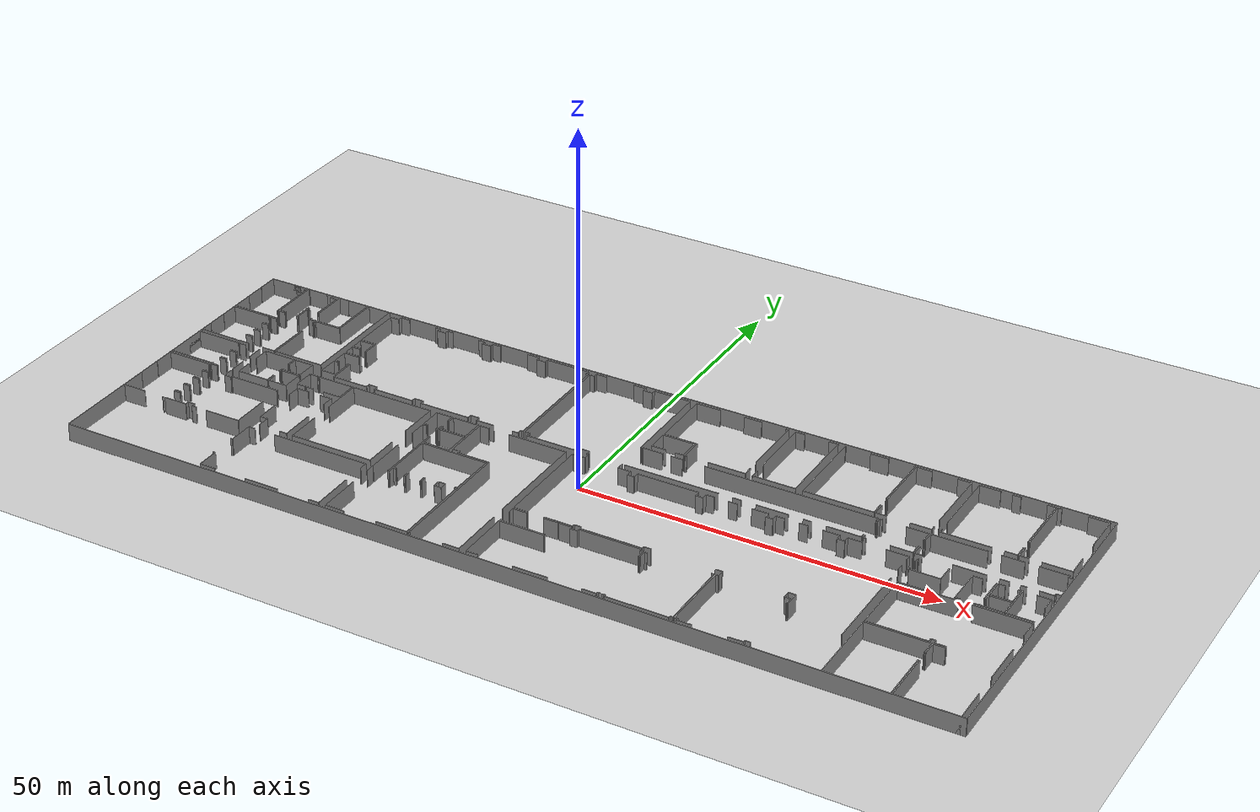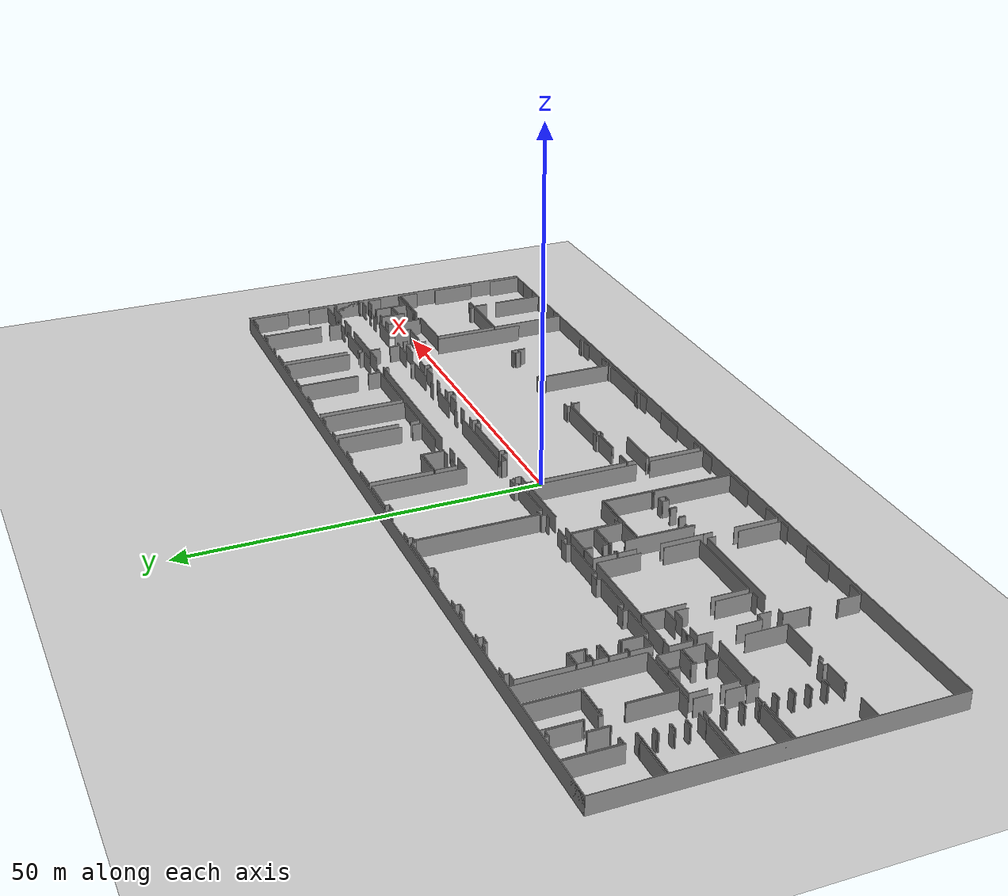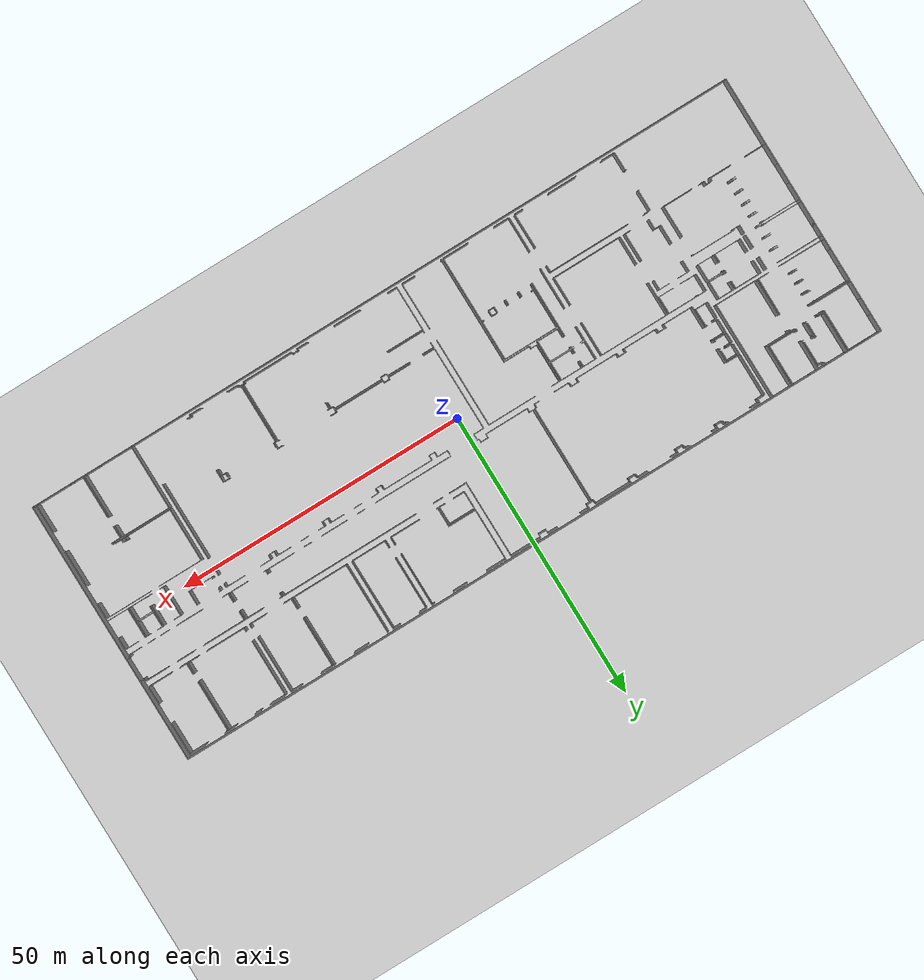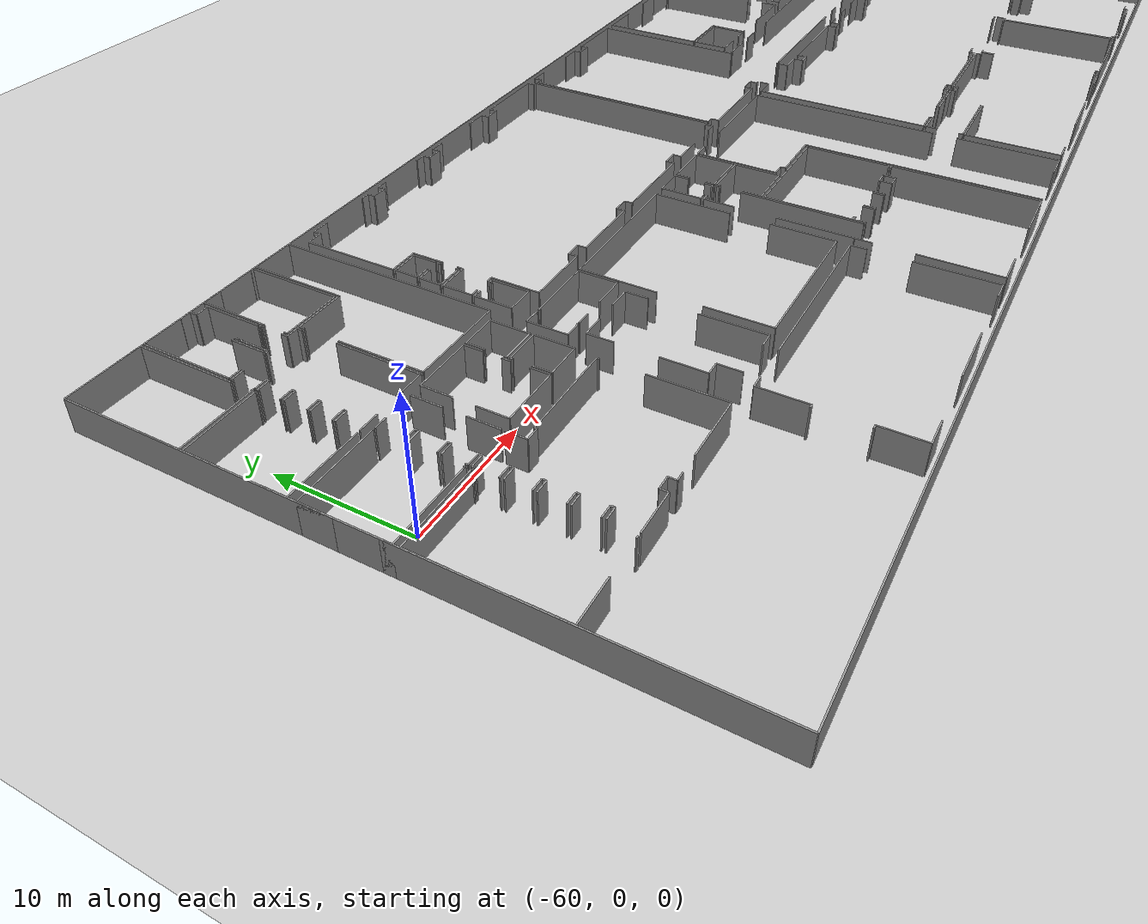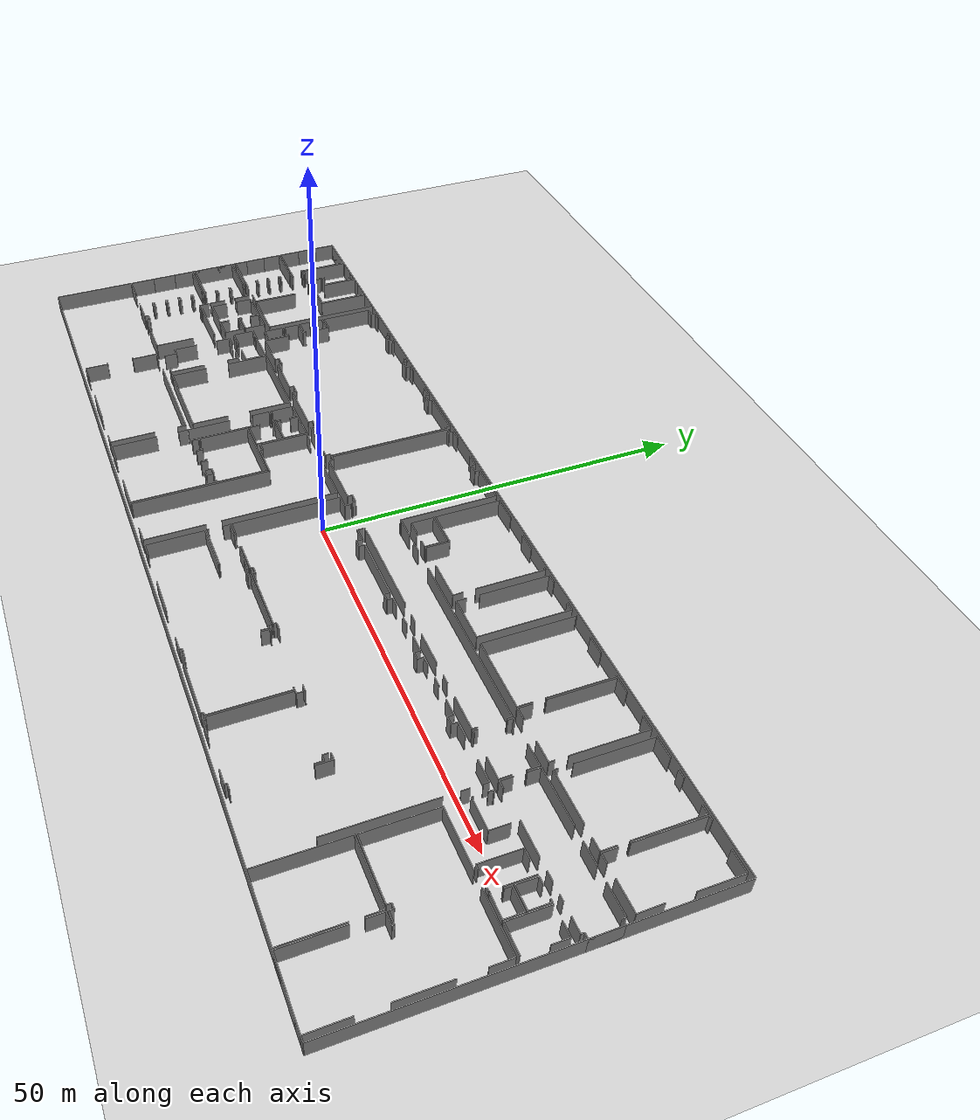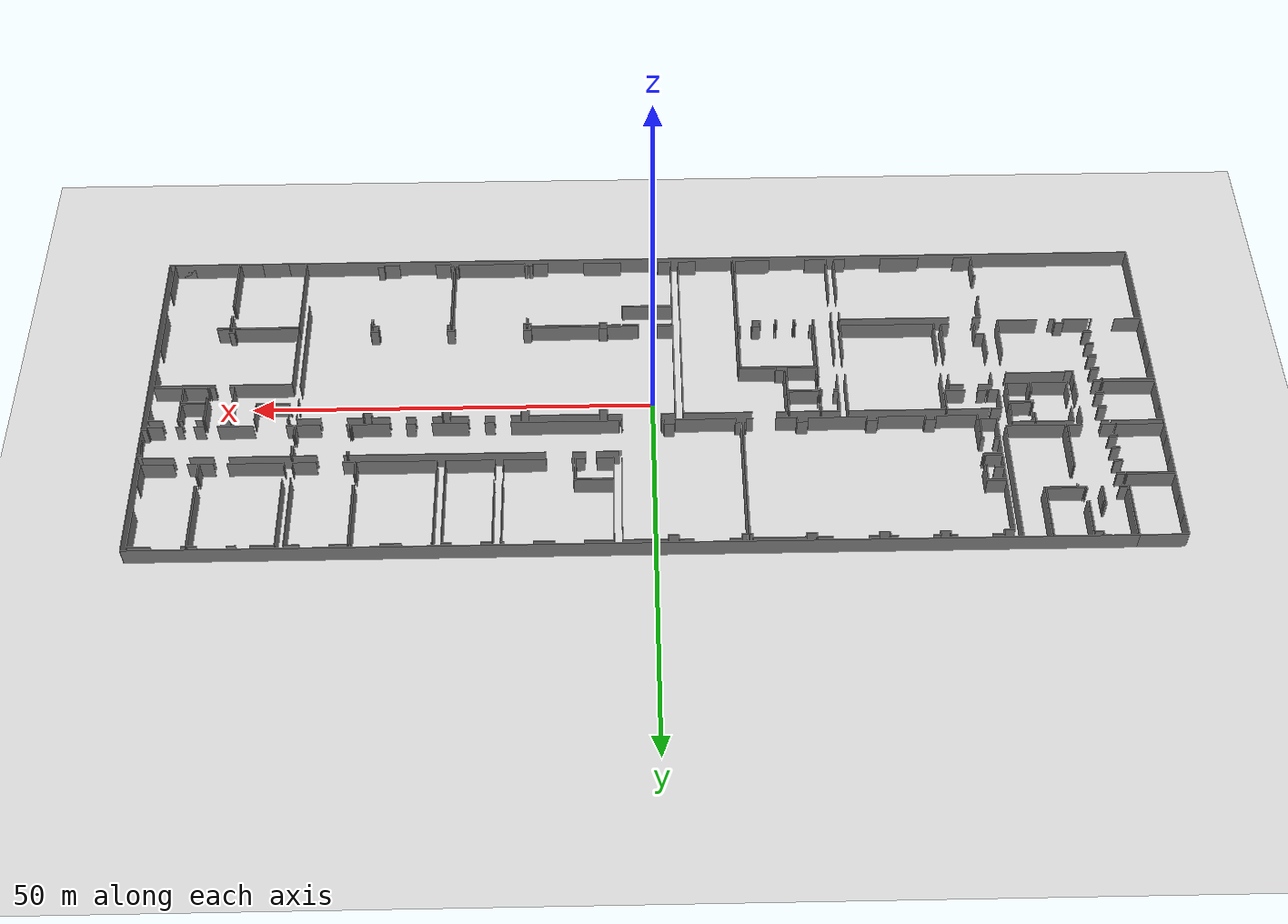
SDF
<sdf version="1.6">
  <world name="default">
    <light name="sun" type="directional">
      <cast_shadows>1</cast_shadows>
      <pose frame="">0 0 10 0 -0 0</pose>
      <diffuse>0.8 0.8 0.8 1</diffuse>
      <specular>0.1 0.1 0.1 1</specular>
      <attenuation>
        <range>1000</range>
        <constant>0.9</constant>
        <linear>0.01</linear>
        <quadratic>0.001</quadratic>
      </attenuation>
      <direction>-0.5 0.5 -1</direction>
    </light>
    <model name="ground_plane">
      <static>1</static>
      <link name="link">
        <collision name="collision">
          <geometry>
            <plane>
              <normal>0 0 1</normal>
              <size>100 100</size>
            </plane>
          </geometry>
          <surface>
            <friction>
              <ode>
                <mu>100</mu>
                <mu2>50</mu2>
              </ode>
              <torsional>
                <ode />
              </torsional>
            </friction>
            <contact>
              <ode />
            </contact>
            <bounce />
          </surface>
          <max_contacts>10</max_contacts>
        </collision>
        <visual name="visual">
          <cast_shadows>0</cast_shadows>
          <geometry>
            <plane>
              <normal>0 0 1</normal>
              <size>100 100</size>
            </plane>
          </geometry>
          <material>
            <script>
              <uri>file://media/materials/scripts/gazebo.material</uri>
              <name>Gazebo/Grey</name>
            </script>
          </material>
        </visual>
        <self_collide>0</self_collide>
        <kinematic>0</kinematic>
        <gravity>1</gravity>
      </link>
    </model>
    <gravity>0 0 -9.8</gravity>
    <magnetic_field>6e-06 2.3e-05 -4.2e-05</magnetic_field>
    <atmosphere type="adiabatic" />
    <physics default="0" name="default_physics" type="ode">
      <max_step_size>0.001</max_step_size>
      <real_time_factor>1</real_time_factor>
      <real_time_update_rate>1000</real_time_update_rate>
    </physics>
    <scene>
      <ambient>0.4 0.4 0.4 1</ambient>
      <background>0.7 0.7 0.7 1</background>
      <shadows>1</shadows>
    </scene>
    <spherical_coordinates>
      <surface_model>EARTH_WGS84</surface_model>
      <latitude_deg>0</latitude_deg>
      <longitude_deg>0</longitude_deg>
      <elevation>0</elevation>
      <heading_deg>0</heading_deg>
    </spherical_coordinates>
  <model name="50010539">
		<static>1</static>
		<link name="Wall_0">
			<collision name="Wall_0_Collision">
				<geometry>
					<box>
						<size>0.0889205050685 0.1 2.5</size>
					</box>
				</geometry>
				<pose frame="">0.0444602525342 0 1.25 0 0 0</pose>
			</collision>
			<visual name="Wall_0_Visual">
				<pose frame="">0.0444602525342 0 1.25 0 0 0</pose>
				<geometry>
					<box>
						<size>0.0889205050685 0.1 2.5</size>
					</box>
				</geometry>
				<material>
					<script>
						<uri>file://media/materials/scripts/gazebo.material</uri>
						<name>Gazebo/Grey</name>
					</script>
					<ambient>1 1 1 1</ambient>
				</material>
			</visual>
			<pose frame="">5.86329107492 -8.9290160311 0 0 0 -1.57079632679</pose>
		</link>
		<link name="Wall_1">
			<collision name="Wall_1_Collision">
				<geometry>
					<box>
						<size>5.85223952643 0.1 2.5</size>
					</box>
				</geometry>
				<pose frame="">2.92611976322 0 1.25 0 0 0</pose>
			</collision>
			<visual name="Wall_1_Visual">
				<pose frame="">2.92611976322 0 1.25 0 0 0</pose>
				<geometry>
					<box>
						<size>5.85223952643 0.1 2.5</size>
					</box>
				</geometry>
				<material>
					<script>
						<uri>file://media/materials/scripts/gazebo.material</uri>
						<name>Gazebo/Grey</name>
					</script>
					<ambient>1 1 1 1</ambient>
				</material>
			</visual>
			<pose frame="">5.86329107492 -9.01793653617 0 0 0 3.14159265359</pose>
		</link>
		<link name="Wall_2">
			<collision name="Wall_2_Collision">
				<geometry>
					<box>
						<size>3.07106018648 0.1 2.5</size>
					</box>
				</geometry>
				<pose frame="">1.53553009324 0 1.25 0 0 0</pose>
			</collision>
			<visual name="Wall_2_Visual">
				<pose frame="">1.53553009324 0 1.25 0 0 0</pose>
				<geometry>
					<box>
						<size>3.07106018648 0.1 2.5</size>
					</box>
				</geometry>
				<material>
					<script>
						<uri>file://media/materials/scripts/gazebo.material</uri>
						<name>Gazebo/Grey</name>
					</script>
					<ambient>1 1 1 1</ambient>
				</material>
			</visual>
			<pose frame="">0.0110515484871 -9.01793653617 0 0 0 1.57079632679</pose>
		</link>
		<link name="Wall_3">
			<collision name="Wall_3_Collision">
				<geometry>
					<box>
						<size>3.02355123091 0.1 2.5</size>
					</box>
				</geometry>
				<pose frame="">1.51177561546 0 1.25 0 0 0</pose>
			</collision>
			<visual name="Wall_3_Visual">
				<pose frame="">1.51177561546 0 1.25 0 0 0</pose>
				<geometry>
					<box>
						<size>3.02355123091 0.1 2.5</size>
					</box>
				</geometry>
				<material>
					<script>
						<uri>file://media/materials/scripts/gazebo.material</uri>
						<name>Gazebo/Grey</name>
					</script>
					<ambient>1 1 1 1</ambient>
				</material>
			</visual>
			<pose frame="">0.0110515484871 -3.02355123091 0 0 0 1.57079632679</pose>
		</link>
		<link name="Wall_4">
			<collision name="Wall_4_Collision">
				<geometry>
					<box>
						<size>5.82721475572 0.1 2.5</size>
					</box>
				</geometry>
				<pose frame="">2.91360737786 0 1.25 0 0 0</pose>
			</collision>
			<visual name="Wall_4_Visual">
				<pose frame="">2.91360737786 0 1.25 0 0 0</pose>
				<geometry>
					<box>
						<size>5.82721475572 0.1 2.5</size>
					</box>
				</geometry>
				<material>
					<script>
						<uri>file://media/materials/scripts/gazebo.material</uri>
						<name>Gazebo/Grey</name>
					</script>
					<ambient>1 1 1 1</ambient>
				</material>
			</visual>
			<pose frame="">0.0110515484871 -0.0 0 0 0 0.0</pose>
		</link>
		<link name="Wall_5">
			<collision name="Wall_5_Collision">
				<geometry>
					<box>
						<size>7.35224400607 0.1 2.5</size>
					</box>
				</geometry>
				<pose frame="">3.67612200304 0 1.25 0 0 0</pose>
			</collision>
			<visual name="Wall_5_Visual">
				<pose frame="">3.67612200304 0 1.25 0 0 0</pose>
				<geometry>
					<box>
						<size>7.35224400607 0.1 2.5</size>
					</box>
				</geometry>
				<material>
					<script>
						<uri>file://media/materials/scripts/gazebo.material</uri>
						<name>Gazebo/Grey</name>
					</script>
					<ambient>1 1 1 1</ambient>
				</material>
			</visual>
			<pose frame="">5.83826630421 -0.0 0 0 0 -1.56739262868</pose>
		</link>
		<link name="Wall_6">
			<collision name="Wall_6_Collision">
				<geometry>
					<box>
						<size>7.01239805899 0.1 2.5</size>
					</box>
				</geometry>
				<pose frame="">3.5061990295 0 1.25 0 0 0</pose>
			</collision>
			<visual name="Wall_6_Visual">
				<pose frame="">3.5061990295 0 1.25 0 0 0</pose>
				<geometry>
					<box>
						<size>7.01239805899 0.1 2.5</size>
					</box>
				</geometry>
				<material>
					<script>
						<uri>file://media/materials/scripts/gazebo.material</uri>
						<name>Gazebo/Grey</name>
					</script>
					<ambient>1 1 1 1</ambient>
				</material>
			</visual>
			<pose frame="">6.07593811133 -7.03005513071 0 0 0 1.57079632679</pose>
		</link>
		<link name="Wall_7">
			<collision name="Wall_7_Collision">
				<geometry>
					<box>
						<size>0.171616574782 0.1 2.5</size>
					</box>
				</geometry>
				<pose frame="">0.0858082873911 0 1.25 0 0 0</pose>
			</collision>
			<visual name="Wall_7_Visual">
				<pose frame="">0.0858082873911 0 1.25 0 0 0</pose>
				<geometry>
					<box>
						<size>0.171616574782 0.1 2.5</size>
					</box>
				</geometry>
				<material>
					<script>
						<uri>file://media/materials/scripts/gazebo.material</uri>
						<name>Gazebo/Grey</name>
					</script>
					<ambient>1 1 1 1</ambient>
				</material>
			</visual>
			<pose frame="">6.07593811133 -0.0176570717207 0 0 0 0.0</pose>
		</link>
		<link name="Wall_8">
			<collision name="Wall_8_Collision">
				<geometry>
					<box>
						<size>0.857066639567 0.1 2.5</size>
					</box>
				</geometry>
				<pose frame="">0.428533319784 0 1.25 0 0 0</pose>
			</collision>
			<visual name="Wall_8_Visual">
				<pose frame="">0.428533319784 0 1.25 0 0 0</pose>
				<geometry>
					<box>
						<size>0.857066639567 0.1 2.5</size>
					</box>
				</geometry>
				<material>
					<script>
						<uri>file://media/materials/scripts/gazebo.material</uri>
						<name>Gazebo/Grey</name>
					</script>
					<ambient>1 1 1 1</ambient>
				</material>
			</visual>
			<pose frame="">9.16071746145 -0.0176570717207 0 0 0 0.0</pose>
		</link>
		<link name="Wall_9">
			<collision name="Wall_9_Collision">
				<geometry>
					<box>
						<size>0.54851248698 0.1 2.5</size>
					</box>
				</geometry>
				<pose frame="">0.27425624349 0 1.25 0 0 0</pose>
			</collision>
			<visual name="Wall_9_Visual">
				<pose frame="">0.27425624349 0 1.25 0 0 0</pose>
				<geometry>
					<box>
						<size>0.54851248698 0.1 2.5</size>
					</box>
				</geometry>
				<material>
					<script>
						<uri>file://media/materials/scripts/gazebo.material</uri>
						<name>Gazebo/Grey</name>
					</script>
					<ambient>1 1 1 1</ambient>
				</material>
			</visual>
			<pose frame="">10.017784101 -0.0176570717207 0 0 0 -1.57079632679</pose>
		</link>
		<link name="Wall_10">
			<collision name="Wall_10_Collision">
				<geometry>
					<box>
						<size>1.01204237697 0.1 2.5</size>
					</box>
				</geometry>
				<pose frame="">0.506021188486 0 1.25 0 0 0</pose>
			</collision>
			<visual name="Wall_10_Visual">
				<pose frame="">0.506021188486 0 1.25 0 0 0</pose>
				<geometry>
					<box>
						<size>1.01204237697 0.1 2.5</size>
					</box>
				</geometry>
				<material>
					<script>
						<uri>file://media/materials/scripts/gazebo.material</uri>
						<name>Gazebo/Grey</name>
					</script>
					<ambient>1 1 1 1</ambient>
				</material>
			</visual>
			<pose frame="">10.017784101 -0.5661695587 0 0 0 0.0</pose>
		</link>
		<link name="Wall_11">
			<collision name="Wall_11_Collision">
				<geometry>
					<box>
						<size>4.26157872005 0.1 2.5</size>
					</box>
				</geometry>
				<pose frame="">2.13078936003 0 1.25 0 0 0</pose>
			</collision>
			<visual name="Wall_11_Visual">
				<pose frame="">2.13078936003 0 1.25 0 0 0</pose>
				<geometry>
					<box>
						<size>4.26157872005 0.1 2.5</size>
					</box>
				</geometry>
				<material>
					<script>
						<uri>file://media/materials/scripts/gazebo.material</uri>
						<name>Gazebo/Grey</name>
					</script>
					<ambient>1 1 1 1</ambient>
				</material>
			</visual>
			<pose frame="">11.029826478 -0.5661695587 0 0 0 -1.57079632679</pose>
		</link>
		<link name="Wall_12">
			<collision name="Wall_12_Collision">
				<geometry>
					<box>
						<size>0.344122354615 0.1 2.5</size>
					</box>
				</geometry>
				<pose frame="">0.172061177307 0 1.25 0 0 0</pose>
			</collision>
			<visual name="Wall_12_Visual">
				<pose frame="">0.172061177307 0 1.25 0 0 0</pose>
				<geometry>
					<box>
						<size>0.344122354615 0.1 2.5</size>
					</box>
				</geometry>
				<material>
					<script>
						<uri>file://media/materials/scripts/gazebo.material</uri>
						<name>Gazebo/Grey</name>
					</script>
					<ambient>1 1 1 1</ambient>
				</material>
			</visual>
			<pose frame="">9.30286324026 -4.82774827875 0 0 0 1.57079632679</pose>
		</link>
		<link name="Wall_13">
			<collision name="Wall_13_Collision">
				<geometry>
					<box>
						<size>0.240085363685 0.1 2.5</size>
					</box>
				</geometry>
				<pose frame="">0.120042681842 0 1.25 0 0 0</pose>
			</collision>
			<visual name="Wall_13_Visual">
				<pose frame="">0.120042681842 0 1.25 0 0 0</pose>
				<geometry>
					<box>
						<size>0.240085363685 0.1 2.5</size>
					</box>
				</geometry>
				<material>
					<script>
						<uri>file://media/materials/scripts/gazebo.material</uri>
						<name>Gazebo/Grey</name>
					</script>
					<ambient>1 1 1 1</ambient>
				</material>
			</visual>
			<pose frame="">9.30286324026 -4.48362592414 0 0 0 3.14159265359</pose>
		</link>
		<link name="Wall_14">
			<collision name="Wall_14_Collision">
				<geometry>
					<box>
						<size>2.56078351668 0.1 2.5</size>
					</box>
				</geometry>
				<pose frame="">1.28039175834 0 1.25 0 0 0</pose>
			</collision>
			<visual name="Wall_14_Visual">
				<pose frame="">1.28039175834 0 1.25 0 0 0</pose>
				<geometry>
					<box>
						<size>2.56078351668 0.1 2.5</size>
					</box>
				</geometry>
				<material>
					<script>
						<uri>file://media/materials/scripts/gazebo.material</uri>
						<name>Gazebo/Grey</name>
					</script>
					<ambient>1 1 1 1</ambient>
				</material>
			</visual>
			<pose frame="">9.06277787658 -4.48362592414 0 0 0 -1.57079632679</pose>
		</link>
		<link name="Wall_15">
			<collision name="Wall_15_Collision">
				<geometry>
					<box>
						<size>1.00452318385 0.1 2.5</size>
					</box>
				</geometry>
				<pose frame="">0.502261591923 0 1.25 0 0 0</pose>
			</collision>
			<visual name="Wall_15_Visual">
				<pose frame="">0.502261591923 0 1.25 0 0 0</pose>
				<geometry>
					<box>
						<size>1.00452318385 0.1 2.5</size>
					</box>
				</geometry>
				<material>
					<script>
						<uri>file://media/materials/scripts/gazebo.material</uri>
						<name>Gazebo/Grey</name>
					</script>
					<ambient>1 1 1 1</ambient>
				</material>
			</visual>
			<pose frame="">7.08035873072 -7.04440944082 0 0 0 3.12730249196</pose>
		</link>
		<link name="Wall_16">
			<collision name="Wall_16_Collision">
				<geometry>
					<box>
						<size>4.6807753868 0.1 2.5</size>
					</box>
				</geometry>
				<pose frame="">2.3403876934 0 1.25 0 0 0</pose>
			</collision>
			<visual name="Wall_16_Visual">
				<pose frame="">2.3403876934 0 1.25 0 0 0</pose>
				<geometry>
					<box>
						<size>4.6807753868 0.1 2.5</size>
					</box>
				</geometry>
				<material>
					<script>
						<uri>file://media/materials/scripts/gazebo.material</uri>
						<name>Gazebo/Grey</name>
					</script>
					<ambient>1 1 1 1</ambient>
				</material>
			</visual>
			<pose frame="">15.9443357638 -7.03018216001 0 0 0 3.14159265359</pose>
		</link>
		<link name="Wall_17">
			<collision name="Wall_17_Collision">
				<geometry>
					<box>
						<size>0.269937247529 0.1 2.5</size>
					</box>
				</geometry>
				<pose frame="">0.134968623765 0 1.25 0 0 0</pose>
			</collision>
			<visual name="Wall_17_Visual">
				<pose frame="">0.134968623765 0 1.25 0 0 0</pose>
				<geometry>
					<box>
						<size>0.269937247529 0.1 2.5</size>
					</box>
				</geometry>
				<material>
					<script>
						<uri>file://media/materials/scripts/gazebo.material</uri>
						<name>Gazebo/Grey</name>
					</script>
					<ambient>1 1 1 1</ambient>
				</material>
			</visual>
			<pose frame="">11.263560377 -7.03018216001 0 0 0 1.57079632679</pose>
		</link>
		<link name="Wall_18">
			<collision name="Wall_18_Collision">
				<geometry>
					<box>
						<size>5.14570259902 0.1 2.5</size>
					</box>
				</geometry>
				<pose frame="">2.57285129951 0 1.25 0 0 0</pose>
			</collision>
			<visual name="Wall_18_Visual">
				<pose frame="">2.57285129951 0 1.25 0 0 0</pose>
				<geometry>
					<box>
						<size>5.14570259902 0.1 2.5</size>
					</box>
				</geometry>
				<material>
					<script>
						<uri>file://media/materials/scripts/gazebo.material</uri>
						<name>Gazebo/Grey</name>
					</script>
					<ambient>1 1 1 1</ambient>
				</material>
			</visual>
			<pose frame="">11.263560377 -5.15408653235 0 0 0 1.57079632679</pose>
		</link>
		<link name="Wall_19">
			<collision name="Wall_19_Collision">
				<geometry>
					<box>
						<size>1.47379385686 0.1 2.5</size>
					</box>
				</geometry>
				<pose frame="">0.736896928432 0 1.25 0 0 0</pose>
			</collision>
			<visual name="Wall_19_Visual">
				<pose frame="">0.736896928432 0 1.25 0 0 0</pose>
				<geometry>
					<box>
						<size>1.47379385686 0.1 2.5</size>
					</box>
				</geometry>
				<material>
					<script>
						<uri>file://media/materials/scripts/gazebo.material</uri>
						<name>Gazebo/Grey</name>
					</script>
					<ambient>1 1 1 1</ambient>
				</material>
			</visual>
			<pose frame="">11.263560377 -0.00838393333503 0 0 0 0.0</pose>
		</link>
		<link name="Wall_20">
			<collision name="Wall_20_Collision">
				<geometry>
					<box>
						<size>0.290515992988 0.1 2.5</size>
					</box>
				</geometry>
				<pose frame="">0.145257996494 0 1.25 0 0 0</pose>
			</collision>
			<visual name="Wall_20_Visual">
				<pose frame="">0.145257996494 0 1.25 0 0 0</pose>
				<geometry>
					<box>
						<size>0.290515992988 0.1 2.5</size>
					</box>
				</geometry>
				<material>
					<script>
						<uri>file://media/materials/scripts/gazebo.material</uri>
						<name>Gazebo/Grey</name>
					</script>
					<ambient>1 1 1 1</ambient>
				</material>
			</visual>
			<pose frame="">15.6338761718 -0.00838393333503 0 0 0 0.0</pose>
		</link>
		<link name="Wall_21">
			<collision name="Wall_21_Collision">
				<geometry>
					<box>
						<size>7.02182654893 0.1 2.5</size>
					</box>
				</geometry>
				<pose frame="">3.51091327446 0 1.25 0 0 0</pose>
			</collision>
			<visual name="Wall_21_Visual">
				<pose frame="">3.51091327446 0 1.25 0 0 0</pose>
				<geometry>
					<box>
						<size>7.02182654893 0.1 2.5</size>
					</box>
				</geometry>
				<material>
					<script>
						<uri>file://media/materials/scripts/gazebo.material</uri>
						<name>Gazebo/Grey</name>
					</script>
					<ambient>1 1 1 1</ambient>
				</material>
			</visual>
			<pose frame="">15.9243921648 -0.00838393333503 0 0 0 -1.56795609346</pose>
		</link>
		<link name="Wall_22">
			<collision name="Wall_22_Collision">
				<geometry>
					<box>
						<size>7.37582886614 0.1 2.5</size>
					</box>
				</geometry>
				<pose frame="">3.68791443307 0 1.25 0 0 0</pose>
			</collision>
			<visual name="Wall_22_Visual">
				<pose frame="">3.68791443307 0 1.25 0 0 0</pose>
				<geometry>
					<box>
						<size>7.37582886614 0.1 2.5</size>
					</box>
				</geometry>
				<material>
					<script>
						<uri>file://media/materials/scripts/gazebo.material</uri>
						<name>Gazebo/Grey</name>
					</script>
					<ambient>1 1 1 1</ambient>
				</material>
			</visual>
			<pose frame="">19.5602245878 -16.7629125276 0 0 0 3.14159265359</pose>
		</link>
		<link name="Wall_23">
			<collision name="Wall_23_Collision">
				<geometry>
					<box>
						<size>6.4226010518 0.1 2.5</size>
					</box>
				</geometry>
				<pose frame="">3.2113005259 0 1.25 0 0 0</pose>
			</collision>
			<visual name="Wall_23_Visual">
				<pose frame="">3.2113005259 0 1.25 0 0 0</pose>
				<geometry>
					<box>
						<size>6.4226010518 0.1 2.5</size>
					</box>
				</geometry>
				<material>
					<script>
						<uri>file://media/materials/scripts/gazebo.material</uri>
						<name>Gazebo/Grey</name>
					</script>
					<ambient>1 1 1 1</ambient>
				</material>
			</visual>
			<pose frame="">12.1843957217 -16.7629125276 0 0 0 1.57079632679</pose>
		</link>
		<link name="Wall_24">
			<collision name="Wall_24_Collision">
				<geometry>
					<box>
						<size>0.403445034425 0.1 2.5</size>
					</box>
				</geometry>
				<pose frame="">0.201722517212 0 1.25 0 0 0</pose>
			</collision>
			<visual name="Wall_24_Visual">
				<pose frame="">0.201722517212 0 1.25 0 0 0</pose>
				<geometry>
					<box>
						<size>0.403445034425 0.1 2.5</size>
					</box>
				</geometry>
				<material>
					<script>
						<uri>file://media/materials/scripts/gazebo.material</uri>
						<name>Gazebo/Grey</name>
					</script>
					<ambient>1 1 1 1</ambient>
				</material>
			</visual>
			<pose frame="">12.1843957217 -7.63407941871 0 0 0 1.57079632679</pose>
		</link>
		<link name="Wall_25">
			<collision name="Wall_25_Collision">
				<geometry>
					<box>
						<size>3.96699778969 0.1 2.5</size>
					</box>
				</geometry>
				<pose frame="">1.98349889485 0 1.25 0 0 0</pose>
			</collision>
			<visual name="Wall_25_Visual">
				<pose frame="">1.98349889485 0 1.25 0 0 0</pose>
				<geometry>
					<box>
						<size>3.96699778969 0.1 2.5</size>
					</box>
				</geometry>
				<material>
					<script>
						<uri>file://media/materials/scripts/gazebo.material</uri>
						<name>Gazebo/Grey</name>
					</script>
					<ambient>1 1 1 1</ambient>
				</material>
			</visual>
			<pose frame="">12.1843957217 -7.23063438429 0 0 0 0.0</pose>
		</link>
		<link name="Wall_26">
			<collision name="Wall_26_Collision">
				<geometry>
					<box>
						<size>7.21640710348 0.1 2.5</size>
					</box>
				</geometry>
				<pose frame="">3.60820355174 0 1.25 0 0 0</pose>
			</collision>
			<visual name="Wall_26_Visual">
				<pose frame="">3.60820355174 0 1.25 0 0 0</pose>
				<geometry>
					<box>
						<size>7.21640710348 0.1 2.5</size>
					</box>
				</geometry>
				<material>
					<script>
						<uri>file://media/materials/scripts/gazebo.material</uri>
						<name>Gazebo/Grey</name>
					</script>
					<ambient>1 1 1 1</ambient>
				</material>
			</visual>
			<pose frame="">16.1513935113 -7.23063438429 0 0 0 1.57079632679</pose>
		</link>
		<link name="Wall_27">
			<collision name="Wall_27_Collision">
				<geometry>
					<box>
						<size>3.39536597139 0.1 2.5</size>
					</box>
				</geometry>
				<pose frame="">1.6976829857 0 1.25 0 0 0</pose>
			</collision>
			<visual name="Wall_27_Visual">
				<pose frame="">1.6976829857 0 1.25 0 0 0</pose>
				<geometry>
					<box>
						<size>3.39536597139 0.1 2.5</size>
					</box>
				</geometry>
				<material>
					<script>
						<uri>file://media/materials/scripts/gazebo.material</uri>
						<name>Gazebo/Grey</name>
					</script>
					<ambient>1 1 1 1</ambient>
				</material>
			</visual>
			<pose frame="">16.1513935113 -0.014227280811 0 0 0 0.0</pose>
		</link>
		<link name="Wall_28">
			<collision name="Wall_28_Collision">
				<geometry>
					<box>
						<size>16.7486906595 0.1 2.5</size>
					</box>
				</geometry>
				<pose frame="">8.37434532973 0 1.25 0 0 0</pose>
			</collision>
			<visual name="Wall_28_Visual">
				<pose frame="">8.37434532973 0 1.25 0 0 0</pose>
				<geometry>
					<box>
						<size>16.7486906595 0.1 2.5</size>
					</box>
				</geometry>
				<material>
					<script>
						<uri>file://media/materials/scripts/gazebo.material</uri>
						<name>Gazebo/Grey</name>
					</script>
					<ambient>1 1 1 1</ambient>
				</material>
			</visual>
			<pose frame="">19.5467594827 -0.014227280811 0 0 0 -1.569992377</pose>
		</link>
		<link name="Wall_29">
			<collision name="Wall_29_Collision">
				<geometry>
					<box>
						<size>0.101750463657 0.1 2.5</size>
					</box>
				</geometry>
				<pose frame="">0.0508752318285 0 1.25 0 0 0</pose>
			</collision>
			<visual name="Wall_29_Visual">
				<pose frame="">0.0508752318285 0 1.25 0 0 0</pose>
				<geometry>
					<box>
						<size>0.101750463657 0.1 2.5</size>
					</box>
				</geometry>
				<material>
					<script>
						<uri>file://media/materials/scripts/gazebo.material</uri>
						<name>Gazebo/Grey</name>
					</script>
					<ambient>1 1 1 1</ambient>
				</material>
			</visual>
			<pose frame="">5.87434262341 -9.3689184726 0 0 0 1.57079632679</pose>
		</link>
		<link name="Wall_30">
			<collision name="Wall_30_Collision">
				<geometry>
					<box>
						<size>5.85770178603 0.1 2.5</size>
					</box>
				</geometry>
				<pose frame="">2.92885089302 0 1.25 0 0 0</pose>
			</collision>
			<visual name="Wall_30_Visual">
				<pose frame="">2.92885089302 0 1.25 0 0 0</pose>
				<geometry>
					<box>
						<size>5.85770178603 0.1 2.5</size>
					</box>
				</geometry>
				<material>
					<script>
						<uri>file://media/materials/scripts/gazebo.material</uri>
						<name>Gazebo/Grey</name>
					</script>
					<ambient>1 1 1 1</ambient>
				</material>
			</visual>
			<pose frame="">5.87434262341 -9.26716800894 0 0 0 3.14159265359</pose>
		</link>
		<link name="Wall_31">
			<collision name="Wall_31_Collision">
				<geometry>
					<box>
						<size>2.65097431468 0.1 2.5</size>
					</box>
				</geometry>
				<pose frame="">1.32548715734 0 1.25 0 0 0</pose>
			</collision>
			<visual name="Wall_31_Visual">
				<pose frame="">1.32548715734 0 1.25 0 0 0</pose>
				<geometry>
					<box>
						<size>2.65097431468 0.1 2.5</size>
					</box>
				</geometry>
				<material>
					<script>
						<uri>file://media/materials/scripts/gazebo.material</uri>
						<name>Gazebo/Grey</name>
					</script>
					<ambient>1 1 1 1</ambient>
				</material>
			</visual>
			<pose frame="">0.0166408373771 -9.26716800894 0 0 0 -1.57079632679</pose>
		</link>
		<link name="Wall_32">
			<collision name="Wall_32_Collision">
				<geometry>
					<box>
						<size>1.85424658926 0.1 2.5</size>
					</box>
				</geometry>
				<pose frame="">0.927123294632 0 1.25 0 0 0</pose>
			</collision>
			<visual name="Wall_32_Visual">
				<pose frame="">0.927123294632 0 1.25 0 0 0</pose>
				<geometry>
					<box>
						<size>1.85424658926 0.1 2.5</size>
					</box>
				</geometry>
				<material>
					<script>
						<uri>file://media/materials/scripts/gazebo.material</uri>
						<name>Gazebo/Grey</name>
					</script>
					<ambient>1 1 1 1</ambient>
				</material>
			</visual>
			<pose frame="">0.0166408373771 -14.8506135515 0 0 0 -1.57079632679</pose>
		</link>
		<link name="Wall_33">
			<collision name="Wall_33_Collision">
				<geometry>
					<box>
						<size>5.85789444382 0.1 2.5</size>
					</box>
				</geometry>
				<pose frame="">2.92894722191 0 1.25 0 0 0</pose>
			</collision>
			<visual name="Wall_33_Visual">
				<pose frame="">2.92894722191 0 1.25 0 0 0</pose>
				<geometry>
					<box>
						<size>5.85789444382 0.1 2.5</size>
					</box>
				</geometry>
				<material>
					<script>
						<uri>file://media/materials/scripts/gazebo.material</uri>
						<name>Gazebo/Grey</name>
					</script>
					<ambient>1 1 1 1</ambient>
				</material>
			</visual>
			<pose frame="">0.0166408373771 -16.7048601407 0 0 0 -0.00811033330518</pose>
		</link>
		<link name="Wall_34">
			<collision name="Wall_34_Collision">
				<geometry>
					<box>
						<size>1.87749294987 0.1 2.5</size>
					</box>
				</geometry>
				<pose frame="">0.938746474937 0 1.25 0 0 0</pose>
			</collision>
			<visual name="Wall_34_Visual">
				<pose frame="">0.938746474937 0 1.25 0 0 0</pose>
				<geometry>
					<box>
						<size>1.87749294987 0.1 2.5</size>
					</box>
				</geometry>
				<material>
					<script>
						<uri>file://media/materials/scripts/gazebo.material</uri>
						<name>Gazebo/Grey</name>
					</script>
					<ambient>1 1 1 1</ambient>
				</material>
			</visual>
			<pose frame="">11.9382129519 -16.7394121084 0 0 0 3.14159265359</pose>
		</link>
		<link name="Wall_35">
			<collision name="Wall_35_Collision">
				<geometry>
					<box>
						<size>1.62038566093 0.1 2.5</size>
					</box>
				</geometry>
				<pose frame="">0.810192830467 0 1.25 0 0 0</pose>
			</collision>
			<visual name="Wall_35_Visual">
				<pose frame="">0.810192830467 0 1.25 0 0 0</pose>
				<geometry>
					<box>
						<size>1.62038566093 0.1 2.5</size>
					</box>
				</geometry>
				<material>
					<script>
						<uri>file://media/materials/scripts/gazebo.material</uri>
						<name>Gazebo/Grey</name>
					</script>
					<ambient>1 1 1 1</ambient>
				</material>
			</visual>
			<pose frame="">7.69251289347 -16.7394121084 0 0 0 3.14159265359</pose>
		</link>
		<link name="Wall_36">
			<collision name="Wall_36_Collision">
				<geometry>
					<box>
						<size>0.997815096161 0.1 2.5</size>
					</box>
				</geometry>
				<pose frame="">0.498907548081 0 1.25 0 0 0</pose>
			</collision>
			<visual name="Wall_36_Visual">
				<pose frame="">0.498907548081 0 1.25 0 0 0</pose>
				<geometry>
					<box>
						<size>0.997815096161 0.1 2.5</size>
					</box>
				</geometry>
				<material>
					<script>
						<uri>file://media/materials/scripts/gazebo.material</uri>
						<name>Gazebo/Grey</name>
					</script>
					<ambient>1 1 1 1</ambient>
				</material>
			</visual>
			<pose frame="">6.07212723254 -15.014735398 0 0 0 0.0</pose>
		</link>
		<link name="Wall_37">
			<collision name="Wall_37_Collision">
				<geometry>
					<box>
						<size>0.208455069739 0.1 2.5</size>
					</box>
				</geometry>
				<pose frame="">0.10422753487 0 1.25 0 0 0</pose>
			</collision>
			<visual name="Wall_37_Visual">
				<pose frame="">0.10422753487 0 1.25 0 0 0</pose>
				<geometry>
					<box>
						<size>0.208455069739 0.1 2.5</size>
					</box>
				</geometry>
				<material>
					<script>
						<uri>file://media/materials/scripts/gazebo.material</uri>
						<name>Gazebo/Grey</name>
					</script>
					<ambient>1 1 1 1</ambient>
				</material>
			</visual>
			<pose frame="">7.0699423287 -15.014735398 0 0 0 1.57079632679</pose>
		</link>
		<link name="Wall_38">
			<collision name="Wall_38_Collision">
				<geometry>
					<box>
						<size>1.01674246081 0.1 2.5</size>
					</box>
				</geometry>
				<pose frame="">0.508371230406 0 1.25 0 0 0</pose>
			</collision>
			<visual name="Wall_38_Visual">
				<pose frame="">0.508371230406 0 1.25 0 0 0</pose>
				<geometry>
					<box>
						<size>1.01674246081 0.1 2.5</size>
					</box>
				</geometry>
				<material>
					<script>
						<uri>file://media/materials/scripts/gazebo.material</uri>
						<name>Gazebo/Grey</name>
					</script>
					<ambient>1 1 1 1</ambient>
				</material>
			</visual>
			<pose frame="">7.0699423287 -14.8062803282 0 0 0 3.14159265359</pose>
		</link>
		<link name="Wall_39">
			<collision name="Wall_39_Collision">
				<geometry>
					<box>
						<size>0.999720535555 0.1 2.5</size>
					</box>
				</geometry>
				<pose frame="">0.499860267778 0 1.25 0 0 0</pose>
			</collision>
			<visual name="Wall_39_Visual">
				<pose frame="">0.499860267778 0 1.25 0 0 0</pose>
				<geometry>
					<box>
						<size>0.999720535555 0.1 2.5</size>
					</box>
				</geometry>
				<material>
					<script>
						<uri>file://media/materials/scripts/gazebo.material</uri>
						<name>Gazebo/Grey</name>
					</script>
					<ambient>1 1 1 1</ambient>
				</material>
			</visual>
			<pose frame="">6.05319986789 -13.1913569269 0 0 0 0.0</pose>
		</link>
		<link name="Wall_40">
			<collision name="Wall_40_Collision">
				<geometry>
					<box>
						<size>0.214171387922 0.1 2.5</size>
					</box>
				</geometry>
				<pose frame="">0.107085693961 0 1.25 0 0 0</pose>
			</collision>
			<visual name="Wall_40_Visual">
				<pose frame="">0.107085693961 0 1.25 0 0 0</pose>
				<geometry>
					<box>
						<size>0.214171387922 0.1 2.5</size>
					</box>
				</geometry>
				<material>
					<script>
						<uri>file://media/materials/scripts/gazebo.material</uri>
						<name>Gazebo/Grey</name>
					</script>
					<ambient>1 1 1 1</ambient>
				</material>
			</visual>
			<pose frame="">7.05292040345 -13.1913569269 0 0 0 1.57079632679</pose>
		</link>
		<link name="Wall_41">
			<collision name="Wall_41_Collision">
				<geometry>
					<box>
						<size>0.988541957775 0.1 2.5</size>
					</box>
				</geometry>
				<pose frame="">0.494270978888 0 1.25 0 0 0</pose>
			</collision>
			<visual name="Wall_41_Visual">
				<pose frame="">0.494270978888 0 1.25 0 0 0</pose>
				<geometry>
					<box>
						<size>0.988541957775 0.1 2.5</size>
					</box>
				</geometry>
				<material>
					<script>
						<uri>file://media/materials/scripts/gazebo.material</uri>
						<name>Gazebo/Grey</name>
					</script>
					<ambient>1 1 1 1</ambient>
				</material>
			</visual>
			<pose frame="">7.05292040345 -12.977185539 0 0 0 3.14159265359</pose>
		</link>
		<link name="Wall_42">
			<collision name="Wall_42_Collision">
				<geometry>
					<box>
						<size>0.994004217373 0.1 2.5</size>
					</box>
				</geometry>
				<pose frame="">0.497002108686 0 1.25 0 0 0</pose>
			</collision>
			<visual name="Wall_42_Visual">
				<pose frame="">0.497002108686 0 1.25 0 0 0</pose>
				<geometry>
					<box>
						<size>0.994004217373 0.1 2.5</size>
					</box>
				</geometry>
				<material>
					<script>
						<uri>file://media/materials/scripts/gazebo.material</uri>
						<name>Gazebo/Grey</name>
					</script>
					<ambient>1 1 1 1</ambient>
				</material>
			</visual>
			<pose frame="">6.06437844567 -11.2582251467 0 0 0 0.0</pose>
		</link>
		<link name="Wall_43">
			<collision name="Wall_43_Collision">
				<geometry>
					<box>
						<size>0.2416097152 0.1 2.5</size>
					</box>
				</geometry>
				<pose frame="">0.1208048576 0 1.25 0 0 0</pose>
			</collision>
			<visual name="Wall_43_Visual">
				<pose frame="">0.1208048576 0 1.25 0 0 0</pose>
				<geometry>
					<box>
						<size>0.2416097152 0.1 2.5</size>
					</box>
				</geometry>
				<material>
					<script>
						<uri>file://media/materials/scripts/gazebo.material</uri>
						<name>Gazebo/Grey</name>
					</script>
					<ambient>1 1 1 1</ambient>
				</material>
			</visual>
			<pose frame="">7.05838266304 -11.2582251467 0 0 0 1.57079632679</pose>
		</link>
		<link name="Wall_44">
			<collision name="Wall_44_Collision">
				<geometry>
					<box>
						<size>0.988541957775 0.1 2.5</size>
					</box>
				</geometry>
				<pose frame="">0.494270978888 0 1.25 0 0 0</pose>
			</collision>
			<visual name="Wall_44_Visual">
				<pose frame="">0.494270978888 0 1.25 0 0 0</pose>
				<geometry>
					<box>
						<size>0.988541957775 0.1 2.5</size>
					</box>
				</geometry>
				<material>
					<script>
						<uri>file://media/materials/scripts/gazebo.material</uri>
						<name>Gazebo/Grey</name>
					</script>
					<ambient>1 1 1 1</ambient>
				</material>
			</visual>
			<pose frame="">7.05838266304 -11.0166154315 0 0 0 3.14159265359</pose>
		</link>
		<link name="Wall_45">
			<collision name="Wall_45_Collision">
				<geometry>
					<box>
						<size>0.0603389141536 0.1 2.5</size>
					</box>
				</geometry>
				<pose frame="">0.0301694570768 0 1.25 0 0 0</pose>
			</collision>
			<visual name="Wall_45_Visual">
				<pose frame="">0.0301694570768 0 1.25 0 0 0</pose>
				<geometry>
					<box>
						<size>0.0603389141536 0.1 2.5</size>
					</box>
				</geometry>
				<material>
					<script>
						<uri>file://media/materials/scripts/gazebo.material</uri>
						<name>Gazebo/Grey</name>
					</script>
					<ambient>1 1 1 1</ambient>
				</material>
			</visual>
			<pose frame="">6.06984070527 -11.0166154315 0 0 0 1.57079632679</pose>
		</link>
		<link name="Wall_46">
			<collision name="Wall_46_Collision">
				<geometry>
					<box>
						<size>0.108991133355 0.1 2.5</size>
					</box>
				</geometry>
				<pose frame="">0.0544955666777 0 1.25 0 0 0</pose>
			</collision>
			<visual name="Wall_46_Visual">
				<pose frame="">0.0544955666777 0 1.25 0 0 0</pose>
				<geometry>
					<box>
						<size>0.108991133355 0.1 2.5</size>
					</box>
				</geometry>
				<material>
					<script>
						<uri>file://media/materials/scripts/gazebo.material</uri>
						<name>Gazebo/Grey</name>
					</script>
					<ambient>1 1 1 1</ambient>
				</material>
			</visual>
			<pose frame="">6.06984070527 -9.3689184726 0 0 0 1.57079632679</pose>
		</link>
		<link name="Wall_47">
			<collision name="Wall_47_Collision">
				<geometry>
					<box>
						<size>0.997434008282 0.1 2.5</size>
					</box>
				</geometry>
				<pose frame="">0.498717004141 0 1.25 0 0 0</pose>
			</collision>
			<visual name="Wall_47_Visual">
				<pose frame="">0.498717004141 0 1.25 0 0 0</pose>
				<geometry>
					<box>
						<size>0.997434008282 0.1 2.5</size>
					</box>
				</geometry>
				<material>
					<script>
						<uri>file://media/materials/scripts/gazebo.material</uri>
						<name>Gazebo/Grey</name>
					</script>
					<ambient>1 1 1 1</ambient>
				</material>
			</visual>
			<pose frame="">6.06984070527 -9.25992733924 0 0 0 0.0</pose>
		</link>
		<link name="Wall_48">
			<collision name="Wall_48_Collision">
				<geometry>
					<box>
						<size>0.214298417215 0.1 2.5</size>
					</box>
				</geometry>
				<pose frame="">0.107149208608 0 1.25 0 0 0</pose>
			</collision>
			<visual name="Wall_48_Visual">
				<pose frame="">0.107149208608 0 1.25 0 0 0</pose>
				<geometry>
					<box>
						<size>0.214298417215 0.1 2.5</size>
					</box>
				</geometry>
				<material>
					<script>
						<uri>file://media/materials/scripts/gazebo.material</uri>
						<name>Gazebo/Grey</name>
					</script>
					<ambient>1 1 1 1</ambient>
				</material>
			</visual>
			<pose frame="">7.06727471355 -9.25992733924 0 0 0 1.57079632679</pose>
		</link>
		<link name="Wall_49">
			<collision name="Wall_49_Collision">
				<geometry>
					<box>
						<size>1.00340438505 0.1 2.5</size>
					</box>
				</geometry>
				<pose frame="">0.501702192526 0 1.25 0 0 0</pose>
			</collision>
			<visual name="Wall_49_Visual">
				<pose frame="">0.501702192526 0 1.25 0 0 0</pose>
				<geometry>
					<box>
						<size>1.00340438505 0.1 2.5</size>
					</box>
				</geometry>
				<material>
					<script>
						<uri>file://media/materials/scripts/gazebo.material</uri>
						<name>Gazebo/Grey</name>
					</script>
					<ambient>1 1 1 1</ambient>
				</material>
			</visual>
			<pose frame="">7.06727471355 -9.04562892203 0 0 0 3.14159265359</pose>
		</link>
		<link name="Wall_50">
			<collision name="Wall_50_Collision">
				<geometry>
					<box>
						<size>0.0834582454714 0.1 2.5</size>
					</box>
				</geometry>
				<pose frame="">0.0417291227357 0 1.25 0 0 0</pose>
			</collision>
			<visual name="Wall_50_Visual">
				<pose frame="">0.0417291227357 0 1.25 0 0 0</pose>
				<geometry>
					<box>
						<size>0.0834582454714 0.1 2.5</size>
					</box>
				</geometry>
				<material>
					<script>
						<uri>file://media/materials/scripts/gazebo.material</uri>
						<name>Gazebo/Grey</name>
					</script>
					<ambient>1 1 1 1</ambient>
				</material>
			</visual>
			<pose frame="">6.0638703285 -9.04562892203 0 0 0 1.57079632679</pose>
		</link>
		<link name="Wall_51">
			<collision name="Wall_51_Collision">
				<geometry>
					<box>
						<size>0.107339752547 0.1 2.5</size>
					</box>
				</geometry>
				<pose frame="">0.0536698762735 0 1.25 0 0 0</pose>
			</collision>
			<visual name="Wall_51_Visual">
				<pose frame="">0.0536698762735 0 1.25 0 0 0</pose>
				<geometry>
					<box>
						<size>0.107339752547 0.1 2.5</size>
					</box>
				</geometry>
				<material>
					<script>
						<uri>file://media/materials/scripts/gazebo.material</uri>
						<name>Gazebo/Grey</name>
					</script>
					<ambient>1 1 1 1</ambient>
				</material>
			</visual>
			<pose frame="">6.0638703285 -7.34750133381 0 0 0 1.57079632679</pose>
		</link>
		<link name="Wall_52">
			<collision name="Wall_52_Collision">
				<geometry>
					<box>
						<size>0.999720535556 0.1 2.5</size>
					</box>
				</geometry>
				<pose frame="">0.499860267778 0 1.25 0 0 0</pose>
			</collision>
			<visual name="Wall_52_Visual">
				<pose frame="">0.499860267778 0 1.25 0 0 0</pose>
				<geometry>
					<box>
						<size>0.999720535556 0.1 2.5</size>
					</box>
				</geometry>
				<material>
					<script>
						<uri>file://media/materials/scripts/gazebo.material</uri>
						<name>Gazebo/Grey</name>
					</script>
					<ambient>1 1 1 1</ambient>
				</material>
			</visual>
			<pose frame="">6.0638703285 -7.24016158126 0 0 0 0.0</pose>
		</link>
		<link name="Wall_53">
			<collision name="Wall_53_Collision">
				<geometry>
					<box>
						<size>0.232463606108 0.1 2.5</size>
					</box>
				</geometry>
				<pose frame="">0.116231803054 0 1.25 0 0 0</pose>
			</collision>
			<visual name="Wall_53_Visual">
				<pose frame="">0.116231803054 0 1.25 0 0 0</pose>
				<geometry>
					<box>
						<size>0.232463606108 0.1 2.5</size>
					</box>
				</geometry>
				<material>
					<script>
						<uri>file://media/materials/scripts/gazebo.material</uri>
						<name>Gazebo/Grey</name>
					</script>
					<ambient>1 1 1 1</ambient>
				</material>
			</visual>
			<pose frame="">9.03724498869 -7.24016158126 0 0 0 0.0</pose>
		</link>
		<link name="Wall_54">
			<collision name="Wall_54_Collision">
				<geometry>
					<box>
						<size>2.18236325297 0.1 2.5</size>
					</box>
				</geometry>
				<pose frame="">1.09118162648 0 1.25 0 0 0</pose>
			</collision>
			<visual name="Wall_54_Visual">
				<pose frame="">1.09118162648 0 1.25 0 0 0</pose>
				<geometry>
					<box>
						<size>2.18236325297 0.1 2.5</size>
					</box>
				</geometry>
				<material>
					<script>
						<uri>file://media/materials/scripts/gazebo.material</uri>
						<name>Gazebo/Grey</name>
					</script>
					<ambient>1 1 1 1</ambient>
				</material>
			</visual>
			<pose frame="">9.2697085948 -7.24016158126 0 0 0 1.57079632679</pose>
		</link>
		<link name="Wall_55">
			<collision name="Wall_55_Collision">
				<geometry>
					<box>
						<size>0.10746678184 0.1 2.5</size>
					</box>
				</geometry>
				<pose frame="">0.0537333909199 0 1.25 0 0 0</pose>
			</collision>
			<visual name="Wall_55_Visual">
				<pose frame="">0.0537333909199 0 1.25 0 0 0</pose>
				<geometry>
					<box>
						<size>0.10746678184 0.1 2.5</size>
					</box>
				</geometry>
				<material>
					<script>
						<uri>file://media/materials/scripts/gazebo.material</uri>
						<name>Gazebo/Grey</name>
					</script>
					<ambient>1 1 1 1</ambient>
				</material>
			</visual>
			<pose frame="">9.2697085948 -5.05779832829 0 0 0 0.0</pose>
		</link>
		<link name="Wall_56">
			<collision name="Wall_56_Collision">
				<geometry>
					<box>
						<size>0.0933665303219 0.1 2.5</size>
					</box>
				</geometry>
				<pose frame="">0.0466832651609 0 1.25 0 0 0</pose>
			</collision>
			<visual name="Wall_56_Visual">
				<pose frame="">0.0466832651609 0 1.25 0 0 0</pose>
				<geometry>
					<box>
						<size>0.0933665303219 0.1 2.5</size>
					</box>
				</geometry>
				<material>
					<script>
						<uri>file://media/materials/scripts/gazebo.material</uri>
						<name>Gazebo/Grey</name>
					</script>
					<ambient>1 1 1 1</ambient>
				</material>
			</visual>
			<pose frame="">10.9466222911 -5.05779832829 0 0 0 0.0</pose>
		</link>
		<link name="Wall_57">
			<collision name="Wall_57_Collision">
				<geometry>
					<box>
						<size>0.0825690404207 0.1 2.5</size>
					</box>
				</geometry>
				<pose frame="">0.0412845202104 0 1.25 0 0 0</pose>
			</collision>
			<visual name="Wall_57_Visual">
				<pose frame="">0.0412845202104 0 1.25 0 0 0</pose>
				<geometry>
					<box>
						<size>0.0825690404207 0.1 2.5</size>
					</box>
				</geometry>
				<material>
					<script>
						<uri>file://media/materials/scripts/gazebo.material</uri>
						<name>Gazebo/Grey</name>
					</script>
					<ambient>1 1 1 1</ambient>
				</material>
			</visual>
			<pose frame="">11.0399888214 -5.05779832829 0 0 0 -1.57079632679</pose>
		</link>
		<link name="Wall_58">
			<collision name="Wall_58_Collision">
				<geometry>
					<box>
						<size>0.501130560707 0.1 2.5</size>
					</box>
				</geometry>
				<pose frame="">0.250565280354 0 1.25 0 0 0</pose>
			</collision>
			<visual name="Wall_58_Visual">
				<pose frame="">0.250565280354 0 1.25 0 0 0</pose>
				<geometry>
					<box>
						<size>0.501130560707 0.1 2.5</size>
					</box>
				</geometry>
				<material>
					<script>
						<uri>file://media/materials/scripts/gazebo.material</uri>
						<name>Gazebo/Grey</name>
					</script>
					<ambient>1 1 1 1</ambient>
				</material>
			</visual>
			<pose frame="">11.0399888214 -6.72366047611 0 0 0 -1.57079632679</pose>
		</link>
		<link name="Wall_59">
			<collision name="Wall_59_Collision">
				<geometry>
					<box>
						<size>0.937349152715 0.1 2.5</size>
					</box>
				</geometry>
				<pose frame="">0.468674576357 0 1.25 0 0 0</pose>
			</collision>
			<visual name="Wall_59_Visual">
				<pose frame="">0.468674576357 0 1.25 0 0 0</pose>
				<geometry>
					<box>
						<size>0.937349152715 0.1 2.5</size>
					</box>
				</geometry>
				<material>
					<script>
						<uri>file://media/materials/scripts/gazebo.material</uri>
						<name>Gazebo/Grey</name>
					</script>
					<ambient>1 1 1 1</ambient>
				</material>
			</visual>
			<pose frame="">11.0399888214 -7.22479103681 0 0 0 0.0</pose>
		</link>
		<link name="Wall_60">
			<collision name="Wall_60_Collision">
				<geometry>
					<box>
						<size>0.392647544524 0.1 2.5</size>
					</box>
				</geometry>
				<pose frame="">0.196323772262 0 1.25 0 0 0</pose>
			</collision>
			<visual name="Wall_60_Visual">
				<pose frame="">0.196323772262 0 1.25 0 0 0</pose>
				<geometry>
					<box>
						<size>0.392647544524 0.1 2.5</size>
					</box>
				</geometry>
				<material>
					<script>
						<uri>file://media/materials/scripts/gazebo.material</uri>
						<name>Gazebo/Grey</name>
					</script>
					<ambient>1 1 1 1</ambient>
				</material>
			</visual>
			<pose frame="">11.9773379741 -7.22479103681 0 0 0 -1.57079632679</pose>
		</link>
		<link name="Wall_61">
			<collision name="Wall_61_Collision">
				<geometry>
					<box>
						<size>6.3992202395 0.1 2.5</size>
					</box>
				</geometry>
				<pose frame="">3.19961011975 0 1.25 0 0 0</pose>
			</collision>
			<visual name="Wall_61_Visual">
				<pose frame="">3.19961011975 0 1.25 0 0 0</pose>
				<geometry>
					<box>
						<size>6.3992202395 0.1 2.5</size>
					</box>
				</geometry>
				<material>
					<script>
						<uri>file://media/materials/scripts/gazebo.material</uri>
						<name>Gazebo/Grey</name>
					</script>
					<ambient>1 1 1 1</ambient>
				</material>
			</visual>
			<pose frame="">11.9773379741 -10.3403114758 0 0 0 -1.57691039453</pose>
		</link>
		<link name="Wall_62">
			<collision name="Wall_62_Collision">
				<geometry>
					<box>
						<size>2.37582886614 0.1 2.5</size>
					</box>
				</geometry>
				<pose frame="">1.18791443307 0 1.25 0 0 0</pose>
			</collision>
			<visual name="Wall_62_Visual">
				<pose frame="">1.18791443307 0 1.25 0 0 0</pose>
				<geometry>
					<box>
						<size>2.37582886614 0.1 2.5</size>
					</box>
				</geometry>
				<material>
					<script>
						<uri>file://media/materials/scripts/gazebo.material</uri>
						<name>Gazebo/Grey</name>
					</script>
					<ambient>1 1 1 1</ambient>
				</material>
			</visual>
			<pose frame="">10.0250247707 -23.6268133432 0 0 0 1.57079632679</pose>
		</link>
		<link name="Wall_63">
			<collision name="Wall_63_Collision">
				<geometry>
					<box>
						<size>2.28716241965 0.1 2.5</size>
					</box>
				</geometry>
				<pose frame="">1.14358120983 0 1.25 0 0 0</pose>
			</collision>
			<visual name="Wall_63_Visual">
				<pose frame="">1.14358120983 0 1.25 0 0 0</pose>
				<geometry>
					<box>
						<size>2.28716241965 0.1 2.5</size>
					</box>
				</geometry>
				<material>
					<script>
						<uri>file://media/materials/scripts/gazebo.material</uri>
						<name>Gazebo/Grey</name>
					</script>
					<ambient>1 1 1 1</ambient>
				</material>
			</visual>
			<pose frame="">10.0250247707 -19.6386016615 0 0 0 1.57079632679</pose>
		</link>
		<link name="Wall_64">
			<collision name="Wall_64_Collision">
				<geometry>
					<box>
						<size>0.985366225452 0.1 2.5</size>
					</box>
				</geometry>
				<pose frame="">0.492683112726 0 1.25 0 0 0</pose>
			</collision>
			<visual name="Wall_64_Visual">
				<pose frame="">0.492683112726 0 1.25 0 0 0</pose>
				<geometry>
					<box>
						<size>0.985366225452 0.1 2.5</size>
					</box>
				</geometry>
				<material>
					<script>
						<uri>file://media/materials/scripts/gazebo.material</uri>
						<name>Gazebo/Grey</name>
					</script>
					<ambient>1 1 1 1</ambient>
				</material>
			</visual>
			<pose frame="">7.6758720561 -17.3514392419 0 0 0 3.14159265359</pose>
		</link>
		<link name="Wall_65">
			<collision name="Wall_65_Collision">
				<geometry>
					<box>
						<size>0.982952668885 0.1 2.5</size>
					</box>
				</geometry>
				<pose frame="">0.491476334443 0 1.25 0 0 0</pose>
			</collision>
			<visual name="Wall_65_Visual">
				<pose frame="">0.491476334443 0 1.25 0 0 0</pose>
				<geometry>
					<box>
						<size>0.982952668885 0.1 2.5</size>
					</box>
				</geometry>
				<material>
					<script>
						<uri>file://media/materials/scripts/gazebo.material</uri>
						<name>Gazebo/Grey</name>
					</script>
					<ambient>1 1 1 1</ambient>
				</material>
			</visual>
			<pose frame="">6.69050583064 -19.3971189756 0 0 0 0.0</pose>
		</link>
		<link name="Wall_66">
			<collision name="Wall_66_Collision">
				<geometry>
					<box>
						<size>0.263712812174 0.1 2.5</size>
					</box>
				</geometry>
				<pose frame="">0.131856406087 0 1.25 0 0 0</pose>
			</collision>
			<visual name="Wall_66_Visual">
				<pose frame="">0.131856406087 0 1.25 0 0 0</pose>
				<geometry>
					<box>
						<size>0.263712812174 0.1 2.5</size>
					</box>
				</geometry>
				<material>
					<script>
						<uri>file://media/materials/scripts/gazebo.material</uri>
						<name>Gazebo/Grey</name>
					</script>
					<ambient>1 1 1 1</ambient>
				</material>
			</visual>
			<pose frame="">7.67345849953 -19.3971189756 0 0 0 -1.57079632679</pose>
		</link>
		<link name="Wall_67">
			<collision name="Wall_67_Collision">
				<geometry>
					<box>
						<size>0.982952668885 0.1 2.5</size>
					</box>
				</geometry>
				<pose frame="">0.491476334443 0 1.25 0 0 0</pose>
			</collision>
			<visual name="Wall_67_Visual">
				<pose frame="">0.491476334443 0 1.25 0 0 0</pose>
				<geometry>
					<box>
						<size>0.982952668885 0.1 2.5</size>
					</box>
				</geometry>
				<material>
					<script>
						<uri>file://media/materials/scripts/gazebo.material</uri>
						<name>Gazebo/Grey</name>
					</script>
					<ambient>1 1 1 1</ambient>
				</material>
			</visual>
			<pose frame="">7.67345849953 -19.6608317878 0 0 0 3.14159265359</pose>
		</link>
		<link name="Wall_68">
			<collision name="Wall_68_Collision">
				<geometry>
					<box>
						<size>0.979903965855 0.1 2.5</size>
					</box>
				</geometry>
				<pose frame="">0.489951982927 0 1.25 0 0 0</pose>
			</collision>
			<visual name="Wall_68_Visual">
				<pose frame="">0.489951982927 0 1.25 0 0 0</pose>
				<geometry>
					<box>
						<size>0.979903965855 0.1 2.5</size>
					</box>
				</geometry>
				<material>
					<script>
						<uri>file://media/materials/scripts/gazebo.material</uri>
						<name>Gazebo/Grey</name>
					</script>
					<ambient>1 1 1 1</ambient>
				</material>
			</visual>
			<pose frame="">6.69050583064 -21.5976474175 0 0 0 0.0</pose>
		</link>
		<link name="Wall_69">
			<collision name="Wall_69_Collision">
				<geometry>
					<box>
						<size>0.249231472778 0.1 2.5</size>
					</box>
				</geometry>
				<pose frame="">0.124615736389 0 1.25 0 0 0</pose>
			</collision>
			<visual name="Wall_69_Visual">
				<pose frame="">0.124615736389 0 1.25 0 0 0</pose>
				<geometry>
					<box>
						<size>0.249231472778 0.1 2.5</size>
					</box>
				</geometry>
				<material>
					<script>
						<uri>file://media/materials/scripts/gazebo.material</uri>
						<name>Gazebo/Grey</name>
					</script>
					<ambient>1 1 1 1</ambient>
				</material>
			</visual>
			<pose frame="">7.6704097965 -21.5976474175 0 0 0 -1.57079632679</pose>
		</link>
		<link name="Wall_70">
			<collision name="Wall_70_Collision">
				<geometry>
					<box>
						<size>0.980030995147 0.1 2.5</size>
					</box>
				</geometry>
				<pose frame="">0.490015497574 0 1.25 0 0 0</pose>
			</collision>
			<visual name="Wall_70_Visual">
				<pose frame="">0.490015497574 0 1.25 0 0 0</pose>
				<geometry>
					<box>
						<size>0.980030995147 0.1 2.5</size>
					</box>
				</geometry>
				<material>
					<script>
						<uri>file://media/materials/scripts/gazebo.material</uri>
						<name>Gazebo/Grey</name>
					</script>
					<ambient>1 1 1 1</ambient>
				</material>
			</visual>
			<pose frame="">7.6704097965 -21.8468788903 0 0 0 3.14159265359</pose>
		</link>
		<link name="Wall_71">
			<collision name="Wall_71_Collision">
				<geometry>
					<box>
						<size>0.192195320241 0.1 2.5</size>
					</box>
				</geometry>
				<pose frame="">0.0960976601204 0 1.25 0 0 0</pose>
			</collision>
			<visual name="Wall_71_Visual">
				<pose frame="">0.0960976601204 0 1.25 0 0 0</pose>
				<geometry>
					<box>
						<size>0.192195320241 0.1 2.5</size>
					</box>
				</geometry>
				<material>
					<script>
						<uri>file://media/materials/scripts/gazebo.material</uri>
						<name>Gazebo/Grey</name>
					</script>
					<ambient>1 1 1 1</ambient>
				</material>
			</visual>
			<pose frame="">6.69037880135 -23.4117527502 0 0 0 -1.57079632679</pose>
		</link>
		<link name="Wall_72">
			<collision name="Wall_72_Collision">
				<geometry>
					<box>
						<size>0.970265139982 0.1 2.5</size>
					</box>
				</geometry>
				<pose frame="">0.485132569991 0 1.25 0 0 0</pose>
			</collision>
			<visual name="Wall_72_Visual">
				<pose frame="">0.485132569991 0 1.25 0 0 0</pose>
				<geometry>
					<box>
						<size>0.970265139982 0.1 2.5</size>
					</box>
				</geometry>
				<material>
					<script>
						<uri>file://media/materials/scripts/gazebo.material</uri>
						<name>Gazebo/Grey</name>
					</script>
					<ambient>1 1 1 1</ambient>
				</material>
			</visual>
			<pose frame="">6.69037880135 -23.6039480704 0 0 0 -0.0235681863805</pose>
		</link>
		<link name="Wall_73">
			<collision name="Wall_73_Collision">
				<geometry>
					<box>
						<size>0.114834480831 0.1 2.5</size>
					</box>
				</geometry>
				<pose frame="">0.0574172404156 0 1.25 0 0 0</pose>
			</collision>
			<visual name="Wall_73_Visual">
				<pose frame="">0.0574172404156 0 1.25 0 0 0</pose>
				<geometry>
					<box>
						<size>0.114834480831 0.1 2.5</size>
					</box>
				</geometry>
				<material>
					<script>
						<uri>file://media/materials/scripts/gazebo.material</uri>
						<name>Gazebo/Grey</name>
					</script>
					<ambient>1 1 1 1</ambient>
				</material>
			</visual>
			<pose frame="">6.48954548919 -23.5500876502 0 0 0 1.57079632679</pose>
		</link>
		<link name="Wall_74">
			<collision name="Wall_74_Collision">
				<geometry>
					<box>
						<size>6.48954548919 0.1 2.5</size>
					</box>
				</geometry>
				<pose frame="">3.24477274459 0 1.25 0 0 0</pose>
			</collision>
			<visual name="Wall_74_Visual">
				<pose frame="">3.24477274459 0 1.25 0 0 0</pose>
				<geometry>
					<box>
						<size>6.48954548919 0.1 2.5</size>
					</box>
				</geometry>
				<material>
					<script>
						<uri>file://media/materials/scripts/gazebo.material</uri>
						<name>Gazebo/Grey</name>
					</script>
					<ambient>1 1 1 1</ambient>
				</material>
			</visual>
			<pose frame="">6.48954548919 -17.3378471075 0 0 0 3.14159265359</pose>
		</link>
		<link name="Wall_75">
			<collision name="Wall_75_Collision">
				<geometry>
					<box>
						<size>2.4072051015 0.1 2.5</size>
					</box>
				</geometry>
				<pose frame="">1.20360255075 0 1.25 0 0 0</pose>
			</collision>
			<visual name="Wall_75_Visual">
				<pose frame="">1.20360255075 0 1.25 0 0 0</pose>
				<geometry>
					<box>
						<size>2.4072051015 0.1 2.5</size>
					</box>
				</geometry>
				<material>
					<script>
						<uri>file://media/materials/scripts/gazebo.material</uri>
						<name>Gazebo/Grey</name>
					</script>
					<ambient>1 1 1 1</ambient>
				</material>
			</visual>
			<pose frame="">0.0 -17.3378471075 0 0 0 -1.57079632679</pose>
		</link>
		<link name="Wall_76">
			<collision name="Wall_76_Collision">
				<geometry>
					<box>
						<size>0.822133584004 0.1 2.5</size>
					</box>
				</geometry>
				<pose frame="">0.411066792002 0 1.25 0 0 0</pose>
			</collision>
			<visual name="Wall_76_Visual">
				<pose frame="">0.411066792002 0 1.25 0 0 0</pose>
				<geometry>
					<box>
						<size>0.822133584004 0.1 2.5</size>
					</box>
				</geometry>
				<material>
					<script>
						<uri>file://media/materials/scripts/gazebo.material</uri>
						<name>Gazebo/Grey</name>
					</script>
					<ambient>1 1 1 1</ambient>
				</material>
			</visual>
			<pose frame="">0.0 -22.6989913874 0 0 0 -1.57079632679</pose>
		</link>
		<link name="Wall_77">
			<collision name="Wall_77_Collision">
				<geometry>
					<box>
						<size>6.48961011872 0.1 2.5</size>
					</box>
				</geometry>
				<pose frame="">3.24480505936 0 1.25 0 0 0</pose>
			</collision>
			<visual name="Wall_77_Visual">
				<pose frame="">3.24480505936 0 1.25 0 0 0</pose>
				<geometry>
					<box>
						<size>6.48961011872 0.1 2.5</size>
					</box>
				</geometry>
				<material>
					<script>
						<uri>file://media/materials/scripts/gazebo.material</uri>
						<name>Gazebo/Grey</name>
					</script>
					<ambient>1 1 1 1</ambient>
				</material>
			</visual>
			<pose frame="">0.0 -23.5211249714 0 0 0 -0.00446294529409</pose>
		</link>
		<link name="Wall_78">
			<collision name="Wall_78_Collision">
				<geometry>
					<box>
						<size>0.126267117197 0.1 2.5</size>
					</box>
				</geometry>
				<pose frame="">0.0631335585986 0 1.25 0 0 0</pose>
			</collision>
			<visual name="Wall_78_Visual">
				<pose frame="">0.0631335585986 0 1.25 0 0 0</pose>
				<geometry>
					<box>
						<size>0.126267117197 0.1 2.5</size>
					</box>
				</geometry>
				<material>
					<script>
						<uri>file://media/materials/scripts/gazebo.material</uri>
						<name>Gazebo/Grey</name>
					</script>
					<ambient>1 1 1 1</ambient>
				</material>
			</visual>
			<pose frame="">6.47303168111 -24.0902162039 0 0 0 1.57079632679</pose>
		</link>
		<link name="Wall_79">
			<collision name="Wall_79_Collision">
				<geometry>
					<box>
						<size>6.44902314474 0.1 2.5</size>
					</box>
				</geometry>
				<pose frame="">3.22451157237 0 1.25 0 0 0</pose>
			</collision>
			<visual name="Wall_79_Visual">
				<pose frame="">3.22451157237 0 1.25 0 0 0</pose>
				<geometry>
					<box>
						<size>6.44902314474 0.1 2.5</size>
					</box>
				</geometry>
				<material>
					<script>
						<uri>file://media/materials/scripts/gazebo.material</uri>
						<name>Gazebo/Grey</name>
					</script>
					<ambient>1 1 1 1</ambient>
				</material>
			</visual>
			<pose frame="">6.47303168111 -23.9639490867 0 0 0 3.14159265359</pose>
		</link>
		<link name="Wall_80">
			<collision name="Wall_80_Collision">
				<geometry>
					<box>
						<size>2.97464495313 0.1 2.5</size>
					</box>
				</geometry>
				<pose frame="">1.48732247656 0 1.25 0 0 0</pose>
			</collision>
			<visual name="Wall_80_Visual">
				<pose frame="">1.48732247656 0 1.25 0 0 0</pose>
				<geometry>
					<box>
						<size>2.97464495313 0.1 2.5</size>
					</box>
				</geometry>
				<material>
					<script>
						<uri>file://media/materials/scripts/gazebo.material</uri>
						<name>Gazebo/Grey</name>
					</script>
					<ambient>1 1 1 1</ambient>
				</material>
			</visual>
			<pose frame="">0.0240085363685 -23.9639490867 0 0 0 -1.57079632679</pose>
		</link>
		<link name="Wall_81">
			<collision name="Wall_81_Collision">
				<geometry>
					<box>
						<size>3.62224028861 0.1 2.5</size>
					</box>
				</geometry>
				<pose frame="">1.81112014431 0 1.25 0 0 0</pose>
			</collision>
			<visual name="Wall_81_Visual">
				<pose frame="">1.81112014431 0 1.25 0 0 0</pose>
				<geometry>
					<box>
						<size>3.62224028861 0.1 2.5</size>
					</box>
				</geometry>
				<material>
					<script>
						<uri>file://media/materials/scripts/gazebo.material</uri>
						<name>Gazebo/Grey</name>
					</script>
					<ambient>1 1 1 1</ambient>
				</material>
			</visual>
			<pose frame="">0.0240085363685 -30.3553009324 0 0 0 -1.57079632679</pose>
		</link>
		<link name="Wall_82">
			<collision name="Wall_82_Collision">
				<geometry>
					<box>
						<size>3.37656563604 0.1 2.5</size>
					</box>
				</geometry>
				<pose frame="">1.68828281802 0 1.25 0 0 0</pose>
			</collision>
			<visual name="Wall_82_Visual">
				<pose frame="">1.68828281802 0 1.25 0 0 0</pose>
				<geometry>
					<box>
						<size>3.37656563604 0.1 2.5</size>
					</box>
				</geometry>
				<material>
					<script>
						<uri>file://media/materials/scripts/gazebo.material</uri>
						<name>Gazebo/Grey</name>
					</script>
					<ambient>1 1 1 1</ambient>
				</material>
			</visual>
			<pose frame="">0.0240085363685 -33.977541221 0 0 0 0.0</pose>
		</link>
		<link name="Wall_83">
			<collision name="Wall_83_Collision">
				<geometry>
					<box>
						<size>0.198610005015 0.1 2.5</size>
					</box>
				</geometry>
				<pose frame="">0.0993050025077 0 1.25 0 0 0</pose>
			</collision>
			<visual name="Wall_83_Visual">
				<pose frame="">0.0993050025077 0 1.25 0 0 0</pose>
				<geometry>
					<box>
						<size>0.198610005015 0.1 2.5</size>
					</box>
				</geometry>
				<material>
					<script>
						<uri>file://media/materials/scripts/gazebo.material</uri>
						<name>Gazebo/Grey</name>
					</script>
					<ambient>1 1 1 1</ambient>
				</material>
			</visual>
			<pose frame="">6.27512004268 -33.977541221 0 0 0 -0.0838848446478</pose>
		</link>
		<link name="Wall_84">
			<collision name="Wall_84_Collision">
				<geometry>
					<box>
						<size>4.61141739285 0.1 2.5</size>
					</box>
				</geometry>
				<pose frame="">2.30570869643 0 1.25 0 0 0</pose>
			</collision>
			<visual name="Wall_84_Visual">
				<pose frame="">2.30570869643 0 1.25 0 0 0</pose>
				<geometry>
					<box>
						<size>4.61141739285 0.1 2.5</size>
					</box>
				</geometry>
				<material>
					<script>
						<uri>file://media/materials/scripts/gazebo.material</uri>
						<name>Gazebo/Grey</name>
					</script>
					<ambient>1 1 1 1</ambient>
				</material>
			</visual>
			<pose frame="">15.6615685577 -23.5404334239 0 0 0 3.14159265359</pose>
		</link>
		<link name="Wall_85">
			<collision name="Wall_85_Collision">
				<geometry>
					<box>
						<size>2.30024643683 0.1 2.5</size>
					</box>
				</geometry>
				<pose frame="">1.15012321841 0 1.25 0 0 0</pose>
			</collision>
			<visual name="Wall_85_Visual">
				<pose frame="">1.15012321841 0 1.25 0 0 0</pose>
				<geometry>
					<box>
						<size>2.30024643683 0.1 2.5</size>
					</box>
				</geometry>
				<material>
					<script>
						<uri>file://media/materials/scripts/gazebo.material</uri>
						<name>Gazebo/Grey</name>
					</script>
					<ambient>1 1 1 1</ambient>
				</material>
			</visual>
			<pose frame="">11.0501511649 -23.5404334239 0 0 0 1.57079632679</pose>
		</link>
		<link name="Wall_86">
			<collision name="Wall_86_Collision">
				<geometry>
					<box>
						<size>2.28652727319 0.1 2.5</size>
					</box>
				</geometry>
				<pose frame="">1.14326363659 0 1.25 0 0 0</pose>
			</collision>
			<visual name="Wall_86_Visual">
				<pose frame="">1.14326363659 0 1.25 0 0 0</pose>
				<geometry>
					<box>
						<size>2.28652727319 0.1 2.5</size>
					</box>
				</geometry>
				<material>
					<script>
						<uri>file://media/materials/scripts/gazebo.material</uri>
						<name>Gazebo/Grey</name>
					</script>
					<ambient>1 1 1 1</ambient>
				</material>
			</visual>
			<pose frame="">11.0501511649 -19.6354259292 0 0 0 1.57079632679</pose>
		</link>
		<link name="Wall_87">
			<collision name="Wall_87_Collision">
				<geometry>
					<box>
						<size>4.60366860598 0.1 2.5</size>
					</box>
				</geometry>
				<pose frame="">2.30183430299 0 1.25 0 0 0</pose>
			</collision>
			<visual name="Wall_87_Visual">
				<pose frame="">2.30183430299 0 1.25 0 0 0</pose>
				<geometry>
					<box>
						<size>4.60366860598 0.1 2.5</size>
					</box>
				</geometry>
				<material>
					<script>
						<uri>file://media/materials/scripts/gazebo.material</uri>
						<name>Gazebo/Grey</name>
					</script>
					<ambient>1 1 1 1</ambient>
				</material>
			</visual>
			<pose frame="">11.0501511649 -17.348898656 0 0 0 0.0</pose>
		</link>
		<link name="Wall_88">
			<collision name="Wall_88_Collision">
				<geometry>
					<box>
						<size>1.40367368715 0.1 2.5</size>
					</box>
				</geometry>
				<pose frame="">0.701836843576 0 1.25 0 0 0</pose>
			</collision>
			<visual name="Wall_88_Visual">
				<pose frame="">0.701836843576 0 1.25 0 0 0</pose>
				<geometry>
					<box>
						<size>1.40367368715 0.1 2.5</size>
					</box>
				</geometry>
				<material>
					<script>
						<uri>file://media/materials/scripts/gazebo.material</uri>
						<name>Gazebo/Grey</name>
					</script>
					<ambient>1 1 1 1</ambient>
				</material>
			</visual>
			<pose frame="">15.6538197708 -17.348898656 0 0 0 -1.57079632679</pose>
		</link>
		<link name="Wall_89">
			<collision name="Wall_89_Collision">
				<geometry>
					<box>
						<size>0.639084372856 0.1 2.5</size>
					</box>
				</geometry>
				<pose frame="">0.319542186428 0 1.25 0 0 0</pose>
			</collision>
			<visual name="Wall_89_Visual">
				<pose frame="">0.319542186428 0 1.25 0 0 0</pose>
				<geometry>
					<box>
						<size>0.639084372856 0.1 2.5</size>
					</box>
				</geometry>
				<material>
					<script>
						<uri>file://media/materials/scripts/gazebo.material</uri>
						<name>Gazebo/Grey</name>
					</script>
					<ambient>1 1 1 1</ambient>
				</material>
			</visual>
			<pose frame="">15.6538197708 -20.1107695435 0 0 0 -1.57079632679</pose>
		</link>
		<link name="Wall_90">
			<collision name="Wall_90_Collision">
				<geometry>
					<box>
						<size>1.41792214125 0.1 2.5</size>
					</box>
				</geometry>
				<pose frame="">0.708961070625 0 1.25 0 0 0</pose>
			</collision>
			<visual name="Wall_90_Visual">
				<pose frame="">0.708961070625 0 1.25 0 0 0</pose>
				<geometry>
					<box>
						<size>1.41792214125 0.1 2.5</size>
					</box>
				</geometry>
				<material>
					<script>
						<uri>file://media/materials/scripts/gazebo.material</uri>
						<name>Gazebo/Grey</name>
					</script>
					<ambient>1 1 1 1</ambient>
				</material>
			</visual>
			<pose frame="">15.6538197708 -22.122532456 0 0 0 -1.56533141076</pose>
		</link>
		<link name="Wall_91">
			<collision name="Wall_91_Collision">
				<geometry>
					<box>
						<size>2.76390335611 0.1 2.5</size>
					</box>
				</geometry>
				<pose frame="">1.38195167806 0 1.25 0 0 0</pose>
			</collision>
			<visual name="Wall_91_Visual">
				<pose frame="">1.38195167806 0 1.25 0 0 0</pose>
				<geometry>
					<box>
						<size>2.76390335611 0.1 2.5</size>
					</box>
				</geometry>
				<material>
					<script>
						<uri>file://media/materials/scripts/gazebo.material</uri>
						<name>Gazebo/Grey</name>
					</script>
					<ambient>1 1 1 1</ambient>
				</material>
			</visual>
			<pose frame="">18.6337999543 -20.3324356597 0 0 0 3.14159265359</pose>
		</link>
		<link name="Wall_92">
			<collision name="Wall_92_Collision">
				<geometry>
					<box>
						<size>0.197911638424 0.1 2.5</size>
					</box>
				</geometry>
				<pose frame="">0.0989558192119 0 1.25 0 0 0</pose>
			</collision>
			<visual name="Wall_92_Visual">
				<pose frame="">0.0989558192119 0 1.25 0 0 0</pose>
				<geometry>
					<box>
						<size>0.197911638424 0.1 2.5</size>
					</box>
				</geometry>
				<material>
					<script>
						<uri>file://media/materials/scripts/gazebo.material</uri>
						<name>Gazebo/Grey</name>
					</script>
					<ambient>1 1 1 1</ambient>
				</material>
			</visual>
			<pose frame="">15.8698965982 -20.3324356597 0 0 0 1.57079632679</pose>
		</link>
		<link name="Wall_93">
			<collision name="Wall_93_Collision">
				<geometry>
					<box>
						<size>1.41472523564 0.1 2.5</size>
					</box>
				</geometry>
				<pose frame="">0.70736261782 0 1.25 0 0 0</pose>
			</collision>
			<visual name="Wall_93_Visual">
				<pose frame="">0.70736261782 0 1.25 0 0 0</pose>
				<geometry>
					<box>
						<size>1.41472523564 0.1 2.5</size>
					</box>
				</geometry>
				<material>
					<script>
						<uri>file://media/materials/scripts/gazebo.material</uri>
						<name>Gazebo/Grey</name>
					</script>
					<ambient>1 1 1 1</ambient>
				</material>
			</visual>
			<pose frame="">15.8698965982 -18.7725159422 0 0 0 1.57079632679</pose>
		</link>
		<link name="Wall_94">
			<collision name="Wall_94_Collision">
				<geometry>
					<box>
						<size>2.77025482076 0.1 2.5</size>
					</box>
				</geometry>
				<pose frame="">1.38512741038 0 1.25 0 0 0</pose>
			</collision>
			<visual name="Wall_94_Visual">
				<pose frame="">1.38512741038 0 1.25 0 0 0</pose>
				<geometry>
					<box>
						<size>2.77025482076 0.1 2.5</size>
					</box>
				</geometry>
				<material>
					<script>
						<uri>file://media/materials/scripts/gazebo.material</uri>
						<name>Gazebo/Grey</name>
					</script>
					<ambient>1 1 1 1</ambient>
				</material>
			</visual>
			<pose frame="">15.8698965982 -17.3577907065 0 0 0 0.0</pose>
		</link>
		<link name="Wall_95">
			<collision name="Wall_95_Collision">
				<geometry>
					<box>
						<size>2.97465173395 0.1 2.5</size>
					</box>
				</geometry>
				<pose frame="">1.48732586697 0 1.25 0 0 0</pose>
			</collision>
			<visual name="Wall_95_Visual">
				<pose frame="">1.48732586697 0 1.25 0 0 0</pose>
				<geometry>
					<box>
						<size>2.97465173395 0.1 2.5</size>
					</box>
				</geometry>
				<material>
					<script>
						<uri>file://media/materials/scripts/gazebo.material</uri>
						<name>Gazebo/Grey</name>
					</script>
					<ambient>1 1 1 1</ambient>
				</material>
			</visual>
			<pose frame="">18.6401514189 -17.3577907065 0 0 0 -1.57293152447</pose>
		</link>
		<link name="Wall_96">
			<collision name="Wall_96_Collision">
				<geometry>
					<box>
						<size>2.77889281268 0.1 2.5</size>
					</box>
				</geometry>
				<pose frame="">1.38944640634 0 1.25 0 0 0</pose>
			</collision>
			<visual name="Wall_96_Visual">
				<pose frame="">1.38944640634 0 1.25 0 0 0</pose>
				<geometry>
					<box>
						<size>2.77889281268 0.1 2.5</size>
					</box>
				</geometry>
				<material>
					<script>
						<uri>file://media/materials/scripts/gazebo.material</uri>
						<name>Gazebo/Grey</name>
					</script>
					<ambient>1 1 1 1</ambient>
				</material>
			</visual>
			<pose frame="">18.6571733442 -23.5269683189 0 0 0 3.14159265359</pose>
		</link>
		<link name="Wall_97">
			<collision name="Wall_97_Collision">
				<geometry>
					<box>
						<size>1.40037092554 0.1 2.5</size>
					</box>
				</geometry>
				<pose frame="">0.700185462768 0 1.25 0 0 0</pose>
			</collision>
			<visual name="Wall_97_Visual">
				<pose frame="">0.700185462768 0 1.25 0 0 0</pose>
				<geometry>
					<box>
						<size>1.40037092554 0.1 2.5</size>
					</box>
				</geometry>
				<material>
					<script>
						<uri>file://media/materials/scripts/gazebo.material</uri>
						<name>Gazebo/Grey</name>
					</script>
					<ambient>1 1 1 1</ambient>
				</material>
			</visual>
			<pose frame="">15.8782805315 -23.5269683189 0 0 0 1.57079632679</pose>
		</link>
		<link name="Wall_98">
			<collision name="Wall_98_Collision">
				<geometry>
					<box>
						<size>0.208455069739 0.1 2.5</size>
					</box>
				</geometry>
				<pose frame="">0.10422753487 0 1.25 0 0 0</pose>
			</collision>
			<visual name="Wall_98_Visual">
				<pose frame="">0.10422753487 0 1.25 0 0 0</pose>
				<geometry>
					<box>
						<size>0.208455069739 0.1 2.5</size>
					</box>
				</geometry>
				<material>
					<script>
						<uri>file://media/materials/scripts/gazebo.material</uri>
						<name>Gazebo/Grey</name>
					</script>
					<ambient>1 1 1 1</ambient>
				</material>
			</visual>
			<pose frame="">15.8782805315 -20.7808490638 0 0 0 1.57079632679</pose>
		</link>
		<link name="Wall_99">
			<collision name="Wall_99_Collision">
				<geometry>
					<box>
						<size>2.76822235207 0.1 2.5</size>
					</box>
				</geometry>
				<pose frame="">1.38411117604 0 1.25 0 0 0</pose>
			</collision>
			<visual name="Wall_99_Visual">
				<pose frame="">1.38411117604 0 1.25 0 0 0</pose>
				<geometry>
					<box>
						<size>2.76822235207 0.1 2.5</size>
					</box>
				</geometry>
				<material>
					<script>
						<uri>file://media/materials/scripts/gazebo.material</uri>
						<name>Gazebo/Grey</name>
					</script>
					<ambient>1 1 1 1</ambient>
				</material>
			</visual>
			<pose frame="">15.8782805315 -20.5723939941 0 0 0 0.0</pose>
		</link>
		<link name="Wall_100">
			<collision name="Wall_100_Collision">
				<geometry>
					<box>
						<size>2.95459359299 0.1 2.5</size>
					</box>
				</geometry>
				<pose frame="">1.47729679649 0 1.25 0 0 0</pose>
			</collision>
			<visual name="Wall_100_Visual">
				<pose frame="">1.47729679649 0 1.25 0 0 0</pose>
				<geometry>
					<box>
						<size>2.95459359299 0.1 2.5</size>
					</box>
				</geometry>
				<material>
					<script>
						<uri>file://media/materials/scripts/gazebo.material</uri>
						<name>Gazebo/Grey</name>
					</script>
					<ambient>1 1 1 1</ambient>
				</material>
			</visual>
			<pose frame="">18.6465028836 -20.5723939941 0 0 0 -1.56718483727</pose>
		</link>
		<link name="Wall_101">
			<collision name="Wall_101_Collision">
				<geometry>
					<box>
						<size>5.1531973273 0.1 2.5</size>
					</box>
				</geometry>
				<pose frame="">2.57659866365 0 1.25 0 0 0</pose>
			</collision>
			<visual name="Wall_101_Visual">
				<pose frame="">2.57659866365 0 1.25 0 0 0</pose>
				<geometry>
					<box>
						<size>5.1531973273 0.1 2.5</size>
					</box>
				</geometry>
				<material>
					<script>
						<uri>file://media/materials/scripts/gazebo.material</uri>
						<name>Gazebo/Grey</name>
					</script>
					<ambient>1 1 1 1</ambient>
				</material>
			</visual>
			<pose frame="">18.4778079825 -34.0062498412 0 0 0 3.14159265359</pose>
		</link>
		<link name="Wall_102">
			<collision name="Wall_102_Collision">
				<geometry>
					<box>
						<size>0.70844236681 0.1 2.5</size>
					</box>
				</geometry>
				<pose frame="">0.354221183405 0 1.25 0 0 0</pose>
			</collision>
			<visual name="Wall_102_Visual">
				<pose frame="">0.354221183405 0 1.25 0 0 0</pose>
				<geometry>
					<box>
						<size>0.70844236681 0.1 2.5</size>
					</box>
				</geometry>
				<material>
					<script>
						<uri>file://media/materials/scripts/gazebo.material</uri>
						<name>Gazebo/Grey</name>
					</script>
					<ambient>1 1 1 1</ambient>
				</material>
			</visual>
			<pose frame="">11.786921064 -34.0062498412 0 0 0 3.14159265359</pose>
		</link>
		<link name="Wall_103">
			<collision name="Wall_103_Collision">
				<geometry>
					<box>
						<size>0.58293742537 0.1 2.5</size>
					</box>
				</geometry>
				<pose frame="">0.291468712685 0 1.25 0 0 0</pose>
			</collision>
			<visual name="Wall_103_Visual">
				<pose frame="">0.291468712685 0 1.25 0 0 0</pose>
				<geometry>
					<box>
						<size>0.58293742537 0.1 2.5</size>
					</box>
				</geometry>
				<material>
					<script>
						<uri>file://media/materials/scripts/gazebo.material</uri>
						<name>Gazebo/Grey</name>
					</script>
					<ambient>1 1 1 1</ambient>
				</material>
			</visual>
			<pose frame="">11.0784786972 -34.0062498412 0 0 0 1.57079632679</pose>
		</link>
		<link name="Wall_104">
			<collision name="Wall_104_Collision">
				<geometry>
					<box>
						<size>1.02982647799 0.1 2.5</size>
					</box>
				</geometry>
				<pose frame="">0.514913238993 0 1.25 0 0 0</pose>
			</collision>
			<visual name="Wall_104_Visual">
				<pose frame="">0.514913238993 0 1.25 0 0 0</pose>
				<geometry>
					<box>
						<size>1.02982647799 0.1 2.5</size>
					</box>
				</geometry>
				<material>
					<script>
						<uri>file://media/materials/scripts/gazebo.material</uri>
						<name>Gazebo/Grey</name>
					</script>
					<ambient>1 1 1 1</ambient>
				</material>
			</visual>
			<pose frame="">11.0784786972 -33.4233124158 0 0 0 3.14159265359</pose>
		</link>
		<link name="Wall_105">
			<collision name="Wall_105_Collision">
				<geometry>
					<box>
						<size>0.574426462742 0.1 2.5</size>
					</box>
				</geometry>
				<pose frame="">0.287213231371 0 1.25 0 0 0</pose>
			</collision>
			<visual name="Wall_105_Visual">
				<pose frame="">0.287213231371 0 1.25 0 0 0</pose>
				<geometry>
					<box>
						<size>0.574426462742 0.1 2.5</size>
					</box>
				</geometry>
				<material>
					<script>
						<uri>file://media/materials/scripts/gazebo.material</uri>
						<name>Gazebo/Grey</name>
					</script>
					<ambient>1 1 1 1</ambient>
				</material>
			</visual>
			<pose frame="">10.0486522192 -33.4233124158 0 0 0 -1.57079632679</pose>
		</link>
		<link name="Wall_106">
			<collision name="Wall_106_Collision">
				<geometry>
					<box>
						<size>3.35725718351 0.1 2.5</size>
					</box>
				</geometry>
				<pose frame="">1.67862859175 0 1.25 0 0 0</pose>
			</collision>
			<visual name="Wall_106_Visual">
				<pose frame="">1.67862859175 0 1.25 0 0 0</pose>
				<geometry>
					<box>
						<size>3.35725718351 0.1 2.5</size>
					</box>
				</geometry>
				<material>
					<script>
						<uri>file://media/materials/scripts/gazebo.material</uri>
						<name>Gazebo/Grey</name>
					</script>
					<ambient>1 1 1 1</ambient>
				</material>
			</visual>
			<pose frame="">10.0486522192 -33.9977388786 0 0 0 3.14159265359</pose>
		</link>
		<link name="Wall_107">
			<collision name="Wall_107_Collision">
				<geometry>
					<box>
						<size>0.993115012322 0.1 2.5</size>
					</box>
				</geometry>
				<pose frame="">0.496557506161 0 1.25 0 0 0</pose>
			</collision>
			<visual name="Wall_107_Visual">
				<pose frame="">0.496557506161 0 1.25 0 0 0</pose>
				<geometry>
					<box>
						<size>0.993115012322 0.1 2.5</size>
					</box>
				</geometry>
				<material>
					<script>
						<uri>file://media/materials/scripts/gazebo.material</uri>
						<name>Gazebo/Grey</name>
					</script>
					<ambient>1 1 1 1</ambient>
				</material>
			</visual>
			<pose frame="">6.6913950357 -32.0447905287 0 0 0 0.0</pose>
		</link>
		<link name="Wall_108">
			<collision name="Wall_108_Collision">
				<geometry>
					<box>
						<size>0.279972561673 0.1 2.5</size>
					</box>
				</geometry>
				<pose frame="">0.139986280836 0 1.25 0 0 0</pose>
			</collision>
			<visual name="Wall_108_Visual">
				<pose frame="">0.139986280836 0 1.25 0 0 0</pose>
				<geometry>
					<box>
						<size>0.279972561673 0.1 2.5</size>
					</box>
				</geometry>
				<material>
					<script>
						<uri>file://media/materials/scripts/gazebo.material</uri>
						<name>Gazebo/Grey</name>
					</script>
					<ambient>1 1 1 1</ambient>
				</material>
			</visual>
			<pose frame="">7.68451004802 -32.0447905287 0 0 0 1.57079632679</pose>
		</link>
		<link name="Wall_109">
			<collision name="Wall_109_Collision">
				<geometry>
					<box>
						<size>0.994004217373 0.1 2.5</size>
					</box>
				</geometry>
				<pose frame="">0.497002108686 0 1.25 0 0 0</pose>
			</collision>
			<visual name="Wall_109_Visual">
				<pose frame="">0.497002108686 0 1.25 0 0 0</pose>
				<geometry>
					<box>
						<size>0.994004217373 0.1 2.5</size>
					</box>
				</geometry>
				<material>
					<script>
						<uri>file://media/materials/scripts/gazebo.material</uri>
						<name>Gazebo/Grey</name>
					</script>
					<ambient>1 1 1 1</ambient>
				</material>
			</visual>
			<pose frame="">7.68451004802 -31.764817967 0 0 0 3.14159265359</pose>
		</link>
		<link name="Wall_110">
			<collision name="Wall_110_Collision">
				<geometry>
					<box>
						<size>0.975711999187 0.1 2.5</size>
					</box>
				</geometry>
				<pose frame="">0.487855999594 0 1.25 0 0 0</pose>
			</collision>
			<visual name="Wall_110_Visual">
				<pose frame="">0.487855999594 0 1.25 0 0 0</pose>
				<geometry>
					<box>
						<size>0.975711999187 0.1 2.5</size>
					</box>
				</geometry>
				<material>
					<script>
						<uri>file://media/materials/scripts/gazebo.material</uri>
						<name>Gazebo/Grey</name>
					</script>
					<ambient>1 1 1 1</ambient>
				</material>
			</visual>
			<pose frame="">6.69050583064 -29.9818348111 0 0 0 0.0</pose>
		</link>
		<link name="Wall_111">
			<collision name="Wall_111_Collision">
				<geometry>
					<box>
						<size>0.253296410152 0.1 2.5</size>
					</box>
				</geometry>
				<pose frame="">0.126648205076 0 1.25 0 0 0</pose>
			</collision>
			<visual name="Wall_111_Visual">
				<pose frame="">0.126648205076 0 1.25 0 0 0</pose>
				<geometry>
					<box>
						<size>0.253296410152 0.1 2.5</size>
					</box>
				</geometry>
				<material>
					<script>
						<uri>file://media/materials/scripts/gazebo.material</uri>
						<name>Gazebo/Grey</name>
					</script>
					<ambient>1 1 1 1</ambient>
				</material>
			</visual>
			<pose frame="">7.66621782983 -29.9818348111 0 0 0 1.57079632679</pose>
		</link>
		<link name="Wall_112">
			<collision name="Wall_112_Collision">
				<geometry>
					<box>
						<size>0.984095932522 0.1 2.5</size>
					</box>
				</geometry>
				<pose frame="">0.492047966261 0 1.25 0 0 0</pose>
			</collision>
			<visual name="Wall_112_Visual">
				<pose frame="">0.492047966261 0 1.25 0 0 0</pose>
				<geometry>
					<box>
						<size>0.984095932522 0.1 2.5</size>
					</box>
				</geometry>
				<material>
					<script>
						<uri>file://media/materials/scripts/gazebo.material</uri>
						<name>Gazebo/Grey</name>
					</script>
					<ambient>1 1 1 1</ambient>
				</material>
			</visual>
			<pose frame="">7.66621782983 -29.728538401 0 0 0 3.14159265359</pose>
		</link>
		<link name="Wall_113">
			<collision name="Wall_113_Collision">
				<geometry>
					<box>
						<size>0.99692589111 0.1 2.5</size>
					</box>
				</geometry>
				<pose frame="">0.498462945555 0 1.25 0 0 0</pose>
			</collision>
			<visual name="Wall_113_Visual">
				<pose frame="">0.498462945555 0 1.25 0 0 0</pose>
				<geometry>
					<box>
						<size>0.99692589111 0.1 2.5</size>
					</box>
				</geometry>
				<material>
					<script>
						<uri>file://media/materials/scripts/gazebo.material</uri>
						<name>Gazebo/Grey</name>
					</script>
					<ambient>1 1 1 1</ambient>
				</material>
			</visual>
			<pose frame="">6.68212189731 -27.9369172531 0 0 0 0.0</pose>
		</link>
		<link name="Wall_114">
			<collision name="Wall_114_Collision">
				<geometry>
					<box>
						<size>0.285561850563 0.1 2.5</size>
					</box>
				</geometry>
				<pose frame="">0.142780925281 0 1.25 0 0 0</pose>
			</collision>
			<visual name="Wall_114_Visual">
				<pose frame="">0.142780925281 0 1.25 0 0 0</pose>
				<geometry>
					<box>
						<size>0.285561850563 0.1 2.5</size>
					</box>
				</geometry>
				<material>
					<script>
						<uri>file://media/materials/scripts/gazebo.material</uri>
						<name>Gazebo/Grey</name>
					</script>
					<ambient>1 1 1 1</ambient>
				</material>
			</visual>
			<pose frame="">7.67904778842 -27.9369172531 0 0 0 1.57079632679</pose>
		</link>
		<link name="Wall_115">
			<collision name="Wall_115_Collision">
				<geometry>
					<box>
						<size>0.999593506263 0.1 2.5</size>
					</box>
				</geometry>
				<pose frame="">0.499796753131 0 1.25 0 0 0</pose>
			</collision>
			<visual name="Wall_115_Visual">
				<pose frame="">0.499796753131 0 1.25 0 0 0</pose>
				<geometry>
					<box>
						<size>0.999593506263 0.1 2.5</size>
					</box>
				</geometry>
				<material>
					<script>
						<uri>file://media/materials/scripts/gazebo.material</uri>
						<name>Gazebo/Grey</name>
					</script>
					<ambient>1 1 1 1</ambient>
				</material>
			</visual>
			<pose frame="">7.67904778842 -27.6513554026 0 0 0 3.14159265359</pose>
		</link>
		<link name="Wall_116">
			<collision name="Wall_116_Collision">
				<geometry>
					<box>
						<size>0.990574426463 0.1 2.5</size>
					</box>
				</geometry>
				<pose frame="">0.495287213231 0 1.25 0 0 0</pose>
			</collision>
			<visual name="Wall_116_Visual">
				<pose frame="">0.495287213231 0 1.25 0 0 0</pose>
				<geometry>
					<box>
						<size>0.990574426463 0.1 2.5</size>
					</box>
				</geometry>
				<material>
					<script>
						<uri>file://media/materials/scripts/gazebo.material</uri>
						<name>Gazebo/Grey</name>
					</script>
					<ambient>1 1 1 1</ambient>
				</material>
			</visual>
			<pose frame="">6.67945428216 -25.8822184396 0 0 0 0.0</pose>
		</link>
		<link name="Wall_117">
			<collision name="Wall_117_Collision">
				<geometry>
					<box>
						<size>0.274383272783 0.1 2.5</size>
					</box>
				</geometry>
				<pose frame="">0.137191636391 0 1.25 0 0 0</pose>
			</collision>
			<visual name="Wall_117_Visual">
				<pose frame="">0.137191636391 0 1.25 0 0 0</pose>
				<geometry>
					<box>
						<size>0.274383272783 0.1 2.5</size>
					</box>
				</geometry>
				<material>
					<script>
						<uri>file://media/materials/scripts/gazebo.material</uri>
						<name>Gazebo/Grey</name>
					</script>
					<ambient>1 1 1 1</ambient>
				</material>
			</visual>
			<pose frame="">7.67002870862 -25.8822184396 0 0 0 1.57079632679</pose>
		</link>
		<link name="Wall_118">
			<collision name="Wall_118_Collision">
				<geometry>
					<box>
						<size>0.989431162826 0.1 2.5</size>
					</box>
				</geometry>
				<pose frame="">0.494715581413 0 1.25 0 0 0</pose>
			</collision>
			<visual name="Wall_118_Visual">
				<pose frame="">0.494715581413 0 1.25 0 0 0</pose>
				<geometry>
					<box>
						<size>0.989431162826 0.1 2.5</size>
					</box>
				</geometry>
				<material>
					<script>
						<uri>file://media/materials/scripts/gazebo.material</uri>
						<name>Gazebo/Grey</name>
					</script>
					<ambient>1 1 1 1</ambient>
				</material>
			</visual>
			<pose frame="">7.67002870862 -25.6078351668 0 0 0 3.14159265359</pose>
		</link>
		<link name="Wall_119">
			<collision name="Wall_119_Collision">
				<geometry>
					<box>
						<size>0.252534234394 0.1 2.5</size>
					</box>
				</geometry>
				<pose frame="">0.126267117197 0 1.25 0 0 0</pose>
			</collision>
			<visual name="Wall_119_Visual">
				<pose frame="">0.126267117197 0 1.25 0 0 0</pose>
				<geometry>
					<box>
						<size>0.252534234394 0.1 2.5</size>
					</box>
				</geometry>
				<material>
					<script>
						<uri>file://media/materials/scripts/gazebo.material</uri>
						<name>Gazebo/Grey</name>
					</script>
					<ambient>1 1 1 1</ambient>
				</material>
			</visual>
			<pose frame="">6.68059754579 -24.1027921039 0 0 0 1.57079632679</pose>
		</link>
		<link name="Wall_120">
			<collision name="Wall_120_Collision">
				<geometry>
					<box>
						<size>0.983079698178 0.1 2.5</size>
					</box>
				</geometry>
				<pose frame="">0.491539849089 0 1.25 0 0 0</pose>
			</collision>
			<visual name="Wall_120_Visual">
				<pose frame="">0.491539849089 0 1.25 0 0 0</pose>
				<geometry>
					<box>
						<size>0.983079698178 0.1 2.5</size>
					</box>
				</geometry>
				<material>
					<script>
						<uri>file://media/materials/scripts/gazebo.material</uri>
						<name>Gazebo/Grey</name>
					</script>
					<ambient>1 1 1 1</ambient>
				</material>
			</visual>
			<pose frame="">6.68059754579 -23.8502578695 0 0 0 0.0</pose>
		</link>
		<link name="Wall_121">
			<collision name="Wall_121_Collision">
				<geometry>
					<box>
						<size>1.50313762354 0.1 2.5</size>
					</box>
				</geometry>
				<pose frame="">0.751568811768 0 1.25 0 0 0</pose>
			</collision>
			<visual name="Wall_121_Visual">
				<pose frame="">0.751568811768 0 1.25 0 0 0</pose>
				<geometry>
					<box>
						<size>1.50313762354 0.1 2.5</size>
					</box>
				</geometry>
				<material>
					<script>
						<uri>file://media/materials/scripts/gazebo.material</uri>
						<name>Gazebo/Grey</name>
					</script>
					<ambient>1 1 1 1</ambient>
				</material>
			</visual>
			<pose frame="">10.0320113818 -23.8502578695 0 0 0 -1.57079632679</pose>
		</link>
		<link name="Wall_122">
			<collision name="Wall_122_Collision">
				<geometry>
					<box>
						<size>1.01712354869 0.1 2.5</size>
					</box>
				</geometry>
				<pose frame="">0.508561774345 0 1.25 0 0 0</pose>
			</collision>
			<visual name="Wall_122_Visual">
				<pose frame="">0.508561774345 0 1.25 0 0 0</pose>
				<geometry>
					<box>
						<size>1.01712354869 0.1 2.5</size>
					</box>
				</geometry>
				<material>
					<script>
						<uri>file://media/materials/scripts/gazebo.material</uri>
						<name>Gazebo/Grey</name>
					</script>
					<ambient>1 1 1 1</ambient>
				</material>
			</visual>
			<pose frame="">10.0320113818 -25.353395493 0 0 0 0.0</pose>
		</link>
		<link name="Wall_123">
			<collision name="Wall_123_Collision">
				<geometry>
					<box>
						<size>0.180381595996 0.1 2.5</size>
					</box>
				</geometry>
				<pose frame="">0.090190797998 0 1.25 0 0 0</pose>
			</collision>
			<visual name="Wall_123_Visual">
				<pose frame="">0.090190797998 0 1.25 0 0 0</pose>
				<geometry>
					<box>
						<size>0.180381595996 0.1 2.5</size>
					</box>
				</geometry>
				<material>
					<script>
						<uri>file://media/materials/scripts/gazebo.material</uri>
						<name>Gazebo/Grey</name>
					</script>
					<ambient>1 1 1 1</ambient>
				</material>
			</visual>
			<pose frame="">11.0491349305 -25.353395493 0 0 0 1.57079632679</pose>
		</link>
		<link name="Wall_124">
			<collision name="Wall_124_Collision">
				<geometry>
					<box>
						<size>7.40656995503 0.1 2.5</size>
					</box>
				</geometry>
				<pose frame="">3.70328497752 0 1.25 0 0 0</pose>
			</collision>
			<visual name="Wall_124_Visual">
				<pose frame="">3.70328497752 0 1.25 0 0 0</pose>
				<geometry>
					<box>
						<size>7.40656995503 0.1 2.5</size>
					</box>
				</geometry>
				<material>
					<script>
						<uri>file://media/materials/scripts/gazebo.material</uri>
						<name>Gazebo/Grey</name>
					</script>
					<ambient>1 1 1 1</ambient>
				</material>
			</visual>
			<pose frame="">11.0491349305 -25.173013897 0 0 0 0.0</pose>
		</link>
		<link name="Wall_125">
			<collision name="Wall_125_Collision">
				<geometry>
					<box>
						<size>0.184192474785 0.1 2.5</size>
					</box>
				</geometry>
				<pose frame="">0.0920962373923 0 1.25 0 0 0</pose>
			</collision>
			<visual name="Wall_125_Visual">
				<pose frame="">0.0920962373923 0 1.25 0 0 0</pose>
				<geometry>
					<box>
						<size>0.184192474785 0.1 2.5</size>
					</box>
				</geometry>
				<material>
					<script>
						<uri>file://media/materials/scripts/gazebo.material</uri>
						<name>Gazebo/Grey</name>
					</script>
					<ambient>1 1 1 1</ambient>
				</material>
			</visual>
			<pose frame="">18.4557048855 -25.173013897 0 0 0 -1.57079632679</pose>
		</link>
		<link name="Wall_126">
			<collision name="Wall_126_Collision">
				<geometry>
					<box>
						<size>5.55287547356 0.1 2.5</size>
					</box>
				</geometry>
				<pose frame="">2.77643773678 0 1.25 0 0 0</pose>
			</collision>
			<visual name="Wall_126_Visual">
				<pose frame="">2.77643773678 0 1.25 0 0 0</pose>
				<geometry>
					<box>
						<size>5.55287547356 0.1 2.5</size>
					</box>
				</geometry>
				<material>
					<script>
						<uri>file://media/materials/scripts/gazebo.material</uri>
						<name>Gazebo/Grey</name>
					</script>
					<ambient>1 1 1 1</ambient>
				</material>
			</visual>
			<pose frame="">18.4557048855 -28.4534183583 0 0 0 -1.56681583859</pose>
		</link>
		<link name="Wall_127">
			<collision name="Wall_127_Collision">
				<geometry>
					<box>
						<size>1.1233200376 0.1 2.5</size>
					</box>
				</geometry>
				<pose frame="">0.5616600188 0 1.25 0 0 0</pose>
			</collision>
			<visual name="Wall_127_Visual">
				<pose frame="">0.5616600188 0 1.25 0 0 0</pose>
				<geometry>
					<box>
						<size>1.1233200376 0.1 2.5</size>
					</box>
				</geometry>
				<material>
					<script>
						<uri>file://media/materials/scripts/gazebo.material</uri>
						<name>Gazebo/Grey</name>
					</script>
					<ambient>1 1 1 1</ambient>
				</material>
			</visual>
			<pose frame="">25.7758949214 -33.5298899926 0 0 0 3.14159265359</pose>
		</link>
		<link name="Wall_128">
			<collision name="Wall_128_Collision">
				<geometry>
					<box>
						<size>1.77409110541 0.1 2.5</size>
					</box>
				</geometry>
				<pose frame="">0.887045552704 0 1.25 0 0 0</pose>
			</collision>
			<visual name="Wall_128_Visual">
				<pose frame="">0.887045552704 0 1.25 0 0 0</pose>
				<geometry>
					<box>
						<size>1.77409110541 0.1 2.5</size>
					</box>
				</geometry>
				<material>
					<script>
						<uri>file://media/materials/scripts/gazebo.material</uri>
						<name>Gazebo/Grey</name>
					</script>
					<ambient>1 1 1 1</ambient>
				</material>
			</visual>
			<pose frame="">21.471253271 -33.5298899926 0 0 0 1.57079632679</pose>
		</link>
		<link name="Wall_129">
			<collision name="Wall_129_Collision">
				<geometry>
					<box>
						<size>1.08927618709 0.1 2.5</size>
					</box>
				</geometry>
				<pose frame="">0.544638093544 0 1.25 0 0 0</pose>
			</collision>
			<visual name="Wall_129_Visual">
				<pose frame="">0.544638093544 0 1.25 0 0 0</pose>
				<geometry>
					<box>
						<size>1.08927618709 0.1 2.5</size>
					</box>
				</geometry>
				<material>
					<script>
						<uri>file://media/materials/scripts/gazebo.material</uri>
						<name>Gazebo/Grey</name>
					</script>
					<ambient>1 1 1 1</ambient>
				</material>
			</visual>
			<pose frame="">21.471253271 -31.7557988872 0 0 0 3.14159265359</pose>
		</link>
		<link name="Wall_130">
			<collision name="Wall_130_Collision">
				<geometry>
					<box>
						<size>3.315845634 0.1 2.5</size>
					</box>
				</geometry>
				<pose frame="">1.657922817 0 1.25 0 0 0</pose>
			</collision>
			<visual name="Wall_130_Visual">
				<pose frame="">1.657922817 0 1.25 0 0 0</pose>
				<geometry>
					<box>
						<size>3.315845634 0.1 2.5</size>
					</box>
				</geometry>
				<material>
					<script>
						<uri>file://media/materials/scripts/gazebo.material</uri>
						<name>Gazebo/Grey</name>
					</script>
					<ambient>1 1 1 1</ambient>
				</material>
			</visual>
			<pose frame="">20.3819770839 -31.7557988872 0 0 0 1.57079632679</pose>
		</link>
		<link name="Wall_131">
			<collision name="Wall_131_Collision">
				<geometry>
					<box>
						<size>1.95955387312 0.1 2.5</size>
					</box>
				</geometry>
				<pose frame="">0.979776936562 0 1.25 0 0 0</pose>
			</collision>
			<visual name="Wall_131_Visual">
				<pose frame="">0.979776936562 0 1.25 0 0 0</pose>
				<geometry>
					<box>
						<size>1.95955387312 0.1 2.5</size>
					</box>
				</geometry>
				<material>
					<script>
						<uri>file://media/materials/scripts/gazebo.material</uri>
						<name>Gazebo/Grey</name>
					</script>
					<ambient>1 1 1 1</ambient>
				</material>
			</visual>
			<pose frame="">20.3819770839 -25.3558090496 0 0 0 1.57079632679</pose>
		</link>
		<link name="Wall_132">
			<collision name="Wall_132_Collision">
				<geometry>
					<box>
						<size>1.76011788318 0.1 2.5</size>
					</box>
				</geometry>
				<pose frame="">0.880058941592 0 1.25 0 0 0</pose>
			</collision>
			<visual name="Wall_132_Visual">
				<pose frame="">0.880058941592 0 1.25 0 0 0</pose>
				<geometry>
					<box>
						<size>1.76011788318 0.1 2.5</size>
					</box>
				</geometry>
				<material>
					<script>
						<uri>file://media/materials/scripts/gazebo.material</uri>
						<name>Gazebo/Grey</name>
					</script>
					<ambient>1 1 1 1</ambient>
				</material>
			</visual>
			<pose frame="">20.3819770839 -23.3962551764 0 0 0 0.0</pose>
		</link>
		<link name="Wall_133">
			<collision name="Wall_133_Collision">
				<geometry>
					<box>
						<size>1.77942633571 0.1 2.5</size>
					</box>
				</geometry>
				<pose frame="">0.889713167857 0 1.25 0 0 0</pose>
			</collision>
			<visual name="Wall_133_Visual">
				<pose frame="">0.889713167857 0 1.25 0 0 0</pose>
				<geometry>
					<box>
						<size>1.77942633571 0.1 2.5</size>
					</box>
				</geometry>
				<material>
					<script>
						<uri>file://media/materials/scripts/gazebo.material</uri>
						<name>Gazebo/Grey</name>
					</script>
					<ambient>1 1 1 1</ambient>
				</material>
			</visual>
			<pose frame="">23.9625517644 -23.3962551764 0 0 0 0.0</pose>
		</link>
		<link name="Wall_134">
			<collision name="Wall_134_Collision">
				<geometry>
					<box>
						<size>1.69063285994 0.1 2.5</size>
					</box>
				</geometry>
				<pose frame="">0.845316429969 0 1.25 0 0 0</pose>
			</collision>
			<visual name="Wall_134_Visual">
				<pose frame="">0.845316429969 0 1.25 0 0 0</pose>
				<geometry>
					<box>
						<size>1.69063285994 0.1 2.5</size>
					</box>
				</geometry>
				<material>
					<script>
						<uri>file://media/materials/scripts/gazebo.material</uri>
						<name>Gazebo/Grey</name>
					</script>
					<ambient>1 1 1 1</ambient>
				</material>
			</visual>
			<pose frame="">25.7419781001 -23.3962551764 0 0 0 -1.57079632679</pose>
		</link>
		<link name="Wall_135">
			<collision name="Wall_135_Collision">
				<geometry>
					<box>
						<size>4.89887506461 0.1 2.5</size>
					</box>
				</geometry>
				<pose frame="">2.4494375323 0 1.25 0 0 0</pose>
			</collision>
			<visual name="Wall_135_Visual">
				<pose frame="">2.4494375323 0 1.25 0 0 0</pose>
				<geometry>
					<box>
						<size>4.89887506461 0.1 2.5</size>
					</box>
				</geometry>
				<material>
					<script>
						<uri>file://media/materials/scripts/gazebo.material</uri>
						<name>Gazebo/Grey</name>
					</script>
					<ambient>1 1 1 1</ambient>
				</material>
			</visual>
			<pose frame="">25.7419781001 -28.6311323391 0 0 0 -1.56387288177</pose>
		</link>
		<link name="Wall_136">
			<collision name="Wall_136_Collision">
				<geometry>
					<box>
						<size>2.57729732476 0.1 2.5</size>
					</box>
				</geometry>
				<pose frame="">1.28864866238 0 1.25 0 0 0</pose>
			</collision>
			<visual name="Wall_136_Visual">
				<pose frame="">1.28864866238 0 1.25 0 0 0</pose>
				<geometry>
					<box>
						<size>2.57729732476 0.1 2.5</size>
					</box>
				</geometry>
				<material>
					<script>
						<uri>file://media/materials/scripts/gazebo.material</uri>
						<name>Gazebo/Grey</name>
					</script>
					<ambient>1 1 1 1</ambient>
				</material>
			</visual>
			<pose frame="">26.4530880821 -22.4741495389 0 0 0 3.14159265359</pose>
		</link>
		<link name="Wall_137">
			<collision name="Wall_137_Collision">
				<geometry>
					<box>
						<size>1.09766012042 0.1 2.5</size>
					</box>
				</geometry>
				<pose frame="">0.548830060212 0 1.25 0 0 0</pose>
			</collision>
			<visual name="Wall_137_Visual">
				<pose frame="">0.548830060212 0 1.25 0 0 0</pose>
				<geometry>
					<box>
						<size>1.09766012042 0.1 2.5</size>
					</box>
				</geometry>
				<material>
					<script>
						<uri>file://media/materials/scripts/gazebo.material</uri>
						<name>Gazebo/Grey</name>
					</script>
					<ambient>1 1 1 1</ambient>
				</material>
			</visual>
			<pose frame="">22.2792866035 -22.4741495389 0 0 0 3.14159265359</pose>
		</link>
		<link name="Wall_138">
			<collision name="Wall_138_Collision">
				<geometry>
					<box>
						<size>0.0896826808262 0.1 2.5</size>
					</box>
				</geometry>
				<pose frame="">0.0448413404131 0 1.25 0 0 0</pose>
			</collision>
			<visual name="Wall_138_Visual">
				<pose frame="">0.0448413404131 0 1.25 0 0 0</pose>
				<geometry>
					<box>
						<size>0.0896826808262 0.1 2.5</size>
					</box>
				</geometry>
				<material>
					<script>
						<uri>file://media/materials/scripts/gazebo.material</uri>
						<name>Gazebo/Grey</name>
					</script>
					<ambient>1 1 1 1</ambient>
				</material>
			</visual>
			<pose frame="">21.1816264831 -22.4741495389 0 0 0 1.57079632679</pose>
		</link>
		<link name="Wall_139">
			<collision name="Wall_139_Collision">
				<geometry>
					<box>
						<size>0.131856406087 0.1 2.5</size>
					</box>
				</geometry>
				<pose frame="">0.0659282030436 0 1.25 0 0 0</pose>
			</collision>
			<visual name="Wall_139_Visual">
				<pose frame="">0.0659282030436 0 1.25 0 0 0</pose>
				<geometry>
					<box>
						<size>0.131856406087 0.1 2.5</size>
					</box>
				</geometry>
				<material>
					<script>
						<uri>file://media/materials/scripts/gazebo.material</uri>
						<name>Gazebo/Grey</name>
					</script>
					<ambient>1 1 1 1</ambient>
				</material>
			</visual>
			<pose frame="">21.1816264831 -19.6003658444 0 0 0 1.57079632679</pose>
		</link>
		<link name="Wall_140">
			<collision name="Wall_140_Collision">
				<geometry>
					<box>
						<size>5.25761540611 0.1 2.5</size>
					</box>
				</geometry>
				<pose frame="">2.62880770306 0 1.25 0 0 0</pose>
			</collision>
			<visual name="Wall_140_Visual">
				<pose frame="">2.62880770306 0 1.25 0 0 0</pose>
				<geometry>
					<box>
						<size>5.25761540611 0.1 2.5</size>
					</box>
				</geometry>
				<material>
					<script>
						<uri>file://media/materials/scripts/gazebo.material</uri>
						<name>Gazebo/Grey</name>
					</script>
					<ambient>1 1 1 1</ambient>
				</material>
			</visual>
			<pose frame="">21.1816264831 -19.4685094383 0 0 0 0.0</pose>
		</link>
		<link name="Wall_141">
			<collision name="Wall_141_Collision">
				<geometry>
					<box>
						<size>3.00567199332 0.1 2.5</size>
					</box>
				</geometry>
				<pose frame="">1.50283599666 0 1.25 0 0 0</pose>
			</collision>
			<visual name="Wall_141_Visual">
				<pose frame="">1.50283599666 0 1.25 0 0 0</pose>
				<geometry>
					<box>
						<size>3.00567199332 0.1 2.5</size>
					</box>
				</geometry>
				<material>
					<script>
						<uri>file://media/materials/scripts/gazebo.material</uri>
						<name>Gazebo/Grey</name>
					</script>
					<ambient>1 1 1 1</ambient>
				</material>
			</visual>
			<pose frame="">26.4392418892 -19.4685094383 0 0 0 -1.56618962256</pose>
		</link>
		<link name="Wall_142">
			<collision name="Wall_142_Collision">
				<geometry>
					<box>
						<size>1.27105510531 0.1 2.5</size>
					</box>
				</geometry>
				<pose frame="">0.635527552654 0 1.25 0 0 0</pose>
			</collision>
			<visual name="Wall_142_Visual">
				<pose frame="">0.635527552654 0 1.25 0 0 0</pose>
				<geometry>
					<box>
						<size>1.27105510531 0.1 2.5</size>
					</box>
				</geometry>
				<material>
					<script>
						<uri>file://media/materials/scripts/gazebo.material</uri>
						<name>Gazebo/Grey</name>
					</script>
					<ambient>1 1 1 1</ambient>
				</material>
			</visual>
			<pose frame="">20.9630090699 -22.4712278651 0 0 0 3.14159265359</pose>
		</link>
		<link name="Wall_143">
			<collision name="Wall_143_Collision">
				<geometry>
					<box>
						<size>3.00691039354 0.1 2.5</size>
					</box>
				</geometry>
				<pose frame="">1.50345519677 0 1.25 0 0 0</pose>
			</collision>
			<visual name="Wall_143_Visual">
				<pose frame="">1.50345519677 0 1.25 0 0 0</pose>
				<geometry>
					<box>
						<size>3.00691039354 0.1 2.5</size>
					</box>
				</geometry>
				<material>
					<script>
						<uri>file://media/materials/scripts/gazebo.material</uri>
						<name>Gazebo/Grey</name>
					</script>
					<ambient>1 1 1 1</ambient>
				</material>
			</visual>
			<pose frame="">19.6919539646 -22.4712278651 0 0 0 1.57079632679</pose>
		</link>
		<link name="Wall_144">
			<collision name="Wall_144_Collision">
				<geometry>
					<box>
						<size>1.26622799217 0.1 2.5</size>
					</box>
				</geometry>
				<pose frame="">0.633113996087 0 1.25 0 0 0</pose>
			</collision>
			<visual name="Wall_144_Visual">
				<pose frame="">0.633113996087 0 1.25 0 0 0</pose>
				<geometry>
					<box>
						<size>1.26622799217 0.1 2.5</size>
					</box>
				</geometry>
				<material>
					<script>
						<uri>file://media/materials/scripts/gazebo.material</uri>
						<name>Gazebo/Grey</name>
					</script>
					<ambient>1 1 1 1</ambient>
				</material>
			</visual>
			<pose frame="">19.6919539646 -19.4643174716 0 0 0 0.0</pose>
		</link>
		<link name="Wall_145">
			<collision name="Wall_145_Collision">
				<geometry>
					<box>
						<size>0.108610045476 0.1 2.5</size>
					</box>
				</geometry>
				<pose frame="">0.0543050227382 0 1.25 0 0 0</pose>
			</collision>
			<visual name="Wall_145_Visual">
				<pose frame="">0.0543050227382 0 1.25 0 0 0</pose>
				<geometry>
					<box>
						<size>0.108610045476 0.1 2.5</size>
					</box>
				</geometry>
				<material>
					<script>
						<uri>file://media/materials/scripts/gazebo.material</uri>
						<name>Gazebo/Grey</name>
					</script>
					<ambient>1 1 1 1</ambient>
				</material>
			</visual>
			<pose frame="">20.9581819568 -19.4643174716 0 0 0 -1.57079632679</pose>
		</link>
		<link name="Wall_146">
			<collision name="Wall_146_Collision">
				<geometry>
					<box>
						<size>0.0952673118616 0.1 2.5</size>
					</box>
				</geometry>
				<pose frame="">0.0476336559308 0 1.25 0 0 0</pose>
			</collision>
			<visual name="Wall_146_Visual">
				<pose frame="">0.0476336559308 0 1.25 0 0 0</pose>
				<geometry>
					<box>
						<size>0.0952673118616 0.1 2.5</size>
					</box>
				</geometry>
				<material>
					<script>
						<uri>file://media/materials/scripts/gazebo.material</uri>
						<name>Gazebo/Grey</name>
					</script>
					<ambient>1 1 1 1</ambient>
				</material>
			</visual>
			<pose frame="">20.9581819568 -22.3760829247 0 0 0 -1.52010547682</pose>
		</link>
		<link name="Wall_147">
			<collision name="Wall_147_Collision">
				<geometry>
					<box>
						<size>11.9915652549 0.1 2.5</size>
					</box>
				</geometry>
				<pose frame="">5.99578262747 0 1.25 0 0 0</pose>
			</collision>
			<visual name="Wall_147_Visual">
				<pose frame="">5.99578262747 0 1.25 0 0 0</pose>
				<geometry>
					<box>
						<size>11.9915652549 0.1 2.5</size>
					</box>
				</geometry>
				<material>
					<script>
						<uri>file://media/materials/scripts/gazebo.material</uri>
						<name>Gazebo/Grey</name>
					</script>
					<ambient>1 1 1 1</ambient>
				</material>
			</visual>
			<pose frame="">38.6533624654 -33.5599959351 0 0 0 3.14159265359</pose>
		</link>
		<link name="Wall_148">
			<collision name="Wall_148_Collision">
				<geometry>
					<box>
						<size>4.98844033434 0.1 2.5</size>
					</box>
				</geometry>
				<pose frame="">2.49422016717 0 1.25 0 0 0</pose>
			</collision>
			<visual name="Wall_148_Visual">
				<pose frame="">2.49422016717 0 1.25 0 0 0</pose>
				<geometry>
					<box>
						<size>4.98844033434 0.1 2.5</size>
					</box>
				</geometry>
				<material>
					<script>
						<uri>file://media/materials/scripts/gazebo.material</uri>
						<name>Gazebo/Grey</name>
					</script>
					<ambient>1 1 1 1</ambient>
				</material>
			</visual>
			<pose frame="">26.6617972104 -33.5599959351 0 0 0 1.57079632679</pose>
		</link>
		<link name="Wall_149">
			<collision name="Wall_149_Collision">
				<geometry>
					<box>
						<size>5.8077792739 0.1 2.5</size>
					</box>
				</geometry>
				<pose frame="">2.90388963695 0 1.25 0 0 0</pose>
			</collision>
			<visual name="Wall_149_Visual">
				<pose frame="">2.90388963695 0 1.25 0 0 0</pose>
				<geometry>
					<box>
						<size>5.8077792739 0.1 2.5</size>
					</box>
				</geometry>
				<material>
					<script>
						<uri>file://media/materials/scripts/gazebo.material</uri>
						<name>Gazebo/Grey</name>
					</script>
					<ambient>1 1 1 1</ambient>
				</material>
			</visual>
			<pose frame="">26.6617972104 -25.2659993394 0 0 0 1.57079632679</pose>
		</link>
		<link name="Wall_150">
			<collision name="Wall_150_Collision">
				<geometry>
					<box>
						<size>11.9750514469 0.1 2.5</size>
					</box>
				</geometry>
				<pose frame="">5.98752572343 0 1.25 0 0 0</pose>
			</collision>
			<visual name="Wall_150_Visual">
				<pose frame="">5.98752572343 0 1.25 0 0 0</pose>
				<geometry>
					<box>
						<size>11.9750514469 0.1 2.5</size>
					</box>
				</geometry>
				<material>
					<script>
						<uri>file://media/materials/scripts/gazebo.material</uri>
						<name>Gazebo/Grey</name>
					</script>
					<ambient>1 1 1 1</ambient>
				</material>
			</visual>
			<pose frame="">26.6617972104 -19.4582200655 0 0 0 0.0</pose>
		</link>
		<link name="Wall_151">
			<collision name="Wall_151_Collision">
				<geometry>
					<box>
						<size>5.96897944666 0.1 2.5</size>
					</box>
				</geometry>
				<pose frame="">2.98448972333 0 1.25 0 0 0</pose>
			</collision>
			<visual name="Wall_151_Visual">
				<pose frame="">2.98448972333 0 1.25 0 0 0</pose>
				<geometry>
					<box>
						<size>5.96897944666 0.1 2.5</size>
					</box>
				</geometry>
				<material>
					<script>
						<uri>file://media/materials/scripts/gazebo.material</uri>
						<name>Gazebo/Grey</name>
					</script>
					<ambient>1 1 1 1</ambient>
				</material>
			</visual>
			<pose frame="">38.6368486573 -19.4582200655 0 0 0 -1.57079632679</pose>
		</link>
		<link name="Wall_152">
			<collision name="Wall_152_Collision">
				<geometry>
					<box>
						<size>4.99951915611 0.1 2.5</size>
					</box>
				</geometry>
				<pose frame="">2.49975957806 0 1.25 0 0 0</pose>
			</collision>
			<visual name="Wall_152_Visual">
				<pose frame="">2.49975957806 0 1.25 0 0 0</pose>
				<geometry>
					<box>
						<size>4.99951915611 0.1 2.5</size>
					</box>
				</geometry>
				<material>
					<script>
						<uri>file://media/materials/scripts/gazebo.material</uri>
						<name>Gazebo/Grey</name>
					</script>
					<ambient>1 1 1 1</ambient>
				</material>
			</visual>
			<pose frame="">38.6368486573 -28.5605040522 0 0 0 -1.56749324152</pose>
		</link>
		<link name="Wall_153">
			<collision name="Wall_153_Collision">
				<geometry>
					<box>
						<size>1.52879754071 0.1 2.5</size>
					</box>
				</geometry>
				<pose frame="">0.764398770356 0 1.25 0 0 0</pose>
			</collision>
			<visual name="Wall_153_Visual">
				<pose frame="">0.764398770356 0 1.25 0 0 0</pose>
				<geometry>
					<box>
						<size>1.52879754071 0.1 2.5</size>
					</box>
				</geometry>
				<material>
					<script>
						<uri>file://media/materials/scripts/gazebo.material</uri>
						<name>Gazebo/Grey</name>
					</script>
					<ambient>1 1 1 1</ambient>
				</material>
			</visual>
			<pose frame="">38.6672086583 -45.0644038515 0 0 0 3.14159265359</pose>
		</link>
		<link name="Wall_154">
			<collision name="Wall_154_Collision">
				<geometry>
					<box>
						<size>4.95299916161 0.1 2.5</size>
					</box>
				</geometry>
				<pose frame="">2.4764995808 0 1.25 0 0 0</pose>
			</collision>
			<visual name="Wall_154_Visual">
				<pose frame="">2.4764995808 0 1.25 0 0 0</pose>
				<geometry>
					<box>
						<size>4.95299916161 0.1 2.5</size>
					</box>
				</geometry>
				<material>
					<script>
						<uri>file://media/materials/scripts/gazebo.material</uri>
						<name>Gazebo/Grey</name>
					</script>
					<ambient>1 1 1 1</ambient>
				</material>
			</visual>
			<pose frame="">32.4740225096 -45.0644038515 0 0 0 3.14159265359</pose>
		</link>
		<link name="Wall_155">
			<collision name="Wall_155_Collision">
				<geometry>
					<box>
						<size>2.25159421763 0.1 2.5</size>
					</box>
				</geometry>
				<pose frame="">1.12579710881 0 1.25 0 0 0</pose>
			</collision>
			<visual name="Wall_155_Visual">
				<pose frame="">1.12579710881 0 1.25 0 0 0</pose>
				<geometry>
					<box>
						<size>2.25159421763 0.1 2.5</size>
					</box>
				</geometry>
				<material>
					<script>
						<uri>file://media/materials/scripts/gazebo.material</uri>
						<name>Gazebo/Grey</name>
					</script>
					<ambient>1 1 1 1</ambient>
				</material>
			</visual>
			<pose frame="">22.8364370824 -45.0644038515 0 0 0 3.14159265359</pose>
		</link>
		<link name="Wall_156">
			<collision name="Wall_156_Collision">
				<geometry>
					<box>
						<size>3.19389751277 0.1 2.5</size>
					</box>
				</geometry>
				<pose frame="">1.59694875638 0 1.25 0 0 0</pose>
			</collision>
			<visual name="Wall_156_Visual">
				<pose frame="">1.59694875638 0 1.25 0 0 0</pose>
				<geometry>
					<box>
						<size>3.19389751277 0.1 2.5</size>
					</box>
				</geometry>
				<material>
					<script>
						<uri>file://media/materials/scripts/gazebo.material</uri>
						<name>Gazebo/Grey</name>
					</script>
					<ambient>1 1 1 1</ambient>
				</material>
			</visual>
			<pose frame="">20.5848428648 -45.0644038515 0 0 0 1.57079632679</pose>
		</link>
		<link name="Wall_157">
			<collision name="Wall_157_Collision">
				<geometry>
					<box>
						<size>0.311856914204 0.1 2.5</size>
					</box>
				</geometry>
				<pose frame="">0.155928457102 0 1.25 0 0 0</pose>
			</collision>
			<visual name="Wall_157_Visual">
				<pose frame="">0.155928457102 0 1.25 0 0 0</pose>
				<geometry>
					<box>
						<size>0.311856914204 0.1 2.5</size>
					</box>
				</geometry>
				<material>
					<script>
						<uri>file://media/materials/scripts/gazebo.material</uri>
						<name>Gazebo/Grey</name>
					</script>
					<ambient>1 1 1 1</ambient>
				</material>
			</visual>
			<pose frame="">20.5848428648 -41.8705063388 0 0 0 3.14159265359</pose>
		</link>
		<link name="Wall_158">
			<collision name="Wall_158_Collision">
				<geometry>
					<box>
						<size>0.276034653591 0.1 2.5</size>
					</box>
				</geometry>
				<pose frame="">0.138017326796 0 1.25 0 0 0</pose>
			</collision>
			<visual name="Wall_158_Visual">
				<pose frame="">0.138017326796 0 1.25 0 0 0</pose>
				<geometry>
					<box>
						<size>0.276034653591 0.1 2.5</size>
					</box>
				</geometry>
				<material>
					<script>
						<uri>file://media/materials/scripts/gazebo.material</uri>
						<name>Gazebo/Grey</name>
					</script>
					<ambient>1 1 1 1</ambient>
				</material>
			</visual>
			<pose frame="">20.2729859506 -38.1301288077 0 0 0 0.0</pose>
		</link>
		<link name="Wall_159">
			<collision name="Wall_159_Collision">
				<geometry>
					<box>
						<size>3.55885267143 0.1 2.5</size>
					</box>
				</geometry>
				<pose frame="">1.77942633571 0 1.25 0 0 0</pose>
			</collision>
			<visual name="Wall_159_Visual">
				<pose frame="">1.77942633571 0 1.25 0 0 0</pose>
				<geometry>
					<box>
						<size>3.55885267143 0.1 2.5</size>
					</box>
				</geometry>
				<material>
					<script>
						<uri>file://media/materials/scripts/gazebo.material</uri>
						<name>Gazebo/Grey</name>
					</script>
					<ambient>1 1 1 1</ambient>
				</material>
			</visual>
			<pose frame="">20.5490206042 -38.1301288077 0 0 0 1.57079632679</pose>
		</link>
		<link name="Wall_160">
			<collision name="Wall_160_Collision">
				<geometry>
					<box>
						<size>0.995020451716 0.1 2.5</size>
					</box>
				</geometry>
				<pose frame="">0.497510225858 0 1.25 0 0 0</pose>
			</collision>
			<visual name="Wall_160_Visual">
				<pose frame="">0.497510225858 0 1.25 0 0 0</pose>
				<geometry>
					<box>
						<size>0.995020451716 0.1 2.5</size>
					</box>
				</geometry>
				<material>
					<script>
						<uri>file://media/materials/scripts/gazebo.material</uri>
						<name>Gazebo/Grey</name>
					</script>
					<ambient>1 1 1 1</ambient>
				</material>
			</visual>
			<pose frame="">20.5490206042 -34.5712761363 0 0 0 0.0</pose>
		</link>
		<link name="Wall_161">
			<collision name="Wall_161_Collision">
				<geometry>
					<box>
						<size>14.0571885877 0.1 2.5</size>
					</box>
				</geometry>
				<pose frame="">7.02859429384 0 1.25 0 0 0</pose>
			</collision>
			<visual name="Wall_161_Visual">
				<pose frame="">7.02859429384 0 1.25 0 0 0</pose>
				<geometry>
					<box>
						<size>14.0571885877 0.1 2.5</size>
					</box>
				</geometry>
				<material>
					<script>
						<uri>file://media/materials/scripts/gazebo.material</uri>
						<name>Gazebo/Grey</name>
					</script>
					<ambient>1 1 1 1</ambient>
				</material>
			</visual>
			<pose frame="">24.5705139605 -34.5712761363 0 0 0 0.0</pose>
		</link>
		<link name="Wall_162">
			<collision name="Wall_162_Collision">
				<geometry>
					<box>
						<size>1.19661593964 0.1 2.5</size>
					</box>
				</geometry>
				<pose frame="">0.598307969818 0 1.25 0 0 0</pose>
			</collision>
			<visual name="Wall_162_Visual">
				<pose frame="">0.598307969818 0 1.25 0 0 0</pose>
				<geometry>
					<box>
						<size>1.19661593964 0.1 2.5</size>
					</box>
				</geometry>
				<material>
					<script>
						<uri>file://media/materials/scripts/gazebo.material</uri>
						<name>Gazebo/Grey</name>
					</script>
					<ambient>1 1 1 1</ambient>
				</material>
			</visual>
			<pose frame="">38.6277025482 -34.5712761363 0 0 0 -1.57079632679</pose>
		</link>
		<link name="Wall_163">
			<collision name="Wall_163_Collision">
				<geometry>
					<box>
						<size>6.10769617432 0.1 2.5</size>
					</box>
				</geometry>
				<pose frame="">3.05384808716 0 1.25 0 0 0</pose>
			</collision>
			<visual name="Wall_163_Visual">
				<pose frame="">3.05384808716 0 1.25 0 0 0</pose>
				<geometry>
					<box>
						<size>6.10769617432 0.1 2.5</size>
					</box>
				</geometry>
				<material>
					<script>
						<uri>file://media/materials/scripts/gazebo.material</uri>
						<name>Gazebo/Grey</name>
					</script>
					<ambient>1 1 1 1</ambient>
				</material>
			</visual>
			<pose frame="">38.6277025482 -38.9568354463 0 0 0 -1.56432803098</pose>
		</link>
		<link name="Wall_164">
			<collision name="Wall_164_Collision">
				<geometry>
					<box>
						<size>4.55933538274 0.1 2.5</size>
					</box>
				</geometry>
				<pose frame="">2.27966769137 0 1.25 0 0 0</pose>
			</collision>
			<visual name="Wall_164_Visual">
				<pose frame="">2.27966769137 0 1.25 0 0 0</pose>
				<geometry>
					<box>
						<size>4.55933538274 0.1 2.5</size>
					</box>
				</geometry>
				<material>
					<script>
						<uri>file://media/materials/scripts/gazebo.material</uri>
						<name>Gazebo/Grey</name>
					</script>
					<ambient>1 1 1 1</ambient>
				</material>
			</visual>
			<pose frame="">51.639948172 -45.0811717182 0 0 0 3.14159265359</pose>
		</link>
		<link name="Wall_165">
			<collision name="Wall_165_Collision">
				<geometry>
					<box>
						<size>2.73074871065 0.1 2.5</size>
					</box>
				</geometry>
				<pose frame="">1.36537435533 0 1.25 0 0 0</pose>
			</collision>
			<visual name="Wall_165_Visual">
				<pose frame="">1.36537435533 0 1.25 0 0 0</pose>
				<geometry>
					<box>
						<size>2.73074871065 0.1 2.5</size>
					</box>
				</geometry>
				<material>
					<script>
						<uri>file://media/materials/scripts/gazebo.material</uri>
						<name>Gazebo/Grey</name>
					</script>
					<ambient>1 1 1 1</ambient>
				</material>
			</visual>
			<pose frame="">42.3958994944 -45.0811717182 0 0 0 3.14159265359</pose>
		</link>
		<link name="Wall_166">
			<collision name="Wall_166_Collision">
				<geometry>
					<box>
						<size>6.17235334468 0.1 2.5</size>
					</box>
				</geometry>
				<pose frame="">3.08617667234 0 1.25 0 0 0</pose>
			</collision>
			<visual name="Wall_166_Visual">
				<pose frame="">3.08617667234 0 1.25 0 0 0</pose>
				<geometry>
					<box>
						<size>6.17235334468 0.1 2.5</size>
					</box>
				</geometry>
				<material>
					<script>
						<uri>file://media/materials/scripts/gazebo.material</uri>
						<name>Gazebo/Grey</name>
					</script>
					<ambient>1 1 1 1</ambient>
				</material>
			</visual>
			<pose frame="">39.6651507838 -45.0811717182 0 0 0 1.57079632679</pose>
		</link>
		<link name="Wall_167">
			<collision name="Wall_167_Collision">
				<geometry>
					<box>
						<size>1.29239602652 0.1 2.5</size>
					</box>
				</geometry>
				<pose frame="">0.646198013262 0 1.25 0 0 0</pose>
			</collision>
			<visual name="Wall_167_Visual">
				<pose frame="">0.646198013262 0 1.25 0 0 0</pose>
				<geometry>
					<box>
						<size>1.29239602652 0.1 2.5</size>
					</box>
				</geometry>
				<material>
					<script>
						<uri>file://media/materials/scripts/gazebo.material</uri>
						<name>Gazebo/Grey</name>
					</script>
					<ambient>1 1 1 1</ambient>
				</material>
			</visual>
			<pose frame="">39.6651507838 -35.862020782 0 0 0 1.57079632679</pose>
		</link>
		<link name="Wall_168">
			<collision name="Wall_168_Collision">
				<geometry>
					<box>
						<size>0.209852391962 0.1 2.5</size>
					</box>
				</geometry>
				<pose frame="">0.104926195981 0 1.25 0 0 0</pose>
			</collision>
			<visual name="Wall_168_Visual">
				<pose frame="">0.104926195981 0 1.25 0 0 0</pose>
				<geometry>
					<box>
						<size>0.209852391962 0.1 2.5</size>
					</box>
				</geometry>
				<material>
					<script>
						<uri>file://media/materials/scripts/gazebo.material</uri>
						<name>Gazebo/Grey</name>
					</script>
					<ambient>1 1 1 1</ambient>
				</material>
			</visual>
			<pose frame="">41.9506618226 -34.5696247555 0 0 0 0.0</pose>
		</link>
		<link name="Wall_169">
			<collision name="Wall_169_Collision">
				<geometry>
					<box>
						<size>0.910164884022 0.1 2.5</size>
					</box>
				</geometry>
				<pose frame="">0.455082442011 0 1.25 0 0 0</pose>
			</collision>
			<visual name="Wall_169_Visual">
				<pose frame="">0.455082442011 0 1.25 0 0 0</pose>
				<geometry>
					<box>
						<size>0.910164884022 0.1 2.5</size>
					</box>
				</geometry>
				<material>
					<script>
						<uri>file://media/materials/scripts/gazebo.material</uri>
						<name>Gazebo/Grey</name>
					</script>
					<ambient>1 1 1 1</ambient>
				</material>
			</visual>
			<pose frame="">42.1605142146 -34.5696247555 0 0 0 1.57079632679</pose>
		</link>
		<link name="Wall_170">
			<collision name="Wall_170_Collision">
				<geometry>
					<box>
						<size>0.44104570514 0.1 2.5</size>
					</box>
				</geometry>
				<pose frame="">0.22052285257 0 1.25 0 0 0</pose>
			</collision>
			<visual name="Wall_170_Visual">
				<pose frame="">0.22052285257 0 1.25 0 0 0</pose>
				<geometry>
					<box>
						<size>0.44104570514 0.1 2.5</size>
					</box>
				</geometry>
				<material>
					<script>
						<uri>file://media/materials/scripts/gazebo.material</uri>
						<name>Gazebo/Grey</name>
					</script>
					<ambient>1 1 1 1</ambient>
				</material>
			</visual>
			<pose frame="">42.1605142146 -33.6594598714 0 0 0 0.0</pose>
		</link>
		<link name="Wall_171">
			<collision name="Wall_171_Collision">
				<geometry>
					<box>
						<size>0.895683544625 0.1 2.5</size>
					</box>
				</geometry>
				<pose frame="">0.447841772313 0 1.25 0 0 0</pose>
			</collision>
			<visual name="Wall_171_Visual">
				<pose frame="">0.447841772313 0 1.25 0 0 0</pose>
				<geometry>
					<box>
						<size>0.895683544625 0.1 2.5</size>
					</box>
				</geometry>
				<material>
					<script>
						<uri>file://media/materials/scripts/gazebo.material</uri>
						<name>Gazebo/Grey</name>
					</script>
					<ambient>1 1 1 1</ambient>
				</material>
			</visual>
			<pose frame="">44.3511343716 -33.6594598714 0 0 0 -1.57079632679</pose>
		</link>
		<link name="Wall_172">
			<collision name="Wall_172_Collision">
				<geometry>
					<box>
						<size>0.233479840451 0.1 2.5</size>
					</box>
				</geometry>
				<pose frame="">0.116739920226 0 1.25 0 0 0</pose>
			</collision>
			<visual name="Wall_172_Visual">
				<pose frame="">0.116739920226 0 1.25 0 0 0</pose>
				<geometry>
					<box>
						<size>0.233479840451 0.1 2.5</size>
					</box>
				</geometry>
				<material>
					<script>
						<uri>file://media/materials/scripts/gazebo.material</uri>
						<name>Gazebo/Grey</name>
					</script>
					<ambient>1 1 1 1</ambient>
				</material>
			</visual>
			<pose frame="">44.3511343716 -34.5551434161 0 0 0 0.0</pose>
		</link>
		<link name="Wall_173">
			<collision name="Wall_173_Collision">
				<geometry>
					<box>
						<size>0.882091410279 0.1 2.5</size>
					</box>
				</geometry>
				<pose frame="">0.44104570514 0 1.25 0 0 0</pose>
			</collision>
			<visual name="Wall_173_Visual">
				<pose frame="">0.44104570514 0 1.25 0 0 0</pose>
				<geometry>
					<box>
						<size>0.882091410279 0.1 2.5</size>
					</box>
				</geometry>
				<material>
					<script>
						<uri>file://media/materials/scripts/gazebo.material</uri>
						<name>Gazebo/Grey</name>
					</script>
					<ambient>1 1 1 1</ambient>
				</material>
			</visual>
			<pose frame="">44.584614212 -34.5551434161 0 0 0 1.57079632679</pose>
		</link>
		<link name="Wall_174">
			<collision name="Wall_174_Collision">
				<geometry>
					<box>
						<size>0.864307309266 0.1 2.5</size>
					</box>
				</geometry>
				<pose frame="">0.432153654633 0 1.25 0 0 0</pose>
			</collision>
			<visual name="Wall_174_Visual">
				<pose frame="">0.432153654633 0 1.25 0 0 0</pose>
				<geometry>
					<box>
						<size>0.864307309266 0.1 2.5</size>
					</box>
				</geometry>
				<material>
					<script>
						<uri>file://media/materials/scripts/gazebo.material</uri>
						<name>Gazebo/Grey</name>
					</script>
					<ambient>1 1 1 1</ambient>
				</material>
			</visual>
			<pose frame="">46.762658469 -33.6730520058 0 0 0 -1.57079632679</pose>
		</link>
		<link name="Wall_175">
			<collision name="Wall_175_Collision">
				<geometry>
					<box>
						<size>0.21493356368 0.1 2.5</size>
					</box>
				</geometry>
				<pose frame="">0.10746678184 0 1.25 0 0 0</pose>
			</collision>
			<visual name="Wall_175_Visual">
				<pose frame="">0.10746678184 0 1.25 0 0 0</pose>
				<geometry>
					<box>
						<size>0.21493356368 0.1 2.5</size>
					</box>
				</geometry>
				<material>
					<script>
						<uri>file://media/materials/scripts/gazebo.material</uri>
						<name>Gazebo/Grey</name>
					</script>
					<ambient>1 1 1 1</ambient>
				</material>
			</visual>
			<pose frame="">46.762658469 -34.5373593151 0 0 0 0.0</pose>
		</link>
		<link name="Wall_176">
			<collision name="Wall_176_Collision">
				<geometry>
					<box>
						<size>0.878661619369 0.1 2.5</size>
					</box>
				</geometry>
				<pose frame="">0.439330809685 0 1.25 0 0 0</pose>
			</collision>
			<visual name="Wall_176_Visual">
				<pose frame="">0.439330809685 0 1.25 0 0 0</pose>
				<geometry>
					<box>
						<size>0.878661619369 0.1 2.5</size>
					</box>
				</geometry>
				<material>
					<script>
						<uri>file://media/materials/scripts/gazebo.material</uri>
						<name>Gazebo/Grey</name>
					</script>
					<ambient>1 1 1 1</ambient>
				</material>
			</visual>
			<pose frame="">46.9775920327 -34.5373593151 0 0 0 1.57079632679</pose>
		</link>
		<link name="Wall_177">
			<collision name="Wall_177_Collision">
				<geometry>
					<box>
						<size>0.883488732502 0.1 2.5</size>
					</box>
				</geometry>
				<pose frame="">0.441744366251 0 1.25 0 0 0</pose>
			</collision>
			<visual name="Wall_177_Visual">
				<pose frame="">0.441744366251 0 1.25 0 0 0</pose>
				<geometry>
					<box>
						<size>0.883488732502 0.1 2.5</size>
					</box>
				</geometry>
				<material>
					<script>
						<uri>file://media/materials/scripts/gazebo.material</uri>
						<name>Gazebo/Grey</name>
					</script>
					<ambient>1 1 1 1</ambient>
				</material>
			</visual>
			<pose frame="">48.8638500038 -33.6586976957 0 0 0 -1.57079632679</pose>
		</link>
		<link name="Wall_178">
			<collision name="Wall_178_Collision">
				<geometry>
					<box>
						<size>1.01725057798 0.1 2.5</size>
					</box>
				</geometry>
				<pose frame="">0.508625288992 0 1.25 0 0 0</pose>
			</collision>
			<visual name="Wall_178_Visual">
				<pose frame="">0.508625288992 0 1.25 0 0 0</pose>
				<geometry>
					<box>
						<size>1.01725057798 0.1 2.5</size>
					</box>
				</geometry>
				<material>
					<script>
						<uri>file://media/materials/scripts/gazebo.material</uri>
						<name>Gazebo/Grey</name>
					</script>
					<ambient>1 1 1 1</ambient>
				</material>
			</visual>
			<pose frame="">48.8638500038 -34.5421864282 0 0 0 0.0</pose>
		</link>
		<link name="Wall_179">
			<collision name="Wall_179_Collision">
				<geometry>
					<box>
						<size>0.864307309266 0.1 2.5</size>
					</box>
				</geometry>
				<pose frame="">0.432153654633 0 1.25 0 0 0</pose>
			</collision>
			<visual name="Wall_179_Visual">
				<pose frame="">0.432153654633 0 1.25 0 0 0</pose>
				<geometry>
					<box>
						<size>0.864307309266 0.1 2.5</size>
					</box>
				</geometry>
				<material>
					<script>
						<uri>file://media/materials/scripts/gazebo.material</uri>
						<name>Gazebo/Grey</name>
					</script>
					<ambient>1 1 1 1</ambient>
				</material>
			</visual>
			<pose frame="">49.8811005818 -34.5421864282 0 0 0 1.57079632679</pose>
		</link>
		<link name="Wall_180">
			<collision name="Wall_180_Collision">
				<geometry>
					<box>
						<size>0.319986788954 0.1 2.5</size>
					</box>
				</geometry>
				<pose frame="">0.159993394477 0 1.25 0 0 0</pose>
			</collision>
			<visual name="Wall_180_Visual">
				<pose frame="">0.159993394477 0 1.25 0 0 0</pose>
				<geometry>
					<box>
						<size>0.319986788954 0.1 2.5</size>
					</box>
				</geometry>
				<material>
					<script>
						<uri>file://media/materials/scripts/gazebo.material</uri>
						<name>Gazebo/Grey</name>
					</script>
					<ambient>1 1 1 1</ambient>
				</material>
			</visual>
			<pose frame="">51.3137369477 -33.6778791189 0 0 0 0.0</pose>
		</link>
		<link name="Wall_181">
			<collision name="Wall_181_Collision">
				<geometry>
					<box>
						<size>11.4032942981 0.1 2.5</size>
					</box>
				</geometry>
				<pose frame="">5.70164714903 0 1.25 0 0 0</pose>
			</collision>
			<visual name="Wall_181_Visual">
				<pose frame="">5.70164714903 0 1.25 0 0 0</pose>
				<geometry>
					<box>
						<size>11.4032942981 0.1 2.5</size>
					</box>
				</geometry>
				<material>
					<script>
						<uri>file://media/materials/scripts/gazebo.material</uri>
						<name>Gazebo/Grey</name>
					</script>
					<ambient>1 1 1 1</ambient>
				</material>
			</visual>
			<pose frame="">51.6337237367 -33.6778791189 0 0 0 -1.5702504814</pose>
		</link>
		<link name="Wall_182">
			<collision name="Wall_182_Collision">
				<geometry>
					<box>
						<size>5.87561291634 0.1 2.5</size>
					</box>
				</geometry>
				<pose frame="">2.93780645817 0 1.25 0 0 0</pose>
			</collision>
			<visual name="Wall_182_Visual">
				<pose frame="">2.93780645817 0 1.25 0 0 0</pose>
				<geometry>
					<box>
						<size>5.87561291634 0.1 2.5</size>
					</box>
				</geometry>
				<material>
					<script>
						<uri>file://media/materials/scripts/gazebo.material</uri>
						<name>Gazebo/Grey</name>
					</script>
					<ambient>1 1 1 1</ambient>
				</material>
			</visual>
			<pose frame="">39.6723914535 -34.5058560504 0 0 0 1.57079632679</pose>
		</link>
		<link name="Wall_183">
			<collision name="Wall_183_Collision">
				<geometry>
					<box>
						<size>2.45166535403 0.1 2.5</size>
					</box>
				</geometry>
				<pose frame="">1.22583267702 0 1.25 0 0 0</pose>
			</collision>
			<visual name="Wall_183_Visual">
				<pose frame="">1.22583267702 0 1.25 0 0 0</pose>
				<geometry>
					<box>
						<size>2.45166535403 0.1 2.5</size>
					</box>
				</geometry>
				<material>
					<script>
						<uri>file://media/materials/scripts/gazebo.material</uri>
						<name>Gazebo/Grey</name>
					</script>
					<ambient>1 1 1 1</ambient>
				</material>
			</visual>
			<pose frame="">39.6723914535 -25.3539036102 0 0 0 1.57079632679</pose>
		</link>
		<link name="Wall_184">
			<collision name="Wall_184_Collision">
				<geometry>
					<box>
						<size>0.602753995071 0.1 2.5</size>
					</box>
				</geometry>
				<pose frame="">0.301376997536 0 1.25 0 0 0</pose>
			</collision>
			<visual name="Wall_184_Visual">
				<pose frame="">0.301376997536 0 1.25 0 0 0</pose>
				<geometry>
					<box>
						<size>0.602753995071 0.1 2.5</size>
					</box>
				</geometry>
				<material>
					<script>
						<uri>file://media/materials/scripts/gazebo.material</uri>
						<name>Gazebo/Grey</name>
					</script>
					<ambient>1 1 1 1</ambient>
				</material>
			</visual>
			<pose frame="">39.6723914535 -22.9022382561 0 0 0 0.0</pose>
		</link>
		<link name="Wall_185">
			<collision name="Wall_185_Collision">
				<geometry>
					<box>
						<size>0.292294403089 0.1 2.5</size>
					</box>
				</geometry>
				<pose frame="">0.146147201545 0 1.25 0 0 0</pose>
			</collision>
			<visual name="Wall_185_Visual">
				<pose frame="">0.146147201545 0 1.25 0 0 0</pose>
				<geometry>
					<box>
						<size>0.292294403089 0.1 2.5</size>
					</box>
				</geometry>
				<material>
					<script>
						<uri>file://media/materials/scripts/gazebo.material</uri>
						<name>Gazebo/Grey</name>
					</script>
					<ambient>1 1 1 1</ambient>
				</material>
			</visual>
			<pose frame="">41.6616701811 -22.9022382561 0 0 0 0.0</pose>
		</link>
		<link name="Wall_186">
			<collision name="Wall_186_Collision">
				<geometry>
					<box>
						<size>0.259012728335 0.1 2.5</size>
					</box>
				</geometry>
				<pose frame="">0.129506364168 0 1.25 0 0 0</pose>
			</collision>
			<visual name="Wall_186_Visual">
				<pose frame="">0.129506364168 0 1.25 0 0 0</pose>
				<geometry>
					<box>
						<size>0.259012728335 0.1 2.5</size>
					</box>
				</geometry>
				<material>
					<script>
						<uri>file://media/materials/scripts/gazebo.material</uri>
						<name>Gazebo/Grey</name>
					</script>
					<ambient>1 1 1 1</ambient>
				</material>
			</visual>
			<pose frame="">41.9539645842 -22.9022382561 0 0 0 -1.57079632679</pose>
		</link>
		<link name="Wall_187">
			<collision name="Wall_187_Collision">
				<geometry>
					<box>
						<size>9.56314982607 0.1 2.5</size>
					</box>
				</geometry>
				<pose frame="">4.78157491303 0 1.25 0 0 0</pose>
			</collision>
			<visual name="Wall_187_Visual">
				<pose frame="">4.78157491303 0 1.25 0 0 0</pose>
				<geometry>
					<box>
						<size>9.56314982607 0.1 2.5</size>
					</box>
				</geometry>
				<material>
					<script>
						<uri>file://media/materials/scripts/gazebo.material</uri>
						<name>Gazebo/Grey</name>
					</script>
					<ambient>1 1 1 1</ambient>
				</material>
			</visual>
			<pose frame="">41.9539645842 -24.9427097889 0 0 0 -1.57165973532</pose>
		</link>
		<link name="Wall_188">
			<collision name="Wall_188_Collision">
				<geometry>
					<box>
						<size>0.328624780874 0.1 2.5</size>
					</box>
				</geometry>
				<pose frame="">0.164312390437 0 1.25 0 0 0</pose>
			</collision>
			<visual name="Wall_188_Visual">
				<pose frame="">0.164312390437 0 1.25 0 0 0</pose>
				<geometry>
					<box>
						<size>0.328624780874 0.1 2.5</size>
					</box>
				</geometry>
				<material>
					<script>
						<uri>file://media/materials/scripts/gazebo.material</uri>
						<name>Gazebo/Grey</name>
					</script>
					<ambient>1 1 1 1</ambient>
				</material>
			</visual>
			<pose frame="">51.6511267498 -33.5432280684 0 0 0 3.14159265359</pose>
		</link>
		<link name="Wall_189">
			<collision name="Wall_189_Collision">
				<geometry>
					<box>
						<size>0.984985137573 0.1 2.5</size>
					</box>
				</geometry>
				<pose frame="">0.492492568786 0 1.25 0 0 0</pose>
			</collision>
			<visual name="Wall_189_Visual">
				<pose frame="">0.492492568786 0 1.25 0 0 0</pose>
				<geometry>
					<box>
						<size>0.984985137573 0.1 2.5</size>
					</box>
				</geometry>
				<material>
					<script>
						<uri>file://media/materials/scripts/gazebo.material</uri>
						<name>Gazebo/Grey</name>
					</script>
					<ambient>1 1 1 1</ambient>
				</material>
			</visual>
			<pose frame="">49.8727166485 -33.5432280684 0 0 0 3.14159265359</pose>
		</link>
		<link name="Wall_190">
			<collision name="Wall_190_Collision">
				<geometry>
					<box>
						<size>0.441807880897 0.1 2.5</size>
					</box>
				</geometry>
				<pose frame="">0.220903940449 0 1.25 0 0 0</pose>
			</collision>
			<visual name="Wall_190_Visual">
				<pose frame="">0.220903940449 0 1.25 0 0 0</pose>
				<geometry>
					<box>
						<size>0.441807880897 0.1 2.5</size>
					</box>
				</geometry>
				<material>
					<script>
						<uri>file://media/materials/scripts/gazebo.material</uri>
						<name>Gazebo/Grey</name>
					</script>
					<ambient>1 1 1 1</ambient>
				</material>
			</visual>
			<pose frame="">42.6042275349 -33.5432280684 0 0 0 3.14159265359</pose>
		</link>
		<link name="Wall_191">
			<collision name="Wall_191_Collision">
				<geometry>
					<box>
						<size>6.76545311349 0.1 2.5</size>
					</box>
				</geometry>
				<pose frame="">3.38272655674 0 1.25 0 0 0</pose>
			</collision>
			<visual name="Wall_191_Visual">
				<pose frame="">3.38272655674 0 1.25 0 0 0</pose>
				<geometry>
					<box>
						<size>6.76545311349 0.1 2.5</size>
					</box>
				</geometry>
				<material>
					<script>
						<uri>file://media/materials/scripts/gazebo.material</uri>
						<name>Gazebo/Grey</name>
					</script>
					<ambient>1 1 1 1</ambient>
				</material>
			</visual>
			<pose frame="">42.162419654 -33.5432280684 0 0 0 1.57079632679</pose>
		</link>
		<link name="Wall_192">
			<collision name="Wall_192_Collision">
				<geometry>
					<box>
						<size>9.48654759788 0.1 2.5</size>
					</box>
				</geometry>
				<pose frame="">4.74327379894 0 1.25 0 0 0</pose>
			</collision>
			<visual name="Wall_192_Visual">
				<pose frame="">4.74327379894 0 1.25 0 0 0</pose>
				<geometry>
					<box>
						<size>9.48654759788 0.1 2.5</size>
					</box>
				</geometry>
				<material>
					<script>
						<uri>file://media/materials/scripts/gazebo.material</uri>
						<name>Gazebo/Grey</name>
					</script>
					<ambient>1 1 1 1</ambient>
				</material>
			</visual>
			<pose frame="">42.162419654 -26.7777749549 0 0 0 0.0</pose>
		</link>
		<link name="Wall_193">
			<collision name="Wall_193_Collision">
				<geometry>
					<box>
						<size>6.76545345814 0.1 2.5</size>
					</box>
				</geometry>
				<pose frame="">3.38272672907 0 1.25 0 0 0</pose>
			</collision>
			<visual name="Wall_193_Visual">
				<pose frame="">3.38272672907 0 1.25 0 0 0</pose>
				<geometry>
					<box>
						<size>6.76545345814 0.1 2.5</size>
					</box>
				</geometry>
				<material>
					<script>
						<uri>file://media/materials/scripts/gazebo.material</uri>
						<name>Gazebo/Grey</name>
					</script>
					<ambient>1 1 1 1</ambient>
				</material>
			</visual>
			<pose frame="">51.6489672518 -26.7777749549 0 0 0 -1.57047713193</pose>
		</link>
		<link name="Wall_194">
			<collision name="Wall_194_Collision">
				<geometry>
					<box>
						<size>0.285561850563 0.1 2.5</size>
					</box>
				</geometry>
				<pose frame="">0.142780925281 0 1.25 0 0 0</pose>
			</collision>
			<visual name="Wall_194_Visual">
				<pose frame="">0.142780925281 0 1.25 0 0 0</pose>
				<geometry>
					<box>
						<size>0.285561850563 0.1 2.5</size>
					</box>
				</geometry>
				<material>
					<script>
						<uri>file://media/materials/scripts/gazebo.material</uri>
						<name>Gazebo/Grey</name>
					</script>
					<ambient>1 1 1 1</ambient>
				</material>
			</visual>
			<pose frame="">41.9534564671 -22.6483066995 0 0 0 3.14159265359</pose>
		</link>
		<link name="Wall_195">
			<collision name="Wall_195_Collision">
				<geometry>
					<box>
						<size>0.624348974874 0.1 2.5</size>
					</box>
				</geometry>
				<pose frame="">0.312174487437 0 1.25 0 0 0</pose>
			</collision>
			<visual name="Wall_195_Visual">
				<pose frame="">0.312174487437 0 1.25 0 0 0</pose>
				<geometry>
					<box>
						<size>0.624348974874 0.1 2.5</size>
					</box>
				</geometry>
				<material>
					<script>
						<uri>file://media/materials/scripts/gazebo.material</uri>
						<name>Gazebo/Grey</name>
					</script>
					<ambient>1 1 1 1</ambient>
				</material>
			</visual>
			<pose frame="">40.2797185031 -22.6483066995 0 0 0 3.14159265359</pose>
		</link>
		<link name="Wall_196">
			<collision name="Wall_196_Collision">
				<geometry>
					<box>
						<size>3.19008663398 0.1 2.5</size>
					</box>
				</geometry>
				<pose frame="">1.59504331699 0 1.25 0 0 0</pose>
			</collision>
			<visual name="Wall_196_Visual">
				<pose frame="">1.59504331699 0 1.25 0 0 0</pose>
				<geometry>
					<box>
						<size>3.19008663398 0.1 2.5</size>
					</box>
				</geometry>
				<material>
					<script>
						<uri>file://media/materials/scripts/gazebo.material</uri>
						<name>Gazebo/Grey</name>
					</script>
					<ambient>1 1 1 1</ambient>
				</material>
			</visual>
			<pose frame="">39.6553695282 -22.6483066995 0 0 0 1.57079632679</pose>
		</link>
		<link name="Wall_197">
			<collision name="Wall_197_Collision">
				<geometry>
					<box>
						<size>2.31206016107 0.1 2.5</size>
					</box>
				</geometry>
				<pose frame="">1.15603008054 0 1.25 0 0 0</pose>
			</collision>
			<visual name="Wall_197_Visual">
				<pose frame="">1.15603008054 0 1.25 0 0 0</pose>
				<geometry>
					<box>
						<size>2.31206016107 0.1 2.5</size>
					</box>
				</geometry>
				<material>
					<script>
						<uri>file://media/materials/scripts/gazebo.material</uri>
						<name>Gazebo/Grey</name>
					</script>
					<ambient>1 1 1 1</ambient>
				</material>
			</visual>
			<pose frame="">39.6553695282 -19.4582200655 0 0 0 0.0</pose>
		</link>
		<link name="Wall_198">
			<collision name="Wall_198_Collision">
				<geometry>
					<box>
						<size>1.11734966083 0.1 2.5</size>
					</box>
				</geometry>
				<pose frame="">0.558674830416 0 1.25 0 0 0</pose>
			</collision>
			<visual name="Wall_198_Visual">
				<pose frame="">0.558674830416 0 1.25 0 0 0</pose>
				<geometry>
					<box>
						<size>1.11734966083 0.1 2.5</size>
					</box>
				</geometry>
				<material>
					<script>
						<uri>file://media/materials/scripts/gazebo.material</uri>
						<name>Gazebo/Grey</name>
					</script>
					<ambient>1 1 1 1</ambient>
				</material>
			</visual>
			<pose frame="">41.9674296893 -19.4582200655 0 0 0 -1.57079632679</pose>
		</link>
		<link name="Wall_199">
			<collision name="Wall_199_Collision">
				<geometry>
					<box>
						<size>0.690037583027 0.1 2.5</size>
					</box>
				</geometry>
				<pose frame="">0.345018791513 0 1.25 0 0 0</pose>
			</collision>
			<visual name="Wall_199_Visual">
				<pose frame="">0.345018791513 0 1.25 0 0 0</pose>
				<geometry>
					<box>
						<size>0.690037583027 0.1 2.5</size>
					</box>
				</geometry>
				<material>
					<script>
						<uri>file://media/materials/scripts/gazebo.material</uri>
						<name>Gazebo/Grey</name>
					</script>
					<ambient>1 1 1 1</ambient>
				</material>
			</visual>
			<pose frame="">41.9674296893 -21.9584106095 0 0 0 -1.59104765473</pose>
		</link>
		<link name="Wall_200">
			<collision name="Wall_200_Collision">
				<geometry>
					<box>
						<size>3.77683493814 0.1 2.5</size>
					</box>
				</geometry>
				<pose frame="">1.88841746907 0 1.25 0 0 0</pose>
			</collision>
			<visual name="Wall_200_Visual">
				<pose frame="">1.88841746907 0 1.25 0 0 0</pose>
				<geometry>
					<box>
						<size>3.77683493814 0.1 2.5</size>
					</box>
				</geometry>
				<material>
					<script>
						<uri>file://media/materials/scripts/gazebo.material</uri>
						<name>Gazebo/Grey</name>
					</script>
					<ambient>1 1 1 1</ambient>
				</material>
			</visual>
			<pose frame="">45.9614847184 -22.6439877036 0 0 0 3.14159265359</pose>
		</link>
		<link name="Wall_201">
			<collision name="Wall_201_Collision">
				<geometry>
					<box>
						<size>0.701074667818 0.1 2.5</size>
					</box>
				</geometry>
				<pose frame="">0.350537333909 0 1.25 0 0 0</pose>
			</collision>
			<visual name="Wall_201_Visual">
				<pose frame="">0.350537333909 0 1.25 0 0 0</pose>
				<geometry>
					<box>
						<size>0.701074667818 0.1 2.5</size>
					</box>
				</geometry>
				<material>
					<script>
						<uri>file://media/materials/scripts/gazebo.material</uri>
						<name>Gazebo/Grey</name>
					</script>
					<ambient>1 1 1 1</ambient>
				</material>
			</visual>
			<pose frame="">42.1846497802 -22.6439877036 0 0 0 1.57079632679</pose>
		</link>
		<link name="Wall_202">
			<collision name="Wall_202_Collision">
				<geometry>
					<box>
						<size>1.13297426387 0.1 2.5</size>
					</box>
				</geometry>
				<pose frame="">0.566487131933 0 1.25 0 0 0</pose>
			</collision>
			<visual name="Wall_202_Visual">
				<pose frame="">0.566487131933 0 1.25 0 0 0</pose>
				<geometry>
					<box>
						<size>1.13297426387 0.1 2.5</size>
					</box>
				</geometry>
				<material>
					<script>
						<uri>file://media/materials/scripts/gazebo.material</uri>
						<name>Gazebo/Grey</name>
					</script>
					<ambient>1 1 1 1</ambient>
				</material>
			</visual>
			<pose frame="">42.1846497802 -20.5900510658 0 0 0 1.57079632679</pose>
		</link>
		<link name="Wall_203">
			<collision name="Wall_203_Collision">
				<geometry>
					<box>
						<size>3.76286171591 0.1 2.5</size>
					</box>
				</geometry>
				<pose frame="">1.88143085796 0 1.25 0 0 0</pose>
			</collision>
			<visual name="Wall_203_Visual">
				<pose frame="">1.88143085796 0 1.25 0 0 0</pose>
				<geometry>
					<box>
						<size>3.76286171591 0.1 2.5</size>
					</box>
				</geometry>
				<material>
					<script>
						<uri>file://media/materials/scripts/gazebo.material</uri>
						<name>Gazebo/Grey</name>
					</script>
					<ambient>1 1 1 1</ambient>
				</material>
			</visual>
			<pose frame="">42.1846497802 -19.4570768019 0 0 0 0.0</pose>
		</link>
		<link name="Wall_204">
			<collision name="Wall_204_Collision">
				<geometry>
					<box>
						<size>3.18694153477 0.1 2.5</size>
					</box>
				</geometry>
				<pose frame="">1.59347076738 0 1.25 0 0 0</pose>
			</collision>
			<visual name="Wall_204_Visual">
				<pose frame="">1.59347076738 0 1.25 0 0 0</pose>
				<geometry>
					<box>
						<size>3.18694153477 0.1 2.5</size>
					</box>
				</geometry>
				<material>
					<script>
						<uri>file://media/materials/scripts/gazebo.material</uri>
						<name>Gazebo/Grey</name>
					</script>
					<ambient>1 1 1 1</ambient>
				</material>
			</visual>
			<pose frame="">45.9475114962 -19.4570768019 0 0 0 -1.56641178856</pose>
		</link>
		<link name="Wall_205">
			<collision name="Wall_205_Collision">
				<geometry>
					<box>
						<size>3.77772414319 0.1 2.5</size>
					</box>
				</geometry>
				<pose frame="">1.88886207159 0 1.25 0 0 0</pose>
			</collision>
			<visual name="Wall_205_Visual">
				<pose frame="">1.88886207159 0 1.25 0 0 0</pose>
				<geometry>
					<box>
						<size>3.77772414319 0.1 2.5</size>
					</box>
				</geometry>
				<material>
					<script>
						<uri>file://media/materials/scripts/gazebo.material</uri>
						<name>Gazebo/Grey</name>
					</script>
					<ambient>1 1 1 1</ambient>
				</material>
			</visual>
			<pose frame="">45.9492899063 -26.5171108458 0 0 0 3.14159265359</pose>
		</link>
		<link name="Wall_206">
			<collision name="Wall_206_Collision">
				<geometry>
					<box>
						<size>1.53540306395 0.1 2.5</size>
					</box>
				</geometry>
				<pose frame="">0.767701531973 0 1.25 0 0 0</pose>
			</collision>
			<visual name="Wall_206_Visual">
				<pose frame="">0.767701531973 0 1.25 0 0 0</pose>
				<geometry>
					<box>
						<size>1.53540306395 0.1 2.5</size>
					</box>
				</geometry>
				<material>
					<script>
						<uri>file://media/materials/scripts/gazebo.material</uri>
						<name>Gazebo/Grey</name>
					</script>
					<ambient>1 1 1 1</ambient>
				</material>
			</visual>
			<pose frame="">42.1715657631 -26.5171108458 0 0 0 1.57079632679</pose>
		</link>
		<link name="Wall_207">
			<collision name="Wall_207_Collision">
				<geometry>
					<box>
						<size>0.345900764716 0.1 2.5</size>
					</box>
				</geometry>
				<pose frame="">0.172950382358 0 1.25 0 0 0</pose>
			</collision>
			<visual name="Wall_207_Visual">
				<pose frame="">0.172950382358 0 1.25 0 0 0</pose>
				<geometry>
					<box>
						<size>0.345900764716 0.1 2.5</size>
					</box>
				</geometry>
				<material>
					<script>
						<uri>file://media/materials/scripts/gazebo.material</uri>
						<name>Gazebo/Grey</name>
					</script>
					<ambient>1 1 1 1</ambient>
				</material>
			</visual>
			<pose frame="">42.1715657631 -23.1946596885 0 0 0 1.57079632679</pose>
		</link>
		<link name="Wall_208">
			<collision name="Wall_208_Collision">
				<geometry>
					<box>
						<size>3.77531058662 0.1 2.5</size>
					</box>
				</geometry>
				<pose frame="">1.88765529331 0 1.25 0 0 0</pose>
			</collision>
			<visual name="Wall_208_Visual">
				<pose frame="">1.88765529331 0 1.25 0 0 0</pose>
				<geometry>
					<box>
						<size>3.77531058662 0.1 2.5</size>
					</box>
				</geometry>
				<material>
					<script>
						<uri>file://media/materials/scripts/gazebo.material</uri>
						<name>Gazebo/Grey</name>
					</script>
					<ambient>1 1 1 1</ambient>
				</material>
			</visual>
			<pose frame="">42.1715657631 -22.8487589238 0 0 0 0.0</pose>
		</link>
		<link name="Wall_209">
			<collision name="Wall_209_Collision">
				<geometry>
					<box>
						<size>3.66835271594 0.1 2.5</size>
					</box>
				</geometry>
				<pose frame="">1.83417635797 0 1.25 0 0 0</pose>
			</collision>
			<visual name="Wall_209_Visual">
				<pose frame="">1.83417635797 0 1.25 0 0 0</pose>
				<geometry>
					<box>
						<size>3.66835271594 0.1 2.5</size>
					</box>
				</geometry>
				<material>
					<script>
						<uri>file://media/materials/scripts/gazebo.material</uri>
						<name>Gazebo/Grey</name>
					</script>
					<ambient>1 1 1 1</ambient>
				</material>
			</visual>
			<pose frame="">45.9468763497 -22.8487589238 0 0 0 -1.57013838659</pose>
		</link>
		<link name="Wall_210">
			<collision name="Wall_210_Collision">
				<geometry>
					<box>
						<size>0.883107644623 0.1 2.5</size>
					</box>
				</geometry>
				<pose frame="">0.441553822311 0 1.25 0 0 0</pose>
			</collision>
			<visual name="Wall_210_Visual">
				<pose frame="">0.441553822311 0 1.25 0 0 0</pose>
				<geometry>
					<box>
						<size>0.883107644623 0.1 2.5</size>
					</box>
				</geometry>
				<material>
					<script>
						<uri>file://media/materials/scripts/gazebo.material</uri>
						<name>Gazebo/Grey</name>
					</script>
					<ambient>1 1 1 1</ambient>
				</material>
			</visual>
			<pose frame="">51.4280633114 -18.4976245522 0 0 0 3.14159265359</pose>
		</link>
		<link name="Wall_211">
			<collision name="Wall_211_Collision">
				<geometry>
					<box>
						<size>2.60803841366 0.1 2.5</size>
					</box>
				</geometry>
				<pose frame="">1.30401920683 0 1.25 0 0 0</pose>
			</collision>
			<visual name="Wall_211_Visual">
				<pose frame="">1.30401920683 0 1.25 0 0 0</pose>
				<geometry>
					<box>
						<size>2.60803841366 0.1 2.5</size>
					</box>
				</geometry>
				<material>
					<script>
						<uri>file://media/materials/scripts/gazebo.material</uri>
						<name>Gazebo/Grey</name>
					</script>
					<ambient>1 1 1 1</ambient>
				</material>
			</visual>
			<pose frame="">47.7359569117 -18.4976245522 0 0 0 3.14159265359</pose>
		</link>
		<link name="Wall_212">
			<collision name="Wall_212_Collision">
				<geometry>
					<box>
						<size>0.665252407205 0.1 2.5</size>
					</box>
				</geometry>
				<pose frame="">0.332626203603 0 1.25 0 0 0</pose>
			</collision>
			<visual name="Wall_212_Visual">
				<pose frame="">0.332626203603 0 1.25 0 0 0</pose>
				<geometry>
					<box>
						<size>0.665252407205 0.1 2.5</size>
					</box>
				</geometry>
				<material>
					<script>
						<uri>file://media/materials/scripts/gazebo.material</uri>
						<name>Gazebo/Grey</name>
					</script>
					<ambient>1 1 1 1</ambient>
				</material>
			</visual>
			<pose frame="">45.127918498 -18.4976245522 0 0 0 1.57079632679</pose>
		</link>
		<link name="Wall_213">
			<collision name="Wall_213_Collision">
				<geometry>
					<box>
						<size>1.31132339117 0.1 2.5</size>
					</box>
				</geometry>
				<pose frame="">0.655661695587 0 1.25 0 0 0</pose>
			</collision>
			<visual name="Wall_213_Visual">
				<pose frame="">0.655661695587 0 1.25 0 0 0</pose>
				<geometry>
					<box>
						<size>1.31132339117 0.1 2.5</size>
					</box>
				</geometry>
				<material>
					<script>
						<uri>file://media/materials/scripts/gazebo.material</uri>
						<name>Gazebo/Grey</name>
					</script>
					<ambient>1 1 1 1</ambient>
				</material>
			</visual>
			<pose frame="">45.127918498 -17.832372145 0 0 0 3.14159265359</pose>
		</link>
		<link name="Wall_214">
			<collision name="Wall_214_Collision">
				<geometry>
					<box>
						<size>0.643149310231 0.1 2.5</size>
					</box>
				</geometry>
				<pose frame="">0.321574655115 0 1.25 0 0 0</pose>
			</collision>
			<visual name="Wall_214_Visual">
				<pose frame="">0.321574655115 0 1.25 0 0 0</pose>
				<geometry>
					<box>
						<size>0.643149310231 0.1 2.5</size>
					</box>
				</geometry>
				<material>
					<script>
						<uri>file://media/materials/scripts/gazebo.material</uri>
						<name>Gazebo/Grey</name>
					</script>
					<ambient>1 1 1 1</ambient>
				</material>
			</visual>
			<pose frame="">43.8165951068 -17.832372145 0 0 0 -1.57079632679</pose>
		</link>
		<link name="Wall_215">
			<collision name="Wall_215_Collision">
				<geometry>
					<box>
						<size>7.30062752471 0.1 2.5</size>
					</box>
				</geometry>
				<pose frame="">3.65031376235 0 1.25 0 0 0</pose>
			</collision>
			<visual name="Wall_215_Visual">
				<pose frame="">3.65031376235 0 1.25 0 0 0</pose>
				<geometry>
					<box>
						<size>7.30062752471 0.1 2.5</size>
					</box>
				</geometry>
				<material>
					<script>
						<uri>file://media/materials/scripts/gazebo.material</uri>
						<name>Gazebo/Grey</name>
					</script>
					<ambient>1 1 1 1</ambient>
				</material>
			</visual>
			<pose frame="">43.8165951068 -18.4755214552 0 0 0 3.14159265359</pose>
		</link>
		<link name="Wall_216">
			<collision name="Wall_216_Collision">
				<geometry>
					<box>
						<size>0.607454078911 0.1 2.5</size>
					</box>
				</geometry>
				<pose frame="">0.303727039455 0 1.25 0 0 0</pose>
			</collision>
			<visual name="Wall_216_Visual">
				<pose frame="">0.303727039455 0 1.25 0 0 0</pose>
				<geometry>
					<box>
						<size>0.607454078911 0.1 2.5</size>
					</box>
				</geometry>
				<material>
					<script>
						<uri>file://media/materials/scripts/gazebo.material</uri>
						<name>Gazebo/Grey</name>
					</script>
					<ambient>1 1 1 1</ambient>
				</material>
			</visual>
			<pose frame="">36.5159675821 -18.4755214552 0 0 0 1.57079632679</pose>
		</link>
		<link name="Wall_217">
			<collision name="Wall_217_Collision">
				<geometry>
					<box>
						<size>1.3037016336 0.1 2.5</size>
					</box>
				</geometry>
				<pose frame="">0.651850816798 0 1.25 0 0 0</pose>
			</collision>
			<visual name="Wall_217_Visual">
				<pose frame="">0.651850816798 0 1.25 0 0 0</pose>
				<geometry>
					<box>
						<size>1.3037016336 0.1 2.5</size>
					</box>
				</geometry>
				<material>
					<script>
						<uri>file://media/materials/scripts/gazebo.material</uri>
						<name>Gazebo/Grey</name>
					</script>
					<ambient>1 1 1 1</ambient>
				</material>
			</visual>
			<pose frame="">36.5159675821 -17.8680673763 0 0 0 3.14159265359</pose>
		</link>
		<link name="Wall_218">
			<collision name="Wall_218_Collision">
				<geometry>
					<box>
						<size>0.626508472854 0.1 2.5</size>
					</box>
				</geometry>
				<pose frame="">0.313254236427 0 1.25 0 0 0</pose>
			</collision>
			<visual name="Wall_218_Visual">
				<pose frame="">0.313254236427 0 1.25 0 0 0</pose>
				<geometry>
					<box>
						<size>0.626508472854 0.1 2.5</size>
					</box>
				</geometry>
				<material>
					<script>
						<uri>file://media/materials/scripts/gazebo.material</uri>
						<name>Gazebo/Grey</name>
					</script>
					<ambient>1 1 1 1</ambient>
				</material>
			</visual>
			<pose frame="">35.2122659485 -17.8680673763 0 0 0 -1.57079632679</pose>
		</link>
		<link name="Wall_219">
			<collision name="Wall_219_Collision">
				<geometry>
					<box>
						<size>5.9050837123 0.1 2.5</size>
					</box>
				</geometry>
				<pose frame="">2.95254185615 0 1.25 0 0 0</pose>
			</collision>
			<visual name="Wall_219_Visual">
				<pose frame="">2.95254185615 0 1.25 0 0 0</pose>
				<geometry>
					<box>
						<size>5.9050837123 0.1 2.5</size>
					</box>
				</geometry>
				<material>
					<script>
						<uri>file://media/materials/scripts/gazebo.material</uri>
						<name>Gazebo/Grey</name>
					</script>
					<ambient>1 1 1 1</ambient>
				</material>
			</visual>
			<pose frame="">35.2122659485 -18.4945758492 0 0 0 3.14159265359</pose>
		</link>
		<link name="Wall_220">
			<collision name="Wall_220_Collision">
				<geometry>
					<box>
						<size>0.650517009222 0.1 2.5</size>
					</box>
				</geometry>
				<pose frame="">0.325258504611 0 1.25 0 0 0</pose>
			</collision>
			<visual name="Wall_220_Visual">
				<pose frame="">0.325258504611 0 1.25 0 0 0</pose>
				<geometry>
					<box>
						<size>0.650517009222 0.1 2.5</size>
					</box>
				</geometry>
				<material>
					<script>
						<uri>file://media/materials/scripts/gazebo.material</uri>
						<name>Gazebo/Grey</name>
					</script>
					<ambient>1 1 1 1</ambient>
				</material>
			</visual>
			<pose frame="">29.3071822362 -18.4945758492 0 0 0 1.57079632679</pose>
		</link>
		<link name="Wall_221">
			<collision name="Wall_221_Collision">
				<geometry>
					<box>
						<size>1.28833108915 0.1 2.5</size>
					</box>
				</geometry>
				<pose frame="">0.644165544575 0 1.25 0 0 0</pose>
			</collision>
			<visual name="Wall_221_Visual">
				<pose frame="">0.644165544575 0 1.25 0 0 0</pose>
				<geometry>
					<box>
						<size>1.28833108915 0.1 2.5</size>
					</box>
				</geometry>
				<material>
					<script>
						<uri>file://media/materials/scripts/gazebo.material</uri>
						<name>Gazebo/Grey</name>
					</script>
					<ambient>1 1 1 1</ambient>
				</material>
			</visual>
			<pose frame="">29.3071822362 -17.84405884 0 0 0 3.14159265359</pose>
		</link>
		<link name="Wall_222">
			<collision name="Wall_222_Collision">
				<geometry>
					<box>
						<size>0.648103452656 0.1 2.5</size>
					</box>
				</geometry>
				<pose frame="">0.324051726328 0 1.25 0 0 0</pose>
			</collision>
			<visual name="Wall_222_Visual">
				<pose frame="">0.324051726328 0 1.25 0 0 0</pose>
				<geometry>
					<box>
						<size>0.648103452656 0.1 2.5</size>
					</box>
				</geometry>
				<material>
					<script>
						<uri>file://media/materials/scripts/gazebo.material</uri>
						<name>Gazebo/Grey</name>
					</script>
					<ambient>1 1 1 1</ambient>
				</material>
			</visual>
			<pose frame="">28.0188511471 -17.84405884 0 0 0 -1.57079632679</pose>
		</link>
		<link name="Wall_223">
			<collision name="Wall_223_Collision">
				<geometry>
					<box>
						<size>5.15002159498 0.1 2.5</size>
					</box>
				</geometry>
				<pose frame="">2.57501079749 0 1.25 0 0 0</pose>
			</collision>
			<visual name="Wall_223_Visual">
				<pose frame="">2.57501079749 0 1.25 0 0 0</pose>
				<geometry>
					<box>
						<size>5.15002159498 0.1 2.5</size>
					</box>
				</geometry>
				<material>
					<script>
						<uri>file://media/materials/scripts/gazebo.material</uri>
						<name>Gazebo/Grey</name>
					</script>
					<ambient>1 1 1 1</ambient>
				</material>
			</visual>
			<pose frame="">28.0188511471 -18.4921622926 0 0 0 3.14159265359</pose>
		</link>
		<link name="Wall_224">
			<collision name="Wall_224_Collision">
				<geometry>
					<box>
						<size>3.7325017149 0.1 2.5</size>
					</box>
				</geometry>
				<pose frame="">1.86625085745 0 1.25 0 0 0</pose>
			</collision>
			<visual name="Wall_224_Visual">
				<pose frame="">1.86625085745 0 1.25 0 0 0</pose>
				<geometry>
					<box>
						<size>3.7325017149 0.1 2.5</size>
					</box>
				</geometry>
				<material>
					<script>
						<uri>file://media/materials/scripts/gazebo.material</uri>
						<name>Gazebo/Grey</name>
					</script>
					<ambient>1 1 1 1</ambient>
				</material>
			</visual>
			<pose frame="">22.8688295521 -18.4921622926 0 0 0 1.57079632679</pose>
		</link>
		<link name="Wall_225">
			<collision name="Wall_225_Collision">
				<geometry>
					<box>
						<size>0.475216584944 0.1 2.5</size>
					</box>
				</geometry>
				<pose frame="">0.237608292472 0 1.25 0 0 0</pose>
			</collision>
			<visual name="Wall_225_Visual">
				<pose frame="">0.237608292472 0 1.25 0 0 0</pose>
				<geometry>
					<box>
						<size>0.475216584944 0.1 2.5</size>
					</box>
				</geometry>
				<material>
					<script>
						<uri>file://media/materials/scripts/gazebo.material</uri>
						<name>Gazebo/Grey</name>
					</script>
					<ambient>1 1 1 1</ambient>
				</material>
			</visual>
			<pose frame="">22.8688295521 -14.7596605777 0 0 0 3.14159265359</pose>
		</link>
		<link name="Wall_226">
			<collision name="Wall_226_Collision">
				<geometry>
					<box>
						<size>0.662711821346 0.1 2.5</size>
					</box>
				</geometry>
				<pose frame="">0.331355910673 0 1.25 0 0 0</pose>
			</collision>
			<visual name="Wall_226_Visual">
				<pose frame="">0.331355910673 0 1.25 0 0 0</pose>
				<geometry>
					<box>
						<size>0.662711821346 0.1 2.5</size>
					</box>
				</geometry>
				<material>
					<script>
						<uri>file://media/materials/scripts/gazebo.material</uri>
						<name>Gazebo/Grey</name>
					</script>
					<ambient>1 1 1 1</ambient>
				</material>
			</visual>
			<pose frame="">21.1508853942 -14.7596605777 0 0 0 3.14159265359</pose>
		</link>
		<link name="Wall_227">
			<collision name="Wall_227_Collision">
				<geometry>
					<box>
						<size>2.27102969945 0.1 2.5</size>
					</box>
				</geometry>
				<pose frame="">1.13551484972 0 1.25 0 0 0</pose>
			</collision>
			<visual name="Wall_227_Visual">
				<pose frame="">1.13551484972 0 1.25 0 0 0</pose>
				<geometry>
					<box>
						<size>2.27102969945 0.1 2.5</size>
					</box>
				</geometry>
				<material>
					<script>
						<uri>file://media/materials/scripts/gazebo.material</uri>
						<name>Gazebo/Grey</name>
					</script>
					<ambient>1 1 1 1</ambient>
				</material>
			</visual>
			<pose frame="">20.4881735728 -14.7596605777 0 0 0 1.57079632679</pose>
		</link>
		<link name="Wall_228">
			<collision name="Wall_228_Collision">
				<geometry>
					<box>
						<size>2.35563120856 0.1 2.5</size>
					</box>
				</geometry>
				<pose frame="">1.17781560428 0 1.25 0 0 0</pose>
			</collision>
			<visual name="Wall_228_Visual">
				<pose frame="">1.17781560428 0 1.25 0 0 0</pose>
				<geometry>
					<box>
						<size>2.35563120856 0.1 2.5</size>
					</box>
				</geometry>
				<material>
					<script>
						<uri>file://media/materials/scripts/gazebo.material</uri>
						<name>Gazebo/Grey</name>
					</script>
					<ambient>1 1 1 1</ambient>
				</material>
			</visual>
			<pose frame="">20.4881735728 -12.4886308783 0 0 0 0.0</pose>
		</link>
		<link name="Wall_229">
			<collision name="Wall_229_Collision">
				<geometry>
					<box>
						<size>0.452859429384 0.1 2.5</size>
					</box>
				</geometry>
				<pose frame="">0.226429714692 0 1.25 0 0 0</pose>
			</collision>
			<visual name="Wall_229_Visual">
				<pose frame="">0.226429714692 0 1.25 0 0 0</pose>
				<geometry>
					<box>
						<size>0.452859429384 0.1 2.5</size>
					</box>
				</geometry>
				<material>
					<script>
						<uri>file://media/materials/scripts/gazebo.material</uri>
						<name>Gazebo/Grey</name>
					</script>
					<ambient>1 1 1 1</ambient>
				</material>
			</visual>
			<pose frame="">22.8438047814 -12.4886308783 0 0 0 1.57079632679</pose>
		</link>
		<link name="Wall_230">
			<collision name="Wall_230_Collision">
				<geometry>
					<box>
						<size>2.43972460049 0.1 2.5</size>
					</box>
				</geometry>
				<pose frame="">1.21986230025 0 1.25 0 0 0</pose>
			</collision>
			<visual name="Wall_230_Visual">
				<pose frame="">1.21986230025 0 1.25 0 0 0</pose>
				<geometry>
					<box>
						<size>2.43972460049 0.1 2.5</size>
					</box>
				</geometry>
				<material>
					<script>
						<uri>file://media/materials/scripts/gazebo.material</uri>
						<name>Gazebo/Grey</name>
					</script>
					<ambient>1 1 1 1</ambient>
				</material>
			</visual>
			<pose frame="">22.8438047814 -10.8230227891 0 0 0 1.57079632679</pose>
		</link>
		<link name="Wall_231">
			<collision name="Wall_231_Collision">
				<geometry>
					<box>
						<size>2.38929397119 0.1 2.5</size>
					</box>
				</geometry>
				<pose frame="">1.19464698559 0 1.25 0 0 0</pose>
			</collision>
			<visual name="Wall_231_Visual">
				<pose frame="">1.19464698559 0 1.25 0 0 0</pose>
				<geometry>
					<box>
						<size>2.38929397119 0.1 2.5</size>
					</box>
				</geometry>
				<material>
					<script>
						<uri>file://media/materials/scripts/gazebo.material</uri>
						<name>Gazebo/Grey</name>
					</script>
					<ambient>1 1 1 1</ambient>
				</material>
			</visual>
			<pose frame="">22.8438047814 -8.38329818856 0 0 0 3.14159265359</pose>
		</link>
		<link name="Wall_232">
			<collision name="Wall_232_Collision">
				<geometry>
					<box>
						<size>7.33924442977 0.1 2.5</size>
					</box>
				</geometry>
				<pose frame="">3.66962221488 0 1.25 0 0 0</pose>
			</collision>
			<visual name="Wall_232_Visual">
				<pose frame="">3.66962221488 0 1.25 0 0 0</pose>
				<geometry>
					<box>
						<size>7.33924442977 0.1 2.5</size>
					</box>
				</geometry>
				<material>
					<script>
						<uri>file://media/materials/scripts/gazebo.material</uri>
						<name>Gazebo/Grey</name>
					</script>
					<ambient>1 1 1 1</ambient>
				</material>
			</visual>
			<pose frame="">20.4545108102 -8.38329818856 0 0 0 1.57079632679</pose>
		</link>
		<link name="Wall_233">
			<collision name="Wall_233_Collision">
				<geometry>
					<box>
						<size>1.29506364168 0.1 2.5</size>
					</box>
				</geometry>
				<pose frame="">0.647531820838 0 1.25 0 0 0</pose>
			</collision>
			<visual name="Wall_233_Visual">
				<pose frame="">0.647531820838 0 1.25 0 0 0</pose>
				<geometry>
					<box>
						<size>1.29506364168 0.1 2.5</size>
					</box>
				</geometry>
				<material>
					<script>
						<uri>file://media/materials/scripts/gazebo.material</uri>
						<name>Gazebo/Grey</name>
					</script>
					<ambient>1 1 1 1</ambient>
				</material>
			</visual>
			<pose frame="">20.4545108102 -1.0440537588 0 0 0 0.0</pose>
		</link>
		<link name="Wall_234">
			<collision name="Wall_234_Collision">
				<geometry>
					<box>
						<size>0.601356672849 0.1 2.5</size>
					</box>
				</geometry>
				<pose frame="">0.300678336424 0 1.25 0 0 0</pose>
			</collision>
			<visual name="Wall_234_Visual">
				<pose frame="">0.300678336424 0 1.25 0 0 0</pose>
				<geometry>
					<box>
						<size>0.601356672849 0.1 2.5</size>
					</box>
				</geometry>
				<material>
					<script>
						<uri>file://media/materials/scripts/gazebo.material</uri>
						<name>Gazebo/Grey</name>
					</script>
					<ambient>1 1 1 1</ambient>
				</material>
			</visual>
			<pose frame="">21.7495744519 -1.0440537588 0 0 0 1.57079632679</pose>
		</link>
		<link name="Wall_235">
			<collision name="Wall_235_Collision">
				<geometry>
					<box>
						<size>1.40316556998 0.1 2.5</size>
					</box>
				</geometry>
				<pose frame="">0.70158278499 0 1.25 0 0 0</pose>
			</collision>
			<visual name="Wall_235_Visual">
				<pose frame="">0.70158278499 0 1.25 0 0 0</pose>
				<geometry>
					<box>
						<size>1.40316556998 0.1 2.5</size>
					</box>
				</geometry>
				<material>
					<script>
						<uri>file://media/materials/scripts/gazebo.material</uri>
						<name>Gazebo/Grey</name>
					</script>
					<ambient>1 1 1 1</ambient>
				</material>
			</visual>
			<pose frame="">21.7495744519 -0.442697085948 0 0 0 0.0</pose>
		</link>
		<link name="Wall_236">
			<collision name="Wall_236_Collision">
				<geometry>
					<box>
						<size>0.726226467823 0.1 2.5</size>
					</box>
				</geometry>
				<pose frame="">0.363113233912 0 1.25 0 0 0</pose>
			</collision>
			<visual name="Wall_236_Visual">
				<pose frame="">0.363113233912 0 1.25 0 0 0</pose>
				<geometry>
					<box>
						<size>0.726226467823 0.1 2.5</size>
					</box>
				</geometry>
				<material>
					<script>
						<uri>file://media/materials/scripts/gazebo.material</uri>
						<name>Gazebo/Grey</name>
					</script>
					<ambient>1 1 1 1</ambient>
				</material>
			</visual>
			<pose frame="">27.3052005793 -0.442697085948 0 0 0 0.0</pose>
		</link>
		<link name="Wall_237">
			<collision name="Wall_237_Collision">
				<geometry>
					<box>
						<size>0.58293742537 0.1 2.5</size>
					</box>
				</geometry>
				<pose frame="">0.291468712685 0 1.25 0 0 0</pose>
			</collision>
			<visual name="Wall_237_Visual">
				<pose frame="">0.291468712685 0 1.25 0 0 0</pose>
				<geometry>
					<box>
						<size>0.58293742537 0.1 2.5</size>
					</box>
				</geometry>
				<material>
					<script>
						<uri>file://media/materials/scripts/gazebo.material</uri>
						<name>Gazebo/Grey</name>
					</script>
					<ambient>1 1 1 1</ambient>
				</material>
			</visual>
			<pose frame="">28.0314270471 -0.442697085948 0 0 0 -1.57079632679</pose>
		</link>
		<link name="Wall_238">
			<collision name="Wall_238_Collision">
				<geometry>
					<box>
						<size>1.2694037245 0.1 2.5</size>
					</box>
				</geometry>
				<pose frame="">0.634701862249 0 1.25 0 0 0</pose>
			</collision>
			<visual name="Wall_238_Visual">
				<pose frame="">0.634701862249 0 1.25 0 0 0</pose>
				<geometry>
					<box>
						<size>1.2694037245 0.1 2.5</size>
					</box>
				</geometry>
				<material>
					<script>
						<uri>file://media/materials/scripts/gazebo.material</uri>
						<name>Gazebo/Grey</name>
					</script>
					<ambient>1 1 1 1</ambient>
				</material>
			</visual>
			<pose frame="">28.0314270471 -1.02563451132 0 0 0 0.0</pose>
		</link>
		<link name="Wall_239">
			<collision name="Wall_239_Collision">
				<geometry>
					<box>
						<size>0.581031985976 0.1 2.5</size>
					</box>
				</geometry>
				<pose frame="">0.290515992988 0 1.25 0 0 0</pose>
			</collision>
			<visual name="Wall_239_Visual">
				<pose frame="">0.290515992988 0 1.25 0 0 0</pose>
				<geometry>
					<box>
						<size>0.581031985976 0.1 2.5</size>
					</box>
				</geometry>
				<material>
					<script>
						<uri>file://media/materials/scripts/gazebo.material</uri>
						<name>Gazebo/Grey</name>
					</script>
					<ambient>1 1 1 1</ambient>
				</material>
			</visual>
			<pose frame="">29.3008307716 -1.02563451132 0 0 0 1.57079632679</pose>
		</link>
		<link name="Wall_240">
			<collision name="Wall_240_Collision">
				<geometry>
					<box>
						<size>0.865323543609 0.1 2.5</size>
					</box>
				</geometry>
				<pose frame="">0.432661771805 0 1.25 0 0 0</pose>
			</collision>
			<visual name="Wall_240_Visual">
				<pose frame="">0.432661771805 0 1.25 0 0 0</pose>
				<geometry>
					<box>
						<size>0.865323543609 0.1 2.5</size>
					</box>
				</geometry>
				<material>
					<script>
						<uri>file://media/materials/scripts/gazebo.material</uri>
						<name>Gazebo/Grey</name>
					</script>
					<ambient>1 1 1 1</ambient>
				</material>
			</visual>
			<pose frame="">29.3008307716 -0.444602525342 0 0 0 0.0</pose>
		</link>
		<link name="Wall_241">
			<collision name="Wall_241_Collision">
				<geometry>
					<box>
						<size>0.890475343614 0.1 2.5</size>
					</box>
				</geometry>
				<pose frame="">0.445237671807 0 1.25 0 0 0</pose>
			</collision>
			<visual name="Wall_241_Visual">
				<pose frame="">0.445237671807 0 1.25 0 0 0</pose>
				<geometry>
					<box>
						<size>0.890475343614 0.1 2.5</size>
					</box>
				</geometry>
				<material>
					<script>
						<uri>file://media/materials/scripts/gazebo.material</uri>
						<name>Gazebo/Grey</name>
					</script>
					<ambient>1 1 1 1</ambient>
				</material>
			</visual>
			<pose frame="">34.3028632403 -0.444602525342 0 0 0 0.0</pose>
		</link>
		<link name="Wall_242">
			<collision name="Wall_242_Collision">
				<geometry>
					<box>
						<size>0.593607885979 0.1 2.5</size>
					</box>
				</geometry>
				<pose frame="">0.296803942989 0 1.25 0 0 0</pose>
			</collision>
			<visual name="Wall_242_Visual">
				<pose frame="">0.296803942989 0 1.25 0 0 0</pose>
				<geometry>
					<box>
						<size>0.593607885979 0.1 2.5</size>
					</box>
				</geometry>
				<material>
					<script>
						<uri>file://media/materials/scripts/gazebo.material</uri>
						<name>Gazebo/Grey</name>
					</script>
					<ambient>1 1 1 1</ambient>
				</material>
			</visual>
			<pose frame="">35.1933385839 -0.444602525342 0 0 0 -1.57079632679</pose>
		</link>
		<link name="Wall_243">
			<collision name="Wall_243_Collision">
				<geometry>
					<box>
						<size>1.32631284774 0.1 2.5</size>
					</box>
				</geometry>
				<pose frame="">0.663156423871 0 1.25 0 0 0</pose>
			</collision>
			<visual name="Wall_243_Visual">
				<pose frame="">0.663156423871 0 1.25 0 0 0</pose>
				<geometry>
					<box>
						<size>1.32631284774 0.1 2.5</size>
					</box>
				</geometry>
				<material>
					<script>
						<uri>file://media/materials/scripts/gazebo.material</uri>
						<name>Gazebo/Grey</name>
					</script>
					<ambient>1 1 1 1</ambient>
				</material>
			</visual>
			<pose frame="">35.1933385839 -1.03821041132 0 0 0 0.0</pose>
		</link>
		<link name="Wall_244">
			<collision name="Wall_244_Collision">
				<geometry>
					<box>
						<size>0.606183785981 0.1 2.5</size>
					</box>
				</geometry>
				<pose frame="">0.303091892991 0 1.25 0 0 0</pose>
			</collision>
			<visual name="Wall_244_Visual">
				<pose frame="">0.303091892991 0 1.25 0 0 0</pose>
				<geometry>
					<box>
						<size>0.606183785981 0.1 2.5</size>
					</box>
				</geometry>
				<material>
					<script>
						<uri>file://media/materials/scripts/gazebo.material</uri>
						<name>Gazebo/Grey</name>
					</script>
					<ambient>1 1 1 1</ambient>
				</material>
			</visual>
			<pose frame="">36.5196514316 -1.03821041132 0 0 0 1.57079632679</pose>
		</link>
		<link name="Wall_245">
			<collision name="Wall_245_Collision">
				<geometry>
					<box>
						<size>1.23777343055 0.1 2.5</size>
					</box>
				</geometry>
				<pose frame="">0.618886715277 0 1.25 0 0 0</pose>
			</collision>
			<visual name="Wall_245_Visual">
				<pose frame="">0.618886715277 0 1.25 0 0 0</pose>
				<geometry>
					<box>
						<size>1.23777343055 0.1 2.5</size>
					</box>
				</geometry>
				<material>
					<script>
						<uri>file://media/materials/scripts/gazebo.material</uri>
						<name>Gazebo/Grey</name>
					</script>
					<ambient>1 1 1 1</ambient>
				</material>
			</visual>
			<pose frame="">36.5196514316 -0.43202662534 0 0 0 0.0</pose>
		</link>
		<link name="Wall_246">
			<collision name="Wall_246_Collision">
				<geometry>
					<box>
						<size>1.85678717512 0.1 2.5</size>
					</box>
				</geometry>
				<pose frame="">0.928393587561 0 1.25 0 0 0</pose>
			</collision>
			<visual name="Wall_246_Visual">
				<pose frame="">0.928393587561 0 1.25 0 0 0</pose>
				<geometry>
					<box>
						<size>1.85678717512 0.1 2.5</size>
					</box>
				</geometry>
				<material>
					<script>
						<uri>file://media/materials/scripts/gazebo.material</uri>
						<name>Gazebo/Grey</name>
					</script>
					<ambient>1 1 1 1</ambient>
				</material>
			</visual>
			<pose frame="">41.9573943751 -0.43202662534 0 0 0 0.0</pose>
		</link>
		<link name="Wall_247">
			<collision name="Wall_247_Collision">
				<geometry>
					<box>
						<size>0.606183785981 0.1 2.5</size>
					</box>
				</geometry>
				<pose frame="">0.303091892991 0 1.25 0 0 0</pose>
			</collision>
			<visual name="Wall_247_Visual">
				<pose frame="">0.303091892991 0 1.25 0 0 0</pose>
				<geometry>
					<box>
						<size>0.606183785981 0.1 2.5</size>
					</box>
				</geometry>
				<material>
					<script>
						<uri>file://media/materials/scripts/gazebo.material</uri>
						<name>Gazebo/Grey</name>
					</script>
					<ambient>1 1 1 1</ambient>
				</material>
			</visual>
			<pose frame="">43.8141815503 -0.43202662534 0 0 0 -1.57079632679</pose>
		</link>
		<link name="Wall_248">
			<collision name="Wall_248_Collision">
				<geometry>
					<box>
						<size>1.3072584538 0.1 2.5</size>
					</box>
				</geometry>
				<pose frame="">0.6536292269 0 1.25 0 0 0</pose>
			</collision>
			<visual name="Wall_248_Visual">
				<pose frame="">0.6536292269 0 1.25 0 0 0</pose>
				<geometry>
					<box>
						<size>1.3072584538 0.1 2.5</size>
					</box>
				</geometry>
				<material>
					<script>
						<uri>file://media/materials/scripts/gazebo.material</uri>
						<name>Gazebo/Grey</name>
					</script>
					<ambient>1 1 1 1</ambient>
				</material>
			</visual>
			<pose frame="">43.8141815503 -1.03821041132 0 0 0 0.0</pose>
		</link>
		<link name="Wall_249">
			<collision name="Wall_249_Collision">
				<geometry>
					<box>
						<size>0.606183785981 0.1 2.5</size>
					</box>
				</geometry>
				<pose frame="">0.303091892991 0 1.25 0 0 0</pose>
			</collision>
			<visual name="Wall_249_Visual">
				<pose frame="">0.303091892991 0 1.25 0 0 0</pose>
				<geometry>
					<box>
						<size>0.606183785981 0.1 2.5</size>
					</box>
				</geometry>
				<material>
					<script>
						<uri>file://media/materials/scripts/gazebo.material</uri>
						<name>Gazebo/Grey</name>
					</script>
					<ambient>1 1 1 1</ambient>
				</material>
			</visual>
			<pose frame="">45.1214400041 -1.03821041132 0 0 0 1.57079632679</pose>
		</link>
		<link name="Wall_250">
			<collision name="Wall_250_Collision">
				<geometry>
					<box>
						<size>6.29582581743 0.1 2.5</size>
					</box>
				</geometry>
				<pose frame="">3.14791290872 0 1.25 0 0 0</pose>
			</collision>
			<visual name="Wall_250_Visual">
				<pose frame="">3.14791290872 0 1.25 0 0 0</pose>
				<geometry>
					<box>
						<size>6.29582581743 0.1 2.5</size>
					</box>
				</geometry>
				<material>
					<script>
						<uri>file://media/materials/scripts/gazebo.material</uri>
						<name>Gazebo/Grey</name>
					</script>
					<ambient>1 1 1 1</ambient>
				</material>
			</visual>
			<pose frame="">45.1214400041 -0.43202662534 0 0 0 0.0</pose>
		</link>
		<link name="Wall_251">
			<collision name="Wall_251_Collision">
				<geometry>
					<box>
						<size>0.603643200122 0.1 2.5</size>
					</box>
				</geometry>
				<pose frame="">0.301821600061 0 1.25 0 0 0</pose>
			</collision>
			<visual name="Wall_251_Visual">
				<pose frame="">0.301821600061 0 1.25 0 0 0</pose>
				<geometry>
					<box>
						<size>0.603643200122 0.1 2.5</size>
					</box>
				</geometry>
				<material>
					<script>
						<uri>file://media/materials/scripts/gazebo.material</uri>
						<name>Gazebo/Grey</name>
					</script>
					<ambient>1 1 1 1</ambient>
				</material>
			</visual>
			<pose frame="">51.4172658215 -0.43202662534 0 0 0 -1.57079632679</pose>
		</link>
		<link name="Wall_252">
			<collision name="Wall_252_Collision">
				<geometry>
					<box>
						<size>0.334087040472 0.1 2.5</size>
					</box>
				</geometry>
				<pose frame="">0.167043520236 0 1.25 0 0 0</pose>
			</collision>
			<visual name="Wall_252_Visual">
				<pose frame="">0.167043520236 0 1.25 0 0 0</pose>
				<geometry>
					<box>
						<size>0.334087040472 0.1 2.5</size>
					</box>
				</geometry>
				<material>
					<script>
						<uri>file://media/materials/scripts/gazebo.material</uri>
						<name>Gazebo/Grey</name>
					</script>
					<ambient>1 1 1 1</ambient>
				</material>
			</visual>
			<pose frame="">51.4172658215 -1.03566982546 0 0 0 0.0</pose>
		</link>
		<link name="Wall_253">
			<collision name="Wall_253_Collision">
				<geometry>
					<box>
						<size>16.8108025711 0.1 2.5</size>
					</box>
				</geometry>
				<pose frame="">8.40540128554 0 1.25 0 0 0</pose>
			</collision>
			<visual name="Wall_253_Visual">
				<pose frame="">8.40540128554 0 1.25 0 0 0</pose>
				<geometry>
					<box>
						<size>16.8108025711 0.1 2.5</size>
					</box>
				</geometry>
				<material>
					<script>
						<uri>file://media/materials/scripts/gazebo.material</uri>
						<name>Gazebo/Grey</name>
					</script>
					<ambient>1 1 1 1</ambient>
				</material>
			</visual>
			<pose frame="">51.751352862 -1.03566982546 0 0 0 -1.57079632679</pose>
		</link>
		<link name="Wall_254">
			<collision name="Wall_254_Collision">
				<geometry>
					<box>
						<size>0.317446203094 0.1 2.5</size>
					</box>
				</geometry>
				<pose frame="">0.158723101547 0 1.25 0 0 0</pose>
			</collision>
			<visual name="Wall_254_Visual">
				<pose frame="">0.158723101547 0 1.25 0 0 0</pose>
				<geometry>
					<box>
						<size>0.317446203094 0.1 2.5</size>
					</box>
				</geometry>
				<material>
					<script>
						<uri>file://media/materials/scripts/gazebo.material</uri>
						<name>Gazebo/Grey</name>
					</script>
					<ambient>1 1 1 1</ambient>
				</material>
			</visual>
			<pose frame="">51.751352862 -17.8464723965 0 0 0 3.14159265359</pose>
		</link>
		<link name="Wall_255">
			<collision name="Wall_255_Collision">
				<geometry>
					<box>
						<size>0.651178373847 0.1 2.5</size>
					</box>
				</geometry>
				<pose frame="">0.325589186923 0 1.25 0 0 0</pose>
			</collision>
			<visual name="Wall_255_Visual">
				<pose frame="">0.325589186923 0 1.25 0 0 0</pose>
				<geometry>
					<box>
						<size>0.651178373847 0.1 2.5</size>
					</box>
				</geometry>
				<material>
					<script>
						<uri>file://media/materials/scripts/gazebo.material</uri>
						<name>Gazebo/Grey</name>
					</script>
					<ambient>1 1 1 1</ambient>
				</material>
			</visual>
			<pose frame="">51.4339066589 -17.8464723965 0 0 0 -1.57976994468</pose>
		</link>
		<link name="Wall_256">
			<collision name="Wall_256_Collision">
				<geometry>
					<box>
						<size>2.17766316913 0.1 2.5</size>
					</box>
				</geometry>
				<pose frame="">1.08883158456 0 1.25 0 0 0</pose>
			</collision>
			<visual name="Wall_256_Visual">
				<pose frame="">1.08883158456 0 1.25 0 0 0</pose>
				<geometry>
					<box>
						<size>2.17766316913 0.1 2.5</size>
					</box>
				</geometry>
				<material>
					<script>
						<uri>file://media/materials/scripts/gazebo.material</uri>
						<name>Gazebo/Grey</name>
					</script>
					<ambient>1 1 1 1</ambient>
				</material>
			</visual>
			<pose frame="">22.6464012601 -12.2692512893 0 0 0 3.14159265359</pose>
		</link>
		<link name="Wall_257">
			<collision name="Wall_257_Collision">
				<geometry>
					<box>
						<size>1.66662432357 0.1 2.5</size>
					</box>
				</geometry>
				<pose frame="">0.833312161785 0 1.25 0 0 0</pose>
			</collision>
			<visual name="Wall_257_Visual">
				<pose frame="">0.833312161785 0 1.25 0 0 0</pose>
				<geometry>
					<box>
						<size>1.66662432357 0.1 2.5</size>
					</box>
				</geometry>
				<material>
					<script>
						<uri>file://media/materials/scripts/gazebo.material</uri>
						<name>Gazebo/Grey</name>
					</script>
					<ambient>1 1 1 1</ambient>
				</material>
			</visual>
			<pose frame="">20.468738091 -12.2692512893 0 0 0 1.57079632679</pose>
		</link>
		<link name="Wall_258">
			<collision name="Wall_258_Collision">
				<geometry>
					<box>
						<size>1.18429409822 0.1 2.5</size>
					</box>
				</geometry>
				<pose frame="">0.59214704911 0 1.25 0 0 0</pose>
			</collision>
			<visual name="Wall_258_Visual">
				<pose frame="">0.59214704911 0 1.25 0 0 0</pose>
				<geometry>
					<box>
						<size>1.18429409822 0.1 2.5</size>
					</box>
				</geometry>
				<material>
					<script>
						<uri>file://media/materials/scripts/gazebo.material</uri>
						<name>Gazebo/Grey</name>
					</script>
					<ambient>1 1 1 1</ambient>
				</material>
			</visual>
			<pose frame="">20.468738091 -10.6026269658 0 0 0 0.0</pose>
		</link>
		<link name="Wall_259">
			<collision name="Wall_259_Collision">
				<geometry>
					<box>
						<size>0.205279337415 0.1 2.5</size>
					</box>
				</geometry>
				<pose frame="">0.102639668708 0 1.25 0 0 0</pose>
			</collision>
			<visual name="Wall_259_Visual">
				<pose frame="">0.102639668708 0 1.25 0 0 0</pose>
				<geometry>
					<box>
						<size>0.205279337415 0.1 2.5</size>
					</box>
				</geometry>
				<material>
					<script>
						<uri>file://media/materials/scripts/gazebo.material</uri>
						<name>Gazebo/Grey</name>
					</script>
					<ambient>1 1 1 1</ambient>
				</material>
			</visual>
			<pose frame="">22.6277279541 -10.6026269658 0 0 0 -1.57079632679</pose>
		</link>
		<link name="Wall_260">
			<collision name="Wall_260_Collision">
				<geometry>
					<box>
						<size>0.254110472078 0.1 2.5</size>
					</box>
				</geometry>
				<pose frame="">0.127055236039 0 1.25 0 0 0</pose>
			</collision>
			<visual name="Wall_260_Visual">
				<pose frame="">0.127055236039 0 1.25 0 0 0</pose>
				<geometry>
					<box>
						<size>0.254110472078 0.1 2.5</size>
					</box>
				</geometry>
				<material>
					<script>
						<uri>file://media/materials/scripts/gazebo.material</uri>
						<name>Gazebo/Grey</name>
					</script>
					<ambient>1 1 1 1</ambient>
				</material>
			</visual>
			<pose frame="">22.6277279541 -12.0158278499 0 0 0 -1.49724503631</pose>
		</link>
		<link name="Wall_261">
			<collision name="Wall_261_Collision">
				<geometry>
					<box>
						<size>1.766977465 0.1 2.5</size>
					</box>
				</geometry>
				<pose frame="">0.883488732502 0 1.25 0 0 0</pose>
			</collision>
			<visual name="Wall_261_Visual">
				<pose frame="">0.883488732502 0 1.25 0 0 0</pose>
				<geometry>
					<box>
						<size>1.766977465 0.1 2.5</size>
					</box>
				</geometry>
				<material>
					<script>
						<uri>file://media/materials/scripts/gazebo.material</uri>
						<name>Gazebo/Grey</name>
					</script>
					<ambient>1 1 1 1</ambient>
				</material>
			</visual>
			<pose frame="">20.4830924011 -10.363811895 0 0 0 1.57079632679</pose>
		</link>
		<link name="Wall_262">
			<collision name="Wall_262_Collision">
				<geometry>
					<box>
						<size>2.15848174589 0.1 2.5</size>
					</box>
				</geometry>
				<pose frame="">1.07924087295 0 1.25 0 0 0</pose>
			</collision>
			<visual name="Wall_262_Visual">
				<pose frame="">1.07924087295 0 1.25 0 0 0</pose>
				<geometry>
					<box>
						<size>2.15848174589 0.1 2.5</size>
					</box>
				</geometry>
				<material>
					<script>
						<uri>file://media/materials/scripts/gazebo.material</uri>
						<name>Gazebo/Grey</name>
					</script>
					<ambient>1 1 1 1</ambient>
				</material>
			</visual>
			<pose frame="">20.4830924011 -8.59683443002 0 0 0 0.0</pose>
		</link>
		<link name="Wall_263">
			<collision name="Wall_263_Collision">
				<geometry>
					<box>
						<size>1.78133177511 0.1 2.5</size>
					</box>
				</geometry>
				<pose frame="">0.890665887554 0 1.25 0 0 0</pose>
			</collision>
			<visual name="Wall_263_Visual">
				<pose frame="">0.890665887554 0 1.25 0 0 0</pose>
				<geometry>
					<box>
						<size>1.78133177511 0.1 2.5</size>
					</box>
				</geometry>
				<material>
					<script>
						<uri>file://media/materials/scripts/gazebo.material</uri>
						<name>Gazebo/Grey</name>
					</script>
					<ambient>1 1 1 1</ambient>
				</material>
			</visual>
			<pose frame="">22.641574147 -8.59683443002 0 0 0 -1.57079632679</pose>
		</link>
		<link name="Wall_264">
			<collision name="Wall_264_Collision">
				<geometry>
					<box>
						<size>1.193907589 0.1 2.5</size>
					</box>
				</geometry>
				<pose frame="">0.596953794499 0 1.25 0 0 0</pose>
			</collision>
			<visual name="Wall_264_Visual">
				<pose frame="">0.596953794499 0 1.25 0 0 0</pose>
				<geometry>
					<box>
						<size>1.193907589 0.1 2.5</size>
					</box>
				</geometry>
				<material>
					<script>
						<uri>file://media/materials/scripts/gazebo.material</uri>
						<name>Gazebo/Grey</name>
					</script>
					<ambient>1 1 1 1</ambient>
				</material>
			</visual>
			<pose frame="">21.6769136963 -10.3781662051 0 0 0 3.12956939812</pose>
		</link>
		<link name="Wall_265">
			<collision name="Wall_265_Collision">
				<geometry>
					<box>
						<size>2.17893346206 0.1 2.5</size>
					</box>
				</geometry>
				<pose frame="">1.08946673103 0 1.25 0 0 0</pose>
			</collision>
			<visual name="Wall_265_Visual">
				<pose frame="">1.08946673103 0 1.25 0 0 0</pose>
				<geometry>
					<box>
						<size>2.17893346206 0.1 2.5</size>
					</box>
				</geometry>
				<material>
					<script>
						<uri>file://media/materials/scripts/gazebo.material</uri>
						<name>Gazebo/Grey</name>
					</script>
					<ambient>1 1 1 1</ambient>
				</material>
			</visual>
			<pose frame="">22.6480526409 -17.8446939864 0 0 0 3.14159265359</pose>
		</link>
		<link name="Wall_266">
			<collision name="Wall_266_Collision">
				<geometry>
					<box>
						<size>2.85739691573 0.1 2.5</size>
					</box>
				</geometry>
				<pose frame="">1.42869845786 0 1.25 0 0 0</pose>
			</collision>
			<visual name="Wall_266_Visual">
				<pose frame="">1.42869845786 0 1.25 0 0 0</pose>
				<geometry>
					<box>
						<size>2.85739691573 0.1 2.5</size>
					</box>
				</geometry>
				<material>
					<script>
						<uri>file://media/materials/scripts/gazebo.material</uri>
						<name>Gazebo/Grey</name>
					</script>
					<ambient>1 1 1 1</ambient>
				</material>
			</visual>
			<pose frame="">20.4691191789 -17.8446939864 0 0 0 1.57079632679</pose>
		</link>
		<link name="Wall_267">
			<collision name="Wall_267_Collision">
				<geometry>
					<box>
						<size>0.68138512741 0.1 2.5</size>
					</box>
				</geometry>
				<pose frame="">0.340692563705 0 1.25 0 0 0</pose>
			</collision>
			<visual name="Wall_267_Visual">
				<pose frame="">0.340692563705 0 1.25 0 0 0</pose>
				<geometry>
					<box>
						<size>0.68138512741 0.1 2.5</size>
					</box>
				</geometry>
				<material>
					<script>
						<uri>file://media/materials/scripts/gazebo.material</uri>
						<name>Gazebo/Grey</name>
					</script>
					<ambient>1 1 1 1</ambient>
				</material>
			</visual>
			<pose frame="">20.4691191789 -14.9872970707 0 0 0 0.0</pose>
		</link>
		<link name="Wall_268">
			<collision name="Wall_268_Collision">
				<geometry>
					<box>
						<size>0.250628795 0.1 2.5</size>
					</box>
				</geometry>
				<pose frame="">0.1253143975 0 1.25 0 0 0</pose>
			</collision>
			<visual name="Wall_268_Visual">
				<pose frame="">0.1253143975 0 1.25 0 0 0</pose>
				<geometry>
					<box>
						<size>0.250628795 0.1 2.5</size>
					</box>
				</geometry>
				<material>
					<script>
						<uri>file://media/materials/scripts/gazebo.material</uri>
						<name>Gazebo/Grey</name>
					</script>
					<ambient>1 1 1 1</ambient>
				</material>
			</visual>
			<pose frame="">22.3843398288 -14.9872970707 0 0 0 0.0</pose>
		</link>
		<link name="Wall_269">
			<collision name="Wall_269_Collision">
				<geometry>
					<box>
						<size>2.85742687142 0.1 2.5</size>
					</box>
				</geometry>
				<pose frame="">1.42871343571 0 1.25 0 0 0</pose>
			</collision>
			<visual name="Wall_269_Visual">
				<pose frame="">1.42871343571 0 1.25 0 0 0</pose>
				<geometry>
					<box>
						<size>2.85742687142 0.1 2.5</size>
					</box>
				</geometry>
				<material>
					<script>
						<uri>file://media/materials/scripts/gazebo.material</uri>
						<name>Gazebo/Grey</name>
					</script>
					<ambient>1 1 1 1</ambient>
				</material>
			</visual>
			<pose frame="">22.6349686238 -14.9872970707 0 0 0 -1.56621735995</pose>
		</link>
		<link name="Wall_270">
			<collision name="Wall_270_Collision">
				<geometry>
					<box>
						<size>2.33949848835 0.1 2.5</size>
					</box>
				</geometry>
				<pose frame="">1.16974924418 0 1.25 0 0 0</pose>
			</collision>
			<visual name="Wall_270_Visual">
				<pose frame="">1.16974924418 0 1.25 0 0 0</pose>
				<geometry>
					<box>
						<size>2.33949848835 0.1 2.5</size>
					</box>
				</geometry>
				<material>
					<script>
						<uri>file://media/materials/scripts/gazebo.material</uri>
						<name>Gazebo/Grey</name>
					</script>
					<ambient>1 1 1 1</ambient>
				</material>
			</visual>
			<pose frame="">59.1161301796 -45.0633876172 0 0 0 3.14159265359</pose>
		</link>
		<link name="Wall_271">
			<collision name="Wall_271_Collision">
				<geometry>
					<box>
						<size>0.167043520236 0.1 2.5</size>
					</box>
				</geometry>
				<pose frame="">0.0835217601179 0 1.25 0 0 0</pose>
			</collision>
			<visual name="Wall_271_Visual">
				<pose frame="">0.0835217601179 0 1.25 0 0 0</pose>
				<geometry>
					<box>
						<size>0.167043520236 0.1 2.5</size>
					</box>
				</geometry>
				<material>
					<script>
						<uri>file://media/materials/scripts/gazebo.material</uri>
						<name>Gazebo/Grey</name>
					</script>
					<ambient>1 1 1 1</ambient>
				</material>
			</visual>
			<pose frame="">52.0919183964 -45.0633876172 0 0 0 3.14159265359</pose>
		</link>
		<link name="Wall_272">
			<collision name="Wall_272_Collision">
				<geometry>
					<box>
						<size>18.5573283199 0.1 2.5</size>
					</box>
				</geometry>
				<pose frame="">9.27866415996 0 1.25 0 0 0</pose>
			</collision>
			<visual name="Wall_272_Visual">
				<pose frame="">9.27866415996 0 1.25 0 0 0</pose>
				<geometry>
					<box>
						<size>18.5573283199 0.1 2.5</size>
					</box>
				</geometry>
				<material>
					<script>
						<uri>file://media/materials/scripts/gazebo.material</uri>
						<name>Gazebo/Grey</name>
					</script>
					<ambient>1 1 1 1</ambient>
				</material>
			</visual>
			<pose frame="">51.9248748761 -45.0633876172 0 0 0 1.57079632679</pose>
		</link>
		<link name="Wall_273">
			<collision name="Wall_273_Collision">
				<geometry>
					<box>
						<size>4.59744417063 0.1 2.5</size>
					</box>
				</geometry>
				<pose frame="">2.29872208531 0 1.25 0 0 0</pose>
			</collision>
			<visual name="Wall_273_Visual">
				<pose frame="">2.29872208531 0 1.25 0 0 0</pose>
				<geometry>
					<box>
						<size>4.59744417063 0.1 2.5</size>
					</box>
				</geometry>
				<material>
					<script>
						<uri>file://media/materials/scripts/gazebo.material</uri>
						<name>Gazebo/Grey</name>
					</script>
					<ambient>1 1 1 1</ambient>
				</material>
			</visual>
			<pose frame="">51.9248748761 -26.5060592973 0 0 0 3.14159265359</pose>
		</link>
		<link name="Wall_274">
			<collision name="Wall_274_Collision">
				<geometry>
					<box>
						<size>0.403318005132 0.1 2.5</size>
					</box>
				</geometry>
				<pose frame="">0.201659002566 0 1.25 0 0 0</pose>
			</collision>
			<visual name="Wall_274_Visual">
				<pose frame="">0.201659002566 0 1.25 0 0 0</pose>
				<geometry>
					<box>
						<size>0.403318005132 0.1 2.5</size>
					</box>
				</geometry>
				<material>
					<script>
						<uri>file://media/materials/scripts/gazebo.material</uri>
						<name>Gazebo/Grey</name>
					</script>
					<ambient>1 1 1 1</ambient>
				</material>
			</visual>
			<pose frame="">47.3274307055 -26.5060592973 0 0 0 1.57079632679</pose>
		</link>
		<link name="Wall_275">
			<collision name="Wall_275_Collision">
				<geometry>
					<box>
						<size>1.08216254668 0.1 2.5</size>
					</box>
				</geometry>
				<pose frame="">0.541081273342 0 1.25 0 0 0</pose>
			</collision>
			<visual name="Wall_275_Visual">
				<pose frame="">0.541081273342 0 1.25 0 0 0</pose>
				<geometry>
					<box>
						<size>1.08216254668 0.1 2.5</size>
					</box>
				</geometry>
				<material>
					<script>
						<uri>file://media/materials/scripts/gazebo.material</uri>
						<name>Gazebo/Grey</name>
					</script>
					<ambient>1 1 1 1</ambient>
				</material>
			</visual>
			<pose frame="">47.3274307055 -26.1027412921 0 0 0 3.14159265359</pose>
		</link>
		<link name="Wall_276">
			<collision name="Wall_276_Collision">
				<geometry>
					<box>
						<size>6.64414013872 0.1 2.5</size>
					</box>
				</geometry>
				<pose frame="">3.32207006936 0 1.25 0 0 0</pose>
			</collision>
			<visual name="Wall_276_Visual">
				<pose frame="">3.32207006936 0 1.25 0 0 0</pose>
				<geometry>
					<box>
						<size>6.64414013872 0.1 2.5</size>
					</box>
				</geometry>
				<material>
					<script>
						<uri>file://media/materials/scripts/gazebo.material</uri>
						<name>Gazebo/Grey</name>
					</script>
					<ambient>1 1 1 1</ambient>
				</material>
			</visual>
			<pose frame="">46.2452681588 -26.1027412921 0 0 0 1.57079632679</pose>
		</link>
		<link name="Wall_277">
			<collision name="Wall_277_Collision">
				<geometry>
					<box>
						<size>1.35489443866 0.1 2.5</size>
					</box>
				</geometry>
				<pose frame="">0.677447219329 0 1.25 0 0 0</pose>
			</collision>
			<visual name="Wall_277_Visual">
				<pose frame="">0.677447219329 0 1.25 0 0 0</pose>
				<geometry>
					<box>
						<size>1.35489443866 0.1 2.5</size>
					</box>
				</geometry>
				<material>
					<script>
						<uri>file://media/materials/scripts/gazebo.material</uri>
						<name>Gazebo/Grey</name>
					</script>
					<ambient>1 1 1 1</ambient>
				</material>
			</visual>
			<pose frame="">46.2452681588 -19.4586011534 0 0 0 0.0</pose>
		</link>
		<link name="Wall_278">
			<collision name="Wall_278_Collision">
				<geometry>
					<box>
						<size>8.47234572292 0.1 2.5</size>
					</box>
				</geometry>
				<pose frame="">4.23617286146 0 1.25 0 0 0</pose>
			</collision>
			<visual name="Wall_278_Visual">
				<pose frame="">4.23617286146 0 1.25 0 0 0</pose>
				<geometry>
					<box>
						<size>8.47234572292 0.1 2.5</size>
					</box>
				</geometry>
				<material>
					<script>
						<uri>file://media/materials/scripts/gazebo.material</uri>
						<name>Gazebo/Grey</name>
					</script>
					<ambient>1 1 1 1</ambient>
				</material>
			</visual>
			<pose frame="">50.6106298112 -19.4586011534 0 0 0 0.0</pose>
		</link>
		<link name="Wall_279">
			<collision name="Wall_279_Collision">
				<geometry>
					<box>
						<size>15.5209471304 0.1 2.5</size>
					</box>
				</geometry>
				<pose frame="">7.7604735652 0 1.25 0 0 0</pose>
			</collision>
			<visual name="Wall_279_Visual">
				<pose frame="">7.7604735652 0 1.25 0 0 0</pose>
				<geometry>
					<box>
						<size>15.5209471304 0.1 2.5</size>
					</box>
				</geometry>
				<material>
					<script>
						<uri>file://media/materials/scripts/gazebo.material</uri>
						<name>Gazebo/Grey</name>
					</script>
					<ambient>1 1 1 1</ambient>
				</material>
			</visual>
			<pose frame="">59.0829755342 -19.4586011534 0 0 0 -1.57079632679</pose>
		</link>
		<link name="Wall_280">
			<collision name="Wall_280_Collision">
				<geometry>
					<box>
						<size>8.07481210165 0.1 2.5</size>
					</box>
				</geometry>
				<pose frame="">4.03740605083 0 1.25 0 0 0</pose>
			</collision>
			<visual name="Wall_280_Visual">
				<pose frame="">4.03740605083 0 1.25 0 0 0</pose>
				<geometry>
					<box>
						<size>8.07481210165 0.1 2.5</size>
					</box>
				</geometry>
				<material>
					<script>
						<uri>file://media/materials/scripts/gazebo.material</uri>
						<name>Gazebo/Grey</name>
					</script>
					<ambient>1 1 1 1</ambient>
				</material>
			</visual>
			<pose frame="">59.0829755342 -36.9886435812 0 0 0 -1.56669038127</pose>
		</link>
		<link name="Wall_281">
			<collision name="Wall_281_Collision">
				<geometry>
					<box>
						<size>2.10982952669 0.1 2.5</size>
					</box>
				</geometry>
				<pose frame="">1.05491476334 0 1.25 0 0 0</pose>
			</collision>
			<visual name="Wall_281_Visual">
				<pose frame="">1.05491476334 0 1.25 0 0 0</pose>
				<geometry>
					<box>
						<size>2.10982952669 0.1 2.5</size>
					</box>
				</geometry>
				<material>
					<script>
						<uri>file://media/materials/scripts/gazebo.material</uri>
						<name>Gazebo/Grey</name>
					</script>
					<ambient>1 1 1 1</ambient>
				</material>
			</visual>
			<pose frame="">98.5893397017 -35.6411168415 0 0 0 1.57079632679</pose>
		</link>
		<link name="Wall_282">
			<collision name="Wall_282_Collision">
				<geometry>
					<box>
						<size>0.987779782018 0.1 2.5</size>
					</box>
				</geometry>
				<pose frame="">0.493889891009 0 1.25 0 0 0</pose>
			</collision>
			<visual name="Wall_282_Visual">
				<pose frame="">0.493889891009 0 1.25 0 0 0</pose>
				<geometry>
					<box>
						<size>0.987779782018 0.1 2.5</size>
					</box>
				</geometry>
				<material>
					<script>
						<uri>file://media/materials/scripts/gazebo.material</uri>
						<name>Gazebo/Grey</name>
					</script>
					<ambient>1 1 1 1</ambient>
				</material>
			</visual>
			<pose frame="">98.5893397017 -33.5312873149 0 0 0 3.14159265359</pose>
		</link>
		<link name="Wall_283">
			<collision name="Wall_283_Collision">
				<geometry>
					<box>
						<size>0.985620284037 0.1 2.5</size>
					</box>
				</geometry>
				<pose frame="">0.492810142019 0 1.25 0 0 0</pose>
			</collision>
			<visual name="Wall_283_Visual">
				<pose frame="">0.492810142019 0 1.25 0 0 0</pose>
				<geometry>
					<box>
						<size>0.985620284037 0.1 2.5</size>
					</box>
				</geometry>
				<material>
					<script>
						<uri>file://media/materials/scripts/gazebo.material</uri>
						<name>Gazebo/Grey</name>
					</script>
					<ambient>1 1 1 1</ambient>
				</material>
			</visual>
			<pose frame="">88.8776961967 -33.5312873149 0 0 0 3.14159265359</pose>
		</link>
		<link name="Wall_284">
			<collision name="Wall_284_Collision">
				<geometry>
					<box>
						<size>1.01623434364 0.1 2.5</size>
					</box>
				</geometry>
				<pose frame="">0.50811717182 0 1.25 0 0 0</pose>
			</collision>
			<visual name="Wall_284_Visual">
				<pose frame="">0.50811717182 0 1.25 0 0 0</pose>
				<geometry>
					<box>
						<size>1.01623434364 0.1 2.5</size>
					</box>
				</geometry>
				<material>
					<script>
						<uri>file://media/materials/scripts/gazebo.material</uri>
						<name>Gazebo/Grey</name>
					</script>
					<ambient>1 1 1 1</ambient>
				</material>
			</visual>
			<pose frame="">79.1646553695 -33.5312873149 0 0 0 3.14159265359</pose>
		</link>
		<link name="Wall_285">
			<collision name="Wall_285_Collision">
				<geometry>
					<box>
						<size>0.397601686949 0.1 2.5</size>
					</box>
				</geometry>
				<pose frame="">0.198800843475 0 1.25 0 0 0</pose>
			</collision>
			<visual name="Wall_285_Visual">
				<pose frame="">0.198800843475 0 1.25 0 0 0</pose>
				<geometry>
					<box>
						<size>0.397601686949 0.1 2.5</size>
					</box>
				</geometry>
				<material>
					<script>
						<uri>file://media/materials/scripts/gazebo.material</uri>
						<name>Gazebo/Grey</name>
					</script>
					<ambient>1 1 1 1</ambient>
				</material>
			</visual>
			<pose frame="">78.1484210259 -33.5312873149 0 0 0 -1.57079632679</pose>
		</link>
		<link name="Wall_286">
			<collision name="Wall_286_Collision">
				<geometry>
					<box>
						<size>8.66492213104 0.1 2.5</size>
					</box>
				</geometry>
				<pose frame="">4.33246106552 0 1.25 0 0 0</pose>
			</collision>
			<visual name="Wall_286_Visual">
				<pose frame="">4.33246106552 0 1.25 0 0 0</pose>
				<geometry>
					<box>
						<size>8.66492213104 0.1 2.5</size>
					</box>
				</geometry>
				<material>
					<script>
						<uri>file://media/materials/scripts/gazebo.material</uri>
						<name>Gazebo/Grey</name>
					</script>
					<ambient>1 1 1 1</ambient>
				</material>
			</visual>
			<pose frame="">78.1484210259 -33.9288890018 0 0 0 3.14159265359</pose>
		</link>
		<link name="Wall_287">
			<collision name="Wall_287_Collision">
				<geometry>
					<box>
						<size>0.377277000076 0.1 2.5</size>
					</box>
				</geometry>
				<pose frame="">0.188638500038 0 1.25 0 0 0</pose>
			</collision>
			<visual name="Wall_287_Visual">
				<pose frame="">0.188638500038 0 1.25 0 0 0</pose>
				<geometry>
					<box>
						<size>0.377277000076 0.1 2.5</size>
					</box>
				</geometry>
				<material>
					<script>
						<uri>file://media/materials/scripts/gazebo.material</uri>
						<name>Gazebo/Grey</name>
					</script>
					<ambient>1 1 1 1</ambient>
				</material>
			</visual>
			<pose frame="">69.4834988948 -33.9288890018 0 0 0 1.57079632679</pose>
		</link>
		<link name="Wall_288">
			<collision name="Wall_288_Collision">
				<geometry>
					<box>
						<size>1.01064505475 0.1 2.5</size>
					</box>
				</geometry>
				<pose frame="">0.505322527375 0 1.25 0 0 0</pose>
			</collision>
			<visual name="Wall_288_Visual">
				<pose frame="">0.505322527375 0 1.25 0 0 0</pose>
				<geometry>
					<box>
						<size>1.01064505475 0.1 2.5</size>
					</box>
				</geometry>
				<material>
					<script>
						<uri>file://media/materials/scripts/gazebo.material</uri>
						<name>Gazebo/Grey</name>
					</script>
					<ambient>1 1 1 1</ambient>
				</material>
			</visual>
			<pose frame="">69.4834988948 -33.5516120017 0 0 0 3.14159265359</pose>
		</link>
		<link name="Wall_289">
			<collision name="Wall_289_Collision">
				<geometry>
					<box>
						<size>0.375752648561 0.1 2.5</size>
					</box>
				</geometry>
				<pose frame="">0.18787632428 0 1.25 0 0 0</pose>
			</collision>
			<visual name="Wall_289_Visual">
				<pose frame="">0.18787632428 0 1.25 0 0 0</pose>
				<geometry>
					<box>
						<size>0.375752648561 0.1 2.5</size>
					</box>
				</geometry>
				<material>
					<script>
						<uri>file://media/materials/scripts/gazebo.material</uri>
						<name>Gazebo/Grey</name>
					</script>
					<ambient>1 1 1 1</ambient>
				</material>
			</visual>
			<pose frame="">68.4728538401 -33.5516120017 0 0 0 -1.57079632679</pose>
		</link>
		<link name="Wall_290">
			<collision name="Wall_290_Collision">
				<geometry>
					<box>
						<size>4.00917151495 0.1 2.5</size>
					</box>
				</geometry>
				<pose frame="">2.00458575748 0 1.25 0 0 0</pose>
			</collision>
			<visual name="Wall_290_Visual">
				<pose frame="">2.00458575748 0 1.25 0 0 0</pose>
				<geometry>
					<box>
						<size>4.00917151495 0.1 2.5</size>
					</box>
				</geometry>
				<material>
					<script>
						<uri>file://media/materials/scripts/gazebo.material</uri>
						<name>Gazebo/Grey</name>
					</script>
					<ambient>1 1 1 1</ambient>
				</material>
			</visual>
			<pose frame="">68.4728538401 -33.9273646503 0 0 0 3.14159265359</pose>
		</link>
		<link name="Wall_291">
			<collision name="Wall_291_Collision">
				<geometry>
					<box>
						<size>0.225604024288 0.1 2.5</size>
					</box>
				</geometry>
				<pose frame="">0.112802012144 0 1.25 0 0 0</pose>
			</collision>
			<visual name="Wall_291_Visual">
				<pose frame="">0.112802012144 0 1.25 0 0 0</pose>
				<geometry>
					<box>
						<size>0.225604024288 0.1 2.5</size>
					</box>
				</geometry>
				<material>
					<script>
						<uri>file://media/materials/scripts/gazebo.material</uri>
						<name>Gazebo/Grey</name>
					</script>
					<ambient>1 1 1 1</ambient>
				</material>
			</visual>
			<pose frame="">64.4636823251 -33.9273646503 0 0 0 -1.57079632679</pose>
		</link>
		<link name="Wall_292">
			<collision name="Wall_292_Collision">
				<geometry>
					<box>
						<size>2.00452224283 0.1 2.5</size>
					</box>
				</geometry>
				<pose frame="">1.00226112141 0 1.25 0 0 0</pose>
			</collision>
			<visual name="Wall_292_Visual">
				<pose frame="">1.00226112141 0 1.25 0 0 0</pose>
				<geometry>
					<box>
						<size>2.00452224283 0.1 2.5</size>
					</box>
				</geometry>
				<material>
					<script>
						<uri>file://media/materials/scripts/gazebo.material</uri>
						<name>Gazebo/Grey</name>
					</script>
					<ambient>1 1 1 1</ambient>
				</material>
			</visual>
			<pose frame="">64.4636823251 -34.1529686746 0 0 0 0.0</pose>
		</link>
		<link name="Wall_293">
			<collision name="Wall_293_Collision">
				<geometry>
					<box>
						<size>6.3811895023 0.1 2.5</size>
					</box>
				</geometry>
				<pose frame="">3.19059475115 0 1.25 0 0 0</pose>
			</collision>
			<visual name="Wall_293_Visual">
				<pose frame="">3.19059475115 0 1.25 0 0 0</pose>
				<geometry>
					<box>
						<size>6.3811895023 0.1 2.5</size>
					</box>
				</geometry>
				<material>
					<script>
						<uri>file://media/materials/scripts/gazebo.material</uri>
						<name>Gazebo/Grey</name>
					</script>
					<ambient>1 1 1 1</ambient>
				</material>
			</visual>
			<pose frame="">66.468204568 -37.2349533802 0 0 0 3.14159265359</pose>
		</link>
		<link name="Wall_294">
			<collision name="Wall_294_Collision">
				<geometry>
					<box>
						<size>0.317446203094 0.1 2.5</size>
					</box>
				</geometry>
				<pose frame="">0.158723101547 0 1.25 0 0 0</pose>
			</collision>
			<visual name="Wall_294_Visual">
				<pose frame="">0.158723101547 0 1.25 0 0 0</pose>
				<geometry>
					<box>
						<size>0.317446203094 0.1 2.5</size>
					</box>
				</geometry>
				<material>
					<script>
						<uri>file://media/materials/scripts/gazebo.material</uri>
						<name>Gazebo/Grey</name>
					</script>
					<ambient>1 1 1 1</ambient>
				</material>
			</visual>
			<pose frame="">60.0870150657 -37.2349533802 0 0 0 1.57079632679</pose>
		</link>
		<link name="Wall_295">
			<collision name="Wall_295_Collision">
				<geometry>
					<box>
						<size>0.916897436549 0.1 2.5</size>
					</box>
				</geometry>
				<pose frame="">0.458448718274 0 1.25 0 0 0</pose>
			</collision>
			<visual name="Wall_295_Visual">
				<pose frame="">0.458448718274 0 1.25 0 0 0</pose>
				<geometry>
					<box>
						<size>0.916897436549 0.1 2.5</size>
					</box>
				</geometry>
				<material>
					<script>
						<uri>file://media/materials/scripts/gazebo.material</uri>
						<name>Gazebo/Grey</name>
					</script>
					<ambient>1 1 1 1</ambient>
				</material>
			</visual>
			<pose frame="">60.0870150657 -35.0887934758 0 0 0 1.57079632679</pose>
		</link>
		<link name="Wall_296">
			<collision name="Wall_296_Collision">
				<geometry>
					<box>
						<size>1.98940575697 0.1 2.5</size>
					</box>
				</geometry>
				<pose frame="">0.994702878484 0 1.25 0 0 0</pose>
			</collision>
			<visual name="Wall_296_Visual">
				<pose frame="">0.994702878484 0 1.25 0 0 0</pose>
				<geometry>
					<box>
						<size>1.98940575697 0.1 2.5</size>
					</box>
				</geometry>
				<material>
					<script>
						<uri>file://media/materials/scripts/gazebo.material</uri>
						<name>Gazebo/Grey</name>
					</script>
					<ambient>1 1 1 1</ambient>
				</material>
			</visual>
			<pose frame="">60.0870150657 -34.1718960392 0 0 0 0.0</pose>
		</link>
		<link name="Wall_297">
			<collision name="Wall_297_Collision">
				<geometry>
					<box>
						<size>0.209852391962 0.1 2.5</size>
					</box>
				</geometry>
				<pose frame="">0.104926195981 0 1.25 0 0 0</pose>
			</collision>
			<visual name="Wall_297_Visual">
				<pose frame="">0.104926195981 0 1.25 0 0 0</pose>
				<geometry>
					<box>
						<size>0.209852391962 0.1 2.5</size>
					</box>
				</geometry>
				<material>
					<script>
						<uri>file://media/materials/scripts/gazebo.material</uri>
						<name>Gazebo/Grey</name>
					</script>
					<ambient>1 1 1 1</ambient>
				</material>
			</visual>
			<pose frame="">62.0764208226 -34.1718960392 0 0 0 1.57079632679</pose>
		</link>
		<link name="Wall_298">
			<collision name="Wall_298_Collision">
				<geometry>
					<box>
						<size>2.02141713879 0.1 2.5</size>
					</box>
				</geometry>
				<pose frame="">1.0107085694 0 1.25 0 0 0</pose>
			</collision>
			<visual name="Wall_298_Visual">
				<pose frame="">1.0107085694 0 1.25 0 0 0</pose>
				<geometry>
					<box>
						<size>2.02141713879 0.1 2.5</size>
					</box>
				</geometry>
				<material>
					<script>
						<uri>file://media/materials/scripts/gazebo.material</uri>
						<name>Gazebo/Grey</name>
					</script>
					<ambient>1 1 1 1</ambient>
				</material>
			</visual>
			<pose frame="">62.0764208226 -33.9620436473 0 0 0 3.14159265359</pose>
		</link>
		<link name="Wall_299">
			<collision name="Wall_299_Collision">
				<geometry>
					<box>
						<size>14.5144940423 0.1 2.5</size>
					</box>
				</geometry>
				<pose frame="">7.25724702116 0 1.25 0 0 0</pose>
			</collision>
			<visual name="Wall_299_Visual">
				<pose frame="">7.25724702116 0 1.25 0 0 0</pose>
				<geometry>
					<box>
						<size>14.5144940423 0.1 2.5</size>
					</box>
				</geometry>
				<material>
					<script>
						<uri>file://media/materials/scripts/gazebo.material</uri>
						<name>Gazebo/Grey</name>
					</script>
					<ambient>1 1 1 1</ambient>
				</material>
			</visual>
			<pose frame="">60.0550036838 -33.9620436473 0 0 0 1.57079632679</pose>
		</link>
		<link name="Wall_300">
			<collision name="Wall_300_Collision">
				<geometry>
					<box>
						<size>1.80051319834 0.1 2.5</size>
					</box>
				</geometry>
				<pose frame="">0.900256599172 0 1.25 0 0 0</pose>
			</collision>
			<visual name="Wall_300_Visual">
				<pose frame="">0.900256599172 0 1.25 0 0 0</pose>
				<geometry>
					<box>
						<size>1.80051319834 0.1 2.5</size>
					</box>
				</geometry>
				<material>
					<script>
						<uri>file://media/materials/scripts/gazebo.material</uri>
						<name>Gazebo/Grey</name>
					</script>
					<ambient>1 1 1 1</ambient>
				</material>
			</visual>
			<pose frame="">60.0550036838 -19.4475496049 0 0 0 0.0</pose>
		</link>
		<link name="Wall_301">
			<collision name="Wall_301_Collision">
				<geometry>
					<box>
						<size>0.773227306217 0.1 2.5</size>
					</box>
				</geometry>
				<pose frame="">0.386613653108 0 1.25 0 0 0</pose>
			</collision>
			<visual name="Wall_301_Visual">
				<pose frame="">0.386613653108 0 1.25 0 0 0</pose>
				<geometry>
					<box>
						<size>0.773227306217 0.1 2.5</size>
					</box>
				</geometry>
				<material>
					<script>
						<uri>file://media/materials/scripts/gazebo.material</uri>
						<name>Gazebo/Grey</name>
					</script>
					<ambient>1 1 1 1</ambient>
				</material>
			</visual>
			<pose frame="">61.8555168822 -19.4475496049 0 0 0 1.57079632679</pose>
		</link>
		<link name="Wall_302">
			<collision name="Wall_302_Collision">
				<geometry>
					<box>
						<size>0.773227306217 0.1 2.5</size>
					</box>
				</geometry>
				<pose frame="">0.386613653108 0 1.25 0 0 0</pose>
			</collision>
			<visual name="Wall_302_Visual">
				<pose frame="">0.386613653108 0 1.25 0 0 0</pose>
				<geometry>
					<box>
						<size>0.773227306217 0.1 2.5</size>
					</box>
				</geometry>
				<material>
					<script>
						<uri>file://media/materials/scripts/gazebo.material</uri>
						<name>Gazebo/Grey</name>
					</script>
					<ambient>1 1 1 1</ambient>
				</material>
			</visual>
			<pose frame="">66.649475369 -18.6743222987 0 0 0 -1.57079632679</pose>
		</link>
		<link name="Wall_303">
			<collision name="Wall_303_Collision">
				<geometry>
					<box>
						<size>1.82071085592 0.1 2.5</size>
					</box>
				</geometry>
				<pose frame="">0.910355427962 0 1.25 0 0 0</pose>
			</collision>
			<visual name="Wall_303_Visual">
				<pose frame="">0.910355427962 0 1.25 0 0 0</pose>
				<geometry>
					<box>
						<size>1.82071085592 0.1 2.5</size>
					</box>
				</geometry>
				<material>
					<script>
						<uri>file://media/materials/scripts/gazebo.material</uri>
						<name>Gazebo/Grey</name>
					</script>
					<ambient>1 1 1 1</ambient>
				</material>
			</visual>
			<pose frame="">66.649475369 -19.4475496049 0 0 0 0.0</pose>
		</link>
		<link name="Wall_304">
			<collision name="Wall_304_Collision">
				<geometry>
					<box>
						<size>0.828103960773 0.1 2.5</size>
					</box>
				</geometry>
				<pose frame="">0.414051980387 0 1.25 0 0 0</pose>
			</collision>
			<visual name="Wall_304_Visual">
				<pose frame="">0.414051980387 0 1.25 0 0 0</pose>
				<geometry>
					<box>
						<size>0.828103960773 0.1 2.5</size>
					</box>
				</geometry>
				<material>
					<script>
						<uri>file://media/materials/scripts/gazebo.material</uri>
						<name>Gazebo/Grey</name>
					</script>
					<ambient>1 1 1 1</ambient>
				</material>
			</visual>
			<pose frame="">68.4701862249 -19.4475496049 0 0 0 -1.57079632679</pose>
		</link>
		<link name="Wall_305">
			<collision name="Wall_305_Collision">
				<geometry>
					<box>
						<size>0.997942125454 0.1 2.5</size>
					</box>
				</geometry>
				<pose frame="">0.498971062727 0 1.25 0 0 0</pose>
			</collision>
			<visual name="Wall_305_Visual">
				<pose frame="">0.498971062727 0 1.25 0 0 0</pose>
				<geometry>
					<box>
						<size>0.997942125454 0.1 2.5</size>
					</box>
				</geometry>
				<material>
					<script>
						<uri>file://media/materials/scripts/gazebo.material</uri>
						<name>Gazebo/Grey</name>
					</script>
					<ambient>1 1 1 1</ambient>
				</material>
			</visual>
			<pose frame="">68.4701862249 -20.2756535657 0 0 0 0.0</pose>
		</link>
		<link name="Wall_306">
			<collision name="Wall_306_Collision">
				<geometry>
					<box>
						<size>0.808414420365 0.1 2.5</size>
					</box>
				</geometry>
				<pose frame="">0.404207210183 0 1.25 0 0 0</pose>
			</collision>
			<visual name="Wall_306_Visual">
				<pose frame="">0.404207210183 0 1.25 0 0 0</pose>
				<geometry>
					<box>
						<size>0.808414420365 0.1 2.5</size>
					</box>
				</geometry>
				<material>
					<script>
						<uri>file://media/materials/scripts/gazebo.material</uri>
						<name>Gazebo/Grey</name>
					</script>
					<ambient>1 1 1 1</ambient>
				</material>
			</visual>
			<pose frame="">69.4681283504 -20.2756535657 0 0 0 1.57079632679</pose>
		</link>
		<link name="Wall_307">
			<collision name="Wall_307_Collision">
				<geometry>
					<box>
						<size>8.701760626 0.1 2.5</size>
					</box>
				</geometry>
				<pose frame="">4.350880313 0 1.25 0 0 0</pose>
			</collision>
			<visual name="Wall_307_Visual">
				<pose frame="">4.350880313 0 1.25 0 0 0</pose>
				<geometry>
					<box>
						<size>8.701760626 0.1 2.5</size>
					</box>
				</geometry>
				<material>
					<script>
						<uri>file://media/materials/scripts/gazebo.material</uri>
						<name>Gazebo/Grey</name>
					</script>
					<ambient>1 1 1 1</ambient>
				</material>
			</visual>
			<pose frame="">69.4681283504 -19.4672391453 0 0 0 0.0</pose>
		</link>
		<link name="Wall_308">
			<collision name="Wall_308_Collision">
				<geometry>
					<box>
						<size>0.801554838546 0.1 2.5</size>
					</box>
				</geometry>
				<pose frame="">0.400777419273 0 1.25 0 0 0</pose>
			</collision>
			<visual name="Wall_308_Visual">
				<pose frame="">0.400777419273 0 1.25 0 0 0</pose>
				<geometry>
					<box>
						<size>0.801554838546 0.1 2.5</size>
					</box>
				</geometry>
				<material>
					<script>
						<uri>file://media/materials/scripts/gazebo.material</uri>
						<name>Gazebo/Grey</name>
					</script>
					<ambient>1 1 1 1</ambient>
				</material>
			</visual>
			<pose frame="">78.1698889764 -19.4672391453 0 0 0 -1.57079632679</pose>
		</link>
		<link name="Wall_309">
			<collision name="Wall_309_Collision">
				<geometry>
					<box>
						<size>1.01674246081 0.1 2.5</size>
					</box>
				</geometry>
				<pose frame="">0.508371230406 0 1.25 0 0 0</pose>
			</collision>
			<visual name="Wall_309_Visual">
				<pose frame="">0.508371230406 0 1.25 0 0 0</pose>
				<geometry>
					<box>
						<size>1.01674246081 0.1 2.5</size>
					</box>
				</geometry>
				<material>
					<script>
						<uri>file://media/materials/scripts/gazebo.material</uri>
						<name>Gazebo/Grey</name>
					</script>
					<ambient>1 1 1 1</ambient>
				</material>
			</visual>
			<pose frame="">78.1698889764 -20.2687939839 0 0 0 0.0</pose>
		</link>
		<link name="Wall_310">
			<collision name="Wall_310_Collision">
				<geometry>
					<box>
						<size>0.805492746627 0.1 2.5</size>
					</box>
				</geometry>
				<pose frame="">0.402746373314 0 1.25 0 0 0</pose>
			</collision>
			<visual name="Wall_310_Visual">
				<pose frame="">0.402746373314 0 1.25 0 0 0</pose>
				<geometry>
					<box>
						<size>0.805492746627 0.1 2.5</size>
					</box>
				</geometry>
				<material>
					<script>
						<uri>file://media/materials/scripts/gazebo.material</uri>
						<name>Gazebo/Grey</name>
					</script>
					<ambient>1 1 1 1</ambient>
				</material>
			</visual>
			<pose frame="">79.1866314372 -20.2687939839 0 0 0 1.57079632679</pose>
		</link>
		<link name="Wall_311">
			<collision name="Wall_311_Collision">
				<geometry>
					<box>
						<size>1.19013744569 0.1 2.5</size>
					</box>
				</geometry>
				<pose frame="">0.595068722847 0 1.25 0 0 0</pose>
			</collision>
			<visual name="Wall_311_Visual">
				<pose frame="">0.595068722847 0 1.25 0 0 0</pose>
				<geometry>
					<box>
						<size>1.19013744569 0.1 2.5</size>
					</box>
				</geometry>
				<material>
					<script>
						<uri>file://media/materials/scripts/gazebo.material</uri>
						<name>Gazebo/Grey</name>
					</script>
					<ambient>1 1 1 1</ambient>
				</material>
			</visual>
			<pose frame="">79.1866314372 -19.4633012373 0 0 0 0.0</pose>
		</link>
		<link name="Wall_312">
			<collision name="Wall_312_Collision">
				<geometry>
					<box>
						<size>1.20842966388 0.1 2.5</size>
					</box>
				</geometry>
				<pose frame="">0.60421483194 0 1.25 0 0 0</pose>
			</collision>
			<visual name="Wall_312_Visual">
				<pose frame="">0.60421483194 0 1.25 0 0 0</pose>
				<geometry>
					<box>
						<size>1.20842966388 0.1 2.5</size>
					</box>
				</geometry>
				<material>
					<script>
						<uri>file://media/materials/scripts/gazebo.material</uri>
						<name>Gazebo/Grey</name>
					</script>
					<ambient>1 1 1 1</ambient>
				</material>
			</visual>
			<pose frame="">82.3675719621 -19.4633012373 0 0 0 0.0</pose>
		</link>
		<link name="Wall_313">
			<collision name="Wall_313_Collision">
				<geometry>
					<box>
						<size>2.28652727319 0.1 2.5</size>
					</box>
				</geometry>
				<pose frame="">1.14326363659 0 1.25 0 0 0</pose>
			</collision>
			<visual name="Wall_313_Visual">
				<pose frame="">1.14326363659 0 1.25 0 0 0</pose>
				<geometry>
					<box>
						<size>2.28652727319 0.1 2.5</size>
					</box>
				</geometry>
				<material>
					<script>
						<uri>file://media/materials/scripts/gazebo.material</uri>
						<name>Gazebo/Grey</name>
					</script>
					<ambient>1 1 1 1</ambient>
				</material>
			</visual>
			<pose frame="">85.569345291 -19.4633012373 0 0 0 0.0</pose>
		</link>
		<link name="Wall_314">
			<collision name="Wall_314_Collision">
				<geometry>
					<box>
						<size>0.814511826427 0.1 2.5</size>
					</box>
				</geometry>
				<pose frame="">0.407255913214 0 1.25 0 0 0</pose>
			</collision>
			<visual name="Wall_314_Visual">
				<pose frame="">0.407255913214 0 1.25 0 0 0</pose>
				<geometry>
					<box>
						<size>0.814511826427 0.1 2.5</size>
					</box>
				</geometry>
				<material>
					<script>
						<uri>file://media/materials/scripts/gazebo.material</uri>
						<name>Gazebo/Grey</name>
					</script>
					<ambient>1 1 1 1</ambient>
				</material>
			</visual>
			<pose frame="">87.8558725642 -19.4633012373 0 0 0 -1.57079632679</pose>
		</link>
		<link name="Wall_315">
			<collision name="Wall_315_Collision">
				<geometry>
					<box>
						<size>1.02195066182 0.1 2.5</size>
					</box>
				</geometry>
				<pose frame="">0.510975330911 0 1.25 0 0 0</pose>
			</collision>
			<visual name="Wall_315_Visual">
				<pose frame="">0.510975330911 0 1.25 0 0 0</pose>
				<geometry>
					<box>
						<size>1.02195066182 0.1 2.5</size>
					</box>
				</geometry>
				<material>
					<script>
						<uri>file://media/materials/scripts/gazebo.material</uri>
						<name>Gazebo/Grey</name>
					</script>
					<ambient>1 1 1 1</ambient>
				</material>
			</visual>
			<pose frame="">87.8558725642 -20.2778130637 0 0 0 0.0</pose>
		</link>
		<link name="Wall_316">
			<collision name="Wall_316_Collision">
				<geometry>
					<box>
						<size>0.807144127436 0.1 2.5</size>
					</box>
				</geometry>
				<pose frame="">0.403572063718 0 1.25 0 0 0</pose>
			</collision>
			<visual name="Wall_316_Visual">
				<pose frame="">0.403572063718 0 1.25 0 0 0</pose>
				<geometry>
					<box>
						<size>0.807144127436 0.1 2.5</size>
					</box>
				</geometry>
				<material>
					<script>
						<uri>file://media/materials/scripts/gazebo.material</uri>
						<name>Gazebo/Grey</name>
					</script>
					<ambient>1 1 1 1</ambient>
				</material>
			</visual>
			<pose frame="">88.877823226 -20.2778130637 0 0 0 1.57079632679</pose>
		</link>
		<link name="Wall_317">
			<collision name="Wall_317_Collision">
				<geometry>
					<box>
						<size>1.18950229923 0.1 2.5</size>
					</box>
				</geometry>
				<pose frame="">0.594751149615 0 1.25 0 0 0</pose>
			</collision>
			<visual name="Wall_317_Visual">
				<pose frame="">0.594751149615 0 1.25 0 0 0</pose>
				<geometry>
					<box>
						<size>1.18950229923 0.1 2.5</size>
					</box>
				</geometry>
				<material>
					<script>
						<uri>file://media/materials/scripts/gazebo.material</uri>
						<name>Gazebo/Grey</name>
					</script>
					<ambient>1 1 1 1</ambient>
				</material>
			</visual>
			<pose frame="">88.877823226 -19.4706689363 0 0 0 0.0</pose>
		</link>
		<link name="Wall_318">
			<collision name="Wall_318_Collision">
				<geometry>
					<box>
						<size>1.20817560529 0.1 2.5</size>
					</box>
				</geometry>
				<pose frame="">0.604087802647 0 1.25 0 0 0</pose>
			</collision>
			<visual name="Wall_318_Visual">
				<pose frame="">0.604087802647 0 1.25 0 0 0</pose>
				<geometry>
					<box>
						<size>1.20817560529 0.1 2.5</size>
					</box>
				</geometry>
				<material>
					<script>
						<uri>file://media/materials/scripts/gazebo.material</uri>
						<name>Gazebo/Grey</name>
					</script>
					<ambient>1 1 1 1</ambient>
				</material>
			</visual>
			<pose frame="">92.0663855085 -19.4706689363 0 0 0 0.0</pose>
		</link>
		<link name="Wall_319">
			<collision name="Wall_319_Collision">
				<geometry>
					<box>
						<size>2.28462183379 0.1 2.5</size>
					</box>
				</geometry>
				<pose frame="">1.1423109169 0 1.25 0 0 0</pose>
			</collision>
			<visual name="Wall_319_Visual">
				<pose frame="">1.1423109169 0 1.25 0 0 0</pose>
				<geometry>
					<box>
						<size>2.28462183379 0.1 2.5</size>
					</box>
				</geometry>
				<material>
					<script>
						<uri>file://media/materials/scripts/gazebo.material</uri>
						<name>Gazebo/Grey</name>
					</script>
					<ambient>1 1 1 1</ambient>
				</material>
			</visual>
			<pose frame="">95.273621097 -19.4706689363 0 0 0 0.0</pose>
		</link>
		<link name="Wall_320">
			<collision name="Wall_320_Collision">
				<geometry>
					<box>
						<size>0.805238688041 0.1 2.5</size>
					</box>
				</geometry>
				<pose frame="">0.402619344021 0 1.25 0 0 0</pose>
			</collision>
			<visual name="Wall_320_Visual">
				<pose frame="">0.402619344021 0 1.25 0 0 0</pose>
				<geometry>
					<box>
						<size>0.805238688041 0.1 2.5</size>
					</box>
				</geometry>
				<material>
					<script>
						<uri>file://media/materials/scripts/gazebo.material</uri>
						<name>Gazebo/Grey</name>
					</script>
					<ambient>1 1 1 1</ambient>
				</material>
			</visual>
			<pose frame="">97.5582429308 -19.4706689363 0 0 0 -1.57079632679</pose>
		</link>
		<link name="Wall_321">
			<collision name="Wall_321_Collision">
				<geometry>
					<box>
						<size>1.04341861233 0.1 2.5</size>
					</box>
				</geometry>
				<pose frame="">0.521709306166 0 1.25 0 0 0</pose>
			</collision>
			<visual name="Wall_321_Visual">
				<pose frame="">0.521709306166 0 1.25 0 0 0</pose>
				<geometry>
					<box>
						<size>1.04341861233 0.1 2.5</size>
					</box>
				</geometry>
				<material>
					<script>
						<uri>file://media/materials/scripts/gazebo.material</uri>
						<name>Gazebo/Grey</name>
					</script>
					<ambient>1 1 1 1</ambient>
				</material>
			</visual>
			<pose frame="">97.5582429308 -20.2759076243 0 0 0 0.0</pose>
		</link>
		<link name="Wall_322">
			<collision name="Wall_322_Collision">
				<geometry>
					<box>
						<size>0.812860445619 0.1 2.5</size>
					</box>
				</geometry>
				<pose frame="">0.406430222809 0 1.25 0 0 0</pose>
			</collision>
			<visual name="Wall_322_Visual">
				<pose frame="">0.406430222809 0 1.25 0 0 0</pose>
				<geometry>
					<box>
						<size>0.812860445619 0.1 2.5</size>
					</box>
				</geometry>
				<material>
					<script>
						<uri>file://media/materials/scripts/gazebo.material</uri>
						<name>Gazebo/Grey</name>
					</script>
					<ambient>1 1 1 1</ambient>
				</material>
			</visual>
			<pose frame="">98.6016615432 -20.2759076243 0 0 0 1.57079632679</pose>
		</link>
		<link name="Wall_323">
			<collision name="Wall_323_Collision">
				<geometry>
					<box>
						<size>1.9707324509 0.1 2.5</size>
					</box>
				</geometry>
				<pose frame="">0.985366225452 0 1.25 0 0 0</pose>
			</collision>
			<visual name="Wall_323_Visual">
				<pose frame="">0.985366225452 0 1.25 0 0 0</pose>
				<geometry>
					<box>
						<size>1.9707324509 0.1 2.5</size>
					</box>
				</geometry>
				<material>
					<script>
						<uri>file://media/materials/scripts/gazebo.material</uri>
						<name>Gazebo/Grey</name>
					</script>
					<ambient>1 1 1 1</ambient>
				</material>
			</visual>
			<pose frame="">98.6016615432 -19.4630471787 0 0 0 0.0</pose>
		</link>
		<link name="Wall_324">
			<collision name="Wall_324_Collision">
				<geometry>
					<box>
						<size>3.01770788344 0.1 2.5</size>
					</box>
				</geometry>
				<pose frame="">1.50885394172 0 1.25 0 0 0</pose>
			</collision>
			<visual name="Wall_324_Visual">
				<pose frame="">1.50885394172 0 1.25 0 0 0</pose>
				<geometry>
					<box>
						<size>3.01770788344 0.1 2.5</size>
					</box>
				</geometry>
				<material>
					<script>
						<uri>file://media/materials/scripts/gazebo.material</uri>
						<name>Gazebo/Grey</name>
					</script>
					<ambient>1 1 1 1</ambient>
				</material>
			</visual>
			<pose frame="">103.748761464 -19.4630471787 0 0 0 0.0</pose>
		</link>
		<link name="Wall_325">
			<collision name="Wall_325_Collision">
				<geometry>
					<box>
						<size>0.695358349635 0.1 2.5</size>
					</box>
				</geometry>
				<pose frame="">0.347679174818 0 1.25 0 0 0</pose>
			</collision>
			<visual name="Wall_325_Visual">
				<pose frame="">0.347679174818 0 1.25 0 0 0</pose>
				<geometry>
					<box>
						<size>0.695358349635 0.1 2.5</size>
					</box>
				</geometry>
				<material>
					<script>
						<uri>file://media/materials/scripts/gazebo.material</uri>
						<name>Gazebo/Grey</name>
					</script>
					<ambient>1 1 1 1</ambient>
				</material>
			</visual>
			<pose frame="">106.766469348 -19.4630471787 0 0 0 -1.57079632679</pose>
		</link>
		<link name="Wall_326">
			<collision name="Wall_326_Collision">
				<geometry>
					<box>
						<size>1.06069459617 0.1 2.5</size>
					</box>
				</geometry>
				<pose frame="">0.530347298087 0 1.25 0 0 0</pose>
			</collision>
			<visual name="Wall_326_Visual">
				<pose frame="">0.530347298087 0 1.25 0 0 0</pose>
				<geometry>
					<box>
						<size>1.06069459617 0.1 2.5</size>
					</box>
				</geometry>
				<material>
					<script>
						<uri>file://media/materials/scripts/gazebo.material</uri>
						<name>Gazebo/Grey</name>
					</script>
					<ambient>1 1 1 1</ambient>
				</material>
			</visual>
			<pose frame="">106.766469348 -21.5992987983 0 0 0 -1.57079632679</pose>
		</link>
		<link name="Wall_327">
			<collision name="Wall_327_Collision">
				<geometry>
					<box>
						<size>13.5057582503 0.1 2.5</size>
					</box>
				</geometry>
				<pose frame="">6.75287912514 0 1.25 0 0 0</pose>
			</collision>
			<visual name="Wall_327_Visual">
				<pose frame="">6.75287912514 0 1.25 0 0 0</pose>
				<geometry>
					<box>
						<size>13.5057582503 0.1 2.5</size>
					</box>
				</geometry>
				<material>
					<script>
						<uri>file://media/materials/scripts/gazebo.material</uri>
						<name>Gazebo/Grey</name>
					</script>
					<ambient>1 1 1 1</ambient>
				</material>
			</visual>
			<pose frame="">106.766469348 -24.6562587333 0 0 0 -1.57004388149</pose>
		</link>
		<link name="Wall_328">
			<collision name="Wall_328_Collision">
				<geometry>
					<box>
						<size>8.66720865832 0.1 2.5</size>
					</box>
				</geometry>
				<pose frame="">4.33360432916 0 1.25 0 0 0</pose>
			</collision>
			<visual name="Wall_328_Visual">
				<pose frame="">4.33360432916 0 1.25 0 0 0</pose>
				<geometry>
					<box>
						<size>8.66720865832 0.1 2.5</size>
					</box>
				</geometry>
				<material>
					<script>
						<uri>file://media/materials/scripts/gazebo.material</uri>
						<name>Gazebo/Grey</name>
					</script>
					<ambient>1 1 1 1</ambient>
				</material>
			</visual>
			<pose frame="">87.8645105561 -45.0688498768 0 0 0 3.14159265359</pose>
		</link>
		<link name="Wall_329">
			<collision name="Wall_329_Collision">
				<geometry>
					<box>
						<size>0.308427123295 0.1 2.5</size>
					</box>
				</geometry>
				<pose frame="">0.154213561647 0 1.25 0 0 0</pose>
			</collision>
			<visual name="Wall_329_Visual">
				<pose frame="">0.154213561647 0 1.25 0 0 0</pose>
				<geometry>
					<box>
						<size>0.308427123295 0.1 2.5</size>
					</box>
				</geometry>
				<material>
					<script>
						<uri>file://media/materials/scripts/gazebo.material</uri>
						<name>Gazebo/Grey</name>
					</script>
					<ambient>1 1 1 1</ambient>
				</material>
			</visual>
			<pose frame="">79.1973018978 -45.0688498768 0 0 0 1.57079632679</pose>
		</link>
		<link name="Wall_330">
			<collision name="Wall_330_Collision">
				<geometry>
					<box>
						<size>0.409288381901 0.1 2.5</size>
					</box>
				</geometry>
				<pose frame="">0.20464419095 0 1.25 0 0 0</pose>
			</collision>
			<visual name="Wall_330_Visual">
				<pose frame="">0.20464419095 0 1.25 0 0 0</pose>
				<geometry>
					<box>
						<size>0.409288381901 0.1 2.5</size>
					</box>
				</geometry>
				<material>
					<script>
						<uri>file://media/materials/scripts/gazebo.material</uri>
						<name>Gazebo/Grey</name>
					</script>
					<ambient>1 1 1 1</ambient>
				</material>
			</visual>
			<pose frame="">79.1973018978 -44.7604227535 0 0 0 3.14159265359</pose>
		</link>
		<link name="Wall_331">
			<collision name="Wall_331_Collision">
				<geometry>
					<box>
						<size>1.10464673154 0.1 2.5</size>
					</box>
				</geometry>
				<pose frame="">0.552323365768 0 1.25 0 0 0</pose>
			</collision>
			<visual name="Wall_331_Visual">
				<pose frame="">0.552323365768 0 1.25 0 0 0</pose>
				<geometry>
					<box>
						<size>1.10464673154 0.1 2.5</size>
					</box>
				</geometry>
				<material>
					<script>
						<uri>file://media/materials/scripts/gazebo.material</uri>
						<name>Gazebo/Grey</name>
					</script>
					<ambient>1 1 1 1</ambient>
				</material>
			</visual>
			<pose frame="">78.7880135159 -35.6622037042 0 0 0 1.57079632679</pose>
		</link>
		<link name="Wall_332">
			<collision name="Wall_332_Collision">
				<geometry>
					<box>
						<size>0.393028632403 0.1 2.5</size>
					</box>
				</geometry>
				<pose frame="">0.196514316201 0 1.25 0 0 0</pose>
			</collision>
			<visual name="Wall_332_Visual">
				<pose frame="">0.196514316201 0 1.25 0 0 0</pose>
				<geometry>
					<box>
						<size>0.393028632403 0.1 2.5</size>
					</box>
				</geometry>
				<material>
					<script>
						<uri>file://media/materials/scripts/gazebo.material</uri>
						<name>Gazebo/Grey</name>
					</script>
					<ambient>1 1 1 1</ambient>
				</material>
			</visual>
			<pose frame="">78.7880135159 -34.5575569726 0 0 0 0.0</pose>
		</link>
		<link name="Wall_333">
			<collision name="Wall_333_Collision">
				<geometry>
					<box>
						<size>0.375498589975 0.1 2.5</size>
					</box>
				</geometry>
				<pose frame="">0.187749294987 0 1.25 0 0 0</pose>
			</collision>
			<visual name="Wall_333_Visual">
				<pose frame="">0.187749294987 0 1.25 0 0 0</pose>
				<geometry>
					<box>
						<size>0.375498589975 0.1 2.5</size>
					</box>
				</geometry>
				<material>
					<script>
						<uri>file://media/materials/scripts/gazebo.material</uri>
						<name>Gazebo/Grey</name>
					</script>
					<ambient>1 1 1 1</ambient>
				</material>
			</visual>
			<pose frame="">87.8910596784 -34.5575569726 0 0 0 0.0</pose>
		</link>
		<link name="Wall_334">
			<collision name="Wall_334_Collision">
				<geometry>
					<box>
						<size>10.2112497142 0.1 2.5</size>
					</box>
				</geometry>
				<pose frame="">5.10562485709 0 1.25 0 0 0</pose>
			</collision>
			<visual name="Wall_334_Visual">
				<pose frame="">5.10562485709 0 1.25 0 0 0</pose>
				<geometry>
					<box>
						<size>10.2112497142 0.1 2.5</size>
					</box>
				</geometry>
				<material>
					<script>
						<uri>file://media/materials/scripts/gazebo.material</uri>
						<name>Gazebo/Grey</name>
					</script>
					<ambient>1 1 1 1</ambient>
				</material>
			</visual>
			<pose frame="">88.2665582683 -34.5575569726 0 0 0 -1.57079632679</pose>
		</link>
		<link name="Wall_335">
			<collision name="Wall_335_Collision">
				<geometry>
					<box>
						<size>0.357714488961 0.1 2.5</size>
					</box>
				</geometry>
				<pose frame="">0.178857244481 0 1.25 0 0 0</pose>
			</collision>
			<visual name="Wall_335_Visual">
				<pose frame="">0.178857244481 0 1.25 0 0 0</pose>
				<geometry>
					<box>
						<size>0.357714488961 0.1 2.5</size>
					</box>
				</geometry>
				<material>
					<script>
						<uri>file://media/materials/scripts/gazebo.material</uri>
						<name>Gazebo/Grey</name>
					</script>
					<ambient>1 1 1 1</ambient>
				</material>
			</visual>
			<pose frame="">88.2665582683 -44.7688066868 0 0 0 3.14159265359</pose>
		</link>
		<link name="Wall_336">
			<collision name="Wall_336_Collision">
				<geometry>
					<box>
						<size>0.303300759188 0.1 2.5</size>
					</box>
				</geometry>
				<pose frame="">0.151650379594 0 1.25 0 0 0</pose>
			</collision>
			<visual name="Wall_336_Visual">
				<pose frame="">0.151650379594 0 1.25 0 0 0</pose>
				<geometry>
					<box>
						<size>0.303300759188 0.1 2.5</size>
					</box>
				</geometry>
				<material>
					<script>
						<uri>file://media/materials/scripts/gazebo.material</uri>
						<name>Gazebo/Grey</name>
					</script>
					<ambient>1 1 1 1</ambient>
				</material>
			</visual>
			<pose frame="">87.9088437794 -44.7688066868 0 0 0 -1.71749107011</pose>
		</link>
		<link name="Wall_337">
			<collision name="Wall_337_Collision">
				<geometry>
					<box>
						<size>1.9689540408 0.1 2.5</size>
					</box>
				</geometry>
				<pose frame="">0.984477020401 0 1.25 0 0 0</pose>
			</collision>
			<visual name="Wall_337_Visual">
				<pose frame="">0.984477020401 0 1.25 0 0 0</pose>
				<geometry>
					<box>
						<size>1.9689540408 0.1 2.5</size>
					</box>
				</geometry>
				<material>
					<script>
						<uri>file://media/materials/scripts/gazebo.material</uri>
						<name>Gazebo/Grey</name>
					</script>
					<ambient>1 1 1 1</ambient>
				</material>
			</visual>
			<pose frame="">78.1594725744 -45.0688498768 0 0 0 3.14159265359</pose>
		</link>
		<link name="Wall_338">
			<collision name="Wall_338_Collision">
				<geometry>
					<box>
						<size>4.82762124946 0.1 2.5</size>
					</box>
				</geometry>
				<pose frame="">2.41381062473 0 1.25 0 0 0</pose>
			</collision>
			<visual name="Wall_338_Visual">
				<pose frame="">2.41381062473 0 1.25 0 0 0</pose>
				<geometry>
					<box>
						<size>4.82762124946 0.1 2.5</size>
					</box>
				</geometry>
				<material>
					<script>
						<uri>file://media/materials/scripts/gazebo.material</uri>
						<name>Gazebo/Grey</name>
					</script>
					<ambient>1 1 1 1</ambient>
				</material>
			</visual>
			<pose frame="">71.4880211377 -45.0688498768 0 0 0 3.14159265359</pose>
		</link>
		<link name="Wall_339">
			<collision name="Wall_339_Collision">
				<geometry>
					<box>
						<size>1.80114834481 0.1 2.5</size>
					</box>
				</geometry>
				<pose frame="">0.900574172404 0 1.25 0 0 0</pose>
			</collision>
			<visual name="Wall_339_Visual">
				<pose frame="">0.900574172404 0 1.25 0 0 0</pose>
				<geometry>
					<box>
						<size>1.80114834481 0.1 2.5</size>
					</box>
				</geometry>
				<material>
					<script>
						<uri>file://media/materials/scripts/gazebo.material</uri>
						<name>Gazebo/Grey</name>
					</script>
					<ambient>1 1 1 1</ambient>
				</material>
			</visual>
			<pose frame="">66.6603998882 -34.1637661645 0 0 0 0.0</pose>
		</link>
		<link name="Wall_340">
			<collision name="Wall_340_Collision">
				<geometry>
					<box>
						<size>0.374609384924 0.1 2.5</size>
					</box>
				</geometry>
				<pose frame="">0.187304692462 0 1.25 0 0 0</pose>
			</collision>
			<visual name="Wall_340_Visual">
				<pose frame="">0.187304692462 0 1.25 0 0 0</pose>
				<geometry>
					<box>
						<size>0.374609384924 0.1 2.5</size>
					</box>
				</geometry>
				<material>
					<script>
						<uri>file://media/materials/scripts/gazebo.material</uri>
						<name>Gazebo/Grey</name>
					</script>
					<ambient>1 1 1 1</ambient>
				</material>
			</visual>
			<pose frame="">68.461548233 -34.1637661645 0 0 0 -1.57079632679</pose>
		</link>
		<link name="Wall_341">
			<collision name="Wall_341_Collision">
				<geometry>
					<box>
						<size>0.998958359798 0.1 2.5</size>
					</box>
				</geometry>
				<pose frame="">0.499479179899 0 1.25 0 0 0</pose>
			</collision>
			<visual name="Wall_341_Visual">
				<pose frame="">0.499479179899 0 1.25 0 0 0</pose>
				<geometry>
					<box>
						<size>0.998958359798 0.1 2.5</size>
					</box>
				</geometry>
				<material>
					<script>
						<uri>file://media/materials/scripts/gazebo.material</uri>
						<name>Gazebo/Grey</name>
					</script>
					<ambient>1 1 1 1</ambient>
				</material>
			</visual>
			<pose frame="">68.461548233 -34.5383755494 0 0 0 0.0</pose>
		</link>
		<link name="Wall_342">
			<collision name="Wall_342_Collision">
				<geometry>
					<box>
						<size>0.36495515866 0.1 2.5</size>
					</box>
				</geometry>
				<pose frame="">0.18247757933 0 1.25 0 0 0</pose>
			</collision>
			<visual name="Wall_342_Visual">
				<pose frame="">0.18247757933 0 1.25 0 0 0</pose>
				<geometry>
					<box>
						<size>0.36495515866 0.1 2.5</size>
					</box>
				</geometry>
				<material>
					<script>
						<uri>file://media/materials/scripts/gazebo.material</uri>
						<name>Gazebo/Grey</name>
					</script>
					<ambient>1 1 1 1</ambient>
				</material>
			</visual>
			<pose frame="">69.4605065928 -34.5383755494 0 0 0 1.57079632679</pose>
		</link>
		<link name="Wall_343">
			<collision name="Wall_343_Collision">
				<geometry>
					<box>
						<size>8.6927415462 0.1 2.5</size>
					</box>
				</geometry>
				<pose frame="">4.3463707731 0 1.25 0 0 0</pose>
			</collision>
			<visual name="Wall_343_Visual">
				<pose frame="">4.3463707731 0 1.25 0 0 0</pose>
				<geometry>
					<box>
						<size>8.6927415462 0.1 2.5</size>
					</box>
				</geometry>
				<material>
					<script>
						<uri>file://media/materials/scripts/gazebo.material</uri>
						<name>Gazebo/Grey</name>
					</script>
					<ambient>1 1 1 1</ambient>
				</material>
			</visual>
			<pose frame="">69.4605065928 -34.1734203907 0 0 0 0.0</pose>
		</link>
		<link name="Wall_344">
			<collision name="Wall_344_Collision">
				<geometry>
					<box>
						<size>0.384136581896 0.1 2.5</size>
					</box>
				</geometry>
				<pose frame="">0.192068290948 0 1.25 0 0 0</pose>
			</collision>
			<visual name="Wall_344_Visual">
				<pose frame="">0.192068290948 0 1.25 0 0 0</pose>
				<geometry>
					<box>
						<size>0.384136581896 0.1 2.5</size>
					</box>
				</geometry>
				<material>
					<script>
						<uri>file://media/materials/scripts/gazebo.material</uri>
						<name>Gazebo/Grey</name>
					</script>
					<ambient>1 1 1 1</ambient>
				</material>
			</visual>
			<pose frame="">78.153248139 -34.1734203907 0 0 0 -1.57079632679</pose>
		</link>
		<link name="Wall_345">
			<collision name="Wall_345_Collision">
				<geometry>
					<box>
						<size>0.441807880897 0.1 2.5</size>
					</box>
				</geometry>
				<pose frame="">0.220903940449 0 1.25 0 0 0</pose>
			</collision>
			<visual name="Wall_345_Visual">
				<pose frame="">0.220903940449 0 1.25 0 0 0</pose>
				<geometry>
					<box>
						<size>0.441807880897 0.1 2.5</size>
					</box>
				</geometry>
				<material>
					<script>
						<uri>file://media/materials/scripts/gazebo.material</uri>
						<name>Gazebo/Grey</name>
					</script>
					<ambient>1 1 1 1</ambient>
				</material>
			</visual>
			<pose frame="">78.153248139 -34.5575569726 0 0 0 0.0</pose>
		</link>
		<link name="Wall_346">
			<collision name="Wall_346_Collision">
				<geometry>
					<box>
						<size>1.07415970123 0.1 2.5</size>
					</box>
				</geometry>
				<pose frame="">0.537079850614 0 1.25 0 0 0</pose>
			</collision>
			<visual name="Wall_346_Visual">
				<pose frame="">0.537079850614 0 1.25 0 0 0</pose>
				<geometry>
					<box>
						<size>1.07415970123 0.1 2.5</size>
					</box>
				</geometry>
				<material>
					<script>
						<uri>file://media/materials/scripts/gazebo.material</uri>
						<name>Gazebo/Grey</name>
					</script>
					<ambient>1 1 1 1</ambient>
				</material>
			</visual>
			<pose frame="">78.5950560199 -34.5575569726 0 0 0 -1.57079632679</pose>
		</link>
		<link name="Wall_347">
			<collision name="Wall_347_Collision">
				<geometry>
					<box>
						<size>0.413480348568 0.1 2.5</size>
					</box>
				</geometry>
				<pose frame="">0.206740174284 0 1.25 0 0 0</pose>
			</collision>
			<visual name="Wall_347_Visual">
				<pose frame="">0.206740174284 0 1.25 0 0 0</pose>
				<geometry>
					<box>
						<size>0.413480348568 0.1 2.5</size>
					</box>
				</geometry>
				<material>
					<script>
						<uri>file://media/materials/scripts/gazebo.material</uri>
						<name>Gazebo/Grey</name>
					</script>
					<ambient>1 1 1 1</ambient>
				</material>
			</visual>
			<pose frame="">78.5950560199 -44.7540712888 0 0 0 3.14159265359</pose>
		</link>
		<link name="Wall_348">
			<collision name="Wall_348_Collision">
				<geometry>
					<box>
						<size>0.315553650467 0.1 2.5</size>
					</box>
				</geometry>
				<pose frame="">0.157776825233 0 1.25 0 0 0</pose>
			</collision>
			<visual name="Wall_348_Visual">
				<pose frame="">0.157776825233 0 1.25 0 0 0</pose>
				<geometry>
					<box>
						<size>0.315553650467 0.1 2.5</size>
					</box>
				</geometry>
				<material>
					<script>
						<uri>file://media/materials/scripts/gazebo.material</uri>
						<name>Gazebo/Grey</name>
					</script>
					<ambient>1 1 1 1</ambient>
				</material>
			</visual>
			<pose frame="">78.1815756713 -44.7540712888 0 0 0 -1.64089918022</pose>
		</link>
		<link name="Wall_349">
			<collision name="Wall_349_Collision">
				<geometry>
					<box>
						<size>0.0834582454714 0.1 2.5</size>
					</box>
				</geometry>
				<pose frame="">0.0417291227357 0 1.25 0 0 0</pose>
			</collision>
			<visual name="Wall_349_Visual">
				<pose frame="">0.0417291227357 0 1.25 0 0 0</pose>
				<geometry>
					<box>
						<size>0.0834582454714 0.1 2.5</size>
					</box>
				</geometry>
				<material>
					<script>
						<uri>file://media/materials/scripts/gazebo.material</uri>
						<name>Gazebo/Grey</name>
					</script>
					<ambient>1 1 1 1</ambient>
				</material>
			</visual>
			<pose frame="">66.4981834811 -37.4604303752 0 0 0 1.57079632679</pose>
		</link>
		<link name="Wall_350">
			<collision name="Wall_350_Collision">
				<geometry>
					<box>
						<size>6.43619318615 0.1 2.5</size>
					</box>
				</geometry>
				<pose frame="">3.21809659307 0 1.25 0 0 0</pose>
			</collision>
			<visual name="Wall_350_Visual">
				<pose frame="">3.21809659307 0 1.25 0 0 0</pose>
				<geometry>
					<box>
						<size>6.43619318615 0.1 2.5</size>
					</box>
				</geometry>
				<material>
					<script>
						<uri>file://media/materials/scripts/gazebo.material</uri>
						<name>Gazebo/Grey</name>
					</script>
					<ambient>1 1 1 1</ambient>
				</material>
			</visual>
			<pose frame="">66.4981834811 -37.3769721298 0 0 0 3.14159265359</pose>
		</link>
		<link name="Wall_351">
			<collision name="Wall_351_Collision">
				<geometry>
					<box>
						<size>7.6758720561 0.1 2.5</size>
					</box>
				</geometry>
				<pose frame="">3.83793602805 0 1.25 0 0 0</pose>
			</collision>
			<visual name="Wall_351_Visual">
				<pose frame="">3.83793602805 0 1.25 0 0 0</pose>
				<geometry>
					<box>
						<size>7.6758720561 0.1 2.5</size>
					</box>
				</geometry>
				<material>
					<script>
						<uri>file://media/materials/scripts/gazebo.material</uri>
						<name>Gazebo/Grey</name>
					</script>
					<ambient>1 1 1 1</ambient>
				</material>
			</visual>
			<pose frame="">60.061990295 -37.3769721298 0 0 0 -1.57079632679</pose>
		</link>
		<link name="Wall_352">
			<collision name="Wall_352_Collision">
				<geometry>
					<box>
						<size>1.69698432459 0.1 2.5</size>
					</box>
				</geometry>
				<pose frame="">0.848492162293 0 1.25 0 0 0</pose>
			</collision>
			<visual name="Wall_352_Visual">
				<pose frame="">0.848492162293 0 1.25 0 0 0</pose>
				<geometry>
					<box>
						<size>1.69698432459 0.1 2.5</size>
					</box>
				</geometry>
				<material>
					<script>
						<uri>file://media/materials/scripts/gazebo.material</uri>
						<name>Gazebo/Grey</name>
					</script>
					<ambient>1 1 1 1</ambient>
				</material>
			</visual>
			<pose frame="">60.061990295 -45.0528441859 0 0 0 0.0</pose>
		</link>
		<link name="Wall_353">
			<collision name="Wall_353_Collision">
				<geometry>
					<box>
						<size>2.00706282869 0.1 2.5</size>
					</box>
				</geometry>
				<pose frame="">1.00353141434 0 1.25 0 0 0</pose>
			</collision>
			<visual name="Wall_353_Visual">
				<pose frame="">1.00353141434 0 1.25 0 0 0</pose>
				<geometry>
					<box>
						<size>2.00706282869 0.1 2.5</size>
					</box>
				</geometry>
				<material>
					<script>
						<uri>file://media/materials/scripts/gazebo.material</uri>
						<name>Gazebo/Grey</name>
					</script>
					<ambient>1 1 1 1</ambient>
				</material>
			</visual>
			<pose frame="">97.5949543965 -45.0815528061 0 0 0 3.14159265359</pose>
		</link>
		<link name="Wall_354">
			<collision name="Wall_354_Collision">
				<geometry>
					<box>
						<size>2.01519270344 0.1 2.5</size>
					</box>
				</geometry>
				<pose frame="">1.00759635172 0 1.25 0 0 0</pose>
			</collision>
			<visual name="Wall_354_Visual">
				<pose frame="">1.00759635172 0 1.25 0 0 0</pose>
				<geometry>
					<box>
						<size>2.01519270344 0.1 2.5</size>
					</box>
				</geometry>
				<material>
					<script>
						<uri>file://media/materials/scripts/gazebo.material</uri>
						<name>Gazebo/Grey</name>
					</script>
					<ambient>1 1 1 1</ambient>
				</material>
			</visual>
			<pose frame="">90.8878077285 -45.0815528061 0 0 0 3.14159265359</pose>
		</link>
		<link name="Wall_355">
			<collision name="Wall_355_Collision">
				<geometry>
					<box>
						<size>0.303981098041 0.1 2.5</size>
					</box>
				</geometry>
				<pose frame="">0.151990549021 0 1.25 0 0 0</pose>
			</collision>
			<visual name="Wall_355_Visual">
				<pose frame="">0.151990549021 0 1.25 0 0 0</pose>
				<geometry>
					<box>
						<size>0.303981098041 0.1 2.5</size>
					</box>
				</geometry>
				<material>
					<script>
						<uri>file://media/materials/scripts/gazebo.material</uri>
						<name>Gazebo/Grey</name>
					</script>
					<ambient>1 1 1 1</ambient>
				</material>
			</visual>
			<pose frame="">88.872615025 -45.0815528061 0 0 0 1.57079632679</pose>
		</link>
		<link name="Wall_356">
			<collision name="Wall_356_Collision">
				<geometry>
					<box>
						<size>0.39379080816 0.1 2.5</size>
					</box>
				</geometry>
				<pose frame="">0.19689540408 0 1.25 0 0 0</pose>
			</collision>
			<visual name="Wall_356_Visual">
				<pose frame="">0.19689540408 0 1.25 0 0 0</pose>
				<geometry>
					<box>
						<size>0.39379080816 0.1 2.5</size>
					</box>
				</geometry>
				<material>
					<script>
						<uri>file://media/materials/scripts/gazebo.material</uri>
						<name>Gazebo/Grey</name>
					</script>
					<ambient>1 1 1 1</ambient>
				</material>
			</visual>
			<pose frame="">88.872615025 -44.777571708 0 0 0 3.14159265359</pose>
		</link>
		<link name="Wall_357">
			<collision name="Wall_357_Collision">
				<geometry>
					<box>
						<size>10.2236985849 0.1 2.5</size>
					</box>
				</geometry>
				<pose frame="">5.11184929245 0 1.25 0 0 0</pose>
			</collision>
			<visual name="Wall_357_Visual">
				<pose frame="">5.11184929245 0 1.25 0 0 0</pose>
				<geometry>
					<box>
						<size>10.2236985849 0.1 2.5</size>
					</box>
				</geometry>
				<material>
					<script>
						<uri>file://media/materials/scripts/gazebo.material</uri>
						<name>Gazebo/Grey</name>
					</script>
					<ambient>1 1 1 1</ambient>
				</material>
			</visual>
			<pose frame="">88.4788242169 -44.777571708 0 0 0 1.57079632679</pose>
		</link>
		<link name="Wall_358">
			<collision name="Wall_358_Collision">
				<geometry>
					<box>
						<size>0.382104113208 0.1 2.5</size>
					</box>
				</geometry>
				<pose frame="">0.191052056604 0 1.25 0 0 0</pose>
			</collision>
			<visual name="Wall_358_Visual">
				<pose frame="">0.191052056604 0 1.25 0 0 0</pose>
				<geometry>
					<box>
						<size>0.382104113208 0.1 2.5</size>
					</box>
				</geometry>
				<material>
					<script>
						<uri>file://media/materials/scripts/gazebo.material</uri>
						<name>Gazebo/Grey</name>
					</script>
					<ambient>1 1 1 1</ambient>
				</material>
			</visual>
			<pose frame="">88.4788242169 -34.5538731231 0 0 0 0.0</pose>
		</link>
		<link name="Wall_359">
			<collision name="Wall_359_Collision">
				<geometry>
					<box>
						<size>0.785168059755 0.1 2.5</size>
					</box>
				</geometry>
				<pose frame="">0.392584029877 0 1.25 0 0 0</pose>
			</collision>
			<visual name="Wall_359_Visual">
				<pose frame="">0.392584029877 0 1.25 0 0 0</pose>
				<geometry>
					<box>
						<size>0.785168059755 0.1 2.5</size>
					</box>
				</geometry>
				<material>
					<script>
						<uri>file://media/materials/scripts/gazebo.material</uri>
						<name>Gazebo/Grey</name>
					</script>
					<ambient>1 1 1 1</ambient>
				</material>
			</visual>
			<pose frame="">88.8609283301 -34.5538731231 0 0 0 1.57079632679</pose>
		</link>
		<link name="Wall_360">
			<collision name="Wall_360_Collision">
				<geometry>
					<box>
						<size>0.76776504662 0.1 2.5</size>
					</box>
				</geometry>
				<pose frame="">0.38388252331 0 1.25 0 0 0</pose>
			</collision>
			<visual name="Wall_360_Visual">
				<pose frame="">0.38388252331 0 1.25 0 0 0</pose>
				<geometry>
					<box>
						<size>0.76776504662 0.1 2.5</size>
					</box>
				</geometry>
				<material>
					<script>
						<uri>file://media/materials/scripts/gazebo.material</uri>
						<name>Gazebo/Grey</name>
					</script>
					<ambient>1 1 1 1</ambient>
				</material>
			</visual>
			<pose frame="">97.6004166561 -33.7687050634 0 0 0 -1.57079632679</pose>
		</link>
		<link name="Wall_361">
			<collision name="Wall_361_Collision">
				<geometry>
					<box>
						<size>0.773227306217 0.1 2.5</size>
					</box>
				</geometry>
				<pose frame="">0.386613653108 0 1.25 0 0 0</pose>
			</collision>
			<visual name="Wall_361_Visual">
				<pose frame="">0.386613653108 0 1.25 0 0 0</pose>
				<geometry>
					<box>
						<size>0.773227306217 0.1 2.5</size>
					</box>
				</geometry>
				<material>
					<script>
						<uri>file://media/materials/scripts/gazebo.material</uri>
						<name>Gazebo/Grey</name>
					</script>
					<ambient>1 1 1 1</ambient>
				</material>
			</visual>
			<pose frame="">97.6004166561 -34.53647011 0 0 0 0.0</pose>
		</link>
		<link name="Wall_362">
			<collision name="Wall_362_Collision">
				<geometry>
					<box>
						<size>1.10464673154 0.1 2.5</size>
					</box>
				</geometry>
				<pose frame="">0.552323365768 0 1.25 0 0 0</pose>
			</collision>
			<visual name="Wall_362_Visual">
				<pose frame="">0.552323365768 0 1.25 0 0 0</pose>
				<geometry>
					<box>
						<size>1.10464673154 0.1 2.5</size>
					</box>
				</geometry>
				<material>
					<script>
						<uri>file://media/materials/scripts/gazebo.material</uri>
						<name>Gazebo/Grey</name>
					</script>
					<ambient>1 1 1 1</ambient>
				</material>
			</visual>
			<pose frame="">98.3736439623 -34.53647011 0 0 0 -1.57079632679</pose>
		</link>
		<link name="Wall_363">
			<collision name="Wall_363_Collision">
				<geometry>
					<box>
						<size>0.76776504662 0.1 2.5</size>
					</box>
				</geometry>
				<pose frame="">0.38388252331 0 1.25 0 0 0</pose>
			</collision>
			<visual name="Wall_363_Visual">
				<pose frame="">0.38388252331 0 1.25 0 0 0</pose>
				<geometry>
					<box>
						<size>0.76776504662 0.1 2.5</size>
					</box>
				</geometry>
				<material>
					<script>
						<uri>file://media/materials/scripts/gazebo.material</uri>
						<name>Gazebo/Grey</name>
					</script>
					<ambient>1 1 1 1</ambient>
				</material>
			</visual>
			<pose frame="">98.3736439623 -44.7688066868 0 0 0 3.14159265359</pose>
		</link>
		<link name="Wall_364">
			<collision name="Wall_364_Collision">
				<geometry>
					<box>
						<size>0.312936863007 0.1 2.5</size>
					</box>
				</geometry>
				<pose frame="">0.156468431504 0 1.25 0 0 0</pose>
			</collision>
			<visual name="Wall_364_Visual">
				<pose frame="">0.156468431504 0 1.25 0 0 0</pose>
				<geometry>
					<box>
						<size>0.312936863007 0.1 2.5</size>
					</box>
				</geometry>
				<material>
					<script>
						<uri>file://media/materials/scripts/gazebo.material</uri>
						<name>Gazebo/Grey</name>
					</script>
					<ambient>1 1 1 1</ambient>
				</material>
			</visual>
			<pose frame="">97.6058789157 -44.7688066868 0 0 0 -1.60571308039</pose>
		</link>
		<link name="Wall_365">
			<collision name="Wall_365_Collision">
				<geometry>
					<box>
						<size>3.00513198344 0.1 2.5</size>
					</box>
				</geometry>
				<pose frame="">1.50256599172 0 1.25 0 0 0</pose>
			</collision>
			<visual name="Wall_365_Visual">
				<pose frame="">1.50256599172 0 1.25 0 0 0</pose>
				<geometry>
					<box>
						<size>3.00513198344 0.1 2.5</size>
					</box>
				</geometry>
				<material>
					<script>
						<uri>file://media/materials/scripts/gazebo.material</uri>
						<name>Gazebo/Grey</name>
					</script>
					<ambient>1 1 1 1</ambient>
				</material>
			</visual>
			<pose frame="">106.791875206 -18.4562130027 0 0 0 3.14159265359</pose>
		</link>
		<link name="Wall_366">
			<collision name="Wall_366_Collision">
				<geometry>
					<box>
						<size>0.409161352608 0.1 2.5</size>
					</box>
				</geometry>
				<pose frame="">0.204580676304 0 1.25 0 0 0</pose>
			</collision>
			<visual name="Wall_366_Visual">
				<pose frame="">0.204580676304 0 1.25 0 0 0</pose>
				<geometry>
					<box>
						<size>0.409161352608 0.1 2.5</size>
					</box>
				</geometry>
				<material>
					<script>
						<uri>file://media/materials/scripts/gazebo.material</uri>
						<name>Gazebo/Grey</name>
					</script>
					<ambient>1 1 1 1</ambient>
				</material>
			</visual>
			<pose frame="">100.596021443 -18.4562130027 0 0 0 3.14159265359</pose>
		</link>
		<link name="Wall_367">
			<collision name="Wall_367_Collision">
				<geometry>
					<box>
						<size>0.657249561749 0.1 2.5</size>
					</box>
				</geometry>
				<pose frame="">0.328624780874 0 1.25 0 0 0</pose>
			</collision>
			<visual name="Wall_367_Visual">
				<pose frame="">0.328624780874 0 1.25 0 0 0</pose>
				<geometry>
					<box>
						<size>0.657249561749 0.1 2.5</size>
					</box>
				</geometry>
				<material>
					<script>
						<uri>file://media/materials/scripts/gazebo.material</uri>
						<name>Gazebo/Grey</name>
					</script>
					<ambient>1 1 1 1</ambient>
				</material>
			</visual>
			<pose frame="">100.18686009 -18.4562130027 0 0 0 1.57079632679</pose>
		</link>
		<link name="Wall_368">
			<collision name="Wall_368_Collision">
				<geometry>
					<box>
						<size>0.662711821346 0.1 2.5</size>
					</box>
				</geometry>
				<pose frame="">0.331355910673 0 1.25 0 0 0</pose>
			</collision>
			<visual name="Wall_368_Visual">
				<pose frame="">0.331355910673 0 1.25 0 0 0</pose>
				<geometry>
					<box>
						<size>0.662711821346 0.1 2.5</size>
					</box>
				</geometry>
				<material>
					<script>
						<uri>file://media/materials/scripts/gazebo.material</uri>
						<name>Gazebo/Grey</name>
					</script>
					<ambient>1 1 1 1</ambient>
				</material>
			</visual>
			<pose frame="">100.18686009 -14.3385584716 0 0 0 1.57079632679</pose>
		</link>
		<link name="Wall_369">
			<collision name="Wall_369_Collision">
				<geometry>
					<box>
						<size>0.385025786946 0.1 2.5</size>
					</box>
				</geometry>
				<pose frame="">0.192512893473 0 1.25 0 0 0</pose>
			</collision>
			<visual name="Wall_369_Visual">
				<pose frame="">0.192512893473 0 1.25 0 0 0</pose>
				<geometry>
					<box>
						<size>0.385025786946 0.1 2.5</size>
					</box>
				</geometry>
				<material>
					<script>
						<uri>file://media/materials/scripts/gazebo.material</uri>
						<name>Gazebo/Grey</name>
					</script>
					<ambient>1 1 1 1</ambient>
				</material>
			</visual>
			<pose frame="">100.18686009 -13.6758466502 0 0 0 0.0</pose>
		</link>
		<link name="Wall_370">
			<collision name="Wall_370_Collision">
				<geometry>
					<box>
						<size>2.99153984909 0.1 2.5</size>
					</box>
				</geometry>
				<pose frame="">1.49576992454 0 1.25 0 0 0</pose>
			</collision>
			<visual name="Wall_370_Visual">
				<pose frame="">1.49576992454 0 1.25 0 0 0</pose>
				<geometry>
					<box>
						<size>2.99153984909 0.1 2.5</size>
					</box>
				</geometry>
				<material>
					<script>
						<uri>file://media/materials/scripts/gazebo.material</uri>
						<name>Gazebo/Grey</name>
					</script>
					<ambient>1 1 1 1</ambient>
				</material>
			</visual>
			<pose frame="">103.768578034 -13.6758466502 0 0 0 0.0</pose>
		</link>
		<link name="Wall_371">
			<collision name="Wall_371_Collision">
				<geometry>
					<box>
						<size>1.58392825386 0.1 2.5</size>
					</box>
				</geometry>
				<pose frame="">0.791964126928 0 1.25 0 0 0</pose>
			</collision>
			<visual name="Wall_371_Visual">
				<pose frame="">0.791964126928 0 1.25 0 0 0</pose>
				<geometry>
					<box>
						<size>1.58392825386 0.1 2.5</size>
					</box>
				</geometry>
				<material>
					<script>
						<uri>file://media/materials/scripts/gazebo.material</uri>
						<name>Gazebo/Grey</name>
					</script>
					<ambient>1 1 1 1</ambient>
				</material>
			</visual>
			<pose frame="">106.760117883 -13.6758466502 0 0 0 -1.57079632679</pose>
		</link>
		<link name="Wall_372">
			<collision name="Wall_372_Collision">
				<geometry>
					<box>
						<size>1.57548333442 0.1 2.5</size>
					</box>
				</geometry>
				<pose frame="">0.787741667212 0 1.25 0 0 0</pose>
			</collision>
			<visual name="Wall_372_Visual">
				<pose frame="">0.787741667212 0 1.25 0 0 0</pose>
				<geometry>
					<box>
						<size>1.57548333442 0.1 2.5</size>
					</box>
				</geometry>
				<material>
					<script>
						<uri>file://media/materials/scripts/gazebo.material</uri>
						<name>Gazebo/Grey</name>
					</script>
					<ambient>1 1 1 1</ambient>
				</material>
			</visual>
			<pose frame="">106.760117883 -16.8810497701 0 0 0 -1.55063776751</pose>
		</link>
		<link name="Wall_373">
			<collision name="Wall_373_Collision">
				<geometry>
					<box>
						<size>2.90947892584 0.1 2.5</size>
					</box>
				</geometry>
				<pose frame="">1.45473946292 0 1.25 0 0 0</pose>
			</collision>
			<visual name="Wall_373_Visual">
				<pose frame="">1.45473946292 0 1.25 0 0 0</pose>
				<geometry>
					<box>
						<size>2.90947892584 0.1 2.5</size>
					</box>
				</geometry>
				<material>
					<script>
						<uri>file://media/materials/scripts/gazebo.material</uri>
						<name>Gazebo/Grey</name>
					</script>
					<ambient>1 1 1 1</ambient>
				</material>
			</visual>
			<pose frame="">106.699143823 -12.6725692945 0 0 0 3.14159265359</pose>
		</link>
		<link name="Wall_374">
			<collision name="Wall_374_Collision">
				<geometry>
					<box>
						<size>1.49500774879 0.1 2.5</size>
					</box>
				</geometry>
				<pose frame="">0.747503874393 0 1.25 0 0 0</pose>
			</collision>
			<visual name="Wall_374_Visual">
				<pose frame="">0.747503874393 0 1.25 0 0 0</pose>
				<geometry>
					<box>
						<size>1.49500774879 0.1 2.5</size>
					</box>
				</geometry>
				<material>
					<script>
						<uri>file://media/materials/scripts/gazebo.material</uri>
						<name>Gazebo/Grey</name>
					</script>
					<ambient>1 1 1 1</ambient>
				</material>
			</visual>
			<pose frame="">100.63781408 -12.6725692945 0 0 0 3.14159265359</pose>
		</link>
		<link name="Wall_375">
			<collision name="Wall_375_Collision">
				<geometry>
					<box>
						<size>1.88130382866 0.1 2.5</size>
					</box>
				</geometry>
				<pose frame="">0.940651914331 0 1.25 0 0 0</pose>
			</collision>
			<visual name="Wall_375_Visual">
				<pose frame="">0.940651914331 0 1.25 0 0 0</pose>
				<geometry>
					<box>
						<size>1.88130382866 0.1 2.5</size>
					</box>
				</geometry>
				<material>
					<script>
						<uri>file://media/materials/scripts/gazebo.material</uri>
						<name>Gazebo/Grey</name>
					</script>
					<ambient>1 1 1 1</ambient>
				</material>
			</visual>
			<pose frame="">99.1428063311 -12.6725692945 0 0 0 1.57079632679</pose>
		</link>
		<link name="Wall_376">
			<collision name="Wall_376_Collision">
				<geometry>
					<box>
						<size>8.73948832601 0.1 2.5</size>
					</box>
				</geometry>
				<pose frame="">4.369744163 0 1.25 0 0 0</pose>
			</collision>
			<visual name="Wall_376_Visual">
				<pose frame="">4.369744163 0 1.25 0 0 0</pose>
				<geometry>
					<box>
						<size>8.73948832601 0.1 2.5</size>
					</box>
				</geometry>
				<material>
					<script>
						<uri>file://media/materials/scripts/gazebo.material</uri>
						<name>Gazebo/Grey</name>
					</script>
					<ambient>1 1 1 1</ambient>
				</material>
			</visual>
			<pose frame="">99.1428063311 -9.17926373822 0 0 0 1.57079632679</pose>
		</link>
		<link name="Wall_377">
			<collision name="Wall_377_Collision">
				<geometry>
					<box>
						<size>2.14831940245 0.1 2.5</size>
					</box>
				</geometry>
				<pose frame="">1.07415970123 0 1.25 0 0 0</pose>
			</collision>
			<visual name="Wall_377_Visual">
				<pose frame="">1.07415970123 0 1.25 0 0 0</pose>
				<geometry>
					<box>
						<size>2.14831940245 0.1 2.5</size>
					</box>
				</geometry>
				<material>
					<script>
						<uri>file://media/materials/scripts/gazebo.material</uri>
						<name>Gazebo/Grey</name>
					</script>
					<ambient>1 1 1 1</ambient>
				</material>
			</visual>
			<pose frame="">99.1428063311 -0.43977541221 0 0 0 0.0</pose>
		</link>
		<link name="Wall_378">
			<collision name="Wall_378_Collision">
				<geometry>
					<box>
						<size>1.90289880847 0.1 2.5</size>
					</box>
				</geometry>
				<pose frame="">0.951449404233 0 1.25 0 0 0</pose>
			</collision>
			<visual name="Wall_378_Visual">
				<pose frame="">0.951449404233 0 1.25 0 0 0</pose>
				<geometry>
					<box>
						<size>1.90289880847 0.1 2.5</size>
					</box>
				</geometry>
				<material>
					<script>
						<uri>file://media/materials/scripts/gazebo.material</uri>
						<name>Gazebo/Grey</name>
					</script>
					<ambient>1 1 1 1</ambient>
				</material>
			</visual>
			<pose frame="">104.763217398 -0.43977541221 0 0 0 0.0</pose>
		</link>
		<link name="Wall_379">
			<collision name="Wall_379_Collision">
				<geometry>
					<box>
						<size>9.89977388786 0.1 2.5</size>
					</box>
				</geometry>
				<pose frame="">4.94988694393 0 1.25 0 0 0</pose>
			</collision>
			<visual name="Wall_379_Visual">
				<pose frame="">4.94988694393 0 1.25 0 0 0</pose>
				<geometry>
					<box>
						<size>9.89977388786 0.1 2.5</size>
					</box>
				</geometry>
				<material>
					<script>
						<uri>file://media/materials/scripts/gazebo.material</uri>
						<name>Gazebo/Grey</name>
					</script>
					<ambient>1 1 1 1</ambient>
				</material>
			</visual>
			<pose frame="">106.666116206 -0.43977541221 0 0 0 -1.57079632679</pose>
		</link>
		<link name="Wall_380">
			<collision name="Wall_380_Collision">
				<geometry>
					<box>
						<size>0.721012940335 0.1 2.5</size>
					</box>
				</geometry>
				<pose frame="">0.360506470168 0 1.25 0 0 0</pose>
			</collision>
			<visual name="Wall_380_Visual">
				<pose frame="">0.360506470168 0 1.25 0 0 0</pose>
				<geometry>
					<box>
						<size>0.721012940335 0.1 2.5</size>
					</box>
				</geometry>
				<material>
					<script>
						<uri>file://media/materials/scripts/gazebo.material</uri>
						<name>Gazebo/Grey</name>
					</script>
					<ambient>1 1 1 1</ambient>
				</material>
			</visual>
			<pose frame="">106.666116206 -11.9523132034 0 0 0 -1.52497304739</pose>
		</link>
		<link name="Wall_381">
			<collision name="Wall_381_Collision">
				<geometry>
					<box>
						<size>9.75584969894 0.1 2.5</size>
					</box>
				</geometry>
				<pose frame="">4.87792484947 0 1.25 0 0 0</pose>
			</collision>
			<visual name="Wall_381_Visual">
				<pose frame="">4.87792484947 0 1.25 0 0 0</pose>
				<geometry>
					<box>
						<size>9.75584969894 0.1 2.5</size>
					</box>
				</geometry>
				<material>
					<script>
						<uri>file://media/materials/scripts/gazebo.material</uri>
						<name>Gazebo/Grey</name>
					</script>
					<ambient>1 1 1 1</ambient>
				</material>
			</visual>
			<pose frame="">98.9541678311 -12.663677244 0 0 0 3.14159265359</pose>
		</link>
		<link name="Wall_382">
			<collision name="Wall_382_Collision">
				<geometry>
					<box>
						<size>12.2282208277 0.1 2.5</size>
					</box>
				</geometry>
				<pose frame="">6.11411041386 0 1.25 0 0 0</pose>
			</collision>
			<visual name="Wall_382_Visual">
				<pose frame="">6.11411041386 0 1.25 0 0 0</pose>
				<geometry>
					<box>
						<size>12.2282208277 0.1 2.5</size>
					</box>
				</geometry>
				<material>
					<script>
						<uri>file://media/materials/scripts/gazebo.material</uri>
						<name>Gazebo/Grey</name>
					</script>
					<ambient>1 1 1 1</ambient>
				</material>
			</visual>
			<pose frame="">89.1983181322 -12.663677244 0 0 0 1.57079632679</pose>
		</link>
		<link name="Wall_383">
			<collision name="Wall_383_Collision">
				<geometry>
					<box>
						<size>0.101750463657 0.1 2.5</size>
					</box>
				</geometry>
				<pose frame="">0.0508752318285 0 1.25 0 0 0</pose>
			</collision>
			<visual name="Wall_383_Visual">
				<pose frame="">0.0508752318285 0 1.25 0 0 0</pose>
				<geometry>
					<box>
						<size>0.101750463657 0.1 2.5</size>
					</box>
				</geometry>
				<material>
					<script>
						<uri>file://media/materials/scripts/gazebo.material</uri>
						<name>Gazebo/Grey</name>
					</script>
					<ambient>1 1 1 1</ambient>
				</material>
			</visual>
			<pose frame="">89.1983181322 -0.43545641625 0 0 0 0.0</pose>
		</link>
		<link name="Wall_384">
			<collision name="Wall_384_Collision">
				<geometry>
					<box>
						<size>2.56383221971 0.1 2.5</size>
					</box>
				</geometry>
				<pose frame="">1.28191610985 0 1.25 0 0 0</pose>
			</collision>
			<visual name="Wall_384_Visual">
				<pose frame="">1.28191610985 0 1.25 0 0 0</pose>
				<geometry>
					<box>
						<size>2.56383221971 0.1 2.5</size>
					</box>
				</geometry>
				<material>
					<script>
						<uri>file://media/materials/scripts/gazebo.material</uri>
						<name>Gazebo/Grey</name>
					</script>
					<ambient>1 1 1 1</ambient>
				</material>
			</visual>
			<pose frame="">92.7426894642 -0.43545641625 0 0 0 0.0</pose>
		</link>
		<link name="Wall_385">
			<collision name="Wall_385_Collision">
				<geometry>
					<box>
						<size>0.188765529331 0.1 2.5</size>
					</box>
				</geometry>
				<pose frame="">0.0943827646655 0 1.25 0 0 0</pose>
			</collision>
			<visual name="Wall_385_Visual">
				<pose frame="">0.0943827646655 0 1.25 0 0 0</pose>
				<geometry>
					<box>
						<size>0.188765529331 0.1 2.5</size>
					</box>
				</geometry>
				<material>
					<script>
						<uri>file://media/materials/scripts/gazebo.material</uri>
						<name>Gazebo/Grey</name>
					</script>
					<ambient>1 1 1 1</ambient>
				</material>
			</visual>
			<pose frame="">98.7419018826 -0.43545641625 0 0 0 0.0</pose>
		</link>
		<link name="Wall_386">
			<collision name="Wall_386_Collision">
				<geometry>
					<box>
						<size>8.73110439267 0.1 2.5</size>
					</box>
				</geometry>
				<pose frame="">4.36555219634 0 1.25 0 0 0</pose>
			</collision>
			<visual name="Wall_386_Visual">
				<pose frame="">4.36555219634 0 1.25 0 0 0</pose>
				<geometry>
					<box>
						<size>8.73110439267 0.1 2.5</size>
					</box>
				</geometry>
				<material>
					<script>
						<uri>file://media/materials/scripts/gazebo.material</uri>
						<name>Gazebo/Grey</name>
					</script>
					<ambient>1 1 1 1</ambient>
				</material>
			</visual>
			<pose frame="">98.9306674119 -0.43545641625 0 0 0 -1.57079632679</pose>
		</link>
		<link name="Wall_387">
			<collision name="Wall_387_Collision">
				<geometry>
					<box>
						<size>1.88881772786 0.1 2.5</size>
					</box>
				</geometry>
				<pose frame="">0.944408863929 0 1.25 0 0 0</pose>
			</collision>
			<visual name="Wall_387_Visual">
				<pose frame="">0.944408863929 0 1.25 0 0 0</pose>
				<geometry>
					<box>
						<size>1.88881772786 0.1 2.5</size>
					</box>
				</geometry>
				<material>
					<script>
						<uri>file://media/materials/scripts/gazebo.material</uri>
						<name>Gazebo/Grey</name>
					</script>
					<ambient>1 1 1 1</ambient>
				</material>
			</visual>
			<pose frame="">98.9306674119 -10.7750057163 0 0 0 -1.55835413865</pose>
		</link>
		<link name="Wall_388">
			<collision name="Wall_388_Collision">
				<geometry>
					<box>
						<size>4.70567312822 0.1 2.5</size>
					</box>
				</geometry>
				<pose frame="">2.35283656411 0 1.25 0 0 0</pose>
			</collision>
			<visual name="Wall_388_Visual">
				<pose frame="">2.35283656411 0 1.25 0 0 0</pose>
				<geometry>
					<box>
						<size>4.70567312822 0.1 2.5</size>
					</box>
				</geometry>
				<material>
					<script>
						<uri>file://media/materials/scripts/gazebo.material</uri>
						<name>Gazebo/Grey</name>
					</script>
					<ambient>1 1 1 1</ambient>
				</material>
			</visual>
			<pose frame="">99.983105104 -18.4435100734 0 0 0 3.14159265359</pose>
		</link>
		<link name="Wall_389">
			<collision name="Wall_389_Collision">
				<geometry>
					<box>
						<size>1.19839434974 0.1 2.5</size>
					</box>
				</geometry>
				<pose frame="">0.599197174869 0 1.25 0 0 0</pose>
			</collision>
			<visual name="Wall_389_Visual">
				<pose frame="">0.599197174869 0 1.25 0 0 0</pose>
				<geometry>
					<box>
						<size>1.19839434974 0.1 2.5</size>
					</box>
				</geometry>
				<material>
					<script>
						<uri>file://media/materials/scripts/gazebo.material</uri>
						<name>Gazebo/Grey</name>
					</script>
					<ambient>1 1 1 1</ambient>
				</material>
			</visual>
			<pose frame="">93.2873910724 -18.4435100734 0 0 0 3.14159265359</pose>
		</link>
		<link name="Wall_390">
			<collision name="Wall_390_Collision">
				<geometry>
					<box>
						<size>4.48133939686 0.1 2.5</size>
					</box>
				</geometry>
				<pose frame="">2.24066969843 0 1.25 0 0 0</pose>
			</collision>
			<visual name="Wall_390_Visual">
				<pose frame="">2.24066969843 0 1.25 0 0 0</pose>
				<geometry>
					<box>
						<size>4.48133939686 0.1 2.5</size>
					</box>
				</geometry>
				<material>
					<script>
						<uri>file://media/materials/scripts/gazebo.material</uri>
						<name>Gazebo/Grey</name>
					</script>
					<ambient>1 1 1 1</ambient>
				</material>
			</visual>
			<pose frame="">90.0893015929 -18.4435100734 0 0 0 3.14159265359</pose>
		</link>
		<link name="Wall_391">
			<collision name="Wall_391_Collision">
				<geometry>
					<box>
						<size>1.21376489418 0.1 2.5</size>
					</box>
				</geometry>
				<pose frame="">0.606882447092 0 1.25 0 0 0</pose>
			</collision>
			<visual name="Wall_391_Visual">
				<pose frame="">0.606882447092 0 1.25 0 0 0</pose>
				<geometry>
					<box>
						<size>1.21376489418 0.1 2.5</size>
					</box>
				</geometry>
				<material>
					<script>
						<uri>file://media/materials/scripts/gazebo.material</uri>
						<name>Gazebo/Grey</name>
					</script>
					<ambient>1 1 1 1</ambient>
				</material>
			</visual>
			<pose frame="">83.5870531745 -18.4435100734 0 0 0 3.14159265359</pose>
		</link>
		<link name="Wall_392">
			<collision name="Wall_392_Collision">
				<geometry>
					<box>
						<size>13.3021264704 0.1 2.5</size>
					</box>
				</geometry>
				<pose frame="">6.65106323518 0 1.25 0 0 0</pose>
			</collision>
			<visual name="Wall_392_Visual">
				<pose frame="">6.65106323518 0 1.25 0 0 0</pose>
				<geometry>
					<box>
						<size>13.3021264704 0.1 2.5</size>
					</box>
				</geometry>
				<material>
					<script>
						<uri>file://media/materials/scripts/gazebo.material</uri>
						<name>Gazebo/Grey</name>
					</script>
					<ambient>1 1 1 1</ambient>
				</material>
			</visual>
			<pose frame="">80.3798175859 -18.4435100734 0 0 0 3.14159265359</pose>
		</link>
		<link name="Wall_393">
			<collision name="Wall_393_Collision">
				<geometry>
					<box>
						<size>0.0520820101115 0.1 2.5</size>
					</box>
				</geometry>
				<pose frame="">0.0260410050558 0 1.25 0 0 0</pose>
			</collision>
			<visual name="Wall_393_Visual">
				<pose frame="">0.0260410050558 0 1.25 0 0 0</pose>
				<geometry>
					<box>
						<size>0.0520820101115 0.1 2.5</size>
					</box>
				</geometry>
				<material>
					<script>
						<uri>file://media/materials/scripts/gazebo.material</uri>
						<name>Gazebo/Grey</name>
					</script>
					<ambient>1 1 1 1</ambient>
				</material>
			</visual>
			<pose frame="">67.0776911156 -18.4435100734 0 0 0 1.57079632679</pose>
		</link>
		<link name="Wall_394">
			<collision name="Wall_394_Collision">
				<geometry>
					<box>
						<size>0.0894286222403 0.1 2.5</size>
					</box>
				</geometry>
				<pose frame="">0.0447143111201 0 1.25 0 0 0</pose>
			</collision>
			<visual name="Wall_394_Visual">
				<pose frame="">0.0447143111201 0 1.25 0 0 0</pose>
				<geometry>
					<box>
						<size>0.0894286222403 0.1 2.5</size>
					</box>
				</geometry>
				<material>
					<script>
						<uri>file://media/materials/scripts/gazebo.material</uri>
						<name>Gazebo/Grey</name>
					</script>
					<ambient>1 1 1 1</ambient>
				</material>
			</visual>
			<pose frame="">67.0776911156 -13.7589238078 0 0 0 1.57079632679</pose>
		</link>
		<link name="Wall_395">
			<collision name="Wall_395_Collision">
				<geometry>
					<box>
						<size>2.83885063896 0.1 2.5</size>
					</box>
				</geometry>
				<pose frame="">1.41942531948 0 1.25 0 0 0</pose>
			</collision>
			<visual name="Wall_395_Visual">
				<pose frame="">1.41942531948 0 1.25 0 0 0</pose>
				<geometry>
					<box>
						<size>2.83885063896 0.1 2.5</size>
					</box>
				</geometry>
				<material>
					<script>
						<uri>file://media/materials/scripts/gazebo.material</uri>
						<name>Gazebo/Grey</name>
					</script>
					<ambient>1 1 1 1</ambient>
				</material>
			</visual>
			<pose frame="">67.0776911156 -13.6694951856 0 0 0 0.0</pose>
		</link>
		<link name="Wall_396">
			<collision name="Wall_396_Collision">
				<geometry>
					<box>
						<size>1.64845913468 0.1 2.5</size>
					</box>
				</geometry>
				<pose frame="">0.824229567338 0 1.25 0 0 0</pose>
			</collision>
			<visual name="Wall_396_Visual">
				<pose frame="">0.824229567338 0 1.25 0 0 0</pose>
				<geometry>
					<box>
						<size>1.64845913468 0.1 2.5</size>
					</box>
				</geometry>
				<material>
					<script>
						<uri>file://media/materials/scripts/gazebo.material</uri>
						<name>Gazebo/Grey</name>
					</script>
					<ambient>1 1 1 1</ambient>
				</material>
			</visual>
			<pose frame="">71.1290363558 -13.6694951856 0 0 0 0.0</pose>
		</link>
		<link name="Wall_397">
			<collision name="Wall_397_Collision">
				<geometry>
					<box>
						<size>23.9883387109 0.1 2.5</size>
					</box>
				</geometry>
				<pose frame="">11.9941693555 0 1.25 0 0 0</pose>
			</collision>
			<visual name="Wall_397_Visual">
				<pose frame="">11.9941693555 0 1.25 0 0 0</pose>
				<geometry>
					<box>
						<size>23.9883387109 0.1 2.5</size>
					</box>
				</geometry>
				<material>
					<script>
						<uri>file://media/materials/scripts/gazebo.material</uri>
						<name>Gazebo/Grey</name>
					</script>
					<ambient>1 1 1 1</ambient>
				</material>
			</visual>
			<pose frame="">75.9649145093 -13.6694951856 0 0 0 0.0</pose>
		</link>
		<link name="Wall_398">
			<collision name="Wall_398_Collision">
				<geometry>
					<box>
						<size>0.641751988008 0.1 2.5</size>
					</box>
				</geometry>
				<pose frame="">0.320875994004 0 1.25 0 0 0</pose>
			</collision>
			<visual name="Wall_398_Visual">
				<pose frame="">0.320875994004 0 1.25 0 0 0</pose>
				<geometry>
					<box>
						<size>0.641751988008 0.1 2.5</size>
					</box>
				</geometry>
				<material>
					<script>
						<uri>file://media/materials/scripts/gazebo.material</uri>
						<name>Gazebo/Grey</name>
					</script>
					<ambient>1 1 1 1</ambient>
				</material>
			</visual>
			<pose frame="">99.9532532202 -13.6694951856 0 0 0 -1.57079632679</pose>
		</link>
		<link name="Wall_399">
			<collision name="Wall_399_Collision">
				<geometry>
					<box>
						<size>0.65348572458 0.1 2.5</size>
					</box>
				</geometry>
				<pose frame="">0.32674286229 0 1.25 0 0 0</pose>
			</collision>
			<visual name="Wall_399_Visual">
				<pose frame="">0.32674286229 0 1.25 0 0 0</pose>
				<geometry>
					<box>
						<size>0.65348572458 0.1 2.5</size>
					</box>
				</geometry>
				<material>
					<script>
						<uri>file://media/materials/scripts/gazebo.material</uri>
						<name>Gazebo/Grey</name>
					</script>
					<ambient>1 1 1 1</ambient>
				</material>
			</visual>
			<pose frame="">99.9532532202 -17.7907065369 0 0 0 -1.52509942059</pose>
		</link>
		<link name="Wall_400">
			<collision name="Wall_400_Collision">
				<geometry>
					<box>
						<size>6.01128020121 0.1 2.5</size>
					</box>
				</geometry>
				<pose frame="">3.00564010061 0 1.25 0 0 0</pose>
			</collision>
			<visual name="Wall_400_Visual">
				<pose frame="">3.00564010061 0 1.25 0 0 0</pose>
				<geometry>
					<box>
						<size>6.01128020121 0.1 2.5</size>
					</box>
				</geometry>
				<material>
					<script>
						<uri>file://media/materials/scripts/gazebo.material</uri>
						<name>Gazebo/Grey</name>
					</script>
					<ambient>1 1 1 1</ambient>
				</material>
			</visual>
			<pose frame="">88.1903406926 -12.6579609258 0 0 0 3.14159265359</pose>
		</link>
		<link name="Wall_401">
			<collision name="Wall_401_Collision">
				<geometry>
					<box>
						<size>1.32377226188 0.1 2.5</size>
					</box>
				</geometry>
				<pose frame="">0.661886130942 0 1.25 0 0 0</pose>
			</collision>
			<visual name="Wall_401_Visual">
				<pose frame="">0.661886130942 0 1.25 0 0 0</pose>
				<geometry>
					<box>
						<size>1.32377226188 0.1 2.5</size>
					</box>
				</geometry>
				<material>
					<script>
						<uri>file://media/materials/scripts/gazebo.material</uri>
						<name>Gazebo/Grey</name>
					</script>
					<ambient>1 1 1 1</ambient>
				</material>
			</visual>
			<pose frame="">82.1790604913 -12.6579609258 0 0 0 1.57079632679</pose>
		</link>
		<link name="Wall_402">
			<collision name="Wall_402_Collision">
				<geometry>
					<box>
						<size>9.14801453215 0.1 2.5</size>
					</box>
				</geometry>
				<pose frame="">4.57400726608 0 1.25 0 0 0</pose>
			</collision>
			<visual name="Wall_402_Visual">
				<pose frame="">4.57400726608 0 1.25 0 0 0</pose>
				<geometry>
					<box>
						<size>9.14801453215 0.1 2.5</size>
					</box>
				</geometry>
				<material>
					<script>
						<uri>file://media/materials/scripts/gazebo.material</uri>
						<name>Gazebo/Grey</name>
					</script>
					<ambient>1 1 1 1</ambient>
				</material>
			</visual>
			<pose frame="">82.1790604913 -9.5834709484 0 0 0 1.57079632679</pose>
		</link>
		<link name="Wall_403">
			<collision name="Wall_403_Collision">
				<geometry>
					<box>
						<size>1.29607987602 0.1 2.5</size>
					</box>
				</geometry>
				<pose frame="">0.64803993801 0 1.25 0 0 0</pose>
			</collision>
			<visual name="Wall_403_Visual">
				<pose frame="">0.64803993801 0 1.25 0 0 0</pose>
				<geometry>
					<box>
						<size>1.29607987602 0.1 2.5</size>
					</box>
				</geometry>
				<material>
					<script>
						<uri>file://media/materials/scripts/gazebo.material</uri>
						<name>Gazebo/Grey</name>
					</script>
					<ambient>1 1 1 1</ambient>
				</material>
			</visual>
			<pose frame="">82.1790604913 -0.43545641625 0 0 0 0.0</pose>
		</link>
		<link name="Wall_404">
			<collision name="Wall_404_Collision">
				<geometry>
					<box>
						<size>1.24920606692 0.1 2.5</size>
					</box>
				</geometry>
				<pose frame="">0.62460303346 0 1.25 0 0 0</pose>
			</collision>
			<visual name="Wall_404_Visual">
				<pose frame="">0.62460303346 0 1.25 0 0 0</pose>
				<geometry>
					<box>
						<size>1.24920606692 0.1 2.5</size>
					</box>
				</geometry>
				<material>
					<script>
						<uri>file://media/materials/scripts/gazebo.material</uri>
						<name>Gazebo/Grey</name>
					</script>
					<ambient>1 1 1 1</ambient>
				</material>
			</visual>
			<pose frame="">86.9177612357 -0.43545641625 0 0 0 0.0</pose>
		</link>
		<link name="Wall_405">
			<collision name="Wall_405_Collision">
				<geometry>
					<box>
						<size>12.2225268583 0.1 2.5</size>
					</box>
				</geometry>
				<pose frame="">6.11126342913 0 1.25 0 0 0</pose>
			</collision>
			<visual name="Wall_405_Visual">
				<pose frame="">6.11126342913 0 1.25 0 0 0</pose>
				<geometry>
					<box>
						<size>12.2225268583 0.1 2.5</size>
					</box>
				</geometry>
				<material>
					<script>
						<uri>file://media/materials/scripts/gazebo.material</uri>
						<name>Gazebo/Grey</name>
					</script>
					<ambient>1 1 1 1</ambient>
				</material>
			</visual>
			<pose frame="">88.1669673027 -0.43545641625 0 0 0 -1.56888400503</pose>
		</link>
		<link name="Wall_406">
			<collision name="Wall_406_Collision">
				<geometry>
					<box>
						<size>5.24440435965 0.1 2.5</size>
					</box>
				</geometry>
				<pose frame="">2.62220217982 0 1.25 0 0 0</pose>
			</collision>
			<visual name="Wall_406_Visual">
				<pose frame="">2.62220217982 0 1.25 0 0 0</pose>
				<geometry>
					<box>
						<size>5.24440435965 0.1 2.5</size>
					</box>
				</geometry>
				<material>
					<script>
						<uri>file://media/materials/scripts/gazebo.material</uri>
						<name>Gazebo/Grey</name>
					</script>
					<ambient>1 1 1 1</ambient>
				</material>
			</visual>
			<pose frame="">81.1884860649 -12.6480526409 0 0 0 3.14159265359</pose>
		</link>
		<link name="Wall_407">
			<collision name="Wall_407_Collision">
				<geometry>
					<box>
						<size>0.259266786921 0.1 2.5</size>
					</box>
				</geometry>
				<pose frame="">0.129633393461 0 1.25 0 0 0</pose>
			</collision>
			<visual name="Wall_407_Visual">
				<pose frame="">0.129633393461 0 1.25 0 0 0</pose>
				<geometry>
					<box>
						<size>0.259266786921 0.1 2.5</size>
					</box>
				</geometry>
				<material>
					<script>
						<uri>file://media/materials/scripts/gazebo.material</uri>
						<name>Gazebo/Grey</name>
					</script>
					<ambient>1 1 1 1</ambient>
				</material>
			</visual>
			<pose frame="">72.8415182541 -12.6480526409 0 0 0 3.14159265359</pose>
		</link>
		<link name="Wall_408">
			<collision name="Wall_408_Collision">
				<geometry>
					<box>
						<size>3.25614186631 0.1 2.5</size>
					</box>
				</geometry>
				<pose frame="">1.62807093316 0 1.25 0 0 0</pose>
			</collision>
			<visual name="Wall_408_Visual">
				<pose frame="">1.62807093316 0 1.25 0 0 0</pose>
				<geometry>
					<box>
						<size>3.25614186631 0.1 2.5</size>
					</box>
				</geometry>
				<material>
					<script>
						<uri>file://media/materials/scripts/gazebo.material</uri>
						<name>Gazebo/Grey</name>
					</script>
					<ambient>1 1 1 1</ambient>
				</material>
			</visual>
			<pose frame="">72.5822514672 -12.6480526409 0 0 0 1.57079632679</pose>
		</link>
		<link name="Wall_409">
			<collision name="Wall_409_Collision">
				<geometry>
					<box>
						<size>4.79306928178 0.1 2.5</size>
					</box>
				</geometry>
				<pose frame="">2.39653464089 0 1.25 0 0 0</pose>
			</collision>
			<visual name="Wall_409_Visual">
				<pose frame="">2.39653464089 0 1.25 0 0 0</pose>
				<geometry>
					<box>
						<size>4.79306928178 0.1 2.5</size>
					</box>
				</geometry>
				<material>
					<script>
						<uri>file://media/materials/scripts/gazebo.material</uri>
						<name>Gazebo/Grey</name>
					</script>
					<ambient>1 1 1 1</ambient>
				</material>
			</visual>
			<pose frame="">72.5822514672 -9.39191077462 0 0 0 3.14159265359</pose>
		</link>
		<link name="Wall_410">
			<collision name="Wall_410_Collision">
				<geometry>
					<box>
						<size>8.94082975534 0.1 2.5</size>
					</box>
				</geometry>
				<pose frame="">4.47041487767 0 1.25 0 0 0</pose>
			</collision>
			<visual name="Wall_410_Visual">
				<pose frame="">4.47041487767 0 1.25 0 0 0</pose>
				<geometry>
					<box>
						<size>8.94082975534 0.1 2.5</size>
					</box>
				</geometry>
				<material>
					<script>
						<uri>file://media/materials/scripts/gazebo.material</uri>
						<name>Gazebo/Grey</name>
					</script>
					<ambient>1 1 1 1</ambient>
				</material>
			</visual>
			<pose frame="">67.7891821854 -9.39191077462 0 0 0 1.57079632679</pose>
		</link>
		<link name="Wall_411">
			<collision name="Wall_411_Collision">
				<geometry>
					<box>
						<size>3.49838672798 0.1 2.5</size>
					</box>
				</geometry>
				<pose frame="">1.74919336399 0 1.25 0 0 0</pose>
			</collision>
			<visual name="Wall_411_Visual">
				<pose frame="">1.74919336399 0 1.25 0 0 0</pose>
				<geometry>
					<box>
						<size>3.49838672798 0.1 2.5</size>
					</box>
				</geometry>
				<material>
					<script>
						<uri>file://media/materials/scripts/gazebo.material</uri>
						<name>Gazebo/Grey</name>
					</script>
					<ambient>1 1 1 1</ambient>
				</material>
			</visual>
			<pose frame="">67.7891821854 -0.451081019283 0 0 0 0.0</pose>
		</link>
		<link name="Wall_412">
			<collision name="Wall_412_Collision">
				<geometry>
					<box>
						<size>2.54820761668 0.1 2.5</size>
					</box>
				</geometry>
				<pose frame="">1.27410380834 0 1.25 0 0 0</pose>
			</collision>
			<visual name="Wall_412_Visual">
				<pose frame="">1.27410380834 0 1.25 0 0 0</pose>
				<geometry>
					<box>
						<size>2.54820761668 0.1 2.5</size>
					</box>
				</geometry>
				<material>
					<script>
						<uri>file://media/materials/scripts/gazebo.material</uri>
						<name>Gazebo/Grey</name>
					</script>
					<ambient>1 1 1 1</ambient>
				</material>
			</visual>
			<pose frame="">74.7451792383 -0.451081019283 0 0 0 0.0</pose>
		</link>
		<link name="Wall_413">
			<collision name="Wall_413_Collision">
				<geometry>
					<box>
						<size>0.394552983918 0.1 2.5</size>
					</box>
				</geometry>
				<pose frame="">0.197276491959 0 1.25 0 0 0</pose>
			</collision>
			<visual name="Wall_413_Visual">
				<pose frame="">0.197276491959 0 1.25 0 0 0</pose>
				<geometry>
					<box>
						<size>0.394552983918 0.1 2.5</size>
					</box>
				</geometry>
				<material>
					<script>
						<uri>file://media/materials/scripts/gazebo.material</uri>
						<name>Gazebo/Grey</name>
					</script>
					<ambient>1 1 1 1</ambient>
				</material>
			</visual>
			<pose frame="">80.7521404436 -0.451081019283 0 0 0 0.0</pose>
		</link>
		<link name="Wall_414">
			<collision name="Wall_414_Collision">
				<geometry>
					<box>
						<size>9.20975076853 0.1 2.5</size>
					</box>
				</geometry>
				<pose frame="">4.60487538426 0 1.25 0 0 0</pose>
			</collision>
			<visual name="Wall_414_Visual">
				<pose frame="">4.60487538426 0 1.25 0 0 0</pose>
				<geometry>
					<box>
						<size>9.20975076853 0.1 2.5</size>
					</box>
				</geometry>
				<material>
					<script>
						<uri>file://media/materials/scripts/gazebo.material</uri>
						<name>Gazebo/Grey</name>
					</script>
					<ambient>1 1 1 1</ambient>
				</material>
			</visual>
			<pose frame="">81.1466934275 -0.451081019283 0 0 0 -1.57079632679</pose>
		</link>
		<link name="Wall_415">
			<collision name="Wall_415_Collision">
				<geometry>
					<box>
						<size>1.3861386739 0.1 2.5</size>
					</box>
				</geometry>
				<pose frame="">0.693069336951 0 1.25 0 0 0</pose>
			</collision>
			<visual name="Wall_415_Visual">
				<pose frame="">0.693069336951 0 1.25 0 0 0</pose>
				<geometry>
					<box>
						<size>1.3861386739 0.1 2.5</size>
					</box>
				</geometry>
				<material>
					<script>
						<uri>file://media/materials/scripts/gazebo.material</uri>
						<name>Gazebo/Grey</name>
					</script>
					<ambient>1 1 1 1</ambient>
				</material>
			</visual>
			<pose frame="">81.1466934275 -11.2625441427 0 0 0 -1.54064135553</pose>
		</link>
		<link name="Wall_416">
			<collision name="Wall_416_Collision">
				<geometry>
					<box>
						<size>1.1358959376 0.1 2.5</size>
					</box>
				</geometry>
				<pose frame="">0.567947968802 0 1.25 0 0 0</pose>
			</collision>
			<visual name="Wall_416_Visual">
				<pose frame="">0.567947968802 0 1.25 0 0 0</pose>
				<geometry>
					<box>
						<size>1.1358959376 0.1 2.5</size>
					</box>
				</geometry>
				<material>
					<script>
						<uri>file://media/materials/scripts/gazebo.material</uri>
						<name>Gazebo/Grey</name>
					</script>
					<ambient>1 1 1 1</ambient>
				</material>
			</visual>
			<pose frame="">72.3650313762 -12.6705368258 0 0 0 3.14159265359</pose>
		</link>
		<link name="Wall_417">
			<collision name="Wall_417_Collision">
				<geometry>
					<box>
						<size>2.02637128122 0.1 2.5</size>
					</box>
				</geometry>
				<pose frame="">1.01318564061 0 1.25 0 0 0</pose>
			</collision>
			<visual name="Wall_417_Visual">
				<pose frame="">1.01318564061 0 1.25 0 0 0</pose>
				<geometry>
					<box>
						<size>2.02637128122 0.1 2.5</size>
					</box>
				</geometry>
				<material>
					<script>
						<uri>file://media/materials/scripts/gazebo.material</uri>
						<name>Gazebo/Grey</name>
					</script>
					<ambient>1 1 1 1</ambient>
				</material>
			</visual>
			<pose frame="">69.8136480272 -12.6705368258 0 0 0 3.14159265359</pose>
		</link>
		<link name="Wall_418">
			<collision name="Wall_418_Collision">
				<geometry>
					<box>
						<size>3.06496278042 0.1 2.5</size>
					</box>
				</geometry>
				<pose frame="">1.53248139021 0 1.25 0 0 0</pose>
			</collision>
			<visual name="Wall_418_Visual">
				<pose frame="">1.53248139021 0 1.25 0 0 0</pose>
				<geometry>
					<box>
						<size>3.06496278042 0.1 2.5</size>
					</box>
				</geometry>
				<material>
					<script>
						<uri>file://media/materials/scripts/gazebo.material</uri>
						<name>Gazebo/Grey</name>
					</script>
					<ambient>1 1 1 1</ambient>
				</material>
			</visual>
			<pose frame="">67.787276746 -12.6705368258 0 0 0 1.57079632679</pose>
		</link>
		<link name="Wall_419">
			<collision name="Wall_419_Collision">
				<geometry>
					<box>
						<size>4.53989990092 0.1 2.5</size>
					</box>
				</geometry>
				<pose frame="">2.26994995046 0 1.25 0 0 0</pose>
			</collision>
			<visual name="Wall_419_Visual">
				<pose frame="">2.26994995046 0 1.25 0 0 0</pose>
				<geometry>
					<box>
						<size>4.53989990092 0.1 2.5</size>
					</box>
				</geometry>
				<material>
					<script>
						<uri>file://media/materials/scripts/gazebo.material</uri>
						<name>Gazebo/Grey</name>
					</script>
					<ambient>1 1 1 1</ambient>
				</material>
			</visual>
			<pose frame="">67.787276746 -9.60557404537 0 0 0 0.0</pose>
		</link>
		<link name="Wall_420">
			<collision name="Wall_420_Collision">
				<geometry>
					<box>
						<size>3.06519653952 0.1 2.5</size>
					</box>
				</geometry>
				<pose frame="">1.53259826976 0 1.25 0 0 0</pose>
			</collision>
			<visual name="Wall_420_Visual">
				<pose frame="">1.53259826976 0 1.25 0 0 0</pose>
				<geometry>
					<box>
						<size>3.06519653952 0.1 2.5</size>
					</box>
				</geometry>
				<material>
					<script>
						<uri>file://media/materials/scripts/gazebo.material</uri>
						<name>Gazebo/Grey</name>
					</script>
					<ambient>1 1 1 1</ambient>
				</material>
			</visual>
			<pose frame="">72.3271766469 -9.60557404537 0 0 0 -1.55844615899</pose>
		</link>
		<link name="Wall_421">
			<collision name="Wall_421_Collision">
				<geometry>
					<box>
						<size>13.3220700694 0.1 2.5</size>
					</box>
				</geometry>
				<pose frame="">6.66103503468 0 1.25 0 0 0</pose>
			</collision>
			<visual name="Wall_421_Visual">
				<pose frame="">6.66103503468 0 1.25 0 0 0</pose>
				<geometry>
					<box>
						<size>13.3220700694 0.1 2.5</size>
					</box>
				</geometry>
				<material>
					<script>
						<uri>file://media/materials/scripts/gazebo.material</uri>
						<name>Gazebo/Grey</name>
					</script>
					<ambient>1 1 1 1</ambient>
				</material>
			</visual>
			<pose frame="">66.8030537842 -13.7647671553 0 0 0 1.57079632679</pose>
		</link>
		<link name="Wall_422">
			<collision name="Wall_422_Collision">
				<geometry>
					<box>
						<size>5.37130662331 0.1 2.5</size>
					</box>
				</geometry>
				<pose frame="">2.68565331165 0 1.25 0 0 0</pose>
			</collision>
			<visual name="Wall_422_Visual">
				<pose frame="">2.68565331165 0 1.25 0 0 0</pose>
				<geometry>
					<box>
						<size>5.37130662331 0.1 2.5</size>
					</box>
				</geometry>
				<material>
					<script>
						<uri>file://media/materials/scripts/gazebo.material</uri>
						<name>Gazebo/Grey</name>
					</script>
					<ambient>1 1 1 1</ambient>
				</material>
			</visual>
			<pose frame="">66.8030537842 -0.442697085948 0 0 0 3.14159265359</pose>
		</link>
		<link name="Wall_423">
			<collision name="Wall_423_Collision">
				<geometry>
					<box>
						<size>0.592972739514 0.1 2.5</size>
					</box>
				</geometry>
				<pose frame="">0.296486369757 0 1.25 0 0 0</pose>
			</collision>
			<visual name="Wall_423_Visual">
				<pose frame="">0.296486369757 0 1.25 0 0 0</pose>
				<geometry>
					<box>
						<size>0.592972739514 0.1 2.5</size>
					</box>
				</geometry>
				<material>
					<script>
						<uri>file://media/materials/scripts/gazebo.material</uri>
						<name>Gazebo/Grey</name>
					</script>
					<ambient>1 1 1 1</ambient>
				</material>
			</visual>
			<pose frame="">61.4317471609 -0.442697085948 0 0 0 -1.57079632679</pose>
		</link>
		<link name="Wall_424">
			<collision name="Wall_424_Collision">
				<geometry>
					<box>
						<size>1.31132339117 0.1 2.5</size>
					</box>
				</geometry>
				<pose frame="">0.655661695587 0 1.25 0 0 0</pose>
			</collision>
			<visual name="Wall_424_Visual">
				<pose frame="">0.655661695587 0 1.25 0 0 0</pose>
				<geometry>
					<box>
						<size>1.31132339117 0.1 2.5</size>
					</box>
				</geometry>
				<material>
					<script>
						<uri>file://media/materials/scripts/gazebo.material</uri>
						<name>Gazebo/Grey</name>
					</script>
					<ambient>1 1 1 1</ambient>
				</material>
			</visual>
			<pose frame="">61.4317471609 -1.03566982546 0 0 0 3.14159265359</pose>
		</link>
		<link name="Wall_425">
			<collision name="Wall_425_Collision">
				<geometry>
					<box>
						<size>0.609613576891 0.1 2.5</size>
					</box>
				</geometry>
				<pose frame="">0.304806788445 0 1.25 0 0 0</pose>
			</collision>
			<visual name="Wall_425_Visual">
				<pose frame="">0.304806788445 0 1.25 0 0 0</pose>
				<geometry>
					<box>
						<size>0.609613576891 0.1 2.5</size>
					</box>
				</geometry>
				<material>
					<script>
						<uri>file://media/materials/scripts/gazebo.material</uri>
						<name>Gazebo/Grey</name>
					</script>
					<ambient>1 1 1 1</ambient>
				</material>
			</visual>
			<pose frame="">60.1204237697 -1.03566982546 0 0 0 1.57079632679</pose>
		</link>
		<link name="Wall_426">
			<collision name="Wall_426_Collision">
				<geometry>
					<box>
						<size>1.75516374076 0.1 2.5</size>
					</box>
				</geometry>
				<pose frame="">0.877581870379 0 1.25 0 0 0</pose>
			</collision>
			<visual name="Wall_426_Visual">
				<pose frame="">0.877581870379 0 1.25 0 0 0</pose>
				<geometry>
					<box>
						<size>1.75516374076 0.1 2.5</size>
					</box>
				</geometry>
				<material>
					<script>
						<uri>file://media/materials/scripts/gazebo.material</uri>
						<name>Gazebo/Grey</name>
					</script>
					<ambient>1 1 1 1</ambient>
				</material>
			</visual>
			<pose frame="">60.1204237697 -0.426056248571 0 0 0 3.14159265359</pose>
		</link>
		<link name="Wall_427">
			<collision name="Wall_427_Collision">
				<geometry>
					<box>
						<size>1.50936205889 0.1 2.5</size>
					</box>
				</geometry>
				<pose frame="">0.754681029445 0 1.25 0 0 0</pose>
			</collision>
			<visual name="Wall_427_Visual">
				<pose frame="">0.754681029445 0 1.25 0 0 0</pose>
				<geometry>
					<box>
						<size>1.50936205889 0.1 2.5</size>
					</box>
				</geometry>
				<material>
					<script>
						<uri>file://media/materials/scripts/gazebo.material</uri>
						<name>Gazebo/Grey</name>
					</script>
					<ambient>1 1 1 1</ambient>
				</material>
			</visual>
			<pose frame="">54.2032722746 -0.426056248571 0 0 0 3.14159265359</pose>
		</link>
		<link name="Wall_428">
			<collision name="Wall_428_Collision">
				<geometry>
					<box>
						<size>0.61215416275 0.1 2.5</size>
					</box>
				</geometry>
				<pose frame="">0.306077081375 0 1.25 0 0 0</pose>
			</collision>
			<visual name="Wall_428_Visual">
				<pose frame="">0.306077081375 0 1.25 0 0 0</pose>
				<geometry>
					<box>
						<size>0.61215416275 0.1 2.5</size>
					</box>
				</geometry>
				<material>
					<script>
						<uri>file://media/materials/scripts/gazebo.material</uri>
						<name>Gazebo/Grey</name>
					</script>
					<ambient>1 1 1 1</ambient>
				</material>
			</visual>
			<pose frame="">52.6939102157 -0.426056248571 0 0 0 -1.57079632679</pose>
		</link>
		<link name="Wall_429">
			<collision name="Wall_429_Collision">
				<geometry>
					<box>
						<size>0.65686847387 0.1 2.5</size>
					</box>
				</geometry>
				<pose frame="">0.328434236935 0 1.25 0 0 0</pose>
			</collision>
			<visual name="Wall_429_Visual">
				<pose frame="">0.328434236935 0 1.25 0 0 0</pose>
				<geometry>
					<box>
						<size>0.65686847387 0.1 2.5</size>
					</box>
				</geometry>
				<material>
					<script>
						<uri>file://media/materials/scripts/gazebo.material</uri>
						<name>Gazebo/Grey</name>
					</script>
					<ambient>1 1 1 1</ambient>
				</material>
			</visual>
			<pose frame="">52.6939102157 -1.03821041132 0 0 0 3.14159265359</pose>
		</link>
		<link name="Wall_430">
			<collision name="Wall_430_Collision">
				<geometry>
					<box>
						<size>16.8062295165 0.1 2.5</size>
					</box>
				</geometry>
				<pose frame="">8.40311475826 0 1.25 0 0 0</pose>
			</collision>
			<visual name="Wall_430_Visual">
				<pose frame="">8.40311475826 0 1.25 0 0 0</pose>
				<geometry>
					<box>
						<size>16.8062295165 0.1 2.5</size>
					</box>
				</geometry>
				<material>
					<script>
						<uri>file://media/materials/scripts/gazebo.material</uri>
						<name>Gazebo/Grey</name>
					</script>
					<ambient>1 1 1 1</ambient>
				</material>
			</visual>
			<pose frame="">52.0370417418 -1.03821041132 0 0 0 -1.57079632679</pose>
		</link>
		<link name="Wall_431">
			<collision name="Wall_431_Collision">
				<geometry>
					<box>
						<size>0.671857930439 0.1 2.5</size>
					</box>
				</geometry>
				<pose frame="">0.335928965219 0 1.25 0 0 0</pose>
			</collision>
			<visual name="Wall_431_Visual">
				<pose frame="">0.335928965219 0 1.25 0 0 0</pose>
				<geometry>
					<box>
						<size>0.671857930439 0.1 2.5</size>
					</box>
				</geometry>
				<material>
					<script>
						<uri>file://media/materials/scripts/gazebo.material</uri>
						<name>Gazebo/Grey</name>
					</script>
					<ambient>1 1 1 1</ambient>
				</material>
			</visual>
			<pose frame="">52.0370417418 -17.8444399278 0 0 0 0.0</pose>
		</link>
		<link name="Wall_432">
			<collision name="Wall_432_Collision">
				<geometry>
					<box>
						<size>0.653184624374 0.1 2.5</size>
					</box>
				</geometry>
				<pose frame="">0.326592312187 0 1.25 0 0 0</pose>
			</collision>
			<visual name="Wall_432_Visual">
				<pose frame="">0.326592312187 0 1.25 0 0 0</pose>
				<geometry>
					<box>
						<size>0.653184624374 0.1 2.5</size>
					</box>
				</geometry>
				<material>
					<script>
						<uri>file://media/materials/scripts/gazebo.material</uri>
						<name>Gazebo/Grey</name>
					</script>
					<ambient>1 1 1 1</ambient>
				</material>
			</visual>
			<pose frame="">52.7088996723 -17.8444399278 0 0 0 -1.57079632679</pose>
		</link>
		<link name="Wall_433">
			<collision name="Wall_433_Collision">
				<geometry>
					<box>
						<size>7.53766418536 0.1 2.5</size>
					</box>
				</geometry>
				<pose frame="">3.76883209268 0 1.25 0 0 0</pose>
			</collision>
			<visual name="Wall_433_Visual">
				<pose frame="">3.76883209268 0 1.25 0 0 0</pose>
				<geometry>
					<box>
						<size>7.53766418536 0.1 2.5</size>
					</box>
				</geometry>
				<material>
					<script>
						<uri>file://media/materials/scripts/gazebo.material</uri>
						<name>Gazebo/Grey</name>
					</script>
					<ambient>1 1 1 1</ambient>
				</material>
			</visual>
			<pose frame="">52.7088996723 -18.4976245522 0 0 0 0.0</pose>
		</link>
		<link name="Wall_434">
			<collision name="Wall_434_Collision">
				<geometry>
					<box>
						<size>0.662203704174 0.1 2.5</size>
					</box>
				</geometry>
				<pose frame="">0.331101852087 0 1.25 0 0 0</pose>
			</collision>
			<visual name="Wall_434_Visual">
				<pose frame="">0.331101852087 0 1.25 0 0 0</pose>
				<geometry>
					<box>
						<size>0.662203704174 0.1 2.5</size>
					</box>
				</geometry>
				<material>
					<script>
						<uri>file://media/materials/scripts/gazebo.material</uri>
						<name>Gazebo/Grey</name>
					</script>
					<ambient>1 1 1 1</ambient>
				</material>
			</visual>
			<pose frame="">60.2465638576 -18.4976245522 0 0 0 1.57079632679</pose>
		</link>
		<link name="Wall_435">
			<collision name="Wall_435_Collision">
				<geometry>
					<box>
						<size>1.29150682147 0.1 2.5</size>
					</box>
				</geometry>
				<pose frame="">0.645753410737 0 1.25 0 0 0</pose>
			</collision>
			<visual name="Wall_435_Visual">
				<pose frame="">0.645753410737 0 1.25 0 0 0</pose>
				<geometry>
					<box>
						<size>1.29150682147 0.1 2.5</size>
					</box>
				</geometry>
				<material>
					<script>
						<uri>file://media/materials/scripts/gazebo.material</uri>
						<name>Gazebo/Grey</name>
					</script>
					<ambient>1 1 1 1</ambient>
				</material>
			</visual>
			<pose frame="">60.2465638576 -17.835420848 0 0 0 0.0</pose>
		</link>
		<link name="Wall_436">
			<collision name="Wall_436_Collision">
				<geometry>
					<box>
						<size>0.589669977897 0.1 2.5</size>
					</box>
				</geometry>
				<pose frame="">0.294834988948 0 1.25 0 0 0</pose>
			</collision>
			<visual name="Wall_436_Visual">
				<pose frame="">0.294834988948 0 1.25 0 0 0</pose>
				<geometry>
					<box>
						<size>0.589669977897 0.1 2.5</size>
					</box>
				</geometry>
				<material>
					<script>
						<uri>file://media/materials/scripts/gazebo.material</uri>
						<name>Gazebo/Grey</name>
					</script>
					<ambient>1 1 1 1</ambient>
				</material>
			</visual>
			<pose frame="">61.5380706791 -17.835420848 0 0 0 -1.57079632679</pose>
		</link>
		<link name="Wall_437">
			<collision name="Wall_437_Collision">
				<geometry>
					<box>
						<size>0.319986788954 0.1 2.5</size>
					</box>
				</geometry>
				<pose frame="">0.159993394477 0 1.25 0 0 0</pose>
			</collision>
			<visual name="Wall_437_Visual">
				<pose frame="">0.159993394477 0 1.25 0 0 0</pose>
				<geometry>
					<box>
						<size>0.319986788954 0.1 2.5</size>
					</box>
				</geometry>
				<material>
					<script>
						<uri>file://media/materials/scripts/gazebo.material</uri>
						<name>Gazebo/Grey</name>
					</script>
					<ambient>1 1 1 1</ambient>
				</material>
			</visual>
			<pose frame="">61.5380706791 -18.4250908259 0 0 0 0.0</pose>
		</link>
		<link name="Wall_438">
			<collision name="Wall_438_Collision">
				<geometry>
					<box>
						<size>0.158318916907 0.1 2.5</size>
					</box>
				</geometry>
				<pose frame="">0.0791594584534 0 1.25 0 0 0</pose>
			</collision>
			<visual name="Wall_438_Visual">
				<pose frame="">0.0791594584534 0 1.25 0 0 0</pose>
				<geometry>
					<box>
						<size>0.158318916907 0.1 2.5</size>
					</box>
				</geometry>
				<material>
					<script>
						<uri>file://media/materials/scripts/gazebo.material</uri>
						<name>Gazebo/Grey</name>
					</script>
					<ambient>1 1 1 1</ambient>
				</material>
			</visual>
			<pose frame="">66.6478239882 -18.4250908259 0 0 0 -0.197867629052</pose>
		</link>
		<link name="Wall_439">
			<collision name="Wall_439_Collision">
				<geometry>
					<box>
						<size>1.88892558624 0.1 2.5</size>
					</box>
				</geometry>
				<pose frame="">0.94446279312 0 1.25 0 0 0</pose>
			</collision>
			<visual name="Wall_439_Visual">
				<pose frame="">0.94446279312 0 1.25 0 0 0</pose>
				<geometry>
					<box>
						<size>1.88892558624 0.1 2.5</size>
					</box>
				</geometry>
				<material>
					<script>
						<uri>file://media/materials/scripts/gazebo.material</uri>
						<name>Gazebo/Grey</name>
					</script>
					<ambient>1 1 1 1</ambient>
				</material>
			</visual>
			<pose frame="">124.990091715 -18.4620563502 0 0 0 3.14159265359</pose>
		</link>
		<link name="Wall_440">
			<collision name="Wall_440_Collision">
				<geometry>
					<box>
						<size>0.810446889053 0.1 2.5</size>
					</box>
				</geometry>
				<pose frame="">0.405223444526 0 1.25 0 0 0</pose>
			</collision>
			<visual name="Wall_440_Visual">
				<pose frame="">0.405223444526 0 1.25 0 0 0</pose>
				<geometry>
					<box>
						<size>0.810446889053 0.1 2.5</size>
					</box>
				</geometry>
				<material>
					<script>
						<uri>file://media/materials/scripts/gazebo.material</uri>
						<name>Gazebo/Grey</name>
					</script>
					<ambient>1 1 1 1</ambient>
				</material>
			</visual>
			<pose frame="">121.501867331 -18.4620563502 0 0 0 3.14159265359</pose>
		</link>
		<link name="Wall_441">
			<collision name="Wall_441_Collision">
				<geometry>
					<box>
						<size>1.2855364447 0.1 2.5</size>
					</box>
				</geometry>
				<pose frame="">0.642768222352 0 1.25 0 0 0</pose>
			</collision>
			<visual name="Wall_441_Visual">
				<pose frame="">0.642768222352 0 1.25 0 0 0</pose>
				<geometry>
					<box>
						<size>1.2855364447 0.1 2.5</size>
					</box>
				</geometry>
				<material>
					<script>
						<uri>file://media/materials/scripts/gazebo.material</uri>
						<name>Gazebo/Grey</name>
					</script>
					<ambient>1 1 1 1</ambient>
				</material>
			</visual>
			<pose frame="">119.30299027 -18.4620563502 0 0 0 3.14159265359</pose>
		</link>
		<link name="Wall_442">
			<collision name="Wall_442_Collision">
				<geometry>
					<box>
						<size>4.44729554635 0.1 2.5</size>
					</box>
				</geometry>
				<pose frame="">2.22364777318 0 1.25 0 0 0</pose>
			</collision>
			<visual name="Wall_442_Visual">
				<pose frame="">2.22364777318 0 1.25 0 0 0</pose>
				<geometry>
					<box>
						<size>4.44729554635 0.1 2.5</size>
					</box>
				</geometry>
				<material>
					<script>
						<uri>file://media/materials/scripts/gazebo.material</uri>
						<name>Gazebo/Grey</name>
					</script>
					<ambient>1 1 1 1</ambient>
				</material>
			</visual>
			<pose frame="">116.410533269 -18.4620563502 0 0 0 3.14159265359</pose>
		</link>
		<link name="Wall_443">
			<collision name="Wall_443_Collision">
				<geometry>
					<box>
						<size>0.994639363837 0.1 2.5</size>
					</box>
				</geometry>
				<pose frame="">0.497319681919 0 1.25 0 0 0</pose>
			</collision>
			<visual name="Wall_443_Visual">
				<pose frame="">0.497319681919 0 1.25 0 0 0</pose>
				<geometry>
					<box>
						<size>0.994639363837 0.1 2.5</size>
					</box>
				</geometry>
				<material>
					<script>
						<uri>file://media/materials/scripts/gazebo.material</uri>
						<name>Gazebo/Grey</name>
					</script>
					<ambient>1 1 1 1</ambient>
				</material>
			</visual>
			<pose frame="">107.994842611 -18.4620563502 0 0 0 3.14159265359</pose>
		</link>
		<link name="Wall_444">
			<collision name="Wall_444_Collision">
				<geometry>
					<box>
						<size>1.58824724982 0.1 2.5</size>
					</box>
				</geometry>
				<pose frame="">0.794123624908 0 1.25 0 0 0</pose>
			</collision>
			<visual name="Wall_444_Visual">
				<pose frame="">0.794123624908 0 1.25 0 0 0</pose>
				<geometry>
					<box>
						<size>1.58824724982 0.1 2.5</size>
					</box>
				</geometry>
				<material>
					<script>
						<uri>file://media/materials/scripts/gazebo.material</uri>
						<name>Gazebo/Grey</name>
					</script>
					<ambient>1 1 1 1</ambient>
				</material>
			</visual>
			<pose frame="">107.000203247 -18.4620563502 0 0 0 1.57079632679</pose>
		</link>
		<link name="Wall_445">
			<collision name="Wall_445_Collision">
				<geometry>
					<box>
						<size>1.62318030538 0.1 2.5</size>
					</box>
				</geometry>
				<pose frame="">0.811590152689 0 1.25 0 0 0</pose>
			</collision>
			<visual name="Wall_445_Visual">
				<pose frame="">0.811590152689 0 1.25 0 0 0</pose>
				<geometry>
					<box>
						<size>1.62318030538 0.1 2.5</size>
					</box>
				</geometry>
				<material>
					<script>
						<uri>file://media/materials/scripts/gazebo.material</uri>
						<name>Gazebo/Grey</name>
					</script>
					<ambient>1 1 1 1</ambient>
				</material>
			</visual>
			<pose frame="">107.000203247 -15.2799725617 0 0 0 1.57079632679</pose>
		</link>
		<link name="Wall_446">
			<collision name="Wall_446_Collision">
				<geometry>
					<box>
						<size>7.49980945606 0.1 2.5</size>
					</box>
				</geometry>
				<pose frame="">3.74990472803 0 1.25 0 0 0</pose>
			</collision>
			<visual name="Wall_446_Visual">
				<pose frame="">3.74990472803 0 1.25 0 0 0</pose>
				<geometry>
					<box>
						<size>7.49980945606 0.1 2.5</size>
					</box>
				</geometry>
				<material>
					<script>
						<uri>file://media/materials/scripts/gazebo.material</uri>
						<name>Gazebo/Grey</name>
					</script>
					<ambient>1 1 1 1</ambient>
				</material>
			</visual>
			<pose frame="">107.000203247 -13.6567922563 0 0 0 0.0</pose>
		</link>
		<link name="Wall_447">
			<collision name="Wall_447_Collision">
				<geometry>
					<box>
						<size>3.00678336424 0.1 2.5</size>
					</box>
				</geometry>
				<pose frame="">1.50339168212 0 1.25 0 0 0</pose>
			</collision>
			<visual name="Wall_447_Visual">
				<pose frame="">1.50339168212 0 1.25 0 0 0</pose>
				<geometry>
					<box>
						<size>3.00678336424 0.1 2.5</size>
					</box>
				</geometry>
				<material>
					<script>
						<uri>file://media/materials/scripts/gazebo.material</uri>
						<name>Gazebo/Grey</name>
					</script>
					<ambient>1 1 1 1</ambient>
				</material>
			</visual>
			<pose frame="">116.266990168 -13.6567922563 0 0 0 0.0</pose>
		</link>
		<link name="Wall_448">
			<collision name="Wall_448_Collision">
				<geometry>
					<box>
						<size>3.89090724321 0.1 2.5</size>
					</box>
				</geometry>
				<pose frame="">1.94545362161 0 1.25 0 0 0</pose>
			</collision>
			<visual name="Wall_448_Visual">
				<pose frame="">1.94545362161 0 1.25 0 0 0</pose>
				<geometry>
					<box>
						<size>3.89090724321 0.1 2.5</size>
					</box>
				</geometry>
				<material>
					<script>
						<uri>file://media/materials/scripts/gazebo.material</uri>
						<name>Gazebo/Grey</name>
					</script>
					<ambient>1 1 1 1</ambient>
				</material>
			</visual>
			<pose frame="">121.078859785 -13.6567922563 0 0 0 0.0</pose>
		</link>
		<link name="Wall_449">
			<collision name="Wall_449_Collision">
				<geometry>
					<box>
						<size>0.43202662534 0.1 2.5</size>
					</box>
				</geometry>
				<pose frame="">0.21601331267 0 1.25 0 0 0</pose>
			</collision>
			<visual name="Wall_449_Visual">
				<pose frame="">0.21601331267 0 1.25 0 0 0</pose>
				<geometry>
					<box>
						<size>0.43202662534 0.1 2.5</size>
					</box>
				</geometry>
				<material>
					<script>
						<uri>file://media/materials/scripts/gazebo.material</uri>
						<name>Gazebo/Grey</name>
					</script>
					<ambient>1 1 1 1</ambient>
				</material>
			</visual>
			<pose frame="">124.969767028 -13.6567922563 0 0 0 -1.57079632679</pose>
		</link>
		<link name="Wall_450">
			<collision name="Wall_450_Collision">
				<geometry>
					<box>
						<size>0.710093747618 0.1 2.5</size>
					</box>
				</geometry>
				<pose frame="">0.355046873809 0 1.25 0 0 0</pose>
			</collision>
			<visual name="Wall_450_Visual">
				<pose frame="">0.355046873809 0 1.25 0 0 0</pose>
				<geometry>
					<box>
						<size>0.710093747618 0.1 2.5</size>
					</box>
				</geometry>
				<material>
					<script>
						<uri>file://media/materials/scripts/gazebo.material</uri>
						<name>Gazebo/Grey</name>
					</script>
					<ambient>1 1 1 1</ambient>
				</material>
			</visual>
			<pose frame="">124.969767028 -14.0888188816 0 0 0 0.0</pose>
		</link>
		<link name="Wall_451">
			<collision name="Wall_451_Collision">
				<geometry>
					<box>
						<size>3.95924900282 0.1 2.5</size>
					</box>
				</geometry>
				<pose frame="">1.97962450141 0 1.25 0 0 0</pose>
			</collision>
			<visual name="Wall_451_Visual">
				<pose frame="">1.97962450141 0 1.25 0 0 0</pose>
				<geometry>
					<box>
						<size>3.95924900282 0.1 2.5</size>
					</box>
				</geometry>
				<material>
					<script>
						<uri>file://media/materials/scripts/gazebo.material</uri>
						<name>Gazebo/Grey</name>
					</script>
					<ambient>1 1 1 1</ambient>
				</material>
			</visual>
			<pose frame="">125.679860776 -14.0888188816 0 0 0 -1.57079632679</pose>
		</link>
		<link name="Wall_452">
			<collision name="Wall_452_Collision">
				<geometry>
					<box>
						<size>0.689769060745 0.1 2.5</size>
					</box>
				</geometry>
				<pose frame="">0.344884530373 0 1.25 0 0 0</pose>
			</collision>
			<visual name="Wall_452_Visual">
				<pose frame="">0.344884530373 0 1.25 0 0 0</pose>
				<geometry>
					<box>
						<size>0.689769060745 0.1 2.5</size>
					</box>
				</geometry>
				<material>
					<script>
						<uri>file://media/materials/scripts/gazebo.material</uri>
						<name>Gazebo/Grey</name>
					</script>
					<ambient>1 1 1 1</ambient>
				</material>
			</visual>
			<pose frame="">125.679860776 -18.0480678845 0 0 0 3.14159265359</pose>
		</link>
		<link name="Wall_453">
			<collision name="Wall_453_Collision">
				<geometry>
					<box>
						<size>0.41398846574 0.1 2.5</size>
					</box>
				</geometry>
				<pose frame="">0.20699423287 0 1.25 0 0 0</pose>
			</collision>
			<visual name="Wall_453_Visual">
				<pose frame="">0.20699423287 0 1.25 0 0 0</pose>
				<geometry>
					<box>
						<size>0.41398846574 0.1 2.5</size>
					</box>
				</geometry>
				<material>
					<script>
						<uri>file://media/materials/scripts/gazebo.material</uri>
						<name>Gazebo/Grey</name>
					</script>
					<ambient>1 1 1 1</ambient>
				</material>
			</visual>
			<pose frame="">124.990091715 -18.0480678845 0 0 0 -1.57079632679</pose>
		</link>
		<link name="Wall_454">
			<collision name="Wall_454_Collision">
				<geometry>
					<box>
						<size>1.69330047509 0.1 2.5</size>
					</box>
				</geometry>
				<pose frame="">0.846650237545 0 1.25 0 0 0</pose>
			</collision>
			<visual name="Wall_454_Visual">
				<pose frame="">0.846650237545 0 1.25 0 0 0</pose>
				<geometry>
					<box>
						<size>1.69330047509 0.1 2.5</size>
					</box>
				</geometry>
				<material>
					<script>
						<uri>file://media/materials/scripts/gazebo.material</uri>
						<name>Gazebo/Grey</name>
					</script>
					<ambient>1 1 1 1</ambient>
				</material>
			</visual>
			<pose frame="">117.903127461 -12.6542770763 0 0 0 3.14159265359</pose>
		</link>
		<link name="Wall_455">
			<collision name="Wall_455_Collision">
				<geometry>
					<box>
						<size>6.88879855695 0.1 2.5</size>
					</box>
				</geometry>
				<pose frame="">3.44439927847 0 1.25 0 0 0</pose>
			</collision>
			<visual name="Wall_455_Visual">
				<pose frame="">3.44439927847 0 1.25 0 0 0</pose>
				<geometry>
					<box>
						<size>6.88879855695 0.1 2.5</size>
					</box>
				</geometry>
				<material>
					<script>
						<uri>file://media/materials/scripts/gazebo.material</uri>
						<name>Gazebo/Grey</name>
					</script>
					<ambient>1 1 1 1</ambient>
				</material>
			</visual>
			<pose frame="">114.586392622 -12.6542770763 0 0 0 3.14159265359</pose>
		</link>
		<link name="Wall_456">
			<collision name="Wall_456_Collision">
				<geometry>
					<box>
						<size>0.605421610223 0.1 2.5</size>
					</box>
				</geometry>
				<pose frame="">0.302710805112 0 1.25 0 0 0</pose>
			</collision>
			<visual name="Wall_456_Visual">
				<pose frame="">0.302710805112 0 1.25 0 0 0</pose>
				<geometry>
					<box>
						<size>0.605421610223 0.1 2.5</size>
					</box>
				</geometry>
				<material>
					<script>
						<uri>file://media/materials/scripts/gazebo.material</uri>
						<name>Gazebo/Grey</name>
					</script>
					<ambient>1 1 1 1</ambient>
				</material>
			</visual>
			<pose frame="">107.697594065 -12.6542770763 0 0 0 1.57079632679</pose>
		</link>
		<link name="Wall_457">
			<collision name="Wall_457_Collision">
				<geometry>
					<box>
						<size>9.85162978583 0.1 2.5</size>
					</box>
				</geometry>
				<pose frame="">4.92581489291 0 1.25 0 0 0</pose>
			</collision>
			<visual name="Wall_457_Visual">
				<pose frame="">4.92581489291 0 1.25 0 0 0</pose>
				<geometry>
					<box>
						<size>9.85162978583 0.1 2.5</size>
					</box>
				</geometry>
				<material>
					<script>
						<uri>file://media/materials/scripts/gazebo.material</uri>
						<name>Gazebo/Grey</name>
					</script>
					<ambient>1 1 1 1</ambient>
				</material>
			</visual>
			<pose frame="">107.697594065 -10.291405198 0 0 0 1.57079632679</pose>
		</link>
		<link name="Wall_458">
			<collision name="Wall_458_Collision">
				<geometry>
					<box>
						<size>2.88229465715 0.1 2.5</size>
					</box>
				</geometry>
				<pose frame="">1.44114732857 0 1.25 0 0 0</pose>
			</collision>
			<visual name="Wall_458_Visual">
				<pose frame="">1.44114732857 0 1.25 0 0 0</pose>
				<geometry>
					<box>
						<size>2.88229465715 0.1 2.5</size>
					</box>
				</geometry>
				<material>
					<script>
						<uri>file://media/materials/scripts/gazebo.material</uri>
						<name>Gazebo/Grey</name>
					</script>
					<ambient>1 1 1 1</ambient>
				</material>
			</visual>
			<pose frame="">107.697594065 -0.43977541221 0 0 0 0.0</pose>
		</link>
		<link name="Wall_459">
			<collision name="Wall_459_Collision">
				<geometry>
					<box>
						<size>1.13310129316 0.1 2.5</size>
					</box>
				</geometry>
				<pose frame="">0.566550646579 0 1.25 0 0 0</pose>
			</collision>
			<visual name="Wall_459_Visual">
				<pose frame="">0.566550646579 0 1.25 0 0 0</pose>
				<geometry>
					<box>
						<size>1.13310129316 0.1 2.5</size>
					</box>
				</geometry>
				<material>
					<script>
						<uri>file://media/materials/scripts/gazebo.material</uri>
						<name>Gazebo/Grey</name>
					</script>
					<ambient>1 1 1 1</ambient>
				</material>
			</visual>
			<pose frame="">112.156322248 -0.43977541221 0 0 0 0.0</pose>
		</link>
		<link name="Wall_460">
			<collision name="Wall_460_Collision">
				<geometry>
					<box>
						<size>1.12547953558 0.1 2.5</size>
					</box>
				</geometry>
				<pose frame="">0.56273976779 0 1.25 0 0 0</pose>
			</collision>
			<visual name="Wall_460_Visual">
				<pose frame="">0.56273976779 0 1.25 0 0 0</pose>
				<geometry>
					<box>
						<size>1.12547953558 0.1 2.5</size>
					</box>
				</geometry>
				<material>
					<script>
						<uri>file://media/materials/scripts/gazebo.material</uri>
						<name>Gazebo/Grey</name>
					</script>
					<ambient>1 1 1 1</ambient>
				</material>
			</visual>
			<pose frame="">116.761134118 -0.43977541221 0 0 0 0.0</pose>
		</link>
		<link name="Wall_461">
			<collision name="Wall_461_Collision">
				<geometry>
					<box>
						<size>8.90068849877 0.1 2.5</size>
					</box>
				</geometry>
				<pose frame="">4.45034424938 0 1.25 0 0 0</pose>
			</collision>
			<visual name="Wall_461_Visual">
				<pose frame="">4.45034424938 0 1.25 0 0 0</pose>
				<geometry>
					<box>
						<size>8.90068849877 0.1 2.5</size>
					</box>
				</geometry>
				<material>
					<script>
						<uri>file://media/materials/scripts/gazebo.material</uri>
						<name>Gazebo/Grey</name>
					</script>
					<ambient>1 1 1 1</ambient>
				</material>
			</visual>
			<pose frame="">117.886613653 -0.43977541221 0 0 0 -1.57079632679</pose>
		</link>
		<link name="Wall_462">
			<collision name="Wall_462_Collision">
				<geometry>
					<box>
						<size>1.94653990608 0.1 2.5</size>
					</box>
				</geometry>
				<pose frame="">0.973269953042 0 1.25 0 0 0</pose>
			</collision>
			<visual name="Wall_462_Visual">
				<pose frame="">0.973269953042 0 1.25 0 0 0</pose>
				<geometry>
					<box>
						<size>1.94653990608 0.1 2.5</size>
					</box>
				</geometry>
				<material>
					<script>
						<uri>file://media/materials/scripts/gazebo.material</uri>
						<name>Gazebo/Grey</name>
					</script>
					<ambient>1 1 1 1</ambient>
				</material>
			</visual>
			<pose frame="">117.886613653 -10.7078072203 0 0 0 -1.56231255201</pose>
		</link>
		<link name="Wall_463">
			<collision name="Wall_463_Collision">
				<geometry>
					<box>
						<size>3.99888214222 0.1 2.5</size>
					</box>
				</geometry>
				<pose frame="">1.99944107111 0 1.25 0 0 0</pose>
			</collision>
			<visual name="Wall_463_Visual">
				<pose frame="">1.99944107111 0 1.25 0 0 0</pose>
				<geometry>
					<box>
						<size>3.99888214222 0.1 2.5</size>
					</box>
				</geometry>
				<material>
					<script>
						<uri>file://media/materials/scripts/gazebo.material</uri>
						<name>Gazebo/Grey</name>
					</script>
					<ambient>1 1 1 1</ambient>
				</material>
			</visual>
			<pose frame="">125.00533523 -12.6542770763 0 0 0 3.14159265359</pose>
		</link>
		<link name="Wall_464">
			<collision name="Wall_464_Collision">
				<geometry>
					<box>
						<size>1.28172556592 0.1 2.5</size>
					</box>
				</geometry>
				<pose frame="">0.640862782958 0 1.25 0 0 0</pose>
			</collision>
			<visual name="Wall_464_Visual">
				<pose frame="">0.640862782958 0 1.25 0 0 0</pose>
				<geometry>
					<box>
						<size>1.28172556592 0.1 2.5</size>
					</box>
				</geometry>
				<material>
					<script>
						<uri>file://media/materials/scripts/gazebo.material</uri>
						<name>Gazebo/Grey</name>
					</script>
					<ambient>1 1 1 1</ambient>
				</material>
			</visual>
			<pose frame="">119.383018724 -12.6542770763 0 0 0 3.14159265359</pose>
		</link>
		<link name="Wall_465">
			<collision name="Wall_465_Collision">
				<geometry>
					<box>
						<size>1.9330047509 0.1 2.5</size>
					</box>
				</geometry>
				<pose frame="">0.966502375448 0 1.25 0 0 0</pose>
			</collision>
			<visual name="Wall_465_Visual">
				<pose frame="">0.966502375448 0 1.25 0 0 0</pose>
				<geometry>
					<box>
						<size>1.9330047509 0.1 2.5</size>
					</box>
				</geometry>
				<material>
					<script>
						<uri>file://media/materials/scripts/gazebo.material</uri>
						<name>Gazebo/Grey</name>
					</script>
					<ambient>1 1 1 1</ambient>
				</material>
			</visual>
			<pose frame="">118.101293158 -12.6542770763 0 0 0 1.57079632679</pose>
		</link>
		<link name="Wall_466">
			<collision name="Wall_466_Collision">
				<geometry>
					<box>
						<size>8.92037803918 0.1 2.5</size>
					</box>
				</geometry>
				<pose frame="">4.46018901959 0 1.25 0 0 0</pose>
			</collision>
			<visual name="Wall_466_Visual">
				<pose frame="">4.46018901959 0 1.25 0 0 0</pose>
				<geometry>
					<box>
						<size>8.92037803918 0.1 2.5</size>
					</box>
				</geometry>
				<material>
					<script>
						<uri>file://media/materials/scripts/gazebo.material</uri>
						<name>Gazebo/Grey</name>
					</script>
					<ambient>1 1 1 1</ambient>
				</material>
			</visual>
			<pose frame="">118.101293158 -9.36307512512 0 0 0 1.57079632679</pose>
		</link>
		<link name="Wall_467">
			<collision name="Wall_467_Collision">
				<geometry>
					<box>
						<size>0.576712990015 0.1 2.5</size>
					</box>
				</geometry>
				<pose frame="">0.288356495008 0 1.25 0 0 0</pose>
			</collision>
			<visual name="Wall_467_Visual">
				<pose frame="">0.288356495008 0 1.25 0 0 0</pose>
				<geometry>
					<box>
						<size>0.576712990015 0.1 2.5</size>
					</box>
				</geometry>
				<material>
					<script>
						<uri>file://media/materials/scripts/gazebo.material</uri>
						<name>Gazebo/Grey</name>
					</script>
					<ambient>1 1 1 1</ambient>
				</material>
			</visual>
			<pose frame="">118.101293158 -0.442697085948 0 0 0 0.0</pose>
		</link>
		<link name="Wall_468">
			<collision name="Wall_468_Collision">
				<geometry>
					<box>
						<size>2.81878001067 0.1 2.5</size>
					</box>
				</geometry>
				<pose frame="">1.40939000534 0 1.25 0 0 0</pose>
			</collision>
			<visual name="Wall_468_Visual">
				<pose frame="">1.40939000534 0 1.25 0 0 0</pose>
				<geometry>
					<box>
						<size>2.81878001067 0.1 2.5</size>
					</box>
				</geometry>
				<material>
					<script>
						<uri>file://media/materials/scripts/gazebo.material</uri>
						<name>Gazebo/Grey</name>
					</script>
					<ambient>1 1 1 1</ambient>
				</material>
			</visual>
			<pose frame="">122.149716725 -0.442697085948 0 0 0 0.0</pose>
		</link>
		<link name="Wall_469">
			<collision name="Wall_469_Collision">
				<geometry>
					<box>
						<size>5.60275399507 0.1 2.5</size>
					</box>
				</geometry>
				<pose frame="">2.80137699754 0 1.25 0 0 0</pose>
			</collision>
			<visual name="Wall_469_Visual">
				<pose frame="">2.80137699754 0 1.25 0 0 0</pose>
				<geometry>
					<box>
						<size>5.60275399507 0.1 2.5</size>
					</box>
				</geometry>
				<material>
					<script>
						<uri>file://media/materials/scripts/gazebo.material</uri>
						<name>Gazebo/Grey</name>
					</script>
					<ambient>1 1 1 1</ambient>
				</material>
			</visual>
			<pose frame="">124.968496735 -0.442697085948 0 0 0 -1.57079632679</pose>
		</link>
		<link name="Wall_470">
			<collision name="Wall_470_Collision">
				<geometry>
					<box>
						<size>3.15930626796 0.1 2.5</size>
					</box>
				</geometry>
				<pose frame="">1.57965313398 0 1.25 0 0 0</pose>
			</collision>
			<visual name="Wall_470_Visual">
				<pose frame="">1.57965313398 0 1.25 0 0 0</pose>
				<geometry>
					<box>
						<size>3.15930626796 0.1 2.5</size>
					</box>
				</geometry>
				<material>
					<script>
						<uri>file://media/materials/scripts/gazebo.material</uri>
						<name>Gazebo/Grey</name>
					</script>
					<ambient>1 1 1 1</ambient>
				</material>
			</visual>
			<pose frame="">124.968496735 -9.4951855898 0 0 0 -1.55913575113</pose>
		</link>
		<link name="Wall_471">
			<collision name="Wall_471_Collision">
				<geometry>
					<box>
						<size>4.1614796372 0.1 2.5</size>
					</box>
				</geometry>
				<pose frame="">2.0807398186 0 1.25 0 0 0</pose>
			</collision>
			<visual name="Wall_471_Visual">
				<pose frame="">2.0807398186 0 1.25 0 0 0</pose>
				<geometry>
					<box>
						<size>4.1614796372 0.1 2.5</size>
					</box>
				</geometry>
				<material>
					<script>
						<uri>file://media/materials/scripts/gazebo.material</uri>
						<name>Gazebo/Grey</name>
					</script>
					<ambient>1 1 1 1</ambient>
				</material>
			</visual>
			<pose frame="">111.972129773 -21.9492645004 0 0 0 3.14159265359</pose>
		</link>
		<link name="Wall_472">
			<collision name="Wall_472_Collision">
				<geometry>
					<box>
						<size>0.284291557633 0.1 2.5</size>
					</box>
				</geometry>
				<pose frame="">0.142145778817 0 1.25 0 0 0</pose>
			</collision>
			<visual name="Wall_472_Visual">
				<pose frame="">0.142145778817 0 1.25 0 0 0</pose>
				<geometry>
					<box>
						<size>0.284291557633 0.1 2.5</size>
					</box>
				</geometry>
				<material>
					<script>
						<uri>file://media/materials/scripts/gazebo.material</uri>
						<name>Gazebo/Grey</name>
					</script>
					<ambient>1 1 1 1</ambient>
				</material>
			</visual>
			<pose frame="">107.810650136 -21.9492645004 0 0 0 1.57079632679</pose>
		</link>
		<link name="Wall_473">
			<collision name="Wall_473_Collision">
				<geometry>
					<box>
						<size>0.651533243566 0.1 2.5</size>
					</box>
				</geometry>
				<pose frame="">0.325766621783 0 1.25 0 0 0</pose>
			</collision>
			<visual name="Wall_473_Visual">
				<pose frame="">0.325766621783 0 1.25 0 0 0</pose>
				<geometry>
					<box>
						<size>0.651533243566 0.1 2.5</size>
					</box>
				</geometry>
				<material>
					<script>
						<uri>file://media/materials/scripts/gazebo.material</uri>
						<name>Gazebo/Grey</name>
					</script>
					<ambient>1 1 1 1</ambient>
				</material>
			</visual>
			<pose frame="">107.810650136 -20.0875231828 0 0 0 1.57079632679</pose>
		</link>
		<link name="Wall_474">
			<collision name="Wall_474_Collision">
				<geometry>
					<box>
						<size>0.16894895963 0.1 2.5</size>
					</box>
				</geometry>
				<pose frame="">0.084474479815 0 1.25 0 0 0</pose>
			</collision>
			<visual name="Wall_474_Visual">
				<pose frame="">0.084474479815 0 1.25 0 0 0</pose>
				<geometry>
					<box>
						<size>0.16894895963 0.1 2.5</size>
					</box>
				</geometry>
				<material>
					<script>
						<uri>file://media/materials/scripts/gazebo.material</uri>
						<name>Gazebo/Grey</name>
					</script>
					<ambient>1 1 1 1</ambient>
				</material>
			</visual>
			<pose frame="">107.810650136 -19.4359899393 0 0 0 0.0</pose>
		</link>
		<link name="Wall_475">
			<collision name="Wall_475_Collision">
				<geometry>
					<box>
						<size>2.51329510658 0.1 2.5</size>
					</box>
				</geometry>
				<pose frame="">1.25664755329 0 1.25 0 0 0</pose>
			</collision>
			<visual name="Wall_475_Visual">
				<pose frame="">1.25664755329 0 1.25 0 0 0</pose>
				<geometry>
					<box>
						<size>2.51329510658 0.1 2.5</size>
					</box>
				</geometry>
				<material>
					<script>
						<uri>file://media/materials/scripts/gazebo.material</uri>
						<name>Gazebo/Grey</name>
					</script>
					<ambient>1 1 1 1</ambient>
				</material>
			</visual>
			<pose frame="">111.982292117 -19.4359899393 0 0 0 -1.57483977203</pose>
		</link>
		<link name="Wall_476">
			<collision name="Wall_476_Collision">
				<geometry>
					<box>
						<size>0.691039353675 0.1 2.5</size>
					</box>
				</geometry>
				<pose frame="">0.345519676837 0 1.25 0 0 0</pose>
			</collision>
			<visual name="Wall_476_Visual">
				<pose frame="">0.345519676837 0 1.25 0 0 0</pose>
				<geometry>
					<box>
						<size>0.691039353675 0.1 2.5</size>
					</box>
				</geometry>
				<material>
					<script>
						<uri>file://media/materials/scripts/gazebo.material</uri>
						<name>Gazebo/Grey</name>
					</script>
					<ambient>1 1 1 1</ambient>
				</material>
			</visual>
			<pose frame="">118.083509057 -24.6500342979 0 0 0 3.14159265359</pose>
		</link>
		<link name="Wall_477">
			<collision name="Wall_477_Collision">
				<geometry>
					<box>
						<size>0.595767383959 0.1 2.5</size>
					</box>
				</geometry>
				<pose frame="">0.297883691979 0 1.25 0 0 0</pose>
			</collision>
			<visual name="Wall_477_Visual">
				<pose frame="">0.297883691979 0 1.25 0 0 0</pose>
				<geometry>
					<box>
						<size>0.595767383959 0.1 2.5</size>
					</box>
				</geometry>
				<material>
					<script>
						<uri>file://media/materials/scripts/gazebo.material</uri>
						<name>Gazebo/Grey</name>
					</script>
					<ambient>1 1 1 1</ambient>
				</material>
			</visual>
			<pose frame="">115.583572572 -24.6500342979 0 0 0 3.14159265359</pose>
		</link>
		<link name="Wall_478">
			<collision name="Wall_478_Collision">
				<geometry>
					<box>
						<size>5.20566042529 0.1 2.5</size>
					</box>
				</geometry>
				<pose frame="">2.60283021265 0 1.25 0 0 0</pose>
			</collision>
			<visual name="Wall_478_Visual">
				<pose frame="">2.60283021265 0 1.25 0 0 0</pose>
				<geometry>
					<box>
						<size>5.20566042529 0.1 2.5</size>
					</box>
				</geometry>
				<material>
					<script>
						<uri>file://media/materials/scripts/gazebo.material</uri>
						<name>Gazebo/Grey</name>
					</script>
					<ambient>1 1 1 1</ambient>
				</material>
			</visual>
			<pose frame="">114.987805188 -24.6500342979 0 0 0 1.57079632679</pose>
		</link>
		<link name="Wall_479">
			<collision name="Wall_479_Collision">
				<geometry>
					<box>
						<size>1.29442849521 0.1 2.5</size>
					</box>
				</geometry>
				<pose frame="">0.647214247605 0 1.25 0 0 0</pose>
			</collision>
			<visual name="Wall_479_Visual">
				<pose frame="">0.647214247605 0 1.25 0 0 0</pose>
				<geometry>
					<box>
						<size>1.29442849521 0.1 2.5</size>
					</box>
				</geometry>
				<material>
					<script>
						<uri>file://media/materials/scripts/gazebo.material</uri>
						<name>Gazebo/Grey</name>
					</script>
					<ambient>1 1 1 1</ambient>
				</material>
			</visual>
			<pose frame="">114.987805188 -19.4443738726 0 0 0 0.0</pose>
		</link>
		<link name="Wall_480">
			<collision name="Wall_480_Collision">
				<geometry>
					<box>
						<size>3.70010924519 0.1 2.5</size>
					</box>
				</geometry>
				<pose frame="">1.8500546226 0 1.25 0 0 0</pose>
			</collision>
			<visual name="Wall_480_Visual">
				<pose frame="">1.8500546226 0 1.25 0 0 0</pose>
				<geometry>
					<box>
						<size>3.70010924519 0.1 2.5</size>
					</box>
				</geometry>
				<material>
					<script>
						<uri>file://media/materials/scripts/gazebo.material</uri>
						<name>Gazebo/Grey</name>
					</script>
					<ambient>1 1 1 1</ambient>
				</material>
			</visual>
			<pose frame="">118.060643784 -19.4443738726 0 0 0 -1.57079632679</pose>
		</link>
		<link name="Wall_481">
			<collision name="Wall_481_Collision">
				<geometry>
					<box>
						<size>0.104164020223 0.1 2.5</size>
					</box>
				</geometry>
				<pose frame="">0.0520820101115 0 1.25 0 0 0</pose>
			</collision>
			<visual name="Wall_481_Visual">
				<pose frame="">0.0520820101115 0 1.25 0 0 0</pose>
				<geometry>
					<box>
						<size>0.104164020223 0.1 2.5</size>
					</box>
				</geometry>
				<material>
					<script>
						<uri>file://media/materials/scripts/gazebo.material</uri>
						<name>Gazebo/Grey</name>
					</script>
					<ambient>1 1 1 1</ambient>
				</material>
			</visual>
			<pose frame="">118.060643784 -24.5484108635 0 0 0 -1.34948188445</pose>
		</link>
		<link name="Wall_482">
			<collision name="Wall_482_Collision">
				<geometry>
					<box>
						<size>2.8886461218 0.1 2.5</size>
					</box>
				</geometry>
				<pose frame="">1.4443230609 0 1.25 0 0 0</pose>
			</collision>
			<visual name="Wall_482_Visual">
				<pose frame="">1.4443230609 0 1.25 0 0 0</pose>
				<geometry>
					<box>
						<size>2.8886461218 0.1 2.5</size>
					</box>
				</geometry>
				<material>
					<script>
						<uri>file://media/materials/scripts/gazebo.material</uri>
						<name>Gazebo/Grey</name>
					</script>
					<ambient>1 1 1 1</ambient>
				</material>
			</visual>
			<pose frame="">121.194456442 -24.6528289424 0 0 0 3.14159265359</pose>
		</link>
		<link name="Wall_483">
			<collision name="Wall_483_Collision">
				<geometry>
					<box>
						<size>0.0768527222377 0.1 2.5</size>
					</box>
				</geometry>
				<pose frame="">0.0384263611189 0 1.25 0 0 0</pose>
			</collision>
			<visual name="Wall_483_Visual">
				<pose frame="">0.0384263611189 0 1.25 0 0 0</pose>
				<geometry>
					<box>
						<size>0.0768527222377 0.1 2.5</size>
					</box>
				</geometry>
				<material>
					<script>
						<uri>file://media/materials/scripts/gazebo.material</uri>
						<name>Gazebo/Grey</name>
					</script>
					<ambient>1 1 1 1</ambient>
				</material>
			</visual>
			<pose frame="">118.30581032 -24.6528289424 0 0 0 1.57079632679</pose>
		</link>
		<link name="Wall_484">
			<collision name="Wall_484_Collision">
				<geometry>
					<box>
						<size>0.884123878966 0.1 2.5</size>
					</box>
				</geometry>
				<pose frame="">0.442061939483 0 1.25 0 0 0</pose>
			</collision>
			<visual name="Wall_484_Visual">
				<pose frame="">0.442061939483 0 1.25 0 0 0</pose>
				<geometry>
					<box>
						<size>0.884123878966 0.1 2.5</size>
					</box>
				</geometry>
				<material>
					<script>
						<uri>file://media/materials/scripts/gazebo.material</uri>
						<name>Gazebo/Grey</name>
					</script>
					<ambient>1 1 1 1</ambient>
				</material>
			</visual>
			<pose frame="">118.30581032 -23.1700160057 0 0 0 1.57079632679</pose>
		</link>
		<link name="Wall_485">
			<collision name="Wall_485_Collision">
				<geometry>
					<box>
						<size>2.88356495008 0.1 2.5</size>
					</box>
				</geometry>
				<pose frame="">1.44178247504 0 1.25 0 0 0</pose>
			</collision>
			<visual name="Wall_485_Visual">
				<pose frame="">1.44178247504 0 1.25 0 0 0</pose>
				<geometry>
					<box>
						<size>2.88356495008 0.1 2.5</size>
					</box>
				</geometry>
				<material>
					<script>
						<uri>file://media/materials/scripts/gazebo.material</uri>
						<name>Gazebo/Grey</name>
					</script>
					<ambient>1 1 1 1</ambient>
				</material>
			</visual>
			<pose frame="">118.30581032 -22.2858921267 0 0 0 0.0</pose>
		</link>
		<link name="Wall_486">
			<collision name="Wall_486_Collision">
				<geometry>
					<box>
						<size>2.36694226957 0.1 2.5</size>
					</box>
				</geometry>
				<pose frame="">1.18347113479 0 1.25 0 0 0</pose>
			</collision>
			<visual name="Wall_486_Visual">
				<pose frame="">1.18347113479 0 1.25 0 0 0</pose>
				<geometry>
					<box>
						<size>2.36694226957 0.1 2.5</size>
					</box>
				</geometry>
				<material>
					<script>
						<uri>file://media/materials/scripts/gazebo.material</uri>
						<name>Gazebo/Grey</name>
					</script>
					<ambient>1 1 1 1</ambient>
				</material>
			</visual>
			<pose frame="">121.18937527 -22.2858921267 0 0 0 -1.56864960117</pose>
		</link>
		<link name="Wall_487">
			<collision name="Wall_487_Collision">
				<geometry>
					<box>
						<size>2.89880846523 0.1 2.5</size>
					</box>
				</geometry>
				<pose frame="">1.44940423262 0 1.25 0 0 0</pose>
			</collision>
			<visual name="Wall_487_Visual">
				<pose frame="">1.44940423262 0 1.25 0 0 0</pose>
				<geometry>
					<box>
						<size>2.89880846523 0.1 2.5</size>
					</box>
				</geometry>
				<material>
					<script>
						<uri>file://media/materials/scripts/gazebo.material</uri>
						<name>Gazebo/Grey</name>
					</script>
					<ambient>1 1 1 1</ambient>
				</material>
			</visual>
			<pose frame="">121.194456442 -22.0606691903 0 0 0 3.14159265359</pose>
		</link>
		<link name="Wall_488">
			<collision name="Wall_488_Collision">
				<geometry>
					<box>
						<size>2.60854653083 0.1 2.5</size>
					</box>
				</geometry>
				<pose frame="">1.30427326542 0 1.25 0 0 0</pose>
			</collision>
			<visual name="Wall_488_Visual">
				<pose frame="">1.30427326542 0 1.25 0 0 0</pose>
				<geometry>
					<box>
						<size>2.60854653083 0.1 2.5</size>
					</box>
				</geometry>
				<material>
					<script>
						<uri>file://media/materials/scripts/gazebo.material</uri>
						<name>Gazebo/Grey</name>
					</script>
					<ambient>1 1 1 1</ambient>
				</material>
			</visual>
			<pose frame="">118.295647976 -22.0606691903 0 0 0 1.57079632679</pose>
		</link>
		<link name="Wall_489">
			<collision name="Wall_489_Collision">
				<geometry>
					<box>
						<size>0.879042707248 0.1 2.5</size>
					</box>
				</geometry>
				<pose frame="">0.439521353624 0 1.25 0 0 0</pose>
			</collision>
			<visual name="Wall_489_Visual">
				<pose frame="">0.439521353624 0 1.25 0 0 0</pose>
				<geometry>
					<box>
						<size>0.879042707248 0.1 2.5</size>
					</box>
				</geometry>
				<material>
					<script>
						<uri>file://media/materials/scripts/gazebo.material</uri>
						<name>Gazebo/Grey</name>
					</script>
					<ambient>1 1 1 1</ambient>
				</material>
			</visual>
			<pose frame="">118.295647976 -19.4521226595 0 0 0 0.0</pose>
		</link>
		<link name="Wall_490">
			<collision name="Wall_490_Collision">
				<geometry>
					<box>
						<size>0.406493737456 0.1 2.5</size>
					</box>
				</geometry>
				<pose frame="">0.203246868728 0 1.25 0 0 0</pose>
			</collision>
			<visual name="Wall_490_Visual">
				<pose frame="">0.203246868728 0 1.25 0 0 0</pose>
				<geometry>
					<box>
						<size>0.406493737456 0.1 2.5</size>
					</box>
				</geometry>
				<material>
					<script>
						<uri>file://media/materials/scripts/gazebo.material</uri>
						<name>Gazebo/Grey</name>
					</script>
					<ambient>1 1 1 1</ambient>
				</material>
			</visual>
			<pose frame="">120.777800361 -19.4521226595 0 0 0 0.0</pose>
		</link>
		<link name="Wall_491">
			<collision name="Wall_491_Collision">
				<geometry>
					<box>
						<size>2.60856632592 0.1 2.5</size>
					</box>
				</geometry>
				<pose frame="">1.30428316296 0 1.25 0 0 0</pose>
			</collision>
			<visual name="Wall_491_Visual">
				<pose frame="">1.30428316296 0 1.25 0 0 0</pose>
				<geometry>
					<box>
						<size>2.60856632592 0.1 2.5</size>
					</box>
				</geometry>
				<material>
					<script>
						<uri>file://media/materials/scripts/gazebo.material</uri>
						<name>Gazebo/Grey</name>
					</script>
					<ambient>1 1 1 1</ambient>
				</material>
			</visual>
			<pose frame="">121.184294098 -19.4521226595 0 0 0 -1.56690055882</pose>
		</link>
		<link name="Wall_492">
			<collision name="Wall_492_Collision">
				<geometry>
					<box>
						<size>2.09674550951 0.1 2.5</size>
					</box>
				</geometry>
				<pose frame="">1.04837275476 0 1.25 0 0 0</pose>
			</collision>
			<visual name="Wall_492_Visual">
				<pose frame="">1.04837275476 0 1.25 0 0 0</pose>
				<geometry>
					<box>
						<size>2.09674550951 0.1 2.5</size>
					</box>
				</geometry>
				<material>
					<script>
						<uri>file://media/materials/scripts/gazebo.material</uri>
						<name>Gazebo/Grey</name>
					</script>
					<ambient>1 1 1 1</ambient>
				</material>
			</visual>
			<pose frame="">125.001524352 -21.5387058256 0 0 0 1.57079632679</pose>
		</link>
		<link name="Wall_493">
			<collision name="Wall_493_Collision">
				<geometry>
					<box>
						<size>1.82541093976 0.1 2.5</size>
					</box>
				</geometry>
				<pose frame="">0.912705469881 0 1.25 0 0 0</pose>
			</collision>
			<visual name="Wall_493_Visual">
				<pose frame="">0.912705469881 0 1.25 0 0 0</pose>
				<geometry>
					<box>
						<size>1.82541093976 0.1 2.5</size>
					</box>
				</geometry>
				<material>
					<script>
						<uri>file://media/materials/scripts/gazebo.material</uri>
						<name>Gazebo/Grey</name>
					</script>
					<ambient>1 1 1 1</ambient>
				</material>
			</visual>
			<pose frame="">125.001524352 -19.441960316 0 0 0 3.14159265359</pose>
		</link>
		<link name="Wall_494">
			<collision name="Wall_494_Collision">
				<geometry>
					<box>
						<size>5.20083331216 0.1 2.5</size>
					</box>
				</geometry>
				<pose frame="">2.60041665608 0 1.25 0 0 0</pose>
			</collision>
			<visual name="Wall_494_Visual">
				<pose frame="">2.60041665608 0 1.25 0 0 0</pose>
				<geometry>
					<box>
						<size>5.20083331216 0.1 2.5</size>
					</box>
				</geometry>
				<material>
					<script>
						<uri>file://media/materials/scripts/gazebo.material</uri>
						<name>Gazebo/Grey</name>
					</script>
					<ambient>1 1 1 1</ambient>
				</material>
			</visual>
			<pose frame="">121.401514189 -19.441960316 0 0 0 -1.57079632679</pose>
		</link>
		<link name="Wall_495">
			<collision name="Wall_495_Collision">
				<geometry>
					<box>
						<size>3.60007801525 0.1 2.5</size>
					</box>
				</geometry>
				<pose frame="">1.80003900762 0 1.25 0 0 0</pose>
			</collision>
			<visual name="Wall_495_Visual">
				<pose frame="">1.80003900762 0 1.25 0 0 0</pose>
				<geometry>
					<box>
						<size>3.60007801525 0.1 2.5</size>
					</box>
				</geometry>
				<material>
					<script>
						<uri>file://media/materials/scripts/gazebo.material</uri>
						<name>Gazebo/Grey</name>
					</script>
					<ambient>1 1 1 1</ambient>
				</material>
			</visual>
			<pose frame="">121.401514189 -24.6427936282 0 0 0 -0.00613965468115</pose>
		</link>
		<link name="Wall_496">
			<collision name="Wall_496_Collision">
				<geometry>
					<box>
						<size>2.50755824293 0.1 2.5</size>
					</box>
				</geometry>
				<pose frame="">1.25377912147 0 1.25 0 0 0</pose>
			</collision>
			<visual name="Wall_496_Visual">
				<pose frame="">1.25377912147 0 1.25 0 0 0</pose>
				<geometry>
					<box>
						<size>2.50755824293 0.1 2.5</size>
					</box>
				</geometry>
				<material>
					<script>
						<uri>file://media/materials/scripts/gazebo.material</uri>
						<name>Gazebo/Grey</name>
					</script>
					<ambient>1 1 1 1</ambient>
				</material>
			</visual>
			<pose frame="">124.995172887 -45.6708416961 0 0 0 3.14159265359</pose>
		</link>
		<link name="Wall_497">
			<collision name="Wall_497_Collision">
				<geometry>
					<box>
						<size>2.39704275806 0.1 2.5</size>
					</box>
				</geometry>
				<pose frame="">1.19852137903 0 1.25 0 0 0</pose>
			</collision>
			<visual name="Wall_497_Visual">
				<pose frame="">1.19852137903 0 1.25 0 0 0</pose>
				<geometry>
					<box>
						<size>2.39704275806 0.1 2.5</size>
					</box>
				</geometry>
				<material>
					<script>
						<uri>file://media/materials/scripts/gazebo.material</uri>
						<name>Gazebo/Grey</name>
					</script>
					<ambient>1 1 1 1</ambient>
				</material>
			</visual>
			<pose frame="">119.004471431 -45.6708416961 0 0 0 3.14159265359</pose>
		</link>
		<link name="Wall_498">
			<collision name="Wall_498_Collision">
				<geometry>
					<box>
						<size>7.43438937019 0.1 2.5</size>
					</box>
				</geometry>
				<pose frame="">3.71719468509 0 1.25 0 0 0</pose>
			</collision>
			<visual name="Wall_498_Visual">
				<pose frame="">3.71719468509 0 1.25 0 0 0</pose>
				<geometry>
					<box>
						<size>7.43438937019 0.1 2.5</size>
					</box>
				</geometry>
				<material>
					<script>
						<uri>file://media/materials/scripts/gazebo.material</uri>
						<name>Gazebo/Grey</name>
					</script>
					<ambient>1 1 1 1</ambient>
				</material>
			</visual>
			<pose frame="">116.607428673 -45.6708416961 0 0 0 1.57079632679</pose>
		</link>
		<link name="Wall_499">
			<collision name="Wall_499_Collision">
				<geometry>
					<box>
						<size>2.07667488123 0.1 2.5</size>
					</box>
				</geometry>
				<pose frame="">1.03833744061 0 1.25 0 0 0</pose>
			</collision>
			<visual name="Wall_499_Visual">
				<pose frame="">1.03833744061 0 1.25 0 0 0</pose>
				<geometry>
					<box>
						<size>2.07667488123 0.1 2.5</size>
					</box>
				</geometry>
				<material>
					<script>
						<uri>file://media/materials/scripts/gazebo.material</uri>
						<name>Gazebo/Grey</name>
					</script>
					<ambient>1 1 1 1</ambient>
				</material>
			</visual>
			<pose frame="">116.607428673 -36.6352480882 0 0 0 1.57079632679</pose>
		</link>
		<link name="Wall_500">
			<collision name="Wall_500_Collision">
				<geometry>
					<box>
						<size>1.56119001042 0.1 2.5</size>
					</box>
				</geometry>
				<pose frame="">0.780595005208 0 1.25 0 0 0</pose>
			</collision>
			<visual name="Wall_500_Visual">
				<pose frame="">0.780595005208 0 1.25 0 0 0</pose>
				<geometry>
					<box>
						<size>1.56119001042 0.1 2.5</size>
					</box>
				</geometry>
				<material>
					<script>
						<uri>file://media/materials/scripts/gazebo.material</uri>
						<name>Gazebo/Grey</name>
					</script>
					<ambient>1 1 1 1</ambient>
				</material>
			</visual>
			<pose frame="">116.607428673 -34.558573207 0 0 0 0.0</pose>
		</link>
		<link name="Wall_501">
			<collision name="Wall_501_Collision">
				<geometry>
					<box>
						<size>0.260283021265 0.1 2.5</size>
					</box>
				</geometry>
				<pose frame="">0.130141510632 0 1.25 0 0 0</pose>
			</collision>
			<visual name="Wall_501_Visual">
				<pose frame="">0.130141510632 0 1.25 0 0 0</pose>
				<geometry>
					<box>
						<size>0.260283021265 0.1 2.5</size>
					</box>
				</geometry>
				<material>
					<script>
						<uri>file://media/materials/scripts/gazebo.material</uri>
						<name>Gazebo/Grey</name>
					</script>
					<ambient>1 1 1 1</ambient>
				</material>
			</visual>
			<pose frame="">118.168618683 -34.558573207 0 0 0 1.57079632679</pose>
		</link>
		<link name="Wall_502">
			<collision name="Wall_502_Collision">
				<geometry>
					<box>
						<size>1.5561088387 0.1 2.5</size>
					</box>
				</geometry>
				<pose frame="">0.778054419349 0 1.25 0 0 0</pose>
			</collision>
			<visual name="Wall_502_Visual">
				<pose frame="">0.778054419349 0 1.25 0 0 0</pose>
				<geometry>
					<box>
						<size>1.5561088387 0.1 2.5</size>
					</box>
				</geometry>
				<material>
					<script>
						<uri>file://media/materials/scripts/gazebo.material</uri>
						<name>Gazebo/Grey</name>
					</script>
					<ambient>1 1 1 1</ambient>
				</material>
			</visual>
			<pose frame="">118.168618683 -34.2982901857 0 0 0 3.14159265359</pose>
		</link>
		<link name="Wall_503">
			<collision name="Wall_503_Collision">
				<geometry>
					<box>
						<size>0.566804705165 0.1 2.5</size>
					</box>
				</geometry>
				<pose frame="">0.283402352583 0 1.25 0 0 0</pose>
			</collision>
			<visual name="Wall_503_Visual">
				<pose frame="">0.283402352583 0 1.25 0 0 0</pose>
				<geometry>
					<box>
						<size>0.566804705165 0.1 2.5</size>
					</box>
				</geometry>
				<material>
					<script>
						<uri>file://media/materials/scripts/gazebo.material</uri>
						<name>Gazebo/Grey</name>
					</script>
					<ambient>1 1 1 1</ambient>
				</material>
			</visual>
			<pose frame="">116.612509845 -34.2982901857 0 0 0 1.57079632679</pose>
		</link>
		<link name="Wall_504">
			<collision name="Wall_504_Collision">
				<geometry>
					<box>
						<size>0.644038515282 0.1 2.5</size>
					</box>
				</geometry>
				<pose frame="">0.322019257641 0 1.25 0 0 0</pose>
			</collision>
			<visual name="Wall_504_Visual">
				<pose frame="">0.322019257641 0 1.25 0 0 0</pose>
				<geometry>
					<box>
						<size>0.644038515282 0.1 2.5</size>
					</box>
				</geometry>
				<material>
					<script>
						<uri>file://media/materials/scripts/gazebo.material</uri>
						<name>Gazebo/Grey</name>
					</script>
					<ambient>1 1 1 1</ambient>
				</material>
			</visual>
			<pose frame="">116.612509845 -33.7314854806 0 0 0 3.14159265359</pose>
		</link>
		<link name="Wall_505">
			<collision name="Wall_505_Collision">
				<geometry>
					<box>
						<size>0.576331902137 0.1 2.5</size>
					</box>
				</geometry>
				<pose frame="">0.288165951068 0 1.25 0 0 0</pose>
			</collision>
			<visual name="Wall_505_Visual">
				<pose frame="">0.288165951068 0 1.25 0 0 0</pose>
				<geometry>
					<box>
						<size>0.576331902137 0.1 2.5</size>
					</box>
				</geometry>
				<material>
					<script>
						<uri>file://media/materials/scripts/gazebo.material</uri>
						<name>Gazebo/Grey</name>
					</script>
					<ambient>1 1 1 1</ambient>
				</material>
			</visual>
			<pose frame="">115.968471329 -33.7314854806 0 0 0 -1.57079632679</pose>
		</link>
		<link name="Wall_506">
			<collision name="Wall_506_Collision">
				<geometry>
					<box>
						<size>8.15146972892 0.1 2.5</size>
					</box>
				</geometry>
				<pose frame="">4.07573486446 0 1.25 0 0 0</pose>
			</collision>
			<visual name="Wall_506_Visual">
				<pose frame="">4.07573486446 0 1.25 0 0 0</pose>
				<geometry>
					<box>
						<size>8.15146972892 0.1 2.5</size>
					</box>
				</geometry>
				<material>
					<script>
						<uri>file://media/materials/scripts/gazebo.material</uri>
						<name>Gazebo/Grey</name>
					</script>
					<ambient>1 1 1 1</ambient>
				</material>
			</visual>
			<pose frame="">115.968471329 -34.3078173827 0 0 0 3.14159265359</pose>
		</link>
		<link name="Wall_507">
			<collision name="Wall_507_Collision">
				<geometry>
					<box>
						<size>9.25065420086 0.1 2.5</size>
					</box>
				</geometry>
				<pose frame="">4.62532710043 0 1.25 0 0 0</pose>
			</collision>
			<visual name="Wall_507_Visual">
				<pose frame="">4.62532710043 0 1.25 0 0 0</pose>
				<geometry>
					<box>
						<size>9.25065420086 0.1 2.5</size>
					</box>
				</geometry>
				<material>
					<script>
						<uri>file://media/materials/scripts/gazebo.material</uri>
						<name>Gazebo/Grey</name>
					</script>
					<ambient>1 1 1 1</ambient>
				</material>
			</visual>
			<pose frame="">107.817001601 -34.3078173827 0 0 0 1.57079632679</pose>
		</link>
		<link name="Wall_508">
			<collision name="Wall_508_Collision">
				<geometry>
					<box>
						<size>7.7551383349 0.1 2.5</size>
					</box>
				</geometry>
				<pose frame="">3.87756916745 0 1.25 0 0 0</pose>
			</collision>
			<visual name="Wall_508_Visual">
				<pose frame="">3.87756916745 0 1.25 0 0 0</pose>
				<geometry>
					<box>
						<size>7.7551383349 0.1 2.5</size>
					</box>
				</geometry>
				<material>
					<script>
						<uri>file://media/materials/scripts/gazebo.material</uri>
						<name>Gazebo/Grey</name>
					</script>
					<ambient>1 1 1 1</ambient>
				</material>
			</visual>
			<pose frame="">107.817001601 -25.0571631818 0 0 0 0.0</pose>
		</link>
		<link name="Wall_509">
			<collision name="Wall_509_Collision">
				<geometry>
					<box>
						<size>7.61032494093 0.1 2.5</size>
					</box>
				</geometry>
				<pose frame="">3.80516247047 0 1.25 0 0 0</pose>
			</collision>
			<visual name="Wall_509_Visual">
				<pose frame="">3.80516247047 0 1.25 0 0 0</pose>
				<geometry>
					<box>
						<size>7.61032494093 0.1 2.5</size>
					</box>
				</geometry>
				<material>
					<script>
						<uri>file://media/materials/scripts/gazebo.material</uri>
						<name>Gazebo/Grey</name>
					</script>
					<ambient>1 1 1 1</ambient>
				</material>
			</visual>
			<pose frame="">117.372145017 -25.0571631818 0 0 0 0.0</pose>
		</link>
		<link name="Wall_510">
			<collision name="Wall_510_Collision">
				<geometry>
					<box>
						<size>2.69988059246 0.1 2.5</size>
					</box>
				</geometry>
				<pose frame="">1.34994029623 0 1.25 0 0 0</pose>
			</collision>
			<visual name="Wall_510_Visual">
				<pose frame="">1.34994029623 0 1.25 0 0 0</pose>
				<geometry>
					<box>
						<size>2.69988059246 0.1 2.5</size>
					</box>
				</geometry>
				<material>
					<script>
						<uri>file://media/materials/scripts/gazebo.material</uri>
						<name>Gazebo/Grey</name>
					</script>
					<ambient>1 1 1 1</ambient>
				</material>
			</visual>
			<pose frame="">124.982469958 -25.0571631818 0 0 0 -1.57079632679</pose>
		</link>
		<link name="Wall_511">
			<collision name="Wall_511_Collision">
				<geometry>
					<box>
						<size>6.33799954269 0.1 2.5</size>
					</box>
				</geometry>
				<pose frame="">3.16899977135 0 1.25 0 0 0</pose>
			</collision>
			<visual name="Wall_511_Visual">
				<pose frame="">3.16899977135 0 1.25 0 0 0</pose>
				<geometry>
					<box>
						<size>6.33799954269 0.1 2.5</size>
					</box>
				</geometry>
				<material>
					<script>
						<uri>file://media/materials/scripts/gazebo.material</uri>
						<name>Gazebo/Grey</name>
					</script>
					<ambient>1 1 1 1</ambient>
				</material>
			</visual>
			<pose frame="">124.982469958 -30.9268057214 0 0 0 -1.57079632679</pose>
		</link>
		<link name="Wall_512">
			<collision name="Wall_512_Collision">
				<geometry>
					<box>
						<size>4.9502208159 0.1 2.5</size>
					</box>
				</geometry>
				<pose frame="">2.47511040795 0 1.25 0 0 0</pose>
			</collision>
			<visual name="Wall_512_Visual">
				<pose frame="">2.47511040795 0 1.25 0 0 0</pose>
				<geometry>
					<box>
						<size>4.9502208159 0.1 2.5</size>
					</box>
				</geometry>
				<material>
					<script>
						<uri>file://media/materials/scripts/gazebo.material</uri>
						<name>Gazebo/Grey</name>
					</script>
					<ambient>1 1 1 1</ambient>
				</material>
			</visual>
			<pose frame="">124.982469958 -40.7206371789 0 0 0 -1.56823019011</pose>
		</link>
		<link name="Wall_513">
			<collision name="Wall_513_Collision">
				<geometry>
					<box>
						<size>2.82767206118 0.1 2.5</size>
					</box>
				</geometry>
				<pose frame="">1.41383603059 0 1.25 0 0 0</pose>
			</collision>
			<visual name="Wall_513_Visual">
				<pose frame="">1.41383603059 0 1.25 0 0 0</pose>
				<geometry>
					<box>
						<size>2.82767206118 0.1 2.5</size>
					</box>
				</geometry>
				<material>
					<script>
						<uri>file://media/materials/scripts/gazebo.material</uri>
						<name>Gazebo/Grey</name>
					</script>
					<ambient>1 1 1 1</ambient>
				</material>
			</visual>
			<pose frame="">116.390208582 -45.6487385991 0 0 0 3.14159265359</pose>
		</link>
		<link name="Wall_514">
			<collision name="Wall_514_Collision">
				<geometry>
					<box>
						<size>2.32082518229 0.1 2.5</size>
					</box>
				</geometry>
				<pose frame="">1.16041259114 0 1.25 0 0 0</pose>
			</collision>
			<visual name="Wall_514_Visual">
				<pose frame="">1.16041259114 0 1.25 0 0 0</pose>
				<geometry>
					<box>
						<size>2.32082518229 0.1 2.5</size>
					</box>
				</geometry>
				<material>
					<script>
						<uri>file://media/materials/scripts/gazebo.material</uri>
						<name>Gazebo/Grey</name>
					</script>
					<ambient>1 1 1 1</ambient>
				</material>
			</visual>
			<pose frame="">110.116231803 -45.6487385991 0 0 0 3.14159265359</pose>
		</link>
		<link name="Wall_515">
			<collision name="Wall_515_Collision">
				<geometry>
					<box>
						<size>11.1233200376 0.1 2.5</size>
					</box>
				</geometry>
				<pose frame="">5.5616600188 0 1.25 0 0 0</pose>
			</collision>
			<visual name="Wall_515_Visual">
				<pose frame="">5.5616600188 0 1.25 0 0 0</pose>
				<geometry>
					<box>
						<size>11.1233200376 0.1 2.5</size>
					</box>
				</geometry>
				<material>
					<script>
						<uri>file://media/materials/scripts/gazebo.material</uri>
						<name>Gazebo/Grey</name>
					</script>
					<ambient>1 1 1 1</ambient>
				</material>
			</visual>
			<pose frame="">107.795406621 -45.6487385991 0 0 0 1.57079632679</pose>
		</link>
		<link name="Wall_516">
			<collision name="Wall_516_Collision">
				<geometry>
					<box>
						<size>8.59988313305 0.1 2.5</size>
					</box>
				</geometry>
				<pose frame="">4.29994156653 0 1.25 0 0 0</pose>
			</collision>
			<visual name="Wall_516_Visual">
				<pose frame="">4.29994156653 0 1.25 0 0 0</pose>
				<geometry>
					<box>
						<size>8.59988313305 0.1 2.5</size>
					</box>
				</geometry>
				<material>
					<script>
						<uri>file://media/materials/scripts/gazebo.material</uri>
						<name>Gazebo/Grey</name>
					</script>
					<ambient>1 1 1 1</ambient>
				</material>
			</visual>
			<pose frame="">107.795406621 -34.5254185615 0 0 0 0.0</pose>
		</link>
		<link name="Wall_517">
			<collision name="Wall_517_Collision">
				<geometry>
					<box>
						<size>2.0987779782 0.1 2.5</size>
					</box>
				</geometry>
				<pose frame="">1.0493889891 0 1.25 0 0 0</pose>
			</collision>
			<visual name="Wall_517_Visual">
				<pose frame="">1.0493889891 0 1.25 0 0 0</pose>
				<geometry>
					<box>
						<size>2.0987779782 0.1 2.5</size>
					</box>
				</geometry>
				<material>
					<script>
						<uri>file://media/materials/scripts/gazebo.material</uri>
						<name>Gazebo/Grey</name>
					</script>
					<ambient>1 1 1 1</ambient>
				</material>
			</visual>
			<pose frame="">116.395289754 -34.5254185615 0 0 0 -1.57079632679</pose>
		</link>
		<link name="Wall_518">
			<collision name="Wall_518_Collision">
				<geometry>
					<box>
						<size>7.44493453546 0.1 2.5</size>
					</box>
				</geometry>
				<pose frame="">3.72246726773 0 1.25 0 0 0</pose>
			</collision>
			<visual name="Wall_518_Visual">
				<pose frame="">3.72246726773 0 1.25 0 0 0</pose>
				<geometry>
					<box>
						<size>7.44493453546 0.1 2.5</size>
					</box>
				</geometry>
				<material>
					<script>
						<uri>file://media/materials/scripts/gazebo.material</uri>
						<name>Gazebo/Grey</name>
					</script>
					<ambient>1 1 1 1</ambient>
				</material>
			</visual>
			<pose frame="">116.395289754 -38.2038057976 0 0 0 -1.57147882737</pose>
		</link>
		<link name="Wall_519">
			<collision name="Wall_519_Collision">
				<geometry>
					<box>
						<size>45.6708416961 0.1 2.5</size>
					</box>
				</geometry>
				<pose frame="">22.835420848 0 1.25 0 0 0</pose>
			</collision>
			<visual name="Wall_519_Visual">
				<pose frame="">22.835420848 0 1.25 0 0 0</pose>
				<geometry>
					<box>
						<size>45.6708416961 0.1 2.5</size>
					</box>
				</geometry>
				<material>
					<script>
						<uri>file://media/materials/scripts/gazebo.material</uri>
						<name>Gazebo/Grey</name>
					</script>
					<ambient>1 1 1 1</ambient>
				</material>
			</visual>
			<pose frame="">125.679860776 -45.6708416961 0 0 0 1.57079632679</pose>
		</link>
		<link name="Wall_520">
			<collision name="Wall_520_Collision">
				<geometry>
					<box>
						<size>125.679860776 0.1 2.5</size>
					</box>
				</geometry>
				<pose frame="">62.8399303879 0 1.25 0 0 0</pose>
			</collision>
			<visual name="Wall_520_Visual">
				<pose frame="">62.8399303879 0 1.25 0 0 0</pose>
				<geometry>
					<box>
						<size>125.679860776 0.1 2.5</size>
					</box>
				</geometry>
				<material>
					<script>
						<uri>file://media/materials/scripts/gazebo.material</uri>
						<name>Gazebo/Grey</name>
					</script>
					<ambient>1 1 1 1</ambient>
				</material>
			</visual>
			<pose frame="">125.679860776 -45.6708416961 0 0 0 3.14159265359</pose>
		</link>
		<link name="Wall_521">
			<collision name="Wall_521_Collision">
				<geometry>
					<box>
						<size>45.6708416961 0.1 2.5</size>
					</box>
				</geometry>
				<pose frame="">22.835420848 0 1.25 0 0 0</pose>
			</collision>
			<visual name="Wall_521_Visual">
				<pose frame="">22.835420848 0 1.25 0 0 0</pose>
				<geometry>
					<box>
						<size>45.6708416961 0.1 2.5</size>
					</box>
				</geometry>
				<material>
					<script>
						<uri>file://media/materials/scripts/gazebo.material</uri>
						<name>Gazebo/Grey</name>
					</script>
					<ambient>1 1 1 1</ambient>
				</material>
			</visual>
			<pose frame="">0.0 -45.6708416961 0 0 0 1.57079632679</pose>
		</link>
		<link name="Wall_522">
			<collision name="Wall_522_Collision">
				<geometry>
					<box>
						<size>125.679860776 0.1 2.5</size>
					</box>
				</geometry>
				<pose frame="">62.8399303879 0 1.25 0 0 0</pose>
			</collision>
			<visual name="Wall_522_Visual">
				<pose frame="">62.8399303879 0 1.25 0 0 0</pose>
				<geometry>
					<box>
						<size>125.679860776 0.1 2.5</size>
					</box>
				</geometry>
				<material>
					<script>
						<uri>file://media/materials/scripts/gazebo.material</uri>
						<name>Gazebo/Grey</name>
					</script>
					<ambient>1 1 1 1</ambient>
				</material>
			</visual>
			<pose frame="">0.0 -0.0 0 0 0 0.0</pose>
		</link>
		<pose frame="">-62.8 22.8208416961 0 0 0 0</pose>
	</model>
</world>
</sdf>
